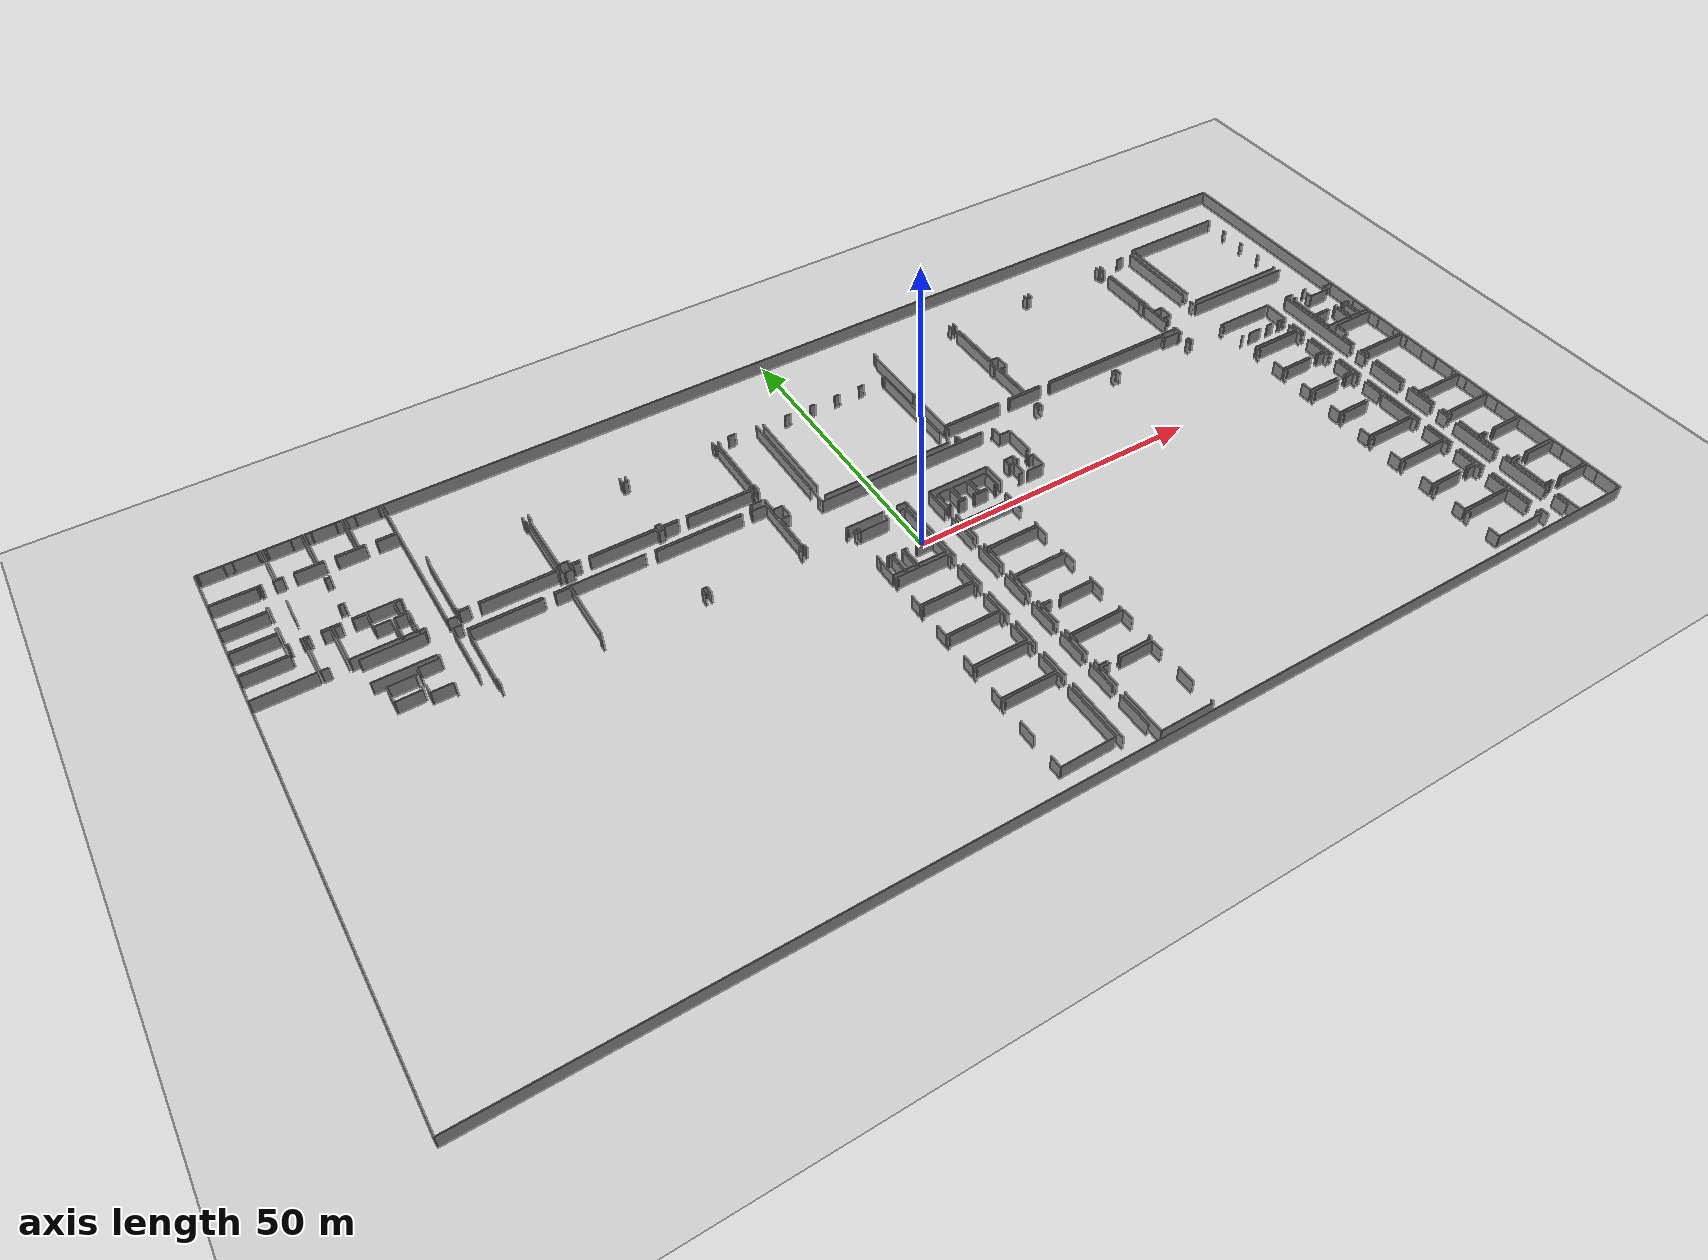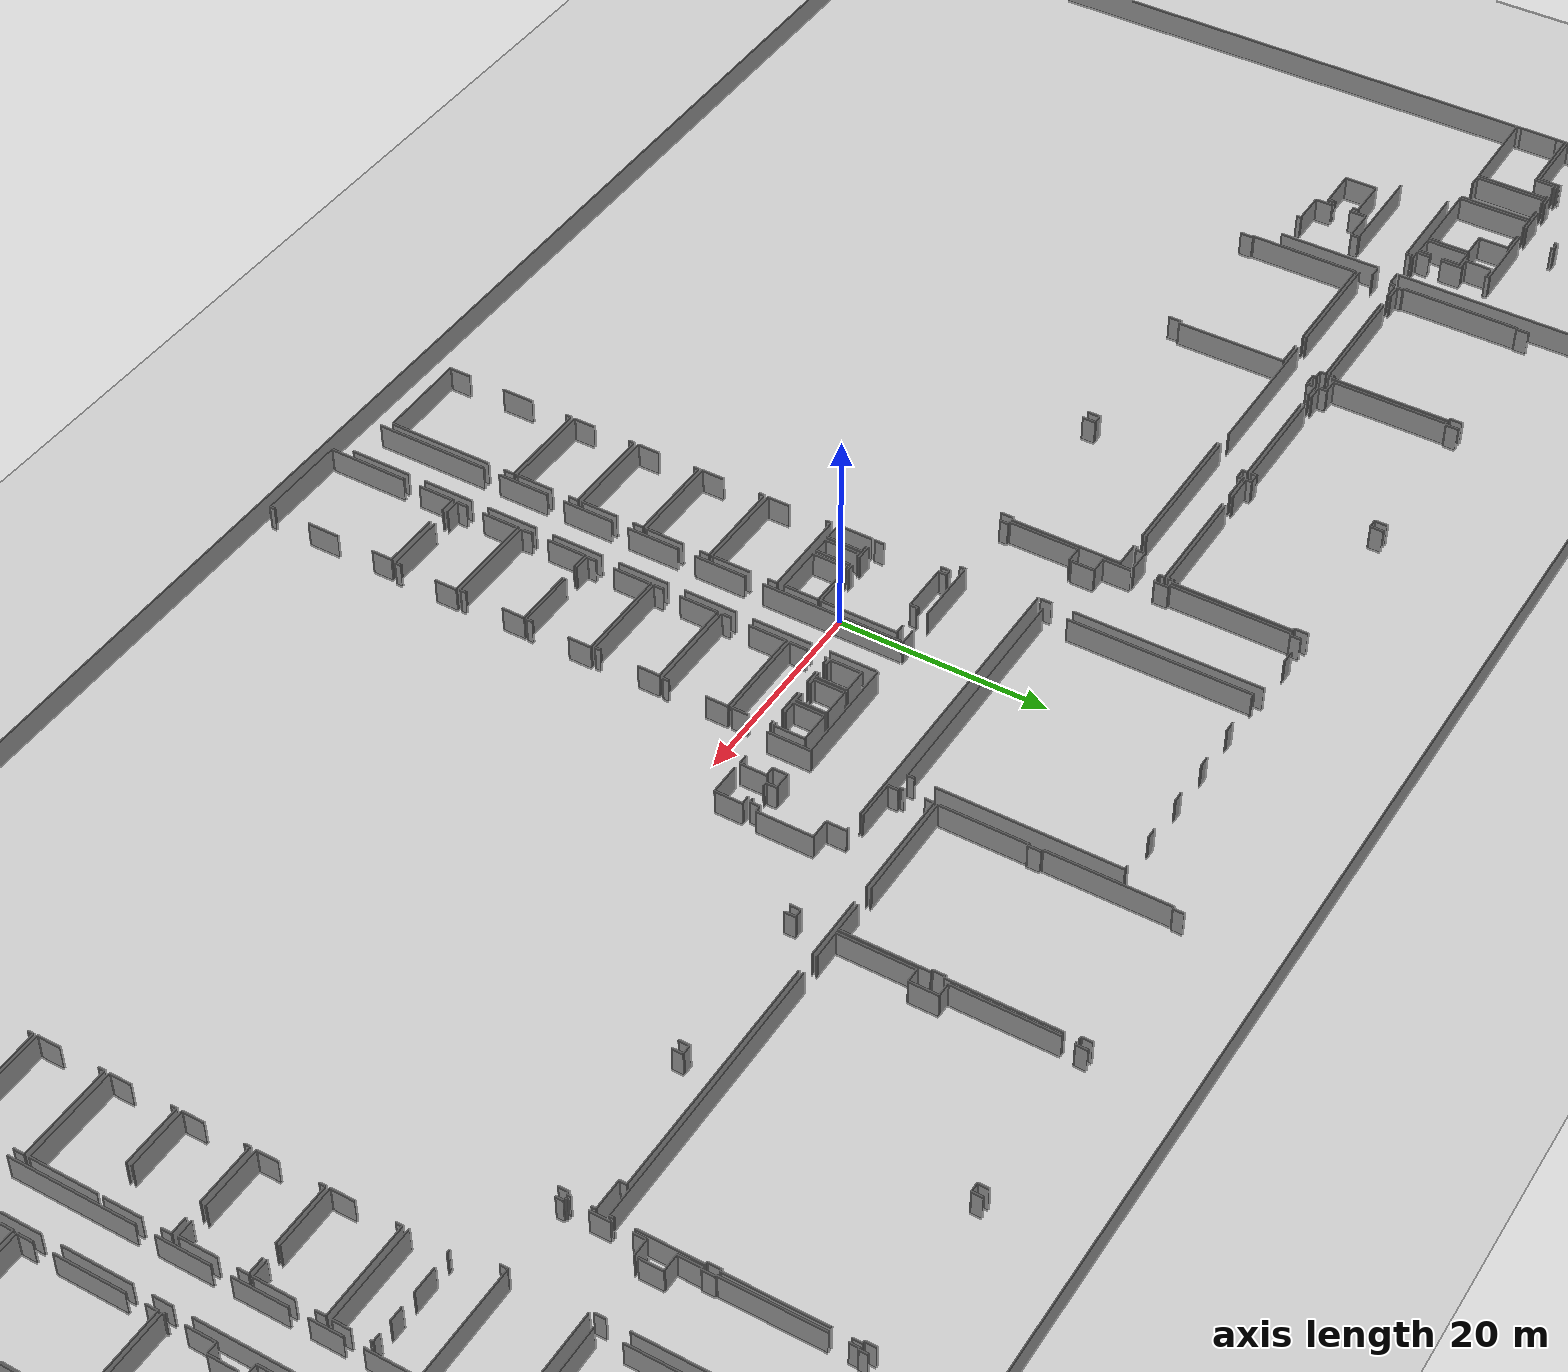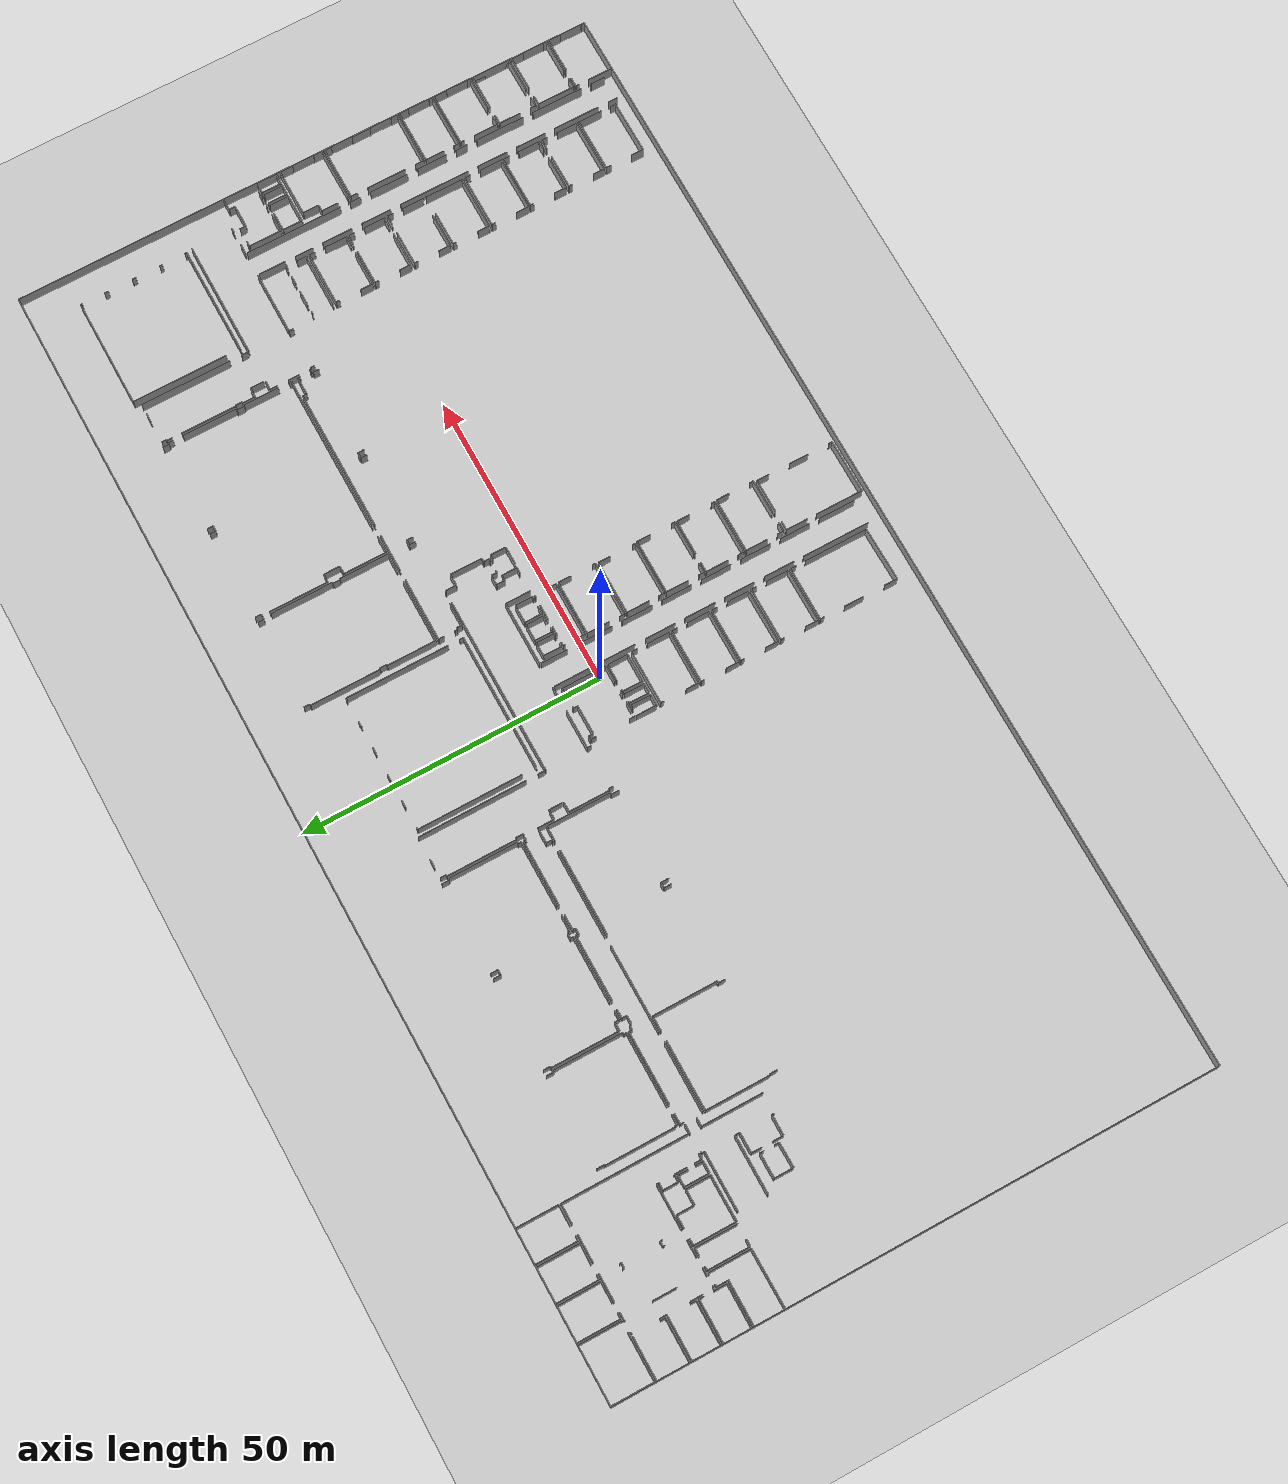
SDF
<sdf version="1.6">
  <world name="default">
    <light name="sun" type="directional">
      <cast_shadows>1</cast_shadows>
      <pose frame="">0 0 10 0 -0 0</pose>
      <diffuse>0.8 0.8 0.8 1</diffuse>
      <specular>0.1 0.1 0.1 1</specular>
      <attenuation>
        <range>1000</range>
        <constant>0.9</constant>
        <linear>0.01</linear>
        <quadratic>0.001</quadratic>
      </attenuation>
      <direction>-0.5 0.5 -1</direction>
    </light>
    <model name="ground_plane">
      <static>1</static>
      <link name="link">
        <collision name="collision">
          <geometry>
            <plane>
              <normal>0 0 1</normal>
              <size>100 100</size>
            </plane>
          </geometry>
          <surface>
            <friction>
              <ode>
                <mu>100</mu>
                <mu2>50</mu2>
              </ode>
              <torsional>
                <ode />
              </torsional>
            </friction>
            <contact>
              <ode />
            </contact>
            <bounce />
          </surface>
          <max_contacts>10</max_contacts>
        </collision>
        <visual name="visual">
          <cast_shadows>0</cast_shadows>
          <geometry>
            <plane>
              <normal>0 0 1</normal>
              <size>100 100</size>
            </plane>
          </geometry>
          <material>
            <script>
              <uri>file://media/materials/scripts/gazebo.material</uri>
              <name>Gazebo/Grey</name>
            </script>
          </material>
        </visual>
        <self_collide>0</self_collide>
        <kinematic>0</kinematic>
        <gravity>1</gravity>
      </link>
    </model>
    <gravity>0 0 -9.8</gravity>
    <magnetic_field>6e-06 2.3e-05 -4.2e-05</magnetic_field>
    <atmosphere type="adiabatic" />
    <physics default="0" name="default_physics" type="ode">
      <max_step_size>0.001</max_step_size>
      <real_time_factor>1</real_time_factor>
      <real_time_update_rate>1000</real_time_update_rate>
    </physics>
    <scene>
      <ambient>0.4 0.4 0.4 1</ambient>
      <background>0.7 0.7 0.7 1</background>
      <shadows>1</shadows>
    </scene>
    <spherical_coordinates>
      <surface_model>EARTH_WGS84</surface_model>
      <latitude_deg>0</latitude_deg>
      <longitude_deg>0</longitude_deg>
      <elevation>0</elevation>
      <heading_deg>0</heading_deg>
    </spherical_coordinates>
  <model name="0510035741_A_40_1_104">
		<static>1</static>
		<link name="Wall_0">
			<collision name="Wall_0_Collision">
				<geometry>
					<box>
						<size>7.00859151263 0.1 2.5</size>
					</box>
				</geometry>
				<pose frame="">3.50429575631 0 1.25 0 0 0</pose>
			</collision>
			<visual name="Wall_0_Visual">
				<pose frame="">3.50429575631 0 1.25 0 0 0</pose>
				<geometry>
					<box>
						<size>7.00859151263 0.1 2.5</size>
					</box>
				</geometry>
				<material>
					<script>
						<uri>file://media/materials/scripts/gazebo.material</uri>
						<name>Gazebo/Grey</name>
					</script>
					<ambient>1 1 1 1</ambient>
				</material>
			</visual>
			<pose frame="">0.0756916707412 -7.00859151263 0 0 0 1.57079632679</pose>
		</link>
		<link name="Wall_1">
			<collision name="Wall_1_Collision">
				<geometry>
					<box>
						<size>0.378966351496 0.1 2.5</size>
					</box>
				</geometry>
				<pose frame="">0.189483175748 0 1.25 0 0 0</pose>
			</collision>
			<visual name="Wall_1_Visual">
				<pose frame="">0.189483175748 0 1.25 0 0 0</pose>
				<geometry>
					<box>
						<size>0.378966351496 0.1 2.5</size>
					</box>
				</geometry>
				<material>
					<script>
						<uri>file://media/materials/scripts/gazebo.material</uri>
						<name>Gazebo/Grey</name>
					</script>
					<ambient>1 1 1 1</ambient>
				</material>
			</visual>
			<pose frame="">0.0756916707412 -0.0 0 0 0 0.0</pose>
		</link>
		<link name="Wall_2">
			<collision name="Wall_2_Collision">
				<geometry>
					<box>
						<size>1.31342828659 0.1 2.5</size>
					</box>
				</geometry>
				<pose frame="">0.656714143293 0 1.25 0 0 0</pose>
			</collision>
			<visual name="Wall_2_Visual">
				<pose frame="">0.656714143293 0 1.25 0 0 0</pose>
				<geometry>
					<box>
						<size>1.31342828659 0.1 2.5</size>
					</box>
				</geometry>
				<material>
					<script>
						<uri>file://media/materials/scripts/gazebo.material</uri>
						<name>Gazebo/Grey</name>
					</script>
					<ambient>1 1 1 1</ambient>
				</material>
			</visual>
			<pose frame="">4.1041141471 -0.0 0 0 0 0.0</pose>
		</link>
		<link name="Wall_3">
			<collision name="Wall_3_Collision">
				<geometry>
					<box>
						<size>0.530349692979 0.1 2.5</size>
					</box>
				</geometry>
				<pose frame="">0.265174846489 0 1.25 0 0 0</pose>
			</collision>
			<visual name="Wall_3_Visual">
				<pose frame="">0.265174846489 0 1.25 0 0 0</pose>
				<geometry>
					<box>
						<size>0.530349692979 0.1 2.5</size>
					</box>
				</geometry>
				<material>
					<script>
						<uri>file://media/materials/scripts/gazebo.material</uri>
						<name>Gazebo/Grey</name>
					</script>
					<ambient>1 1 1 1</ambient>
				</material>
			</visual>
			<pose frame="">9.06699855856 -0.0 0 0 0 0.0</pose>
		</link>
		<link name="Wall_4">
			<collision name="Wall_4_Collision">
				<geometry>
					<box>
						<size>7.00224154025 0.1 2.5</size>
					</box>
				</geometry>
				<pose frame="">3.50112077012 0 1.25 0 0 0</pose>
			</collision>
			<visual name="Wall_4_Visual">
				<pose frame="">3.50112077012 0 1.25 0 0 0</pose>
				<geometry>
					<box>
						<size>7.00224154025 0.1 2.5</size>
					</box>
				</geometry>
				<material>
					<script>
						<uri>file://media/materials/scripts/gazebo.material</uri>
						<name>Gazebo/Grey</name>
					</script>
					<ambient>1 1 1 1</ambient>
				</material>
			</visual>
			<pose frame="">9.59734825154 -0.0 0 0 0 -1.57079632679</pose>
		</link>
		<link name="Wall_5">
			<collision name="Wall_5_Collision">
				<geometry>
					<box>
						<size>0.214883065259 0.1 2.5</size>
					</box>
				</geometry>
				<pose frame="">0.107441532629 0 1.25 0 0 0</pose>
			</collision>
			<visual name="Wall_5_Visual">
				<pose frame="">0.107441532629 0 1.25 0 0 0</pose>
				<geometry>
					<box>
						<size>0.214883065259 0.1 2.5</size>
					</box>
				</geometry>
				<material>
					<script>
						<uri>file://media/materials/scripts/gazebo.material</uri>
						<name>Gazebo/Grey</name>
					</script>
					<ambient>1 1 1 1</ambient>
				</material>
			</visual>
			<pose frame="">9.59734825154 -7.00224154025 0 0 0 3.14159265359</pose>
		</link>
		<link name="Wall_6">
			<collision name="Wall_6_Collision">
				<geometry>
					<box>
						<size>7.69058116751 0.1 2.5</size>
					</box>
				</geometry>
				<pose frame="">3.84529058376 0 1.25 0 0 0</pose>
			</collision>
			<visual name="Wall_6_Visual">
				<pose frame="">3.84529058376 0 1.25 0 0 0</pose>
				<geometry>
					<box>
						<size>7.69058116751 0.1 2.5</size>
					</box>
				</geometry>
				<material>
					<script>
						<uri>file://media/materials/scripts/gazebo.material</uri>
						<name>Gazebo/Grey</name>
					</script>
					<ambient>1 1 1 1</ambient>
				</material>
			</visual>
			<pose frame="">7.76627021672 -7.00224154025 0 0 0 -3.14076697176</pose>
		</link>
		<link name="Wall_7">
			<collision name="Wall_7_Collision">
				<geometry>
					<box>
						<size>3.38631326954 0.1 2.5</size>
					</box>
				</geometry>
				<pose frame="">1.69315663477 0 1.25 0 0 0</pose>
			</collision>
			<visual name="Wall_7_Visual">
				<pose frame="">1.69315663477 0 1.25 0 0 0</pose>
				<geometry>
					<box>
						<size>3.38631326954 0.1 2.5</size>
					</box>
				</geometry>
				<material>
					<script>
						<uri>file://media/materials/scripts/gazebo.material</uri>
						<name>Gazebo/Grey</name>
					</script>
					<ambient>1 1 1 1</ambient>
				</material>
			</visual>
			<pose frame="">15.7619014357 -7.046437348 0 0 0 3.14159265359</pose>
		</link>
		<link name="Wall_8">
			<collision name="Wall_8_Collision">
				<geometry>
					<box>
						<size>0.958591830126 0.1 2.5</size>
					</box>
				</geometry>
				<pose frame="">0.479295915063 0 1.25 0 0 0</pose>
			</collision>
			<visual name="Wall_8_Visual">
				<pose frame="">0.479295915063 0 1.25 0 0 0</pose>
				<geometry>
					<box>
						<size>0.958591830126 0.1 2.5</size>
					</box>
				</geometry>
				<material>
					<script>
						<uri>file://media/materials/scripts/gazebo.material</uri>
						<name>Gazebo/Grey</name>
					</script>
					<ambient>1 1 1 1</ambient>
				</material>
			</visual>
			<pose frame="">10.857690769 -7.046437348 0 0 0 3.14159265359</pose>
		</link>
		<link name="Wall_9">
			<collision name="Wall_9_Collision">
				<geometry>
					<box>
						<size>7.04008737562 0.1 2.5</size>
					</box>
				</geometry>
				<pose frame="">3.52004368781 0 1.25 0 0 0</pose>
			</collision>
			<visual name="Wall_9_Visual">
				<pose frame="">3.52004368781 0 1.25 0 0 0</pose>
				<geometry>
					<box>
						<size>7.04008737562 0.1 2.5</size>
					</box>
				</geometry>
				<material>
					<script>
						<uri>file://media/materials/scripts/gazebo.material</uri>
						<name>Gazebo/Grey</name>
					</script>
					<ambient>1 1 1 1</ambient>
				</material>
			</visual>
			<pose frame="">9.89909893892 -7.046437348 0 0 0 1.57079632679</pose>
		</link>
		<link name="Wall_10">
			<collision name="Wall_10_Collision">
				<geometry>
					<box>
						<size>0.482597900699 0.1 2.5</size>
					</box>
				</geometry>
				<pose frame="">0.24129895035 0 1.25 0 0 0</pose>
			</collision>
			<visual name="Wall_10_Visual">
				<pose frame="">0.24129895035 0 1.25 0 0 0</pose>
				<geometry>
					<box>
						<size>0.482597900699 0.1 2.5</size>
					</box>
				</geometry>
				<material>
					<script>
						<uri>file://media/materials/scripts/gazebo.material</uri>
						<name>Gazebo/Grey</name>
					</script>
					<ambient>1 1 1 1</ambient>
				</material>
			</visual>
			<pose frame="">9.89909893892 -0.00634997237761 0 0 0 0.0</pose>
		</link>
		<link name="Wall_11">
			<collision name="Wall_11_Collision">
				<geometry>
					<box>
						<size>1.69010864803 0.1 2.5</size>
					</box>
				</geometry>
				<pose frame="">0.845054324014 0 1.25 0 0 0</pose>
			</collision>
			<visual name="Wall_11_Visual">
				<pose frame="">0.845054324014 0 1.25 0 0 0</pose>
				<geometry>
					<box>
						<size>1.69010864803 0.1 2.5</size>
					</box>
				</geometry>
				<material>
					<script>
						<uri>file://media/materials/scripts/gazebo.material</uri>
						<name>Gazebo/Grey</name>
					</script>
					<ambient>1 1 1 1</ambient>
				</material>
			</visual>
			<pose frame="">14.0197230142 -0.00634997237761 0 0 0 0.0</pose>
		</link>
		<link name="Wall_12">
			<collision name="Wall_12_Collision">
				<geometry>
					<box>
						<size>7.04027993177 0.1 2.5</size>
					</box>
				</geometry>
				<pose frame="">3.52013996588 0 1.25 0 0 0</pose>
			</collision>
			<visual name="Wall_12_Visual">
				<pose frame="">3.52013996588 0 1.25 0 0 0</pose>
				<geometry>
					<box>
						<size>7.04027993177 0.1 2.5</size>
					</box>
				</geometry>
				<material>
					<script>
						<uri>file://media/materials/scripts/gazebo.material</uri>
						<name>Gazebo/Grey</name>
					</script>
					<ambient>1 1 1 1</ambient>
				</material>
			</visual>
			<pose frame="">15.7098316622 -0.00634997237761 0 0 0 -1.56340027881</pose>
		</link>
		<link name="Wall_13">
			<collision name="Wall_13_Collision">
				<geometry>
					<box>
						<size>7.04008737562 0.1 2.5</size>
					</box>
				</geometry>
				<pose frame="">3.52004368781 0 1.25 0 0 0</pose>
			</collision>
			<visual name="Wall_13_Visual">
				<pose frame="">3.52004368781 0 1.25 0 0 0</pose>
				<geometry>
					<box>
						<size>7.04008737562 0.1 2.5</size>
					</box>
				</geometry>
				<material>
					<script>
						<uri>file://media/materials/scripts/gazebo.material</uri>
						<name>Gazebo/Grey</name>
					</script>
					<ambient>1 1 1 1</ambient>
				</material>
			</visual>
			<pose frame="">21.8466989669 -7.046437348 0 0 0 1.57079632679</pose>
		</link>
		<link name="Wall_14">
			<collision name="Wall_14_Collision">
				<geometry>
					<box>
						<size>1.0949892368 0.1 2.5</size>
					</box>
				</geometry>
				<pose frame="">0.547494618398 0 1.25 0 0 0</pose>
			</collision>
			<visual name="Wall_14_Visual">
				<pose frame="">0.547494618398 0 1.25 0 0 0</pose>
				<geometry>
					<box>
						<size>1.0949892368 0.1 2.5</size>
					</box>
				</geometry>
				<material>
					<script>
						<uri>file://media/materials/scripts/gazebo.material</uri>
						<name>Gazebo/Grey</name>
					</script>
					<ambient>1 1 1 1</ambient>
				</material>
			</visual>
			<pose frame="">21.8466989669 -0.00634997237761 0 0 0 3.14159265359</pose>
		</link>
		<link name="Wall_15">
			<collision name="Wall_15_Collision">
				<geometry>
					<box>
						<size>1.01218559699 0.1 2.5</size>
					</box>
				</geometry>
				<pose frame="">0.506092798496 0 1.25 0 0 0</pose>
			</collision>
			<visual name="Wall_15_Visual">
				<pose frame="">0.506092798496 0 1.25 0 0 0</pose>
				<geometry>
					<box>
						<size>1.01218559699 0.1 2.5</size>
					</box>
				</geometry>
				<material>
					<script>
						<uri>file://media/materials/scripts/gazebo.material</uri>
						<name>Gazebo/Grey</name>
					</script>
					<ambient>1 1 1 1</ambient>
				</material>
			</visual>
			<pose frame="">17.0753297223 -0.00634997237761 0 0 0 3.14159265359</pose>
		</link>
		<link name="Wall_16">
			<collision name="Wall_16_Collision">
				<geometry>
					<box>
						<size>6.97709564963 0.1 2.5</size>
					</box>
				</geometry>
				<pose frame="">3.48854782482 0 1.25 0 0 0</pose>
			</collision>
			<visual name="Wall_16_Visual">
				<pose frame="">3.48854782482 0 1.25 0 0 0</pose>
				<geometry>
					<box>
						<size>6.97709564963 0.1 2.5</size>
					</box>
				</geometry>
				<material>
					<script>
						<uri>file://media/materials/scripts/gazebo.material</uri>
						<name>Gazebo/Grey</name>
					</script>
					<ambient>1 1 1 1</ambient>
				</material>
			</visual>
			<pose frame="">16.0631441253 -0.00634997237761 0 0 0 -1.57079632679</pose>
		</link>
		<link name="Wall_17">
			<collision name="Wall_17_Collision">
				<geometry>
					<box>
						<size>0.840482343902 0.1 2.5</size>
					</box>
				</geometry>
				<pose frame="">0.420241171951 0 1.25 0 0 0</pose>
			</collision>
			<visual name="Wall_17_Visual">
				<pose frame="">0.420241171951 0 1.25 0 0 0</pose>
				<geometry>
					<box>
						<size>0.840482343902 0.1 2.5</size>
					</box>
				</geometry>
				<material>
					<script>
						<uri>file://media/materials/scripts/gazebo.material</uri>
						<name>Gazebo/Grey</name>
					</script>
					<ambient>1 1 1 1</ambient>
				</material>
			</visual>
			<pose frame="">16.0631441253 -6.98344562201 0 0 0 0.0</pose>
		</link>
		<link name="Wall_18">
			<collision name="Wall_18_Collision">
				<geometry>
					<box>
						<size>3.37775672619 0.1 2.5</size>
					</box>
				</geometry>
				<pose frame="">1.68887836309 0 1.25 0 0 0</pose>
			</collision>
			<visual name="Wall_18_Visual">
				<pose frame="">1.68887836309 0 1.25 0 0 0</pose>
				<geometry>
					<box>
						<size>3.37775672619 0.1 2.5</size>
					</box>
				</geometry>
				<material>
					<script>
						<uri>file://media/materials/scripts/gazebo.material</uri>
						<name>Gazebo/Grey</name>
					</script>
					<ambient>1 1 1 1</ambient>
				</material>
			</visual>
			<pose frame="">18.4695296575 -6.98344562201 0 0 0 -0.0186500636139</pose>
		</link>
		<link name="Wall_19">
			<collision name="Wall_19_Collision">
				<geometry>
					<box>
						<size>6.97074567726 0.1 2.5</size>
					</box>
				</geometry>
				<pose frame="">3.48537283863 0 1.25 0 0 0</pose>
			</collision>
			<visual name="Wall_19_Visual">
				<pose frame="">3.48537283863 0 1.25 0 0 0</pose>
				<geometry>
					<box>
						<size>6.97074567726 0.1 2.5</size>
					</box>
				</geometry>
				<material>
					<script>
						<uri>file://media/materials/scripts/gazebo.material</uri>
						<name>Gazebo/Grey</name>
					</script>
					<ambient>1 1 1 1</ambient>
				</material>
			</visual>
			<pose frame="">22.2142353681 -6.97455566068 0 0 0 1.57079632679</pose>
		</link>
		<link name="Wall_20">
			<collision name="Wall_20_Collision">
				<geometry>
					<box>
						<size>1.48132155625 0.1 2.5</size>
					</box>
				</geometry>
				<pose frame="">0.740660778126 0 1.25 0 0 0</pose>
			</collision>
			<visual name="Wall_20_Visual">
				<pose frame="">0.740660778126 0 1.25 0 0 0</pose>
				<geometry>
					<box>
						<size>1.48132155625 0.1 2.5</size>
					</box>
				</geometry>
				<material>
					<script>
						<uri>file://media/materials/scripts/gazebo.material</uri>
						<name>Gazebo/Grey</name>
					</script>
					<ambient>1 1 1 1</ambient>
				</material>
			</visual>
			<pose frame="">22.2142353681 -0.00380998342657 0 0 0 0.0</pose>
		</link>
		<link name="Wall_21">
			<collision name="Wall_21_Collision">
				<geometry>
					<box>
						<size>0.653539157105 0.1 2.5</size>
					</box>
				</geometry>
				<pose frame="">0.326769578552 0 1.25 0 0 0</pose>
			</collision>
			<visual name="Wall_21_Visual">
				<pose frame="">0.326769578552 0 1.25 0 0 0</pose>
				<geometry>
					<box>
						<size>0.653539157105 0.1 2.5</size>
					</box>
				</geometry>
				<material>
					<script>
						<uri>file://media/materials/scripts/gazebo.material</uri>
						<name>Gazebo/Grey</name>
					</script>
					<ambient>1 1 1 1</ambient>
				</material>
			</visual>
			<pose frame="">27.355173005 -0.00380998342657 0 0 0 0.0</pose>
		</link>
		<link name="Wall_22">
			<collision name="Wall_22_Collision">
				<geometry>
					<box>
						<size>6.97074567726 0.1 2.5</size>
					</box>
				</geometry>
				<pose frame="">3.48537283863 0 1.25 0 0 0</pose>
			</collision>
			<visual name="Wall_22_Visual">
				<pose frame="">3.48537283863 0 1.25 0 0 0</pose>
				<geometry>
					<box>
						<size>6.97074567726 0.1 2.5</size>
					</box>
				</geometry>
				<material>
					<script>
						<uri>file://media/materials/scripts/gazebo.material</uri>
						<name>Gazebo/Grey</name>
					</script>
					<ambient>1 1 1 1</ambient>
				</material>
			</visual>
			<pose frame="">28.0087121621 -0.00380998342657 0 0 0 -1.57079632679</pose>
		</link>
		<link name="Wall_23">
			<collision name="Wall_23_Collision">
				<geometry>
					<box>
						<size>3.36446936456 0.1 2.5</size>
					</box>
				</geometry>
				<pose frame="">1.68223468228 0 1.25 0 0 0</pose>
			</collision>
			<visual name="Wall_23_Visual">
				<pose frame="">1.68223468228 0 1.25 0 0 0</pose>
				<geometry>
					<box>
						<size>3.36446936456 0.1 2.5</size>
					</box>
				</geometry>
				<material>
					<script>
						<uri>file://media/materials/scripts/gazebo.material</uri>
						<name>Gazebo/Grey</name>
					</script>
					<ambient>1 1 1 1</ambient>
				</material>
			</visual>
			<pose frame="">28.0087121621 -6.97455566068 0 0 0 3.14159265359</pose>
		</link>
		<link name="Wall_24">
			<collision name="Wall_24_Collision">
				<geometry>
					<box>
						<size>0.871470209105 0.1 2.5</size>
					</box>
				</geometry>
				<pose frame="">0.435735104552 0 1.25 0 0 0</pose>
			</collision>
			<visual name="Wall_24_Visual">
				<pose frame="">0.435735104552 0 1.25 0 0 0</pose>
				<geometry>
					<box>
						<size>0.871470209105 0.1 2.5</size>
					</box>
				</geometry>
				<material>
					<script>
						<uri>file://media/materials/scripts/gazebo.material</uri>
						<name>Gazebo/Grey</name>
					</script>
					<ambient>1 1 1 1</ambient>
				</material>
			</visual>
			<pose frame="">23.0857055772 -6.97455566068 0 0 0 3.14159265359</pose>
		</link>
		<link name="Wall_25">
			<collision name="Wall_25_Collision">
				<geometry>
					<box>
						<size>6.99614556677 0.1 2.5</size>
					</box>
				</geometry>
				<pose frame="">3.49807278338 0 1.25 0 0 0</pose>
			</collision>
			<visual name="Wall_25_Visual">
				<pose frame="">3.49807278338 0 1.25 0 0 0</pose>
				<geometry>
					<box>
						<size>6.99614556677 0.1 2.5</size>
					</box>
				</geometry>
				<material>
					<script>
						<uri>file://media/materials/scripts/gazebo.material</uri>
						<name>Gazebo/Grey</name>
					</script>
					<ambient>1 1 1 1</ambient>
				</material>
			</visual>
			<pose frame="">0.0378458353706 -12.5777712867 0 0 0 0.0</pose>
		</link>
		<link name="Wall_26">
			<collision name="Wall_26_Collision">
				<geometry>
					<box>
						<size>0.808224484223 0.1 2.5</size>
					</box>
				</geometry>
				<pose frame="">0.404112242112 0 1.25 0 0 0</pose>
			</collision>
			<visual name="Wall_26_Visual">
				<pose frame="">0.404112242112 0 1.25 0 0 0</pose>
				<geometry>
					<box>
						<size>0.808224484223 0.1 2.5</size>
					</box>
				</geometry>
				<material>
					<script>
						<uri>file://media/materials/scripts/gazebo.material</uri>
						<name>Gazebo/Grey</name>
					</script>
					<ambient>1 1 1 1</ambient>
				</material>
			</visual>
			<pose frame="">7.03399140214 -12.5777712867 0 0 0 1.57079632679</pose>
		</link>
		<link name="Wall_27">
			<collision name="Wall_27_Collision">
				<geometry>
					<box>
						<size>7.00884551152 0.1 2.5</size>
					</box>
				</geometry>
				<pose frame="">3.50442275576 0 1.25 0 0 0</pose>
			</collision>
			<visual name="Wall_27_Visual">
				<pose frame="">3.50442275576 0 1.25 0 0 0</pose>
				<geometry>
					<box>
						<size>7.00884551152 0.1 2.5</size>
					</box>
				</geometry>
				<material>
					<script>
						<uri>file://media/materials/scripts/gazebo.material</uri>
						<name>Gazebo/Grey</name>
					</script>
					<ambient>1 1 1 1</ambient>
				</material>
			</visual>
			<pose frame="">7.03399140214 -7.27376635912 0 0 0 3.14159265359</pose>
		</link>
		<link name="Wall_28">
			<collision name="Wall_28_Collision">
				<geometry>
					<box>
						<size>1.55320324357 0.1 2.5</size>
					</box>
				</geometry>
				<pose frame="">0.776601621783 0 1.25 0 0 0</pose>
			</collision>
			<visual name="Wall_28_Visual">
				<pose frame="">0.776601621783 0 1.25 0 0 0</pose>
				<geometry>
					<box>
						<size>1.55320324357 0.1 2.5</size>
					</box>
				</geometry>
				<material>
					<script>
						<uri>file://media/materials/scripts/gazebo.material</uri>
						<name>Gazebo/Grey</name>
					</script>
					<ambient>1 1 1 1</ambient>
				</material>
			</visual>
			<pose frame="">0.0251458906154 -7.27376635912 0 0 0 -1.57079632679</pose>
		</link>
		<link name="Wall_29">
			<collision name="Wall_29_Collision">
				<geometry>
					<box>
						<size>0.926333970447 0.1 2.5</size>
					</box>
				</geometry>
				<pose frame="">0.463166985224 0 1.25 0 0 0</pose>
			</collision>
			<visual name="Wall_29_Visual">
				<pose frame="">0.463166985224 0 1.25 0 0 0</pose>
				<geometry>
					<box>
						<size>0.926333970447 0.1 2.5</size>
					</box>
				</geometry>
				<material>
					<script>
						<uri>file://media/materials/scripts/gazebo.material</uri>
						<name>Gazebo/Grey</name>
					</script>
					<ambient>1 1 1 1</ambient>
				</material>
			</visual>
			<pose frame="">0.0297178707272 -13.8330338263 0 0 0 1.57079632679</pose>
		</link>
		<link name="Wall_30">
			<collision name="Wall_30_Collision">
				<geometry>
					<box>
						<size>7.00046354798 0.1 2.5</size>
					</box>
				</geometry>
				<pose frame="">3.50023177399 0 1.25 0 0 0</pose>
			</collision>
			<visual name="Wall_30_Visual">
				<pose frame="">3.50023177399 0 1.25 0 0 0</pose>
				<geometry>
					<box>
						<size>7.00046354798 0.1 2.5</size>
					</box>
				</geometry>
				<material>
					<script>
						<uri>file://media/materials/scripts/gazebo.material</uri>
						<name>Gazebo/Grey</name>
					</script>
					<ambient>1 1 1 1</ambient>
				</material>
			</visual>
			<pose frame="">0.0297178707272 -12.9066998559 0 0 0 0.0</pose>
		</link>
		<link name="Wall_31">
			<collision name="Wall_31_Collision">
				<geometry>
					<box>
						<size>0.883916154965 0.1 2.5</size>
					</box>
				</geometry>
				<pose frame="">0.441958077482 0 1.25 0 0 0</pose>
			</collision>
			<visual name="Wall_31_Visual">
				<pose frame="">0.441958077482 0 1.25 0 0 0</pose>
				<geometry>
					<box>
						<size>0.883916154965 0.1 2.5</size>
					</box>
				</geometry>
				<material>
					<script>
						<uri>file://media/materials/scripts/gazebo.material</uri>
						<name>Gazebo/Grey</name>
					</script>
					<ambient>1 1 1 1</ambient>
				</material>
			</visual>
			<pose frame="">7.03018141871 -16.669185489 0 0 0 -1.57079632679</pose>
		</link>
		<link name="Wall_32">
			<collision name="Wall_32_Collision">
				<geometry>
					<box>
						<size>7.00047904908 0.1 2.5</size>
					</box>
				</geometry>
				<pose frame="">3.50023952454 0 1.25 0 0 0</pose>
			</collision>
			<visual name="Wall_32_Visual">
				<pose frame="">3.50023952454 0 1.25 0 0 0</pose>
				<geometry>
					<box>
						<size>7.00047904908 0.1 2.5</size>
					</box>
				</geometry>
				<material>
					<script>
						<uri>file://media/materials/scripts/gazebo.material</uri>
						<name>Gazebo/Grey</name>
					</script>
					<ambient>1 1 1 1</ambient>
				</material>
			</visual>
			<pose frame="">7.03018141871 -17.553101644 0 0 0 -3.13948823378</pose>
		</link>
		<link name="Wall_33">
			<collision name="Wall_33_Collision">
				<geometry>
					<box>
						<size>0.909316044475 0.1 2.5</size>
					</box>
				</geometry>
				<pose frame="">0.454658022238 0 1.25 0 0 0</pose>
			</collision>
			<visual name="Wall_33_Visual">
				<pose frame="">0.454658022238 0 1.25 0 0 0</pose>
				<geometry>
					<box>
						<size>0.909316044475 0.1 2.5</size>
					</box>
				</geometry>
				<material>
					<script>
						<uri>file://media/materials/scripts/gazebo.material</uri>
						<name>Gazebo/Grey</name>
					</script>
					<ambient>1 1 1 1</ambient>
				</material>
			</visual>
			<pose frame="">0.0 -18.8159841505 0 0 0 1.57079632679</pose>
		</link>
		<link name="Wall_34">
			<collision name="Wall_34_Collision">
				<geometry>
					<box>
						<size>7.02129145738 0.1 2.5</size>
					</box>
				</geometry>
				<pose frame="">3.51064572869 0 1.25 0 0 0</pose>
			</collision>
			<visual name="Wall_34_Visual">
				<pose frame="">3.51064572869 0 1.25 0 0 0</pose>
				<geometry>
					<box>
						<size>7.02129145738 0.1 2.5</size>
					</box>
				</geometry>
				<material>
					<script>
						<uri>file://media/materials/scripts/gazebo.material</uri>
						<name>Gazebo/Grey</name>
					</script>
					<ambient>1 1 1 1</ambient>
				</material>
			</visual>
			<pose frame="">0.0 -17.906668106 0 0 0 0.0</pose>
		</link>
		<link name="Wall_35">
			<collision name="Wall_35_Collision">
				<geometry>
					<box>
						<size>0.783078593608 0.1 2.5</size>
					</box>
				</geometry>
				<pose frame="">0.391539296804 0 1.25 0 0 0</pose>
			</collision>
			<visual name="Wall_35_Visual">
				<pose frame="">0.391539296804 0 1.25 0 0 0</pose>
				<geometry>
					<box>
						<size>0.783078593608 0.1 2.5</size>
					</box>
				</geometry>
				<material>
					<script>
						<uri>file://media/materials/scripts/gazebo.material</uri>
						<name>Gazebo/Grey</name>
					</script>
					<ambient>1 1 1 1</ambient>
				</material>
			</visual>
			<pose frame="">7.02129145738 -17.906668106 0 0 0 -1.57079632679</pose>
		</link>
		<link name="Wall_36">
			<collision name="Wall_36_Collision">
				<geometry>
					<box>
						<size>2.19277246144 0.1 2.5</size>
					</box>
				</geometry>
				<pose frame="">1.09638623072 0 1.25 0 0 0</pose>
			</collision>
			<visual name="Wall_36_Visual">
				<pose frame="">1.09638623072 0 1.25 0 0 0</pose>
				<geometry>
					<box>
						<size>2.19277246144 0.1 2.5</size>
					</box>
				</geometry>
				<material>
					<script>
						<uri>file://media/materials/scripts/gazebo.material</uri>
						<name>Gazebo/Grey</name>
					</script>
					<ambient>1 1 1 1</ambient>
				</material>
			</visual>
			<pose frame="">7.02129145738 -20.3206736051 0 0 0 -1.57079632679</pose>
		</link>
		<link name="Wall_37">
			<collision name="Wall_37_Collision">
				<geometry>
					<box>
						<size>7.02129844527 0.1 2.5</size>
					</box>
				</geometry>
				<pose frame="">3.51064922263 0 1.25 0 0 0</pose>
			</collision>
			<visual name="Wall_37_Visual">
				<pose frame="">3.51064922263 0 1.25 0 0 0</pose>
				<geometry>
					<box>
						<size>7.02129844527 0.1 2.5</size>
					</box>
				</geometry>
				<material>
					<script>
						<uri>file://media/materials/scripts/gazebo.material</uri>
						<name>Gazebo/Grey</name>
					</script>
					<ambient>1 1 1 1</ambient>
				</material>
			</visual>
			<pose frame="">7.02129145738 -22.5134460665 0 0 0 3.1401818091</pose>
		</link>
		<link name="Wall_38">
			<collision name="Wall_38_Collision">
				<geometry>
					<box>
						<size>0.480057911748 0.1 2.5</size>
					</box>
				</geometry>
				<pose frame="">0.240028955874 0 1.25 0 0 0</pose>
			</collision>
			<visual name="Wall_38_Visual">
				<pose frame="">0.240028955874 0 1.25 0 0 0</pose>
				<geometry>
					<box>
						<size>0.480057911748 0.1 2.5</size>
					</box>
				</geometry>
				<material>
					<script>
						<uri>file://media/materials/scripts/gazebo.material</uri>
						<name>Gazebo/Grey</name>
					</script>
					<ambient>1 1 1 1</ambient>
				</material>
			</visual>
			<pose frame="">0.0304798674126 -27.8690127698 0 0 0 1.57079632679</pose>
		</link>
		<link name="Wall_39">
			<collision name="Wall_39_Collision">
				<geometry>
					<box>
						<size>0.88518614944 0.1 2.5</size>
					</box>
				</geometry>
				<pose frame="">0.44259307472 0 1.25 0 0 0</pose>
			</collision>
			<visual name="Wall_39_Visual">
				<pose frame="">0.44259307472 0 1.25 0 0 0</pose>
				<geometry>
					<box>
						<size>0.88518614944 0.1 2.5</size>
					</box>
				</geometry>
				<material>
					<script>
						<uri>file://media/materials/scripts/gazebo.material</uri>
						<name>Gazebo/Grey</name>
					</script>
					<ambient>1 1 1 1</ambient>
				</material>
			</visual>
			<pose frame="">0.0304798674126 -23.7138448448 0 0 0 1.57079632679</pose>
		</link>
		<link name="Wall_40">
			<collision name="Wall_40_Collision">
				<geometry>
					<box>
						<size>7.29383227183 0.1 2.5</size>
					</box>
				</geometry>
				<pose frame="">3.64691613591 0 1.25 0 0 0</pose>
			</collision>
			<visual name="Wall_40_Visual">
				<pose frame="">3.64691613591 0 1.25 0 0 0</pose>
				<geometry>
					<box>
						<size>7.29383227183 0.1 2.5</size>
					</box>
				</geometry>
				<material>
					<script>
						<uri>file://media/materials/scripts/gazebo.material</uri>
						<name>Gazebo/Grey</name>
					</script>
					<ambient>1 1 1 1</ambient>
				</material>
			</visual>
			<pose frame="">0.0304798674126 -22.8286586953 0 0 0 0.0</pose>
		</link>
		<link name="Wall_41">
			<collision name="Wall_41_Collision">
				<geometry>
					<box>
						<size>1.94156755418 0.1 2.5</size>
					</box>
				</geometry>
				<pose frame="">0.970783777091 0 1.25 0 0 0</pose>
			</collision>
			<visual name="Wall_41_Visual">
				<pose frame="">0.970783777091 0 1.25 0 0 0</pose>
				<geometry>
					<box>
						<size>1.94156755418 0.1 2.5</size>
					</box>
				</geometry>
				<material>
					<script>
						<uri>file://media/materials/scripts/gazebo.material</uri>
						<name>Gazebo/Grey</name>
					</script>
					<ambient>1 1 1 1</ambient>
				</material>
			</visual>
			<pose frame="">7.32431213924 -22.8286586953 0 0 0 1.57079632679</pose>
		</link>
		<link name="Wall_42">
			<collision name="Wall_42_Collision">
				<geometry>
					<box>
						<size>0.416812186867 0.1 2.5</size>
					</box>
				</geometry>
				<pose frame="">0.208406093433 0 1.25 0 0 0</pose>
			</collision>
			<visual name="Wall_42_Visual">
				<pose frame="">0.208406093433 0 1.25 0 0 0</pose>
				<geometry>
					<box>
						<size>0.416812186867 0.1 2.5</size>
					</box>
				</geometry>
				<material>
					<script>
						<uri>file://media/materials/scripts/gazebo.material</uri>
						<name>Gazebo/Grey</name>
					</script>
					<ambient>1 1 1 1</ambient>
				</material>
			</visual>
			<pose frame="">7.32431213924 -20.8870911412 0 0 0 0.0</pose>
		</link>
		<link name="Wall_43">
			<collision name="Wall_43_Collision">
				<geometry>
					<box>
						<size>0.252474901734 0.1 2.5</size>
					</box>
				</geometry>
				<pose frame="">0.126237450867 0 1.25 0 0 0</pose>
			</collision>
			<visual name="Wall_43_Visual">
				<pose frame="">0.126237450867 0 1.25 0 0 0</pose>
				<geometry>
					<box>
						<size>0.252474901734 0.1 2.5</size>
					</box>
				</geometry>
				<material>
					<script>
						<uri>file://media/materials/scripts/gazebo.material</uri>
						<name>Gazebo/Grey</name>
					</script>
					<ambient>1 1 1 1</ambient>
				</material>
			</visual>
			<pose frame="">9.3448733498 -20.8870911412 0 0 0 0.0</pose>
		</link>
		<link name="Wall_44">
			<collision name="Wall_44_Collision">
				<geometry>
					<box>
						<size>6.9270578673 0.1 2.5</size>
					</box>
				</geometry>
				<pose frame="">3.46352893365 0 1.25 0 0 0</pose>
			</collision>
			<visual name="Wall_44_Visual">
				<pose frame="">3.46352893365 0 1.25 0 0 0</pose>
				<geometry>
					<box>
						<size>6.9270578673 0.1 2.5</size>
					</box>
				</geometry>
				<material>
					<script>
						<uri>file://media/materials/scripts/gazebo.material</uri>
						<name>Gazebo/Grey</name>
					</script>
					<ambient>1 1 1 1</ambient>
				</material>
			</visual>
			<pose frame="">9.59734825154 -20.8870911412 0 0 0 -1.57079632679</pose>
		</link>
		<link name="Wall_45">
			<collision name="Wall_45_Collision">
				<geometry>
					<box>
						<size>9.56702569827 0.1 2.5</size>
					</box>
				</geometry>
				<pose frame="">4.78351284914 0 1.25 0 0 0</pose>
			</collision>
			<visual name="Wall_45_Visual">
				<pose frame="">4.78351284914 0 1.25 0 0 0</pose>
				<geometry>
					<box>
						<size>9.56702569827 0.1 2.5</size>
					</box>
				</geometry>
				<material>
					<script>
						<uri>file://media/materials/scripts/gazebo.material</uri>
						<name>Gazebo/Grey</name>
					</script>
					<ambient>1 1 1 1</ambient>
				</material>
			</visual>
			<pose frame="">9.59734825154 -27.8141490085 0 0 0 -3.13585794943</pose>
		</link>
		<link name="Wall_46">
			<collision name="Wall_46_Collision">
				<geometry>
					<box>
						<size>6.94001181095 0.1 2.5</size>
					</box>
				</geometry>
				<pose frame="">3.47000590547 0 1.25 0 0 0</pose>
			</collision>
			<visual name="Wall_46_Visual">
				<pose frame="">3.47000590547 0 1.25 0 0 0</pose>
				<geometry>
					<box>
						<size>6.94001181095 0.1 2.5</size>
					</box>
				</geometry>
				<material>
					<script>
						<uri>file://media/materials/scripts/gazebo.material</uri>
						<name>Gazebo/Grey</name>
					</script>
					<ambient>1 1 1 1</ambient>
				</material>
			</visual>
			<pose frame="">9.91662486268 -27.805513046 0 0 0 1.57079632679</pose>
		</link>
		<link name="Wall_47">
			<collision name="Wall_47_Collision">
				<geometry>
					<box>
						<size>0.660905125063 0.1 2.5</size>
					</box>
				</geometry>
				<pose frame="">0.330452562531 0 1.25 0 0 0</pose>
			</collision>
			<visual name="Wall_47_Visual">
				<pose frame="">0.330452562531 0 1.25 0 0 0</pose>
				<geometry>
					<box>
						<size>0.660905125063 0.1 2.5</size>
					</box>
				</geometry>
				<material>
					<script>
						<uri>file://media/materials/scripts/gazebo.material</uri>
						<name>Gazebo/Grey</name>
					</script>
					<ambient>1 1 1 1</ambient>
				</material>
			</visual>
			<pose frame="">9.91662486268 -20.8655012351 0 0 0 0.0</pose>
		</link>
		<link name="Wall_48">
			<collision name="Wall_48_Collision">
				<geometry>
					<box>
						<size>1.33959017278 0.1 2.5</size>
					</box>
				</geometry>
				<pose frame="">0.669795086391 0 1.25 0 0 0</pose>
			</collision>
			<visual name="Wall_48_Visual">
				<pose frame="">0.669795086391 0 1.25 0 0 0</pose>
				<geometry>
					<box>
						<size>1.33959017278 0.1 2.5</size>
					</box>
				</geometry>
				<material>
					<script>
						<uri>file://media/materials/scripts/gazebo.material</uri>
						<name>Gazebo/Grey</name>
					</script>
					<ambient>1 1 1 1</ambient>
				</material>
			</visual>
			<pose frame="">12.1916929661 -20.8655012351 0 0 0 0.0</pose>
		</link>
		<link name="Wall_49">
			<collision name="Wall_49_Collision">
				<geometry>
					<box>
						<size>6.9633797093 0.1 2.5</size>
					</box>
				</geometry>
				<pose frame="">3.48168985465 0 1.25 0 0 0</pose>
			</collision>
			<visual name="Wall_49_Visual">
				<pose frame="">3.48168985465 0 1.25 0 0 0</pose>
				<geometry>
					<box>
						<size>6.9633797093 0.1 2.5</size>
					</box>
				</geometry>
				<material>
					<script>
						<uri>file://media/materials/scripts/gazebo.material</uri>
						<name>Gazebo/Grey</name>
					</script>
					<ambient>1 1 1 1</ambient>
				</material>
			</visual>
			<pose frame="">13.5312831389 -20.8655012351 0 0 0 -1.57079632679</pose>
		</link>
		<link name="Wall_50">
			<collision name="Wall_50_Collision">
				<geometry>
					<box>
						<size>1.17370753971 0.1 2.5</size>
					</box>
				</geometry>
				<pose frame="">0.586853769855 0 1.25 0 0 0</pose>
			</collision>
			<visual name="Wall_50_Visual">
				<pose frame="">0.586853769855 0 1.25 0 0 0</pose>
				<geometry>
					<box>
						<size>1.17370753971 0.1 2.5</size>
					</box>
				</geometry>
				<material>
					<script>
						<uri>file://media/materials/scripts/gazebo.material</uri>
						<name>Gazebo/Grey</name>
					</script>
					<ambient>1 1 1 1</ambient>
				</material>
			</visual>
			<pose frame="">11.0900997581 -27.8288809444 0 0 0 3.12168186523</pose>
		</link>
		<link name="Wall_51">
			<collision name="Wall_51_Collision">
				<geometry>
					<box>
						<size>7.02865742534 0.1 2.5</size>
					</box>
				</geometry>
				<pose frame="">3.51432871267 0 1.25 0 0 0</pose>
			</collision>
			<visual name="Wall_51_Visual">
				<pose frame="">3.51432871267 0 1.25 0 0 0</pose>
				<geometry>
					<box>
						<size>7.02865742534 0.1 2.5</size>
					</box>
				</geometry>
				<material>
					<script>
						<uri>file://media/materials/scripts/gazebo.material</uri>
						<name>Gazebo/Grey</name>
					</script>
					<ambient>1 1 1 1</ambient>
				</material>
			</visual>
			<pose frame="">13.8746896451 -27.8723147554 0 0 0 1.57079632679</pose>
		</link>
		<link name="Wall_52">
			<collision name="Wall_52_Collision">
				<geometry>
					<box>
						<size>1.16102894952 0.1 2.5</size>
					</box>
				</geometry>
				<pose frame="">0.580514474762 0 1.25 0 0 0</pose>
			</collision>
			<visual name="Wall_52_Visual">
				<pose frame="">0.580514474762 0 1.25 0 0 0</pose>
				<geometry>
					<box>
						<size>1.16102894952 0.1 2.5</size>
					</box>
				</geometry>
				<material>
					<script>
						<uri>file://media/materials/scripts/gazebo.material</uri>
						<name>Gazebo/Grey</name>
					</script>
					<ambient>1 1 1 1</ambient>
				</material>
			</visual>
			<pose frame="">13.8746896451 -20.8436573301 0 0 0 0.0</pose>
		</link>
		<link name="Wall_53">
			<collision name="Wall_53_Collision">
				<geometry>
					<box>
						<size>2.10819082937 0.1 2.5</size>
					</box>
				</geometry>
				<pose frame="">1.05409541468 0 1.25 0 0 0</pose>
			</collision>
			<visual name="Wall_53_Visual">
				<pose frame="">1.05409541468 0 1.25 0 0 0</pose>
				<geometry>
					<box>
						<size>2.10819082937 0.1 2.5</size>
					</box>
				</geometry>
				<material>
					<script>
						<uri>file://media/materials/scripts/gazebo.material</uri>
						<name>Gazebo/Grey</name>
					</script>
					<ambient>1 1 1 1</ambient>
				</material>
			</visual>
			<pose frame="">16.6610575244 -20.8436573301 0 0 0 0.0</pose>
		</link>
		<link name="Wall_54">
			<collision name="Wall_54_Collision">
				<geometry>
					<box>
						<size>2.92251128708 0.1 2.5</size>
					</box>
				</geometry>
				<pose frame="">1.46125564354 0 1.25 0 0 0</pose>
			</collision>
			<visual name="Wall_54_Visual">
				<pose frame="">1.46125564354 0 1.25 0 0 0</pose>
				<geometry>
					<box>
						<size>2.92251128708 0.1 2.5</size>
					</box>
				</geometry>
				<material>
					<script>
						<uri>file://media/materials/scripts/gazebo.material</uri>
						<name>Gazebo/Grey</name>
					</script>
					<ambient>1 1 1 1</ambient>
				</material>
			</visual>
			<pose frame="">18.7692483538 -20.8436573301 0 0 0 -1.57079632679</pose>
		</link>
		<link name="Wall_55">
			<collision name="Wall_55_Collision">
				<geometry>
					<box>
						<size>2.55980086487 0.1 2.5</size>
					</box>
				</geometry>
				<pose frame="">1.27990043243 0 1.25 0 0 0</pose>
			</collision>
			<visual name="Wall_55_Visual">
				<pose frame="">1.27990043243 0 1.25 0 0 0</pose>
				<geometry>
					<box>
						<size>2.55980086487 0.1 2.5</size>
					</box>
				</geometry>
				<material>
					<script>
						<uri>file://media/materials/scripts/gazebo.material</uri>
						<name>Gazebo/Grey</name>
					</script>
					<ambient>1 1 1 1</ambient>
				</material>
			</visual>
			<pose frame="">18.7692483538 -23.7661686172 0 0 0 0.0</pose>
		</link>
		<link name="Wall_56">
			<collision name="Wall_56_Collision">
				<geometry>
					<box>
						<size>4.09166820124 0.1 2.5</size>
					</box>
				</geometry>
				<pose frame="">2.04583410062 0 1.25 0 0 0</pose>
			</collision>
			<visual name="Wall_56_Visual">
				<pose frame="">2.04583410062 0 1.25 0 0 0</pose>
				<geometry>
					<box>
						<size>4.09166820124 0.1 2.5</size>
					</box>
				</geometry>
				<material>
					<script>
						<uri>file://media/materials/scripts/gazebo.material</uri>
						<name>Gazebo/Grey</name>
					</script>
					<ambient>1 1 1 1</ambient>
				</material>
			</visual>
			<pose frame="">21.3290492186 -23.7661686172 0 0 0 -1.57079632679</pose>
		</link>
		<link name="Wall_57">
			<collision name="Wall_57_Collision">
				<geometry>
					<box>
						<size>7.45437363312 0.1 2.5</size>
					</box>
				</geometry>
				<pose frame="">3.72718681656 0 1.25 0 0 0</pose>
			</collision>
			<visual name="Wall_57_Visual">
				<pose frame="">3.72718681656 0 1.25 0 0 0</pose>
				<geometry>
					<box>
						<size>7.45437363312 0.1 2.5</size>
					</box>
				</geometry>
				<material>
					<script>
						<uri>file://media/materials/scripts/gazebo.material</uri>
						<name>Gazebo/Grey</name>
					</script>
					<ambient>1 1 1 1</ambient>
				</material>
			</visual>
			<pose frame="">21.3290492186 -27.8578368184 0 0 0 -3.13965044532</pose>
		</link>
		<link name="Wall_58">
			<collision name="Wall_58_Collision">
				<geometry>
					<box>
						<size>3.9019310266 0.1 2.5</size>
					</box>
				</geometry>
				<pose frame="">1.9509655133 0 1.25 0 0 0</pose>
			</collision>
			<visual name="Wall_58_Visual">
				<pose frame="">1.9509655133 0 1.25 0 0 0</pose>
				<geometry>
					<box>
						<size>3.9019310266 0.1 2.5</size>
					</box>
				</geometry>
				<material>
					<script>
						<uri>file://media/materials/scripts/gazebo.material</uri>
						<name>Gazebo/Grey</name>
					</script>
					<ambient>1 1 1 1</ambient>
				</material>
			</visual>
			<pose frame="">9.89909893892 -15.9366526756 0 0 0 1.57079632679</pose>
		</link>
		<link name="Wall_59">
			<collision name="Wall_59_Collision">
				<geometry>
					<box>
						<size>0.264158850909 0.1 2.5</size>
					</box>
				</geometry>
				<pose frame="">0.132079425454 0 1.25 0 0 0</pose>
			</collision>
			<visual name="Wall_59_Visual">
				<pose frame="">0.132079425454 0 1.25 0 0 0</pose>
				<geometry>
					<box>
						<size>0.264158850909 0.1 2.5</size>
					</box>
				</geometry>
				<material>
					<script>
						<uri>file://media/materials/scripts/gazebo.material</uri>
						<name>Gazebo/Grey</name>
					</script>
					<ambient>1 1 1 1</ambient>
				</material>
			</visual>
			<pose frame="">15.8264171551 -10.5318101866 0 0 0 -1.57079632679</pose>
		</link>
		<link name="Wall_60">
			<collision name="Wall_60_Collision">
				<geometry>
					<box>
						<size>0.801620512951 0.1 2.5</size>
					</box>
				</geometry>
				<pose frame="">0.400810256475 0 1.25 0 0 0</pose>
			</collision>
			<visual name="Wall_60_Visual">
				<pose frame="">0.400810256475 0 1.25 0 0 0</pose>
				<geometry>
					<box>
						<size>0.801620512951 0.1 2.5</size>
					</box>
				</geometry>
				<material>
					<script>
						<uri>file://media/materials/scripts/gazebo.material</uri>
						<name>Gazebo/Grey</name>
					</script>
					<ambient>1 1 1 1</ambient>
				</material>
			</visual>
			<pose frame="">15.8264171551 -10.7959690375 0 0 0 0.0</pose>
		</link>
		<link name="Wall_61">
			<collision name="Wall_61_Collision">
				<geometry>
					<box>
						<size>0.274572805608 0.1 2.5</size>
					</box>
				</geometry>
				<pose frame="">0.137286402804 0 1.25 0 0 0</pose>
			</collision>
			<visual name="Wall_61_Visual">
				<pose frame="">0.137286402804 0 1.25 0 0 0</pose>
				<geometry>
					<box>
						<size>0.274572805608 0.1 2.5</size>
					</box>
				</geometry>
				<material>
					<script>
						<uri>file://media/materials/scripts/gazebo.material</uri>
						<name>Gazebo/Grey</name>
					</script>
					<ambient>1 1 1 1</ambient>
				</material>
			</visual>
			<pose frame="">16.628037668 -10.7959690375 0 0 0 1.57079632679</pose>
		</link>
		<link name="Wall_62">
			<collision name="Wall_62_Collision">
				<geometry>
					<box>
						<size>0.308862656447 0.1 2.5</size>
					</box>
				</geometry>
				<pose frame="">0.154431328224 0 1.25 0 0 0</pose>
			</collision>
			<visual name="Wall_62_Visual">
				<pose frame="">0.154431328224 0 1.25 0 0 0</pose>
				<geometry>
					<box>
						<size>0.308862656447 0.1 2.5</size>
					</box>
				</geometry>
				<material>
					<script>
						<uri>file://media/materials/scripts/gazebo.material</uri>
						<name>Gazebo/Grey</name>
					</script>
					<ambient>1 1 1 1</ambient>
				</material>
			</visual>
			<pose frame="">16.683917425 -17.3407585677 0 0 0 1.57079632679</pose>
		</link>
		<link name="Wall_63">
			<collision name="Wall_63_Collision">
				<geometry>
					<box>
						<size>0.849880303021 0.1 2.5</size>
					</box>
				</geometry>
				<pose frame="">0.42494015151 0 1.25 0 0 0</pose>
			</collision>
			<visual name="Wall_63_Visual">
				<pose frame="">0.42494015151 0 1.25 0 0 0</pose>
				<geometry>
					<box>
						<size>0.849880303021 0.1 2.5</size>
					</box>
				</geometry>
				<material>
					<script>
						<uri>file://media/materials/scripts/gazebo.material</uri>
						<name>Gazebo/Grey</name>
					</script>
					<ambient>1 1 1 1</ambient>
				</material>
			</visual>
			<pose frame="">16.683917425 -17.0318959113 0 0 0 3.14159265359</pose>
		</link>
		<link name="Wall_64">
			<collision name="Wall_64_Collision">
				<geometry>
					<box>
						<size>0.305560670811 0.1 2.5</size>
					</box>
				</geometry>
				<pose frame="">0.152780335406 0 1.25 0 0 0</pose>
			</collision>
			<visual name="Wall_64_Visual">
				<pose frame="">0.152780335406 0 1.25 0 0 0</pose>
				<geometry>
					<box>
						<size>0.305560670811 0.1 2.5</size>
					</box>
				</geometry>
				<material>
					<script>
						<uri>file://media/materials/scripts/gazebo.material</uri>
						<name>Gazebo/Grey</name>
					</script>
					<ambient>1 1 1 1</ambient>
				</material>
			</visual>
			<pose frame="">15.8340371219 -17.0318959113 0 0 0 -1.57079632679</pose>
		</link>
		<link name="Wall_65">
			<collision name="Wall_65_Collision">
				<geometry>
					<box>
						<size>4.09624018136 0.1 2.5</size>
					</box>
				</geometry>
				<pose frame="">2.04812009068 0 1.25 0 0 0</pose>
			</collision>
			<visual name="Wall_65_Visual">
				<pose frame="">2.04812009068 0 1.25 0 0 0</pose>
				<geometry>
					<box>
						<size>4.09624018136 0.1 2.5</size>
					</box>
				</geometry>
				<material>
					<script>
						<uri>file://media/materials/scripts/gazebo.material</uri>
						<name>Gazebo/Grey</name>
					</script>
					<ambient>1 1 1 1</ambient>
				</material>
			</visual>
			<pose frame="">21.6683917425 -27.8504708505 0 0 0 1.57079632679</pose>
		</link>
		<link name="Wall_66">
			<collision name="Wall_66_Collision">
				<geometry>
					<box>
						<size>1.90981769229 0.1 2.5</size>
					</box>
				</geometry>
				<pose frame="">0.954908846147 0 1.25 0 0 0</pose>
			</collision>
			<visual name="Wall_66_Visual">
				<pose frame="">0.954908846147 0 1.25 0 0 0</pose>
				<geometry>
					<box>
						<size>1.90981769229 0.1 2.5</size>
					</box>
				</geometry>
				<material>
					<script>
						<uri>file://media/materials/scripts/gazebo.material</uri>
						<name>Gazebo/Grey</name>
					</script>
					<ambient>1 1 1 1</ambient>
				</material>
			</visual>
			<pose frame="">21.6683917425 -23.7542306691 0 0 0 0.0</pose>
		</link>
		<link name="Wall_67">
			<collision name="Wall_67_Collision">
				<geometry>
					<box>
						<size>1.71855652428 0.1 2.5</size>
					</box>
				</geometry>
				<pose frame="">0.85927826214 0 1.25 0 0 0</pose>
			</collision>
			<visual name="Wall_67_Visual">
				<pose frame="">0.85927826214 0 1.25 0 0 0</pose>
				<geometry>
					<box>
						<size>1.71855652428 0.1 2.5</size>
					</box>
				</geometry>
				<material>
					<script>
						<uri>file://media/materials/scripts/gazebo.material</uri>
						<name>Gazebo/Grey</name>
					</script>
					<ambient>1 1 1 1</ambient>
				</material>
			</visual>
			<pose frame="">23.5782094348 -23.7542306691 0 0 0 -1.57079632679</pose>
		</link>
		<link name="Wall_68">
			<collision name="Wall_68_Collision">
				<geometry>
					<box>
						<size>1.20243076943 0.1 2.5</size>
					</box>
				</geometry>
				<pose frame="">0.601215384713 0 1.25 0 0 0</pose>
			</collision>
			<visual name="Wall_68_Visual">
				<pose frame="">0.601215384713 0 1.25 0 0 0</pose>
				<geometry>
					<box>
						<size>1.20243076943 0.1 2.5</size>
					</box>
				</geometry>
				<material>
					<script>
						<uri>file://media/materials/scripts/gazebo.material</uri>
						<name>Gazebo/Grey</name>
					</script>
					<ambient>1 1 1 1</ambient>
				</material>
			</visual>
			<pose frame="">23.5782094348 -26.6531200589 0 0 0 -1.57079632679</pose>
		</link>
		<link name="Wall_69">
			<collision name="Wall_69_Collision">
				<geometry>
					<box>
						<size>1.90982444847 0.1 2.5</size>
					</box>
				</geometry>
				<pose frame="">0.954912224235 0 1.25 0 0 0</pose>
			</collision>
			<visual name="Wall_69_Visual">
				<pose frame="">0.954912224235 0 1.25 0 0 0</pose>
				<geometry>
					<box>
						<size>1.90982444847 0.1 2.5</size>
					</box>
				</geometry>
				<material>
					<script>
						<uri>file://media/materials/scripts/gazebo.material</uri>
						<name>Gazebo/Grey</name>
					</script>
					<ambient>1 1 1 1</ambient>
				</material>
			</visual>
			<pose frame="">23.5782094348 -27.8555508284 0 0 0 3.13893273168</pose>
		</link>
		<link name="Wall_70">
			<collision name="Wall_70_Collision">
				<geometry>
					<box>
						<size>2.57808878531 0.1 2.5</size>
					</box>
				</geometry>
				<pose frame="">1.28904439266 0 1.25 0 0 0</pose>
			</collision>
			<visual name="Wall_70_Visual">
				<pose frame="">1.28904439266 0 1.25 0 0 0</pose>
				<geometry>
					<box>
						<size>2.57808878531 0.1 2.5</size>
					</box>
				</geometry>
				<material>
					<script>
						<uri>file://media/materials/scripts/gazebo.material</uri>
						<name>Gazebo/Grey</name>
					</script>
					<ambient>1 1 1 1</ambient>
				</material>
			</visual>
			<pose frame="">22.6996272566 -23.4103161651 0 0 0 1.57079632679</pose>
		</link>
		<link name="Wall_71">
			<collision name="Wall_71_Collision">
				<geometry>
					<box>
						<size>1.05993738927 0.1 2.5</size>
					</box>
				</geometry>
				<pose frame="">0.529968694636 0 1.25 0 0 0</pose>
			</collision>
			<visual name="Wall_71_Visual">
				<pose frame="">0.529968694636 0 1.25 0 0 0</pose>
				<geometry>
					<box>
						<size>1.05993738927 0.1 2.5</size>
					</box>
				</geometry>
				<material>
					<script>
						<uri>file://media/materials/scripts/gazebo.material</uri>
						<name>Gazebo/Grey</name>
					</script>
					<ambient>1 1 1 1</ambient>
				</material>
			</visual>
			<pose frame="">22.6996272566 -20.8322273798 0 0 0 0.0</pose>
		</link>
		<link name="Wall_72">
			<collision name="Wall_72_Collision">
				<geometry>
					<box>
						<size>0.133603418825 0.1 2.5</size>
					</box>
				</geometry>
				<pose frame="">0.0668017094126 0 1.25 0 0 0</pose>
			</collision>
			<visual name="Wall_72_Visual">
				<pose frame="">0.0668017094126 0 1.25 0 0 0</pose>
				<geometry>
					<box>
						<size>0.133603418825 0.1 2.5</size>
					</box>
				</geometry>
				<material>
					<script>
						<uri>file://media/materials/scripts/gazebo.material</uri>
						<name>Gazebo/Grey</name>
					</script>
					<ambient>1 1 1 1</ambient>
				</material>
			</visual>
			<pose frame="">23.7595646459 -20.8322273798 0 0 0 -1.57079632679</pose>
		</link>
		<link name="Wall_73">
			<collision name="Wall_73_Collision">
				<geometry>
					<box>
						<size>0.114553501692 0.1 2.5</size>
					</box>
				</geometry>
				<pose frame="">0.0572767508461 0 1.25 0 0 0</pose>
			</collision>
			<visual name="Wall_73_Visual">
				<pose frame="">0.0572767508461 0 1.25 0 0 0</pose>
				<geometry>
					<box>
						<size>0.114553501692 0.1 2.5</size>
					</box>
				</geometry>
				<material>
					<script>
						<uri>file://media/materials/scripts/gazebo.material</uri>
						<name>Gazebo/Grey</name>
					</script>
					<ambient>1 1 1 1</ambient>
				</material>
			</visual>
			<pose frame="">23.7595646459 -23.3244645386 0 0 0 -1.57079632679</pose>
		</link>
		<link name="Wall_74">
			<collision name="Wall_74_Collision">
				<geometry>
					<box>
						<size>1.06032592481 0.1 2.5</size>
					</box>
				</geometry>
				<pose frame="">0.530162962403 0 1.25 0 0 0</pose>
			</collision>
			<visual name="Wall_74_Visual">
				<pose frame="">0.530162962403 0 1.25 0 0 0</pose>
				<geometry>
					<box>
						<size>1.06032592481 0.1 2.5</size>
					</box>
				</geometry>
				<material>
					<script>
						<uri>file://media/materials/scripts/gazebo.material</uri>
						<name>Gazebo/Grey</name>
					</script>
					<ambient>1 1 1 1</ambient>
				</material>
			</visual>
			<pose frame="">23.7595646459 -23.4390180403 0 0 0 3.11452042916</pose>
		</link>
		<link name="Wall_75">
			<collision name="Wall_75_Collision">
				<geometry>
					<box>
						<size>2.02056121056 0.1 2.5</size>
					</box>
				</geometry>
				<pose frame="">1.01028060528 0 1.25 0 0 0</pose>
			</collision>
			<visual name="Wall_75_Visual">
				<pose frame="">1.01028060528 0 1.25 0 0 0</pose>
				<geometry>
					<box>
						<size>2.02056121056 0.1 2.5</size>
					</box>
				</geometry>
				<material>
					<script>
						<uri>file://media/materials/scripts/gazebo.material</uri>
						<name>Gazebo/Grey</name>
					</script>
					<ambient>1 1 1 1</ambient>
				</material>
			</visual>
			<pose frame="">7.30500822321 -18.6897466996 0 0 0 1.57079632679</pose>
		</link>
		<link name="Wall_76">
			<collision name="Wall_76_Collision">
				<geometry>
					<box>
						<size>1.14909100145 0.1 2.5</size>
					</box>
				</geometry>
				<pose frame="">0.574545500727 0 1.25 0 0 0</pose>
			</collision>
			<visual name="Wall_76_Visual">
				<pose frame="">0.574545500727 0 1.25 0 0 0</pose>
				<geometry>
					<box>
						<size>1.14909100145 0.1 2.5</size>
					</box>
				</geometry>
				<material>
					<script>
						<uri>file://media/materials/scripts/gazebo.material</uri>
						<name>Gazebo/Grey</name>
					</script>
					<ambient>1 1 1 1</ambient>
				</material>
			</visual>
			<pose frame="">7.30500822321 -12.9437836945 0 0 0 1.57079632679</pose>
		</link>
		<link name="Wall_77">
			<collision name="Wall_77_Collision">
				<geometry>
					<box>
						<size>0.42341615814 0.1 2.5</size>
					</box>
				</geometry>
				<pose frame="">0.21170807907 0 1.25 0 0 0</pose>
			</collision>
			<visual name="Wall_77_Visual">
				<pose frame="">0.21170807907 0 1.25 0 0 0</pose>
				<geometry>
					<box>
						<size>0.42341615814 0.1 2.5</size>
					</box>
				</geometry>
				<material>
					<script>
						<uri>file://media/materials/scripts/gazebo.material</uri>
						<name>Gazebo/Grey</name>
					</script>
					<ambient>1 1 1 1</ambient>
				</material>
			</visual>
			<pose frame="">7.30500822321 -7.29916624863 0 0 0 0.0</pose>
		</link>
		<link name="Wall_78">
			<collision name="Wall_78_Collision">
				<geometry>
					<box>
						<size>1.45769965901 0.1 2.5</size>
					</box>
				</geometry>
				<pose frame="">0.728849829503 0 1.25 0 0 0</pose>
			</collision>
			<visual name="Wall_78_Visual">
				<pose frame="">0.728849829503 0 1.25 0 0 0</pose>
				<geometry>
					<box>
						<size>1.45769965901 0.1 2.5</size>
					</box>
				</geometry>
				<material>
					<script>
						<uri>file://media/materials/scripts/gazebo.material</uri>
						<name>Gazebo/Grey</name>
					</script>
					<ambient>1 1 1 1</ambient>
				</material>
			</visual>
			<pose frame="">9.32252144703 -7.29916624863 0 0 0 0.0</pose>
		</link>
		<link name="Wall_79">
			<collision name="Wall_79_Collision">
				<geometry>
					<box>
						<size>4.57198011189 0.1 2.5</size>
					</box>
				</geometry>
				<pose frame="">2.28599005594 0 1.25 0 0 0</pose>
			</collision>
			<visual name="Wall_79_Visual">
				<pose frame="">2.28599005594 0 1.25 0 0 0</pose>
				<geometry>
					<box>
						<size>4.57198011189 0.1 2.5</size>
					</box>
				</geometry>
				<material>
					<script>
						<uri>file://media/materials/scripts/gazebo.material</uri>
						<name>Gazebo/Grey</name>
					</script>
					<ambient>1 1 1 1</ambient>
				</material>
			</visual>
			<pose frame="">12.3263123805 -7.29916624863 0 0 0 0.0</pose>
		</link>
		<link name="Wall_80">
			<collision name="Wall_80_Collision">
				<geometry>
					<box>
						<size>4.53261028315 0.1 2.5</size>
					</box>
				</geometry>
				<pose frame="">2.26630514157 0 1.25 0 0 0</pose>
			</collision>
			<visual name="Wall_80_Visual">
				<pose frame="">2.26630514157 0 1.25 0 0 0</pose>
				<geometry>
					<box>
						<size>4.53261028315 0.1 2.5</size>
					</box>
				</geometry>
				<material>
					<script>
						<uri>file://media/materials/scripts/gazebo.material</uri>
						<name>Gazebo/Grey</name>
					</script>
					<ambient>1 1 1 1</ambient>
				</material>
			</visual>
			<pose frame="">18.5452213283 -7.29916624863 0 0 0 0.0</pose>
		</link>
		<link name="Wall_81">
			<collision name="Wall_81_Collision">
				<geometry>
					<box>
						<size>3.34186346289 0.1 2.5</size>
					</box>
				</geometry>
				<pose frame="">1.67093173145 0 1.25 0 0 0</pose>
			</collision>
			<visual name="Wall_81_Visual">
				<pose frame="">1.67093173145 0 1.25 0 0 0</pose>
				<geometry>
					<box>
						<size>3.34186346289 0.1 2.5</size>
					</box>
				</geometry>
				<material>
					<script>
						<uri>file://media/materials/scripts/gazebo.material</uri>
						<name>Gazebo/Grey</name>
					</script>
					<ambient>1 1 1 1</ambient>
				</material>
			</visual>
			<pose frame="">24.6526247611 -7.29916624863 0 0 0 0.0</pose>
		</link>
		<link name="Wall_82">
			<collision name="Wall_82_Collision">
				<geometry>
					<box>
						<size>20.6275042704 0.1 2.5</size>
					</box>
				</geometry>
				<pose frame="">10.3137521352 0 1.25 0 0 0</pose>
			</collision>
			<visual name="Wall_82_Visual">
				<pose frame="">10.3137521352 0 1.25 0 0 0</pose>
				<geometry>
					<box>
						<size>20.6275042704 0.1 2.5</size>
					</box>
				</geometry>
				<material>
					<script>
						<uri>file://media/materials/scripts/gazebo.material</uri>
						<name>Gazebo/Grey</name>
					</script>
					<ambient>1 1 1 1</ambient>
				</material>
			</visual>
			<pose frame="">27.994488224 -7.29916624863 0 0 0 -1.57079632679</pose>
		</link>
		<link name="Wall_83">
			<collision name="Wall_83_Collision">
				<geometry>
					<box>
						<size>0.985515713007 0.1 2.5</size>
					</box>
				</geometry>
				<pose frame="">0.492757856503 0 1.25 0 0 0</pose>
			</collision>
			<visual name="Wall_83_Visual">
				<pose frame="">0.492757856503 0 1.25 0 0 0</pose>
				<geometry>
					<box>
						<size>0.985515713007 0.1 2.5</size>
					</box>
				</geometry>
				<material>
					<script>
						<uri>file://media/materials/scripts/gazebo.material</uri>
						<name>Gazebo/Grey</name>
					</script>
					<ambient>1 1 1 1</ambient>
				</material>
			</visual>
			<pose frame="">24.8807157689 -27.926670519 0 0 0 3.14159265359</pose>
		</link>
		<link name="Wall_84">
			<collision name="Wall_84_Collision">
				<geometry>
					<box>
						<size>1.30682431531 0.1 2.5</size>
					</box>
				</geometry>
				<pose frame="">0.653412157657 0 1.25 0 0 0</pose>
			</collision>
			<visual name="Wall_84_Visual">
				<pose frame="">0.653412157657 0 1.25 0 0 0</pose>
				<geometry>
					<box>
						<size>1.30682431531 0.1 2.5</size>
					</box>
				</geometry>
				<material>
					<script>
						<uri>file://media/materials/scripts/gazebo.material</uri>
						<name>Gazebo/Grey</name>
					</script>
					<ambient>1 1 1 1</ambient>
				</material>
			</visual>
			<pose frame="">23.8952000559 -27.926670519 0 0 0 1.57079632679</pose>
		</link>
		<link name="Wall_85">
			<collision name="Wall_85_Collision">
				<geometry>
					<box>
						<size>2.14933865038 0.1 2.5</size>
					</box>
				</geometry>
				<pose frame="">1.07466932519 0 1.25 0 0 0</pose>
			</collision>
			<visual name="Wall_85_Visual">
				<pose frame="">1.07466932519 0 1.25 0 0 0</pose>
				<geometry>
					<box>
						<size>2.14933865038 0.1 2.5</size>
					</box>
				</geometry>
				<material>
					<script>
						<uri>file://media/materials/scripts/gazebo.material</uri>
						<name>Gazebo/Grey</name>
					</script>
					<ambient>1 1 1 1</ambient>
				</material>
			</visual>
			<pose frame="">23.8952000559 -25.461611242 0 0 0 1.57079632679</pose>
		</link>
		<link name="Wall_86">
			<collision name="Wall_86_Collision">
				<geometry>
					<box>
						<size>0.406398232168 0.1 2.5</size>
					</box>
				</geometry>
				<pose frame="">0.203199116084 0 1.25 0 0 0</pose>
			</collision>
			<visual name="Wall_86_Visual">
				<pose frame="">0.203199116084 0 1.25 0 0 0</pose>
				<geometry>
					<box>
						<size>0.406398232168 0.1 2.5</size>
					</box>
				</geometry>
				<material>
					<script>
						<uri>file://media/materials/scripts/gazebo.material</uri>
						<name>Gazebo/Grey</name>
					</script>
					<ambient>1 1 1 1</ambient>
				</material>
			</visual>
			<pose frame="">23.8952000559 -20.9424629003 0 0 0 1.57079632679</pose>
		</link>
		<link name="Wall_87">
			<collision name="Wall_87_Collision">
				<geometry>
					<box>
						<size>7.27198836685 0.1 2.5</size>
					</box>
				</geometry>
				<pose frame="">3.63599418343 0 1.25 0 0 0</pose>
			</collision>
			<visual name="Wall_87_Visual">
				<pose frame="">3.63599418343 0 1.25 0 0 0</pose>
				<geometry>
					<box>
						<size>7.27198836685 0.1 2.5</size>
					</box>
				</geometry>
				<material>
					<script>
						<uri>file://media/materials/scripts/gazebo.material</uri>
						<name>Gazebo/Grey</name>
					</script>
					<ambient>1 1 1 1</ambient>
				</material>
			</visual>
			<pose frame="">23.8952000559 -20.5360646681 0 0 0 3.14159265359</pose>
		</link>
		<link name="Wall_88">
			<collision name="Wall_88_Collision">
				<geometry>
					<box>
						<size>2.84148563954 0.1 2.5</size>
					</box>
				</geometry>
				<pose frame="">1.42074281977 0 1.25 0 0 0</pose>
			</collision>
			<visual name="Wall_88_Visual">
				<pose frame="">1.42074281977 0 1.25 0 0 0</pose>
				<geometry>
					<box>
						<size>2.84148563954 0.1 2.5</size>
					</box>
				</geometry>
				<material>
					<script>
						<uri>file://media/materials/scripts/gazebo.material</uri>
						<name>Gazebo/Grey</name>
					</script>
					<ambient>1 1 1 1</ambient>
				</material>
			</visual>
			<pose frame="">15.0781364101 -20.5360646681 0 0 0 3.14159265359</pose>
		</link>
		<link name="Wall_89">
			<collision name="Wall_89_Collision">
				<geometry>
					<box>
						<size>1.28472641144 0.1 2.5</size>
					</box>
				</geometry>
				<pose frame="">0.64236320572 0 1.25 0 0 0</pose>
			</collision>
			<visual name="Wall_89_Visual">
				<pose frame="">0.64236320572 0 1.25 0 0 0</pose>
				<geometry>
					<box>
						<size>1.28472641144 0.1 2.5</size>
					</box>
				</geometry>
				<material>
					<script>
						<uri>file://media/materials/scripts/gazebo.material</uri>
						<name>Gazebo/Grey</name>
					</script>
					<ambient>1 1 1 1</ambient>
				</material>
			</visual>
			<pose frame="">10.5993738927 -20.5360646681 0 0 0 3.14159265359</pose>
		</link>
		<link name="Wall_90">
			<collision name="Wall_90_Collision">
				<geometry>
					<box>
						<size>0.415946360217 0.1 2.5</size>
					</box>
				</geometry>
				<pose frame="">0.207973180108 0 1.25 0 0 0</pose>
			</collision>
			<visual name="Wall_90_Visual">
				<pose frame="">0.207973180108 0 1.25 0 0 0</pose>
				<geometry>
					<box>
						<size>0.415946360217 0.1 2.5</size>
					</box>
				</geometry>
				<material>
					<script>
						<uri>file://media/materials/scripts/gazebo.material</uri>
						<name>Gazebo/Grey</name>
					</script>
					<ambient>1 1 1 1</ambient>
				</material>
			</visual>
			<pose frame="">7.7208044145 -20.5360646681 0 0 0 -3.1147206874</pose>
		</link>
		<link name="Wall_91">
			<collision name="Wall_91_Collision">
				<geometry>
					<box>
						<size>1.68071068891 0.1 2.5</size>
					</box>
				</geometry>
				<pose frame="">0.840355344454 0 1.25 0 0 0</pose>
			</collision>
			<visual name="Wall_91_Visual">
				<pose frame="">0.840355344454 0 1.25 0 0 0</pose>
				<geometry>
					<box>
						<size>1.68071068891 0.1 2.5</size>
					</box>
				</geometry>
				<material>
					<script>
						<uri>file://media/materials/scripts/gazebo.material</uri>
						<name>Gazebo/Grey</name>
					</script>
					<ambient>1 1 1 1</ambient>
				</material>
			</visual>
			<pose frame="">21.2767254462 -39.6624354684 0 0 0 1.57079632679</pose>
		</link>
		<link name="Wall_92">
			<collision name="Wall_92_Collision">
				<geometry>
					<box>
						<size>1.70915856516 0.1 2.5</size>
					</box>
				</geometry>
				<pose frame="">0.85457928258 0 1.25 0 0 0</pose>
			</collision>
			<visual name="Wall_92_Visual">
				<pose frame="">0.85457928258 0 1.25 0 0 0</pose>
				<geometry>
					<box>
						<size>1.70915856516 0.1 2.5</size>
					</box>
				</geometry>
				<material>
					<script>
						<uri>file://media/materials/scripts/gazebo.material</uri>
						<name>Gazebo/Grey</name>
					</script>
					<ambient>1 1 1 1</ambient>
				</material>
			</visual>
			<pose frame="">21.2767254462 -36.1196588795 0 0 0 1.57079632679</pose>
		</link>
		<link name="Wall_93">
			<collision name="Wall_93_Collision">
				<geometry>
					<box>
						<size>3.36116737892 0.1 2.5</size>
					</box>
				</geometry>
				<pose frame="">1.68058368946 0 1.25 0 0 0</pose>
			</collision>
			<visual name="Wall_93_Visual">
				<pose frame="">1.68058368946 0 1.25 0 0 0</pose>
				<geometry>
					<box>
						<size>3.36116737892 0.1 2.5</size>
					</box>
				</geometry>
				<material>
					<script>
						<uri>file://media/materials/scripts/gazebo.material</uri>
						<name>Gazebo/Grey</name>
					</script>
					<ambient>1 1 1 1</ambient>
				</material>
			</visual>
			<pose frame="">21.2767254462 -34.4105003143 0 0 0 0.0</pose>
		</link>
		<link name="Wall_94">
			<collision name="Wall_94_Collision">
				<geometry>
					<box>
						<size>0.754376718461 0.1 2.5</size>
					</box>
				</geometry>
				<pose frame="">0.377188359231 0 1.25 0 0 0</pose>
			</collision>
			<visual name="Wall_94_Visual">
				<pose frame="">0.377188359231 0 1.25 0 0 0</pose>
				<geometry>
					<box>
						<size>0.754376718461 0.1 2.5</size>
					</box>
				</geometry>
				<material>
					<script>
						<uri>file://media/materials/scripts/gazebo.material</uri>
						<name>Gazebo/Grey</name>
					</script>
					<ambient>1 1 1 1</ambient>
				</material>
			</visual>
			<pose frame="">24.6378928252 -34.4105003143 0 0 0 1.57079632679</pose>
		</link>
		<link name="Wall_95">
			<collision name="Wall_95_Collision">
				<geometry>
					<box>
						<size>0.564639543818 0.1 2.5</size>
					</box>
				</geometry>
				<pose frame="">0.282319771909 0 1.25 0 0 0</pose>
			</collision>
			<visual name="Wall_95_Visual">
				<pose frame="">0.282319771909 0 1.25 0 0 0</pose>
				<geometry>
					<box>
						<size>0.564639543818 0.1 2.5</size>
					</box>
				</geometry>
				<material>
					<script>
						<uri>file://media/materials/scripts/gazebo.material</uri>
						<name>Gazebo/Grey</name>
					</script>
					<ambient>1 1 1 1</ambient>
				</material>
			</visual>
			<pose frame="">24.6378928252 -28.6988271601 0 0 0 1.57079632679</pose>
		</link>
		<link name="Wall_96">
			<collision name="Wall_96_Collision">
				<geometry>
					<box>
						<size>0.255014890685 0.1 2.5</size>
					</box>
				</geometry>
				<pose frame="">0.127507445343 0 1.25 0 0 0</pose>
			</collision>
			<visual name="Wall_96_Visual">
				<pose frame="">0.127507445343 0 1.25 0 0 0</pose>
				<geometry>
					<box>
						<size>0.255014890685 0.1 2.5</size>
					</box>
				</geometry>
				<material>
					<script>
						<uri>file://media/materials/scripts/gazebo.material</uri>
						<name>Gazebo/Grey</name>
					</script>
					<ambient>1 1 1 1</ambient>
				</material>
			</visual>
			<pose frame="">24.6378928252 -28.1341876163 0 0 0 0.0</pose>
		</link>
		<link name="Wall_97">
			<collision name="Wall_97_Collision">
				<geometry>
					<box>
						<size>1.46963760708 0.1 2.5</size>
					</box>
				</geometry>
				<pose frame="">0.734818803538 0 1.25 0 0 0</pose>
			</collision>
			<visual name="Wall_97_Visual">
				<pose frame="">0.734818803538 0 1.25 0 0 0</pose>
				<geometry>
					<box>
						<size>1.46963760708 0.1 2.5</size>
					</box>
				</geometry>
				<material>
					<script>
						<uri>file://media/materials/scripts/gazebo.material</uri>
						<name>Gazebo/Grey</name>
					</script>
					<ambient>1 1 1 1</ambient>
				</material>
			</visual>
			<pose frame="">27.8867926925 -28.1341876163 0 0 0 0.0</pose>
		</link>
		<link name="Wall_98">
			<collision name="Wall_98_Collision">
				<geometry>
					<box>
						<size>1.36956204241 0.1 2.5</size>
					</box>
				</geometry>
				<pose frame="">0.684781021203 0 1.25 0 0 0</pose>
			</collision>
			<visual name="Wall_98_Visual">
				<pose frame="">0.684781021203 0 1.25 0 0 0</pose>
				<geometry>
					<box>
						<size>1.36956204241 0.1 2.5</size>
					</box>
				</geometry>
				<material>
					<script>
						<uri>file://media/materials/scripts/gazebo.material</uri>
						<name>Gazebo/Grey</name>
					</script>
					<ambient>1 1 1 1</ambient>
				</material>
			</visual>
			<pose frame="">29.3564302995 -30.0434973108 0 0 0 3.14159265359</pose>
		</link>
		<link name="Wall_99">
			<collision name="Wall_99_Collision">
				<geometry>
					<box>
						<size>10.0789301567 0.1 2.5</size>
					</box>
				</geometry>
				<pose frame="">5.03946507833 0 1.25 0 0 0</pose>
			</collision>
			<visual name="Wall_99_Visual">
				<pose frame="">5.03946507833 0 1.25 0 0 0</pose>
				<geometry>
					<box>
						<size>10.0789301567 0.1 2.5</size>
					</box>
				</geometry>
				<material>
					<script>
						<uri>file://media/materials/scripts/gazebo.material</uri>
						<name>Gazebo/Grey</name>
					</script>
					<ambient>1 1 1 1</ambient>
				</material>
			</visual>
			<pose frame="">27.9868682571 -30.0434973108 0 0 0 -1.57079632679</pose>
		</link>
		<link name="Wall_100">
			<collision name="Wall_100_Collision">
				<geometry>
					<box>
						<size>0.444498066433 0.1 2.5</size>
					</box>
				</geometry>
				<pose frame="">0.222249033217 0 1.25 0 0 0</pose>
			</collision>
			<visual name="Wall_100_Visual">
				<pose frame="">0.222249033217 0 1.25 0 0 0</pose>
				<geometry>
					<box>
						<size>0.444498066433 0.1 2.5</size>
					</box>
				</geometry>
				<material>
					<script>
						<uri>file://media/materials/scripts/gazebo.material</uri>
						<name>Gazebo/Grey</name>
					</script>
					<ambient>1 1 1 1</ambient>
				</material>
			</visual>
			<pose frame="">24.6376388263 -40.1224274674 0 0 0 1.57079632679</pose>
		</link>
		<link name="Wall_101">
			<collision name="Wall_101_Collision">
				<geometry>
					<box>
						<size>3.36094909363 0.1 2.5</size>
					</box>
				</geometry>
				<pose frame="">1.68047454682 0 1.25 0 0 0</pose>
			</collision>
			<visual name="Wall_101_Visual">
				<pose frame="">1.68047454682 0 1.25 0 0 0</pose>
				<geometry>
					<box>
						<size>3.36094909363 0.1 2.5</size>
					</box>
				</geometry>
				<material>
					<script>
						<uri>file://media/materials/scripts/gazebo.material</uri>
						<name>Gazebo/Grey</name>
					</script>
					<ambient>1 1 1 1</ambient>
				</material>
			</visual>
			<pose frame="">24.6376388263 -39.677929401 0 0 0 3.13698264997</pose>
		</link>
		<link name="Wall_102">
			<collision name="Wall_102_Collision">
				<geometry>
					<box>
						<size>9.51937059074 0.1 2.5</size>
					</box>
				</geometry>
				<pose frame="">4.75968529537 0 1.25 0 0 0</pose>
			</collision>
			<visual name="Wall_102_Visual">
				<pose frame="">4.75968529537 0 1.25 0 0 0</pose>
				<geometry>
					<box>
						<size>9.51937059074 0.1 2.5</size>
					</box>
				</geometry>
				<material>
					<script>
						<uri>file://media/materials/scripts/gazebo.material</uri>
						<name>Gazebo/Grey</name>
					</script>
					<ambient>1 1 1 1</ambient>
				</material>
			</visual>
			<pose frame="">14.9938087769 -28.6906991955 0 0 0 0.0</pose>
		</link>
		<link name="Wall_103">
			<collision name="Wall_103_Collision">
				<geometry>
					<box>
						<size>9.51937975362 0.1 2.5</size>
					</box>
				</geometry>
				<pose frame="">4.75968987681 0 1.25 0 0 0</pose>
			</collision>
			<visual name="Wall_103_Visual">
				<pose frame="">4.75968987681 0 1.25 0 0 0</pose>
				<geometry>
					<box>
						<size>9.51937975362 0.1 2.5</size>
					</box>
				</geometry>
				<material>
					<script>
						<uri>file://media/materials/scripts/gazebo.material</uri>
						<name>Gazebo/Grey</name>
					</script>
					<ambient>1 1 1 1</ambient>
				</material>
			</visual>
			<pose frame="">24.5131793677 -33.6307237064 0 0 0 3.14020517382</pose>
		</link>
		<link name="Wall_104">
			<collision name="Wall_104_Collision">
				<geometry>
					<box>
						<size>3.18489214572 0.1 2.5</size>
					</box>
				</geometry>
				<pose frame="">1.59244607286 0 1.25 0 0 0</pose>
			</collision>
			<visual name="Wall_104_Visual">
				<pose frame="">1.59244607286 0 1.25 0 0 0</pose>
				<geometry>
					<box>
						<size>3.18489214572 0.1 2.5</size>
					</box>
				</geometry>
				<material>
					<script>
						<uri>file://media/materials/scripts/gazebo.material</uri>
						<name>Gazebo/Grey</name>
					</script>
					<ambient>1 1 1 1</ambient>
				</material>
			</visual>
			<pose frame="">16.6084797531 -38.6771737543 0 0 0 1.57079632679</pose>
		</link>
		<link name="Wall_105">
			<collision name="Wall_105_Collision">
				<geometry>
					<box>
						<size>4.09344619351 0.1 2.5</size>
					</box>
				</geometry>
				<pose frame="">2.04672309675 0 1.25 0 0 0</pose>
			</collision>
			<visual name="Wall_105_Visual">
				<pose frame="">2.04672309675 0 1.25 0 0 0</pose>
				<geometry>
					<box>
						<size>4.09344619351 0.1 2.5</size>
					</box>
				</geometry>
				<material>
					<script>
						<uri>file://media/materials/scripts/gazebo.material</uri>
						<name>Gazebo/Grey</name>
					</script>
					<ambient>1 1 1 1</ambient>
				</material>
			</visual>
			<pose frame="">16.6084797531 -35.4922816086 0 0 0 0.0</pose>
		</link>
		<link name="Wall_106">
			<collision name="Wall_106_Collision">
				<geometry>
					<box>
						<size>0.604009372559 0.1 2.5</size>
					</box>
				</geometry>
				<pose frame="">0.30200468628 0 1.25 0 0 0</pose>
			</collision>
			<visual name="Wall_106_Visual">
				<pose frame="">0.30200468628 0 1.25 0 0 0</pose>
				<geometry>
					<box>
						<size>0.604009372559 0.1 2.5</size>
					</box>
				</geometry>
				<material>
					<script>
						<uri>file://media/materials/scripts/gazebo.material</uri>
						<name>Gazebo/Grey</name>
					</script>
					<ambient>1 1 1 1</ambient>
				</material>
			</visual>
			<pose frame="">20.7019259466 -35.4922816086 0 0 0 -1.57079632679</pose>
		</link>
		<link name="Wall_107">
			<collision name="Wall_107_Collision">
				<geometry>
					<box>
						<size>0.702814942755 0.1 2.5</size>
					</box>
				</geometry>
				<pose frame="">0.351407471378 0 1.25 0 0 0</pose>
			</collision>
			<visual name="Wall_107_Visual">
				<pose frame="">0.351407471378 0 1.25 0 0 0</pose>
				<geometry>
					<box>
						<size>0.702814942755 0.1 2.5</size>
					</box>
				</geometry>
				<material>
					<script>
						<uri>file://media/materials/scripts/gazebo.material</uri>
						<name>Gazebo/Grey</name>
					</script>
					<ambient>1 1 1 1</ambient>
				</material>
			</visual>
			<pose frame="">20.7019259466 -37.9192410513 0 0 0 -1.57079632679</pose>
		</link>
		<link name="Wall_108">
			<collision name="Wall_108_Collision">
				<geometry>
					<box>
						<size>4.09381725369 0.1 2.5</size>
					</box>
				</geometry>
				<pose frame="">2.04690862685 0 1.25 0 0 0</pose>
			</collision>
			<visual name="Wall_108_Visual">
				<pose frame="">2.04690862685 0 1.25 0 0 0</pose>
				<geometry>
					<box>
						<size>4.09381725369 0.1 2.5</size>
					</box>
				</geometry>
				<material>
					<script>
						<uri>file://media/materials/scripts/gazebo.material</uri>
						<name>Gazebo/Grey</name>
					</script>
					<ambient>1 1 1 1</ambient>
				</material>
			</visual>
			<pose frame="">20.7019259466 -38.6220559941 0 0 0 -3.12812858762</pose>
		</link>
		<link name="Wall_109">
			<collision name="Wall_109_Collision">
				<geometry>
					<box>
						<size>0.567941529454 0.1 2.5</size>
					</box>
				</geometry>
				<pose frame="">0.283970764727 0 1.25 0 0 0</pose>
			</collision>
			<visual name="Wall_109_Visual">
				<pose frame="">0.283970764727 0 1.25 0 0 0</pose>
				<geometry>
					<box>
						<size>0.567941529454 0.1 2.5</size>
					</box>
				</geometry>
				<material>
					<script>
						<uri>file://media/materials/scripts/gazebo.material</uri>
						<name>Gazebo/Grey</name>
					</script>
					<ambient>1 1 1 1</ambient>
				</material>
			</visual>
			<pose frame="">29.6889148532 -28.1062477378 0 0 0 1.57079632679</pose>
		</link>
		<link name="Wall_110">
			<collision name="Wall_110_Collision">
				<geometry>
					<box>
						<size>1.77189629225 0.1 2.5</size>
					</box>
				</geometry>
				<pose frame="">0.885948146126 0 1.25 0 0 0</pose>
			</collision>
			<visual name="Wall_110_Visual">
				<pose frame="">0.885948146126 0 1.25 0 0 0</pose>
				<geometry>
					<box>
						<size>1.77189629225 0.1 2.5</size>
					</box>
				</geometry>
				<material>
					<script>
						<uri>file://media/materials/scripts/gazebo.material</uri>
						<name>Gazebo/Grey</name>
					</script>
					<ambient>1 1 1 1</ambient>
				</material>
			</visual>
			<pose frame="">29.6889148532 -27.5383062084 0 0 0 0.0</pose>
		</link>
		<link name="Wall_111">
			<collision name="Wall_111_Collision">
				<geometry>
					<box>
						<size>12.0159257307 0.1 2.5</size>
					</box>
				</geometry>
				<pose frame="">6.00796286536 0 1.25 0 0 0</pose>
			</collision>
			<visual name="Wall_111_Visual">
				<pose frame="">6.00796286536 0 1.25 0 0 0</pose>
				<geometry>
					<box>
						<size>12.0159257307 0.1 2.5</size>
					</box>
				</geometry>
				<material>
					<script>
						<uri>file://media/materials/scripts/gazebo.material</uri>
						<name>Gazebo/Grey</name>
					</script>
					<ambient>1 1 1 1</ambient>
				</material>
			</visual>
			<pose frame="">32.888284936 -27.5383062084 0 0 0 0.0</pose>
		</link>
		<link name="Wall_112">
			<collision name="Wall_112_Collision">
				<geometry>
					<box>
						<size>0.552955594643 0.1 2.5</size>
					</box>
				</geometry>
				<pose frame="">0.276477797322 0 1.25 0 0 0</pose>
			</collision>
			<visual name="Wall_112_Visual">
				<pose frame="">0.276477797322 0 1.25 0 0 0</pose>
				<geometry>
					<box>
						<size>0.552955594643 0.1 2.5</size>
					</box>
				</geometry>
				<material>
					<script>
						<uri>file://media/materials/scripts/gazebo.material</uri>
						<name>Gazebo/Grey</name>
					</script>
					<ambient>1 1 1 1</ambient>
				</material>
			</visual>
			<pose frame="">44.9042106667 -27.5383062084 0 0 0 -1.57079632679</pose>
		</link>
		<link name="Wall_113">
			<collision name="Wall_113_Collision">
				<geometry>
					<box>
						<size>0.801620512951 0.1 2.5</size>
					</box>
				</geometry>
				<pose frame="">0.400810256475 0 1.25 0 0 0</pose>
			</collision>
			<visual name="Wall_113_Visual">
				<pose frame="">0.400810256475 0 1.25 0 0 0</pose>
				<geometry>
					<box>
						<size>0.801620512951 0.1 2.5</size>
					</box>
				</geometry>
				<material>
					<script>
						<uri>file://media/materials/scripts/gazebo.material</uri>
						<name>Gazebo/Grey</name>
					</script>
					<ambient>1 1 1 1</ambient>
				</material>
			</visual>
			<pose frame="">44.9042106667 -28.091261803 0 0 0 0.0</pose>
		</link>
		<link name="Wall_114">
			<collision name="Wall_114_Collision">
				<geometry>
					<box>
						<size>0.329436566951 0.1 2.5</size>
					</box>
				</geometry>
				<pose frame="">0.164718283475 0 1.25 0 0 0</pose>
			</collision>
			<visual name="Wall_114_Visual">
				<pose frame="">0.164718283475 0 1.25 0 0 0</pose>
				<geometry>
					<box>
						<size>0.329436566951 0.1 2.5</size>
					</box>
				</geometry>
				<material>
					<script>
						<uri>file://media/materials/scripts/gazebo.material</uri>
						<name>Gazebo/Grey</name>
					</script>
					<ambient>1 1 1 1</ambient>
				</material>
			</visual>
			<pose frame="">45.7058311796 -28.091261803 0 0 0 -1.57079632679</pose>
		</link>
		<link name="Wall_115">
			<collision name="Wall_115_Collision">
				<geometry>
					<box>
						<size>1.36168807666 0.1 2.5</size>
					</box>
				</geometry>
				<pose frame="">0.680844038328 0 1.25 0 0 0</pose>
			</collision>
			<visual name="Wall_115_Visual">
				<pose frame="">0.680844038328 0 1.25 0 0 0</pose>
				<geometry>
					<box>
						<size>1.36168807666 0.1 2.5</size>
					</box>
				</geometry>
				<material>
					<script>
						<uri>file://media/materials/scripts/gazebo.material</uri>
						<name>Gazebo/Grey</name>
					</script>
					<ambient>1 1 1 1</ambient>
				</material>
			</visual>
			<pose frame="">45.7058311796 -28.42069837 0 0 0 0.0</pose>
		</link>
		<link name="Wall_116">
			<collision name="Wall_116_Collision">
				<geometry>
					<box>
						<size>0.823718416825 0.1 2.5</size>
					</box>
				</geometry>
				<pose frame="">0.411859208412 0 1.25 0 0 0</pose>
			</collision>
			<visual name="Wall_116_Visual">
				<pose frame="">0.411859208412 0 1.25 0 0 0</pose>
				<geometry>
					<box>
						<size>0.823718416825 0.1 2.5</size>
					</box>
				</geometry>
				<material>
					<script>
						<uri>file://media/materials/scripts/gazebo.material</uri>
						<name>Gazebo/Grey</name>
					</script>
					<ambient>1 1 1 1</ambient>
				</material>
			</visual>
			<pose frame="">47.0675192563 -28.42069837 0 0 0 1.57079632679</pose>
		</link>
		<link name="Wall_117">
			<collision name="Wall_117_Collision">
				<geometry>
					<box>
						<size>1.40562988551 0.1 2.5</size>
					</box>
				</geometry>
				<pose frame="">0.702814942755 0 1.25 0 0 0</pose>
			</collision>
			<visual name="Wall_117_Visual">
				<pose frame="">0.702814942755 0 1.25 0 0 0</pose>
				<geometry>
					<box>
						<size>1.40562988551 0.1 2.5</size>
					</box>
				</geometry>
				<material>
					<script>
						<uri>file://media/materials/scripts/gazebo.material</uri>
						<name>Gazebo/Grey</name>
					</script>
					<ambient>1 1 1 1</ambient>
				</material>
			</visual>
			<pose frame="">47.0675192563 -27.5969799531 0 0 0 0.0</pose>
		</link>
		<link name="Wall_118">
			<collision name="Wall_118_Collision">
				<geometry>
					<box>
						<size>11.0123760962 0.1 2.5</size>
					</box>
				</geometry>
				<pose frame="">5.50618804808 0 1.25 0 0 0</pose>
			</collision>
			<visual name="Wall_118_Visual">
				<pose frame="">5.50618804808 0 1.25 0 0 0</pose>
				<geometry>
					<box>
						<size>11.0123760962 0.1 2.5</size>
					</box>
				</geometry>
				<material>
					<script>
						<uri>file://media/materials/scripts/gazebo.material</uri>
						<name>Gazebo/Grey</name>
					</script>
					<ambient>1 1 1 1</ambient>
				</material>
			</visual>
			<pose frame="">49.908496898 -27.5969799531 0 0 0 0.0</pose>
		</link>
		<link name="Wall_119">
			<collision name="Wall_119_Collision">
				<geometry>
					<box>
						<size>0.495551844349 0.1 2.5</size>
					</box>
				</geometry>
				<pose frame="">0.247775922175 0 1.25 0 0 0</pose>
			</collision>
			<visual name="Wall_119_Visual">
				<pose frame="">0.247775922175 0 1.25 0 0 0</pose>
				<geometry>
					<box>
						<size>0.495551844349 0.1 2.5</size>
					</box>
				</geometry>
				<material>
					<script>
						<uri>file://media/materials/scripts/gazebo.material</uri>
						<name>Gazebo/Grey</name>
					</script>
					<ambient>1 1 1 1</ambient>
				</material>
			</visual>
			<pose frame="">60.9208729942 -27.5969799531 0 0 0 -1.57079632679</pose>
		</link>
		<link name="Wall_120">
			<collision name="Wall_120_Collision">
				<geometry>
					<box>
						<size>0.94639988316 0.1 2.5</size>
					</box>
				</geometry>
				<pose frame="">0.47319994158 0 1.25 0 0 0</pose>
			</collision>
			<visual name="Wall_120_Visual">
				<pose frame="">0.47319994158 0 1.25 0 0 0</pose>
				<geometry>
					<box>
						<size>0.94639988316 0.1 2.5</size>
					</box>
				</geometry>
				<material>
					<script>
						<uri>file://media/materials/scripts/gazebo.material</uri>
						<name>Gazebo/Grey</name>
					</script>
					<ambient>1 1 1 1</ambient>
				</material>
			</visual>
			<pose frame="">60.9208729942 -28.0925317975 0 0 0 0.0</pose>
		</link>
		<link name="Wall_121">
			<collision name="Wall_121_Collision">
				<geometry>
					<box>
						<size>0.489963868657 0.1 2.5</size>
					</box>
				</geometry>
				<pose frame="">0.244981934329 0 1.25 0 0 0</pose>
			</collision>
			<visual name="Wall_121_Visual">
				<pose frame="">0.244981934329 0 1.25 0 0 0</pose>
				<geometry>
					<box>
						<size>0.489963868657 0.1 2.5</size>
					</box>
				</geometry>
				<material>
					<script>
						<uri>file://media/materials/scripts/gazebo.material</uri>
						<name>Gazebo/Grey</name>
					</script>
					<ambient>1 1 1 1</ambient>
				</material>
			</visual>
			<pose frame="">61.8672728774 -28.0925317975 0 0 0 1.57079632679</pose>
		</link>
		<link name="Wall_122">
			<collision name="Wall_122_Collision">
				<geometry>
					<box>
						<size>2.58240676653 0.1 2.5</size>
					</box>
				</geometry>
				<pose frame="">1.29120338327 0 1.25 0 0 0</pose>
			</collision>
			<visual name="Wall_122_Visual">
				<pose frame="">1.29120338327 0 1.25 0 0 0</pose>
				<geometry>
					<box>
						<size>2.58240676653 0.1 2.5</size>
					</box>
				</geometry>
				<material>
					<script>
						<uri>file://media/materials/scripts/gazebo.material</uri>
						<name>Gazebo/Grey</name>
					</script>
					<ambient>1 1 1 1</ambient>
				</material>
			</visual>
			<pose frame="">61.8672728774 -27.6025679288 0 0 0 0.0</pose>
		</link>
		<link name="Wall_123">
			<collision name="Wall_123_Collision">
				<geometry>
					<box>
						<size>11.022536052 0.1 2.5</size>
					</box>
				</geometry>
				<pose frame="">5.51126802598 0 1.25 0 0 0</pose>
			</collision>
			<visual name="Wall_123_Visual">
				<pose frame="">5.51126802598 0 1.25 0 0 0</pose>
				<geometry>
					<box>
						<size>11.022536052 0.1 2.5</size>
					</box>
				</geometry>
				<material>
					<script>
						<uri>file://media/materials/scripts/gazebo.material</uri>
						<name>Gazebo/Grey</name>
					</script>
					<ambient>1 1 1 1</ambient>
				</material>
			</visual>
			<pose frame="">65.914491272 -27.6025679288 0 0 0 0.0</pose>
		</link>
		<link name="Wall_124">
			<collision name="Wall_124_Collision">
				<geometry>
					<box>
						<size>0.47319994158 0.1 2.5</size>
					</box>
				</geometry>
				<pose frame="">0.23659997079 0 1.25 0 0 0</pose>
			</collision>
			<visual name="Wall_124_Visual">
				<pose frame="">0.23659997079 0 1.25 0 0 0</pose>
				<geometry>
					<box>
						<size>0.47319994158 0.1 2.5</size>
					</box>
				</geometry>
				<material>
					<script>
						<uri>file://media/materials/scripts/gazebo.material</uri>
						<name>Gazebo/Grey</name>
					</script>
					<ambient>1 1 1 1</ambient>
				</material>
			</visual>
			<pose frame="">76.9370273239 -27.6025679288 0 0 0 -1.57079632679</pose>
		</link>
		<link name="Wall_125">
			<collision name="Wall_125_Collision">
				<geometry>
					<box>
						<size>0.360932429944 0.1 2.5</size>
					</box>
				</geometry>
				<pose frame="">0.180466214972 0 1.25 0 0 0</pose>
			</collision>
			<visual name="Wall_125_Visual">
				<pose frame="">0.180466214972 0 1.25 0 0 0</pose>
				<geometry>
					<box>
						<size>0.360932429944 0.1 2.5</size>
					</box>
				</geometry>
				<material>
					<script>
						<uri>file://media/materials/scripts/gazebo.material</uri>
						<name>Gazebo/Grey</name>
					</script>
					<ambient>1 1 1 1</ambient>
				</material>
			</visual>
			<pose frame="">76.9370273239 -28.0757678704 0 0 0 0.0</pose>
		</link>
		<link name="Wall_126">
			<collision name="Wall_126_Collision">
				<geometry>
					<box>
						<size>2.22198233438 0.1 2.5</size>
					</box>
				</geometry>
				<pose frame="">1.11099116719 0 1.25 0 0 0</pose>
			</collision>
			<visual name="Wall_126_Visual">
				<pose frame="">1.11099116719 0 1.25 0 0 0</pose>
				<geometry>
					<box>
						<size>2.22198233438 0.1 2.5</size>
					</box>
				</geometry>
				<material>
					<script>
						<uri>file://media/materials/scripts/gazebo.material</uri>
						<name>Gazebo/Grey</name>
					</script>
					<ambient>1 1 1 1</ambient>
				</material>
			</visual>
			<pose frame="">77.2979597539 -30.3993497628 0 0 0 3.14159265359</pose>
		</link>
		<link name="Wall_127">
			<collision name="Wall_127_Collision">
				<geometry>
					<box>
						<size>0.914904020168 0.1 2.5</size>
					</box>
				</geometry>
				<pose frame="">0.457452010084 0 1.25 0 0 0</pose>
			</collision>
			<visual name="Wall_127_Visual">
				<pose frame="">0.457452010084 0 1.25 0 0 0</pose>
				<geometry>
					<box>
						<size>0.914904020168 0.1 2.5</size>
					</box>
				</geometry>
				<material>
					<script>
						<uri>file://media/materials/scripts/gazebo.material</uri>
						<name>Gazebo/Grey</name>
					</script>
					<ambient>1 1 1 1</ambient>
				</material>
			</visual>
			<pose frame="">75.0759774195 -30.3993497628 0 0 0 -1.57079632679</pose>
		</link>
		<link name="Wall_128">
			<collision name="Wall_128_Collision">
				<geometry>
					<box>
						<size>0.319530610042 0.1 2.5</size>
					</box>
				</geometry>
				<pose frame="">0.159765305021 0 1.25 0 0 0</pose>
			</collision>
			<visual name="Wall_128_Visual">
				<pose frame="">0.159765305021 0 1.25 0 0 0</pose>
				<geometry>
					<box>
						<size>0.319530610042 0.1 2.5</size>
					</box>
				</geometry>
				<material>
					<script>
						<uri>file://media/materials/scripts/gazebo.material</uri>
						<name>Gazebo/Grey</name>
					</script>
					<ambient>1 1 1 1</ambient>
				</material>
			</visual>
			<pose frame="">75.0759774195 -31.314253783 0 0 0 3.14159265359</pose>
		</link>
		<link name="Wall_129">
			<collision name="Wall_129_Collision">
				<geometry>
					<box>
						<size>14.4121513071 0.1 2.5</size>
					</box>
				</geometry>
				<pose frame="">7.20607565357 0 1.25 0 0 0</pose>
			</collision>
			<visual name="Wall_129_Visual">
				<pose frame="">7.20607565357 0 1.25 0 0 0</pose>
				<geometry>
					<box>
						<size>14.4121513071 0.1 2.5</size>
					</box>
				</geometry>
				<material>
					<script>
						<uri>file://media/materials/scripts/gazebo.material</uri>
						<name>Gazebo/Grey</name>
					</script>
					<ambient>1 1 1 1</ambient>
				</material>
			</visual>
			<pose frame="">73.1793676698 -31.314253783 0 0 0 3.14159265359</pose>
		</link>
		<link name="Wall_130">
			<collision name="Wall_130_Collision">
				<geometry>
					<box>
						<size>14.4395831878 0.1 2.5</size>
					</box>
				</geometry>
				<pose frame="">7.21979159391 0 1.25 0 0 0</pose>
			</collision>
			<visual name="Wall_130_Visual">
				<pose frame="">7.21979159391 0 1.25 0 0 0</pose>
				<geometry>
					<box>
						<size>14.4395831878 0.1 2.5</size>
					</box>
				</geometry>
				<material>
					<script>
						<uri>file://media/materials/scripts/gazebo.material</uri>
						<name>Gazebo/Grey</name>
					</script>
					<ambient>1 1 1 1</ambient>
				</material>
			</visual>
			<pose frame="">57.2066471511 -31.314253783 0 0 0 3.14159265359</pose>
		</link>
		<link name="Wall_131">
			<collision name="Wall_131_Collision">
				<geometry>
					<box>
						<size>11.4249217593 0.1 2.5</size>
					</box>
				</geometry>
				<pose frame="">5.71246087967 0 1.25 0 0 0</pose>
			</collision>
			<visual name="Wall_131_Visual">
				<pose frame="">5.71246087967 0 1.25 0 0 0</pose>
				<geometry>
					<box>
						<size>11.4249217593 0.1 2.5</size>
					</box>
				</geometry>
				<material>
					<script>
						<uri>file://media/materials/scripts/gazebo.material</uri>
						<name>Gazebo/Grey</name>
					</script>
					<ambient>1 1 1 1</ambient>
				</material>
			</visual>
			<pose frame="">41.113785155 -31.314253783 0 0 0 3.13859132868</pose>
		</link>
		<link name="Wall_132">
			<collision name="Wall_132_Collision">
				<geometry>
					<box>
						<size>1.27558245122 0.1 2.5</size>
					</box>
				</geometry>
				<pose frame="">0.637791225608 0 1.25 0 0 0</pose>
			</collision>
			<visual name="Wall_132_Visual">
				<pose frame="">0.637791225608 0 1.25 0 0 0</pose>
				<geometry>
					<box>
						<size>1.27558245122 0.1 2.5</size>
					</box>
				</geometry>
				<material>
					<script>
						<uri>file://media/materials/scripts/gazebo.material</uri>
						<name>Gazebo/Grey</name>
					</script>
					<ambient>1 1 1 1</ambient>
				</material>
			</visual>
			<pose frame="">29.8529981395 -43.5168687016 0 0 0 1.57079632679</pose>
		</link>
		<link name="Wall_133">
			<collision name="Wall_133_Collision">
				<geometry>
					<box>
						<size>0.164083286238 0.1 2.5</size>
					</box>
				</geometry>
				<pose frame="">0.0820416431188 0 1.25 0 0 0</pose>
			</collision>
			<visual name="Wall_133_Visual">
				<pose frame="">0.0820416431188 0 1.25 0 0 0</pose>
				<geometry>
					<box>
						<size>0.164083286238 0.1 2.5</size>
					</box>
				</geometry>
				<material>
					<script>
						<uri>file://media/materials/scripts/gazebo.material</uri>
						<name>Gazebo/Grey</name>
					</script>
					<ambient>1 1 1 1</ambient>
				</material>
			</visual>
			<pose frame="">29.8529981395 -42.2412862504 0 0 0 3.14159265359</pose>
		</link>
		<link name="Wall_134">
			<collision name="Wall_134_Collision">
				<geometry>
					<box>
						<size>10.5930239203 0.1 2.5</size>
					</box>
				</geometry>
				<pose frame="">5.29651196017 0 1.25 0 0 0</pose>
			</collision>
			<visual name="Wall_134_Visual">
				<pose frame="">5.29651196017 0 1.25 0 0 0</pose>
				<geometry>
					<box>
						<size>10.5930239203 0.1 2.5</size>
					</box>
				</geometry>
				<material>
					<script>
						<uri>file://media/materials/scripts/gazebo.material</uri>
						<name>Gazebo/Grey</name>
					</script>
					<ambient>1 1 1 1</ambient>
				</material>
			</visual>
			<pose frame="">29.6889148532 -42.2412862504 0 0 0 1.57079632679</pose>
		</link>
		<link name="Wall_135">
			<collision name="Wall_135_Collision">
				<geometry>
					<box>
						<size>11.4335062642 0.1 2.5</size>
					</box>
				</geometry>
				<pose frame="">5.71675313212 0 1.25 0 0 0</pose>
			</collision>
			<visual name="Wall_135_Visual">
				<pose frame="">5.71675313212 0 1.25 0 0 0</pose>
				<geometry>
					<box>
						<size>11.4335062642 0.1 2.5</size>
					</box>
				</geometry>
				<material>
					<script>
						<uri>file://media/materials/scripts/gazebo.material</uri>
						<name>Gazebo/Grey</name>
					</script>
					<ambient>1 1 1 1</ambient>
				</material>
			</visual>
			<pose frame="">29.6889148532 -31.6482623301 0 0 0 0.0</pose>
		</link>
		<link name="Wall_136">
			<collision name="Wall_136_Collision">
				<geometry>
					<box>
						<size>2.47750522285 0.1 2.5</size>
					</box>
				</geometry>
				<pose frame="">1.23875261143 0 1.25 0 0 0</pose>
			</collision>
			<visual name="Wall_136_Visual">
				<pose frame="">1.23875261143 0 1.25 0 0 0</pose>
				<geometry>
					<box>
						<size>2.47750522285 0.1 2.5</size>
					</box>
				</geometry>
				<material>
					<script>
						<uri>file://media/materials/scripts/gazebo.material</uri>
						<name>Gazebo/Grey</name>
					</script>
					<ambient>1 1 1 1</ambient>
				</material>
			</visual>
			<pose frame="">42.7447120605 -31.6482623301 0 0 0 0.0</pose>
		</link>
		<link name="Wall_137">
			<collision name="Wall_137_Collision">
				<geometry>
					<box>
						<size>10.6473796839 0.1 2.5</size>
					</box>
				</geometry>
				<pose frame="">5.32368984195 0 1.25 0 0 0</pose>
			</collision>
			<visual name="Wall_137_Visual">
				<pose frame="">5.32368984195 0 1.25 0 0 0</pose>
				<geometry>
					<box>
						<size>10.6473796839 0.1 2.5</size>
					</box>
				</geometry>
				<material>
					<script>
						<uri>file://media/materials/scripts/gazebo.material</uri>
						<name>Gazebo/Grey</name>
					</script>
					<ambient>1 1 1 1</ambient>
				</material>
			</visual>
			<pose frame="">45.2222172834 -31.6482623301 0 0 0 -1.57079632679</pose>
		</link>
		<link name="Wall_138">
			<collision name="Wall_138_Collision">
				<geometry>
					<box>
						<size>0.317752617776 0.1 2.5</size>
					</box>
				</geometry>
				<pose frame="">0.158876308888 0 1.25 0 0 0</pose>
			</collision>
			<visual name="Wall_138_Visual">
				<pose frame="">0.158876308888 0 1.25 0 0 0</pose>
				<geometry>
					<box>
						<size>0.317752617776 0.1 2.5</size>
					</box>
				</geometry>
				<material>
					<script>
						<uri>file://media/materials/scripts/gazebo.material</uri>
						<name>Gazebo/Grey</name>
					</script>
					<ambient>1 1 1 1</ambient>
				</material>
			</visual>
			<pose frame="">45.2222172834 -42.295642014 0 0 0 3.14159265359</pose>
		</link>
		<link name="Wall_139">
			<collision name="Wall_139_Collision">
				<geometry>
					<box>
						<size>1.20293876722 0.1 2.5</size>
					</box>
				</geometry>
				<pose frame="">0.601469383608 0 1.25 0 0 0</pose>
			</collision>
			<visual name="Wall_139_Visual">
				<pose frame="">0.601469383608 0 1.25 0 0 0</pose>
				<geometry>
					<box>
						<size>1.20293876722 0.1 2.5</size>
					</box>
				</geometry>
				<material>
					<script>
						<uri>file://media/materials/scripts/gazebo.material</uri>
						<name>Gazebo/Grey</name>
					</script>
					<ambient>1 1 1 1</ambient>
				</material>
			</visual>
			<pose frame="">44.9044646656 -42.295642014 0 0 0 -1.57079632679</pose>
		</link>
		<link name="Wall_140">
			<collision name="Wall_140_Collision">
				<geometry>
					<box>
						<size>14.3961493768 0.1 2.5</size>
					</box>
				</geometry>
				<pose frame="">7.19807468838 0 1.25 0 0 0</pose>
			</collision>
			<visual name="Wall_140_Visual">
				<pose frame="">7.19807468838 0 1.25 0 0 0</pose>
				<geometry>
					<box>
						<size>14.3961493768 0.1 2.5</size>
					</box>
				</geometry>
				<material>
					<script>
						<uri>file://media/materials/scripts/gazebo.material</uri>
						<name>Gazebo/Grey</name>
					</script>
					<ambient>1 1 1 1</ambient>
				</material>
			</visual>
			<pose frame="">58.7717883427 -31.6589302837 0 0 0 0.0</pose>
		</link>
		<link name="Wall_141">
			<collision name="Wall_141_Collision">
				<geometry>
					<box>
						<size>2.51306506817 0.1 2.5</size>
					</box>
				</geometry>
				<pose frame="">1.25653253408 0 1.25 0 0 0</pose>
			</collision>
			<visual name="Wall_141_Visual">
				<pose frame="">1.25653253408 0 1.25 0 0 0</pose>
				<geometry>
					<box>
						<size>2.51306506817 0.1 2.5</size>
					</box>
				</geometry>
				<material>
					<script>
						<uri>file://media/materials/scripts/gazebo.material</uri>
						<name>Gazebo/Grey</name>
					</script>
					<ambient>1 1 1 1</ambient>
				</material>
			</visual>
			<pose frame="">74.7589867984 -31.6589302837 0 0 0 0.0</pose>
		</link>
		<link name="Wall_142">
			<collision name="Wall_142_Collision">
				<geometry>
					<box>
						<size>10.6336637436 0.1 2.5</size>
					</box>
				</geometry>
				<pose frame="">5.31683187178 0 1.25 0 0 0</pose>
			</collision>
			<visual name="Wall_142_Visual">
				<pose frame="">5.31683187178 0 1.25 0 0 0</pose>
				<geometry>
					<box>
						<size>10.6336637436 0.1 2.5</size>
					</box>
				</geometry>
				<material>
					<script>
						<uri>file://media/materials/scripts/gazebo.material</uri>
						<name>Gazebo/Grey</name>
					</script>
					<ambient>1 1 1 1</ambient>
				</material>
			</visual>
			<pose frame="">77.2720518666 -31.6589302837 0 0 0 -1.57079632679</pose>
		</link>
		<link name="Wall_143">
			<collision name="Wall_143_Collision">
				<geometry>
					<box>
						<size>0.308100659762 0.1 2.5</size>
					</box>
				</geometry>
				<pose frame="">0.154050329881 0 1.25 0 0 0</pose>
			</collision>
			<visual name="Wall_143_Visual">
				<pose frame="">0.154050329881 0 1.25 0 0 0</pose>
				<geometry>
					<box>
						<size>0.308100659762 0.1 2.5</size>
					</box>
				</geometry>
				<material>
					<script>
						<uri>file://media/materials/scripts/gazebo.material</uri>
						<name>Gazebo/Grey</name>
					</script>
					<ambient>1 1 1 1</ambient>
				</material>
			</visual>
			<pose frame="">77.2720518666 -42.2925940272 0 0 0 3.14159265359</pose>
		</link>
		<link name="Wall_144">
			<collision name="Wall_144_Collision">
				<geometry>
					<box>
						<size>1.234942628 0.1 2.5</size>
					</box>
				</geometry>
				<pose frame="">0.617471314 0 1.25 0 0 0</pose>
			</collision>
			<visual name="Wall_144_Visual">
				<pose frame="">0.617471314 0 1.25 0 0 0</pose>
				<geometry>
					<box>
						<size>1.234942628 0.1 2.5</size>
					</box>
				</geometry>
				<material>
					<script>
						<uri>file://media/materials/scripts/gazebo.material</uri>
						<name>Gazebo/Grey</name>
					</script>
					<ambient>1 1 1 1</ambient>
				</material>
			</visual>
			<pose frame="">76.9639512068 -42.2925940272 0 0 0 -1.57079632679</pose>
		</link>
		<link name="Wall_145">
			<collision name="Wall_145_Collision">
				<geometry>
					<box>
						<size>1.27786844127 0.1 2.5</size>
					</box>
				</geometry>
				<pose frame="">0.638934220636 0 1.25 0 0 0</pose>
			</collision>
			<visual name="Wall_145_Visual">
				<pose frame="">0.638934220636 0 1.25 0 0 0</pose>
				<geometry>
					<box>
						<size>1.27786844127 0.1 2.5</size>
					</box>
				</geometry>
				<material>
					<script>
						<uri>file://media/materials/scripts/gazebo.material</uri>
						<name>Gazebo/Grey</name>
					</script>
					<ambient>1 1 1 1</ambient>
				</material>
			</visual>
			<pose frame="">61.8672728774 -43.5275366552 0 0 0 1.57079632679</pose>
		</link>
		<link name="Wall_146">
			<collision name="Wall_146_Collision">
				<geometry>
					<box>
						<size>0.92150799144 0.1 2.5</size>
					</box>
				</geometry>
				<pose frame="">0.46075399572 0 1.25 0 0 0</pose>
			</collision>
			<visual name="Wall_146_Visual">
				<pose frame="">0.46075399572 0 1.25 0 0 0</pose>
				<geometry>
					<box>
						<size>0.92150799144 0.1 2.5</size>
					</box>
				</geometry>
				<material>
					<script>
						<uri>file://media/materials/scripts/gazebo.material</uri>
						<name>Gazebo/Grey</name>
					</script>
					<ambient>1 1 1 1</ambient>
				</material>
			</visual>
			<pose frame="">61.8672728774 -42.2496682139 0 0 0 3.14159265359</pose>
		</link>
		<link name="Wall_147">
			<collision name="Wall_147_Collision">
				<geometry>
					<box>
						<size>1.23722861806 0.1 2.5</size>
					</box>
				</geometry>
				<pose frame="">0.618614309028 0 1.25 0 0 0</pose>
			</collision>
			<visual name="Wall_147_Visual">
				<pose frame="">0.618614309028 0 1.25 0 0 0</pose>
				<geometry>
					<box>
						<size>1.23722861806 0.1 2.5</size>
					</box>
				</geometry>
				<material>
					<script>
						<uri>file://media/materials/scripts/gazebo.material</uri>
						<name>Gazebo/Grey</name>
					</script>
					<ambient>1 1 1 1</ambient>
				</material>
			</visual>
			<pose frame="">60.9457648859 -42.2496682139 0 0 0 -1.57079632679</pose>
		</link>
		<link name="Wall_148">
			<collision name="Wall_148_Collision">
				<geometry>
					<box>
						<size>0.518411744909 0.1 2.5</size>
					</box>
				</geometry>
				<pose frame="">0.259205872454 0 1.25 0 0 0</pose>
			</collision>
			<visual name="Wall_148_Visual">
				<pose frame="">0.259205872454 0 1.25 0 0 0</pose>
				<geometry>
					<box>
						<size>0.518411744909 0.1 2.5</size>
					</box>
				</geometry>
				<material>
					<script>
						<uri>file://media/materials/scripts/gazebo.material</uri>
						<name>Gazebo/Grey</name>
					</script>
					<ambient>1 1 1 1</ambient>
				</material>
			</visual>
			<pose frame="">29.8766200367 -27.2543354436 0 0 0 1.57079632679</pose>
		</link>
		<link name="Wall_149">
			<collision name="Wall_149_Collision">
				<geometry>
					<box>
						<size>0.172719248671 0.1 2.5</size>
					</box>
				</geometry>
				<pose frame="">0.0863596243356 0 1.25 0 0 0</pose>
			</collision>
			<visual name="Wall_149_Visual">
				<pose frame="">0.0863596243356 0 1.25 0 0 0</pose>
				<geometry>
					<box>
						<size>0.172719248671 0.1 2.5</size>
					</box>
				</geometry>
				<material>
					<script>
						<uri>file://media/materials/scripts/gazebo.material</uri>
						<name>Gazebo/Grey</name>
					</script>
					<ambient>1 1 1 1</ambient>
				</material>
			</visual>
			<pose frame="">29.8766200367 -26.7359236987 0 0 0 3.14159265359</pose>
		</link>
		<link name="Wall_150">
			<collision name="Wall_150_Collision">
				<geometry>
					<box>
						<size>11.4304582775 0.1 2.5</size>
					</box>
				</geometry>
				<pose frame="">5.71522913875 0 1.25 0 0 0</pose>
			</collision>
			<visual name="Wall_150_Visual">
				<pose frame="">5.71522913875 0 1.25 0 0 0</pose>
				<geometry>
					<box>
						<size>11.4304582775 0.1 2.5</size>
					</box>
				</geometry>
				<material>
					<script>
						<uri>file://media/materials/scripts/gazebo.material</uri>
						<name>Gazebo/Grey</name>
					</script>
					<ambient>1 1 1 1</ambient>
				</material>
			</visual>
			<pose frame="">29.703900788 -26.7359236987 0 0 0 1.57079632679</pose>
		</link>
		<link name="Wall_151">
			<collision name="Wall_151_Collision">
				<geometry>
					<box>
						<size>0.123951460811 0.1 2.5</size>
					</box>
				</geometry>
				<pose frame="">0.0619757304056 0 1.25 0 0 0</pose>
			</collision>
			<visual name="Wall_151_Visual">
				<pose frame="">0.0619757304056 0 1.25 0 0 0</pose>
				<geometry>
					<box>
						<size>0.123951460811 0.1 2.5</size>
					</box>
				</geometry>
				<material>
					<script>
						<uri>file://media/materials/scripts/gazebo.material</uri>
						<name>Gazebo/Grey</name>
					</script>
					<ambient>1 1 1 1</ambient>
				</material>
			</visual>
			<pose frame="">29.703900788 -15.3054654212 0 0 0 0.0</pose>
		</link>
		<link name="Wall_152">
			<collision name="Wall_152_Collision">
				<geometry>
					<box>
						<size>1.22503667109 0.1 2.5</size>
					</box>
				</geometry>
				<pose frame="">0.612518335545 0 1.25 0 0 0</pose>
			</collision>
			<visual name="Wall_152_Visual">
				<pose frame="">0.612518335545 0 1.25 0 0 0</pose>
				<geometry>
					<box>
						<size>1.22503667109 0.1 2.5</size>
					</box>
				</geometry>
				<material>
					<script>
						<uri>file://media/materials/scripts/gazebo.material</uri>
						<name>Gazebo/Grey</name>
					</script>
					<ambient>1 1 1 1</ambient>
				</material>
			</visual>
			<pose frame="">29.8278522488 -15.3054654212 0 0 0 1.57079632679</pose>
		</link>
		<link name="Wall_153">
			<collision name="Wall_153_Collision">
				<geometry>
					<box>
						<size>1.22503667109 0.1 2.5</size>
					</box>
				</geometry>
				<pose frame="">0.612518335545 0 1.25 0 0 0</pose>
			</collision>
			<visual name="Wall_153_Visual">
				<pose frame="">0.612518335545 0 1.25 0 0 0</pose>
				<geometry>
					<box>
						<size>1.22503667109 0.1 2.5</size>
					</box>
				</geometry>
				<material>
					<script>
						<uri>file://media/materials/scripts/gazebo.material</uri>
						<name>Gazebo/Grey</name>
					</script>
					<ambient>1 1 1 1</ambient>
				</material>
			</visual>
			<pose frame="">44.9059886589 -14.0804287501 0 0 0 -1.57079632679</pose>
		</link>
		<link name="Wall_154">
			<collision name="Wall_154_Collision">
				<geometry>
					<box>
						<size>0.30302068186 0.1 2.5</size>
					</box>
				</geometry>
				<pose frame="">0.15151034093 0 1.25 0 0 0</pose>
			</collision>
			<visual name="Wall_154_Visual">
				<pose frame="">0.15151034093 0 1.25 0 0 0</pose>
				<geometry>
					<box>
						<size>0.30302068186 0.1 2.5</size>
					</box>
				</geometry>
				<material>
					<script>
						<uri>file://media/materials/scripts/gazebo.material</uri>
						<name>Gazebo/Grey</name>
					</script>
					<ambient>1 1 1 1</ambient>
				</material>
			</visual>
			<pose frame="">44.9059886589 -15.3054654212 0 0 0 0.0</pose>
		</link>
		<link name="Wall_155">
			<collision name="Wall_155_Collision">
				<geometry>
					<box>
						<size>11.434014262 0.1 2.5</size>
					</box>
				</geometry>
				<pose frame="">5.71700713102 0 1.25 0 0 0</pose>
			</collision>
			<visual name="Wall_155_Visual">
				<pose frame="">5.71700713102 0 1.25 0 0 0</pose>
				<geometry>
					<box>
						<size>11.434014262 0.1 2.5</size>
					</box>
				</geometry>
				<material>
					<script>
						<uri>file://media/materials/scripts/gazebo.material</uri>
						<name>Gazebo/Grey</name>
					</script>
					<ambient>1 1 1 1</ambient>
				</material>
			</visual>
			<pose frame="">45.2090093408 -15.3054654212 0 0 0 -1.57079632679</pose>
		</link>
		<link name="Wall_156">
			<collision name="Wall_156_Collision">
				<geometry>
					<box>
						<size>0.310640648713 0.1 2.5</size>
					</box>
				</geometry>
				<pose frame="">0.155320324357 0 1.25 0 0 0</pose>
			</collision>
			<visual name="Wall_156_Visual">
				<pose frame="">0.155320324357 0 1.25 0 0 0</pose>
				<geometry>
					<box>
						<size>0.310640648713 0.1 2.5</size>
					</box>
				</geometry>
				<material>
					<script>
						<uri>file://media/materials/scripts/gazebo.material</uri>
						<name>Gazebo/Grey</name>
					</script>
					<ambient>1 1 1 1</ambient>
				</material>
			</visual>
			<pose frame="">45.2090093408 -26.7394796833 0 0 0 3.14159265359</pose>
		</link>
		<link name="Wall_157">
			<collision name="Wall_157_Collision">
				<geometry>
					<box>
						<size>0.479295915063 0.1 2.5</size>
					</box>
				</geometry>
				<pose frame="">0.239647957531 0 1.25 0 0 0</pose>
			</collision>
			<visual name="Wall_157_Visual">
				<pose frame="">0.239647957531 0 1.25 0 0 0</pose>
				<geometry>
					<box>
						<size>0.479295915063 0.1 2.5</size>
					</box>
				</geometry>
				<material>
					<script>
						<uri>file://media/materials/scripts/gazebo.material</uri>
						<name>Gazebo/Grey</name>
					</script>
					<ambient>1 1 1 1</ambient>
				</material>
			</visual>
			<pose frame="">44.8983686921 -26.7394796833 0 0 0 -1.57079632679</pose>
		</link>
		<link name="Wall_158">
			<collision name="Wall_158_Collision">
				<geometry>
					<box>
						<size>11.9854458633 0.1 2.5</size>
					</box>
				</geometry>
				<pose frame="">5.99272293166 0 1.25 0 0 0</pose>
			</collision>
			<visual name="Wall_158_Visual">
				<pose frame="">5.99272293166 0 1.25 0 0 0</pose>
				<geometry>
					<box>
						<size>11.9854458633 0.1 2.5</size>
					</box>
				</geometry>
				<material>
					<script>
						<uri>file://media/materials/scripts/gazebo.material</uri>
						<name>Gazebo/Grey</name>
					</script>
					<ambient>1 1 1 1</ambient>
				</material>
			</visual>
			<pose frame="">44.8983686921 -27.2187755983 0 0 0 3.14159265359</pose>
		</link>
		<link name="Wall_159">
			<collision name="Wall_159_Collision">
				<geometry>
					<box>
						<size>1.63106058466 0.1 2.5</size>
					</box>
				</geometry>
				<pose frame="">0.81553029233 0 1.25 0 0 0</pose>
			</collision>
			<visual name="Wall_159_Visual">
				<pose frame="">0.81553029233 0 1.25 0 0 0</pose>
				<geometry>
					<box>
						<size>1.63106058466 0.1 2.5</size>
					</box>
				</geometry>
				<material>
					<script>
						<uri>file://media/materials/scripts/gazebo.material</uri>
						<name>Gazebo/Grey</name>
					</script>
					<ambient>1 1 1 1</ambient>
				</material>
			</visual>
			<pose frame="">31.5072929433 -27.2187755983 0 0 0 -3.11978925569</pose>
		</link>
		<link name="Wall_160">
			<collision name="Wall_160_Collision">
				<geometry>
					<box>
						<size>0.79857252621 0.1 2.5</size>
					</box>
				</geometry>
				<pose frame="">0.399286263105 0 1.25 0 0 0</pose>
			</collision>
			<visual name="Wall_160_Visual">
				<pose frame="">0.399286263105 0 1.25 0 0 0</pose>
				<geometry>
					<box>
						<size>0.79857252621 0.1 2.5</size>
					</box>
				</geometry>
				<material>
					<script>
						<uri>file://media/materials/scripts/gazebo.material</uri>
						<name>Gazebo/Grey</name>
					</script>
					<ambient>1 1 1 1</ambient>
				</material>
			</visual>
			<pose frame="">47.0477073425 -27.2332535353 0 0 0 1.57079632679</pose>
		</link>
		<link name="Wall_161">
			<collision name="Wall_161_Collision">
				<geometry>
					<box>
						<size>1.42315580927 0.1 2.5</size>
					</box>
				</geometry>
				<pose frame="">0.711577904636 0 1.25 0 0 0</pose>
			</collision>
			<visual name="Wall_161_Visual">
				<pose frame="">0.711577904636 0 1.25 0 0 0</pose>
				<geometry>
					<box>
						<size>1.42315580927 0.1 2.5</size>
					</box>
				</geometry>
				<material>
					<script>
						<uri>file://media/materials/scripts/gazebo.material</uri>
						<name>Gazebo/Grey</name>
					</script>
					<ambient>1 1 1 1</ambient>
				</material>
			</visual>
			<pose frame="">47.0477073425 -26.4346810091 0 0 0 3.14159265359</pose>
		</link>
		<link name="Wall_162">
			<collision name="Wall_162_Collision">
				<geometry>
					<box>
						<size>11.1475035084 0.1 2.5</size>
					</box>
				</geometry>
				<pose frame="">5.57375175418 0 1.25 0 0 0</pose>
			</collision>
			<visual name="Wall_162_Visual">
				<pose frame="">5.57375175418 0 1.25 0 0 0</pose>
				<geometry>
					<box>
						<size>11.1475035084 0.1 2.5</size>
					</box>
				</geometry>
				<material>
					<script>
						<uri>file://media/materials/scripts/gazebo.material</uri>
						<name>Gazebo/Grey</name>
					</script>
					<ambient>1 1 1 1</ambient>
				</material>
			</visual>
			<pose frame="">45.6245515332 -26.4346810091 0 0 0 1.57079632679</pose>
		</link>
		<link name="Wall_163">
			<collision name="Wall_163_Collision">
				<geometry>
					<box>
						<size>0.235202976867 0.1 2.5</size>
					</box>
				</geometry>
				<pose frame="">0.117601488434 0 1.25 0 0 0</pose>
			</collision>
			<visual name="Wall_163_Visual">
				<pose frame="">0.117601488434 0 1.25 0 0 0</pose>
				<geometry>
					<box>
						<size>0.235202976867 0.1 2.5</size>
					</box>
				</geometry>
				<material>
					<script>
						<uri>file://media/materials/scripts/gazebo.material</uri>
						<name>Gazebo/Grey</name>
					</script>
					<ambient>1 1 1 1</ambient>
				</material>
			</visual>
			<pose frame="">45.6245515332 -15.2871775008 0 0 0 0.0</pose>
		</link>
		<link name="Wall_164">
			<collision name="Wall_164_Collision">
				<geometry>
					<box>
						<size>1.19684279373 0.1 2.5</size>
					</box>
				</geometry>
				<pose frame="">0.598421396867 0 1.25 0 0 0</pose>
			</collision>
			<visual name="Wall_164_Visual">
				<pose frame="">0.598421396867 0 1.25 0 0 0</pose>
				<geometry>
					<box>
						<size>1.19684279373 0.1 2.5</size>
					</box>
				</geometry>
				<material>
					<script>
						<uri>file://media/materials/scripts/gazebo.material</uri>
						<name>Gazebo/Grey</name>
					</script>
					<ambient>1 1 1 1</ambient>
				</material>
			</visual>
			<pose frame="">45.8597545101 -15.2871775008 0 0 0 1.57079632679</pose>
		</link>
		<link name="Wall_165">
			<collision name="Wall_165_Collision">
				<geometry>
					<box>
						<size>1.2298626501 0.1 2.5</size>
					</box>
				</geometry>
				<pose frame="">0.614931325049 0 1.25 0 0 0</pose>
			</collision>
			<visual name="Wall_165_Visual">
				<pose frame="">0.614931325049 0 1.25 0 0 0</pose>
				<geometry>
					<box>
						<size>1.2298626501 0.1 2.5</size>
					</box>
				</geometry>
				<material>
					<script>
						<uri>file://media/materials/scripts/gazebo.material</uri>
						<name>Gazebo/Grey</name>
					</script>
					<ambient>1 1 1 1</ambient>
				</material>
			</visual>
			<pose frame="">60.9805627346 -14.090334707 0 0 0 -1.57079632679</pose>
		</link>
		<link name="Wall_166">
			<collision name="Wall_166_Collision">
				<geometry>
					<box>
						<size>0.878582178168 0.1 2.5</size>
					</box>
				</geometry>
				<pose frame="">0.439291089084 0 1.25 0 0 0</pose>
			</collision>
			<visual name="Wall_166_Visual">
				<pose frame="">0.439291089084 0 1.25 0 0 0</pose>
				<geometry>
					<box>
						<size>0.878582178168 0.1 2.5</size>
					</box>
				</geometry>
				<material>
					<script>
						<uri>file://media/materials/scripts/gazebo.material</uri>
						<name>Gazebo/Grey</name>
					</script>
					<ambient>1 1 1 1</ambient>
				</material>
			</visual>
			<pose frame="">60.9805627346 -15.3201973571 0 0 0 0.0</pose>
		</link>
		<link name="Wall_167">
			<collision name="Wall_167_Collision">
				<geometry>
					<box>
						<size>1.2298626501 0.1 2.5</size>
					</box>
				</geometry>
				<pose frame="">0.614931325049 0 1.25 0 0 0</pose>
			</collision>
			<visual name="Wall_167_Visual">
				<pose frame="">0.614931325049 0 1.25 0 0 0</pose>
				<geometry>
					<box>
						<size>1.2298626501 0.1 2.5</size>
					</box>
				</geometry>
				<material>
					<script>
						<uri>file://media/materials/scripts/gazebo.material</uri>
						<name>Gazebo/Grey</name>
					</script>
					<ambient>1 1 1 1</ambient>
				</material>
			</visual>
			<pose frame="">61.8591449127 -15.3201973571 0 0 0 1.57079632679</pose>
		</link>
		<link name="Wall_168">
			<collision name="Wall_168_Collision">
				<geometry>
					<box>
						<size>1.24154659927 0.1 2.5</size>
					</box>
				</geometry>
				<pose frame="">0.620773299636 0 1.25 0 0 0</pose>
			</collision>
			<visual name="Wall_168_Visual">
				<pose frame="">0.620773299636 0 1.25 0 0 0</pose>
				<geometry>
					<box>
						<size>1.24154659927 0.1 2.5</size>
					</box>
				</geometry>
				<material>
					<script>
						<uri>file://media/materials/scripts/gazebo.material</uri>
						<name>Gazebo/Grey</name>
					</script>
					<ambient>1 1 1 1</ambient>
				</material>
			</visual>
			<pose frame="">76.9487112731 -14.090334707 0 0 0 -1.57079632679</pose>
		</link>
		<link name="Wall_169">
			<collision name="Wall_169_Collision">
				<geometry>
					<box>
						<size>0.288796743734 0.1 2.5</size>
					</box>
				</geometry>
				<pose frame="">0.144398371867 0 1.25 0 0 0</pose>
			</collision>
			<visual name="Wall_169_Visual">
				<pose frame="">0.144398371867 0 1.25 0 0 0</pose>
				<geometry>
					<box>
						<size>0.288796743734 0.1 2.5</size>
					</box>
				</geometry>
				<material>
					<script>
						<uri>file://media/materials/scripts/gazebo.material</uri>
						<name>Gazebo/Grey</name>
					</script>
					<ambient>1 1 1 1</ambient>
				</material>
			</visual>
			<pose frame="">76.9487112731 -15.3318813063 0 0 0 0.0</pose>
		</link>
		<link name="Wall_170">
			<collision name="Wall_170_Collision">
				<geometry>
					<box>
						<size>11.4015024035 0.1 2.5</size>
					</box>
				</geometry>
				<pose frame="">5.70075120173 0 1.25 0 0 0</pose>
			</collision>
			<visual name="Wall_170_Visual">
				<pose frame="">5.70075120173 0 1.25 0 0 0</pose>
				<geometry>
					<box>
						<size>11.4015024035 0.1 2.5</size>
					</box>
				</geometry>
				<material>
					<script>
						<uri>file://media/materials/scripts/gazebo.material</uri>
						<name>Gazebo/Grey</name>
					</script>
					<ambient>1 1 1 1</ambient>
				</material>
			</visual>
			<pose frame="">77.2375080168 -15.3318813063 0 0 0 -1.57079632679</pose>
		</link>
		<link name="Wall_171">
			<collision name="Wall_171_Collision">
				<geometry>
					<box>
						<size>0.291336732685 0.1 2.5</size>
					</box>
				</geometry>
				<pose frame="">0.145668366343 0 1.25 0 0 0</pose>
			</collision>
			<visual name="Wall_171_Visual">
				<pose frame="">0.145668366343 0 1.25 0 0 0</pose>
				<geometry>
					<box>
						<size>0.291336732685 0.1 2.5</size>
					</box>
				</geometry>
				<material>
					<script>
						<uri>file://media/materials/scripts/gazebo.material</uri>
						<name>Gazebo/Grey</name>
					</script>
					<ambient>1 1 1 1</ambient>
				</material>
			</visual>
			<pose frame="">77.2375080168 -26.7333837098 0 0 0 3.14159265359</pose>
		</link>
		<link name="Wall_172">
			<collision name="Wall_172_Collision">
				<geometry>
					<box>
						<size>0.515617757063 0.1 2.5</size>
					</box>
				</geometry>
				<pose frame="">0.257808878531 0 1.25 0 0 0</pose>
			</collision>
			<visual name="Wall_172_Visual">
				<pose frame="">0.257808878531 0 1.25 0 0 0</pose>
				<geometry>
					<box>
						<size>0.515617757063 0.1 2.5</size>
					</box>
				</geometry>
				<material>
					<script>
						<uri>file://media/materials/scripts/gazebo.material</uri>
						<name>Gazebo/Grey</name>
					</script>
					<ambient>1 1 1 1</ambient>
				</material>
			</visual>
			<pose frame="">76.9461712842 -26.7333837098 0 0 0 -1.57079632679</pose>
		</link>
		<link name="Wall_173">
			<collision name="Wall_173_Collision">
				<geometry>
					<box>
						<size>11.0019621415 0.1 2.5</size>
					</box>
				</geometry>
				<pose frame="">5.50098107073 0 1.25 0 0 0</pose>
			</collision>
			<visual name="Wall_173_Visual">
				<pose frame="">5.50098107073 0 1.25 0 0 0</pose>
				<geometry>
					<box>
						<size>11.0019621415 0.1 2.5</size>
					</box>
				</geometry>
				<material>
					<script>
						<uri>file://media/materials/scripts/gazebo.material</uri>
						<name>Gazebo/Grey</name>
					</script>
					<ambient>1 1 1 1</ambient>
				</material>
			</visual>
			<pose frame="">76.9461712842 -27.2490014668 0 0 0 3.14159265359</pose>
		</link>
		<link name="Wall_174">
			<collision name="Wall_174_Collision">
				<geometry>
					<box>
						<size>2.65733644059 0.1 2.5</size>
					</box>
				</geometry>
				<pose frame="">1.32866822029 0 1.25 0 0 0</pose>
			</collision>
			<visual name="Wall_174_Visual">
				<pose frame="">1.32866822029 0 1.25 0 0 0</pose>
				<geometry>
					<box>
						<size>2.65733644059 0.1 2.5</size>
					</box>
				</geometry>
				<material>
					<script>
						<uri>file://media/materials/scripts/gazebo.material</uri>
						<name>Gazebo/Grey</name>
					</script>
					<ambient>1 1 1 1</ambient>
				</material>
			</visual>
			<pose frame="">64.5604231622 -27.2490014668 0 0 0 3.14159265359</pose>
		</link>
		<link name="Wall_175">
			<collision name="Wall_175_Collision">
				<geometry>
					<box>
						<size>0.541525644363 0.1 2.5</size>
					</box>
				</geometry>
				<pose frame="">0.270762822182 0 1.25 0 0 0</pose>
			</collision>
			<visual name="Wall_175_Visual">
				<pose frame="">0.270762822182 0 1.25 0 0 0</pose>
				<geometry>
					<box>
						<size>0.541525644363 0.1 2.5</size>
					</box>
				</geometry>
				<material>
					<script>
						<uri>file://media/materials/scripts/gazebo.material</uri>
						<name>Gazebo/Grey</name>
					</script>
					<ambient>1 1 1 1</ambient>
				</material>
			</visual>
			<pose frame="">61.9030867216 -27.2490014668 0 0 0 1.57079632679</pose>
		</link>
		<link name="Wall_176">
			<collision name="Wall_176_Collision">
				<geometry>
					<box>
						<size>0.988309700853 0.1 2.5</size>
					</box>
				</geometry>
				<pose frame="">0.494154850426 0 1.25 0 0 0</pose>
			</collision>
			<visual name="Wall_176_Visual">
				<pose frame="">0.494154850426 0 1.25 0 0 0</pose>
				<geometry>
					<box>
						<size>0.988309700853 0.1 2.5</size>
					</box>
				</geometry>
				<material>
					<script>
						<uri>file://media/materials/scripts/gazebo.material</uri>
						<name>Gazebo/Grey</name>
					</script>
					<ambient>1 1 1 1</ambient>
				</material>
			</visual>
			<pose frame="">61.9030867216 -26.7074758225 0 0 0 3.14159265359</pose>
		</link>
		<link name="Wall_177">
			<collision name="Wall_177_Collision">
				<geometry>
					<box>
						<size>0.516125754853 0.1 2.5</size>
					</box>
				</geometry>
				<pose frame="">0.258062877426 0 1.25 0 0 0</pose>
			</collision>
			<visual name="Wall_177_Visual">
				<pose frame="">0.258062877426 0 1.25 0 0 0</pose>
				<geometry>
					<box>
						<size>0.516125754853 0.1 2.5</size>
					</box>
				</geometry>
				<material>
					<script>
						<uri>file://media/materials/scripts/gazebo.material</uri>
						<name>Gazebo/Grey</name>
					</script>
					<ambient>1 1 1 1</ambient>
				</material>
			</visual>
			<pose frame="">60.9147770207 -26.7074758225 0 0 0 -1.57079632679</pose>
		</link>
		<link name="Wall_178">
			<collision name="Wall_178_Collision">
				<geometry>
					<box>
						<size>10.9625923127 0.1 2.5</size>
					</box>
				</geometry>
				<pose frame="">5.48129615636 0 1.25 0 0 0</pose>
			</collision>
			<visual name="Wall_178_Visual">
				<pose frame="">5.48129615636 0 1.25 0 0 0</pose>
				<geometry>
					<box>
						<size>10.9625923127 0.1 2.5</size>
					</box>
				</geometry>
				<material>
					<script>
						<uri>file://media/materials/scripts/gazebo.material</uri>
						<name>Gazebo/Grey</name>
					</script>
					<ambient>1 1 1 1</ambient>
				</material>
			</visual>
			<pose frame="">60.9147770207 -27.2236015773 0 0 0 3.14159265359</pose>
		</link>
		<link name="Wall_179">
			<collision name="Wall_179_Collision">
				<geometry>
					<box>
						<size>1.51005427838 0.1 2.5</size>
					</box>
				</geometry>
				<pose frame="">0.755027139192 0 1.25 0 0 0</pose>
			</collision>
			<visual name="Wall_179_Visual">
				<pose frame="">0.755027139192 0 1.25 0 0 0</pose>
				<geometry>
					<box>
						<size>1.51005427838 0.1 2.5</size>
					</box>
				</geometry>
				<material>
					<script>
						<uri>file://media/materials/scripts/gazebo.material</uri>
						<name>Gazebo/Grey</name>
					</script>
					<ambient>1 1 1 1</ambient>
				</material>
			</visual>
			<pose frame="">48.5577307739 -27.2236015773 0 0 0 -3.13520081465</pose>
		</link>
		<link name="Wall_180">
			<collision name="Wall_180_Collision">
				<geometry>
					<box>
						<size>2.22122033769 0.1 2.5</size>
					</box>
				</geometry>
				<pose frame="">1.11061016885 0 1.25 0 0 0</pose>
			</collision>
			<visual name="Wall_180_Visual">
				<pose frame="">1.11061016885 0 1.25 0 0 0</pose>
				<geometry>
					<box>
						<size>2.22122033769 0.1 2.5</size>
					</box>
				</geometry>
				<material>
					<script>
						<uri>file://media/materials/scripts/gazebo.material</uri>
						<name>Gazebo/Grey</name>
					</script>
					<ambient>1 1 1 1</ambient>
				</material>
			</visual>
			<pose frame="">79.2918510804 -35.3543602085 0 0 0 1.57079632679</pose>
		</link>
		<link name="Wall_181">
			<collision name="Wall_181_Collision">
				<geometry>
					<box>
						<size>1.63651488116 0.1 2.5</size>
					</box>
				</geometry>
				<pose frame="">0.81825744058 0 1.25 0 0 0</pose>
			</collision>
			<visual name="Wall_181_Visual">
				<pose frame="">0.81825744058 0 1.25 0 0 0</pose>
				<geometry>
					<box>
						<size>1.63651488116 0.1 2.5</size>
					</box>
				</geometry>
				<material>
					<script>
						<uri>file://media/materials/scripts/gazebo.material</uri>
						<name>Gazebo/Grey</name>
					</script>
					<ambient>1 1 1 1</ambient>
				</material>
			</visual>
			<pose frame="">79.2918510804 -33.1331398708 0 0 0 3.14159265359</pose>
		</link>
		<link name="Wall_182">
			<collision name="Wall_182_Collision">
				<geometry>
					<box>
						<size>2.73887008592 0.1 2.5</size>
					</box>
				</geometry>
				<pose frame="">1.36943504296 0 1.25 0 0 0</pose>
			</collision>
			<visual name="Wall_182_Visual">
				<pose frame="">1.36943504296 0 1.25 0 0 0</pose>
				<geometry>
					<box>
						<size>2.73887008592 0.1 2.5</size>
					</box>
				</geometry>
				<material>
					<script>
						<uri>file://media/materials/scripts/gazebo.material</uri>
						<name>Gazebo/Grey</name>
					</script>
					<ambient>1 1 1 1</ambient>
				</material>
			</visual>
			<pose frame="">77.6553361993 -33.1331398708 0 0 0 1.57079632679</pose>
		</link>
		<link name="Wall_183">
			<collision name="Wall_183_Collision">
				<geometry>
					<box>
						<size>0.236218972447 0.1 2.5</size>
					</box>
				</geometry>
				<pose frame="">0.118109486224 0 1.25 0 0 0</pose>
			</collision>
			<visual name="Wall_183_Visual">
				<pose frame="">0.118109486224 0 1.25 0 0 0</pose>
				<geometry>
					<box>
						<size>0.236218972447 0.1 2.5</size>
					</box>
				</geometry>
				<material>
					<script>
						<uri>file://media/materials/scripts/gazebo.material</uri>
						<name>Gazebo/Grey</name>
					</script>
					<ambient>1 1 1 1</ambient>
				</material>
			</visual>
			<pose frame="">77.6553361993 -28.0993897677 0 0 0 0.0</pose>
		</link>
		<link name="Wall_184">
			<collision name="Wall_184_Collision">
				<geometry>
					<box>
						<size>1.34441615179 0.1 2.5</size>
					</box>
				</geometry>
				<pose frame="">0.672208075895 0 1.25 0 0 0</pose>
			</collision>
			<visual name="Wall_184_Visual">
				<pose frame="">0.672208075895 0 1.25 0 0 0</pose>
				<geometry>
					<box>
						<size>1.34441615179 0.1 2.5</size>
					</box>
				</geometry>
				<material>
					<script>
						<uri>file://media/materials/scripts/gazebo.material</uri>
						<name>Gazebo/Grey</name>
					</script>
					<ambient>1 1 1 1</ambient>
				</material>
			</visual>
			<pose frame="">77.8915551717 -28.0993897677 0 0 0 1.57079632679</pose>
		</link>
		<link name="Wall_185">
			<collision name="Wall_185_Collision">
				<geometry>
					<box>
						<size>0.265936843175 0.1 2.5</size>
					</box>
				</geometry>
				<pose frame="">0.132968421587 0 1.25 0 0 0</pose>
			</collision>
			<visual name="Wall_185_Visual">
				<pose frame="">0.132968421587 0 1.25 0 0 0</pose>
				<geometry>
					<box>
						<size>0.265936843175 0.1 2.5</size>
					</box>
				</geometry>
				<material>
					<script>
						<uri>file://media/materials/scripts/gazebo.material</uri>
						<name>Gazebo/Grey</name>
					</script>
					<ambient>1 1 1 1</ambient>
				</material>
			</visual>
			<pose frame="">77.8915551717 -26.7549736159 0 0 0 3.14159265359</pose>
		</link>
		<link name="Wall_186">
			<collision name="Wall_186_Collision">
				<geometry>
					<box>
						<size>11.4324902687 0.1 2.5</size>
					</box>
				</geometry>
				<pose frame="">5.71624513433 0 1.25 0 0 0</pose>
			</collision>
			<visual name="Wall_186_Visual">
				<pose frame="">5.71624513433 0 1.25 0 0 0</pose>
				<geometry>
					<box>
						<size>11.4324902687 0.1 2.5</size>
					</box>
				</geometry>
				<material>
					<script>
						<uri>file://media/materials/scripts/gazebo.material</uri>
						<name>Gazebo/Grey</name>
					</script>
					<ambient>1 1 1 1</ambient>
				</material>
			</visual>
			<pose frame="">77.6256183286 -26.7549736159 0 0 0 1.57079632679</pose>
		</link>
		<link name="Wall_187">
			<collision name="Wall_187_Collision">
				<geometry>
					<box>
						<size>0.256284885161 0.1 2.5</size>
					</box>
				</geometry>
				<pose frame="">0.12814244258 0 1.25 0 0 0</pose>
			</collision>
			<visual name="Wall_187_Visual">
				<pose frame="">0.12814244258 0 1.25 0 0 0</pose>
				<geometry>
					<box>
						<size>0.256284885161 0.1 2.5</size>
					</box>
				</geometry>
				<material>
					<script>
						<uri>file://media/materials/scripts/gazebo.material</uri>
						<name>Gazebo/Grey</name>
					</script>
					<ambient>1 1 1 1</ambient>
				</material>
			</visual>
			<pose frame="">77.6256183286 -15.3224833472 0 0 0 0.0</pose>
		</link>
		<link name="Wall_188">
			<collision name="Wall_188_Collision">
				<geometry>
					<box>
						<size>0.973831763832 0.1 2.5</size>
					</box>
				</geometry>
				<pose frame="">0.486915881916 0 1.25 0 0 0</pose>
			</collision>
			<visual name="Wall_188_Visual">
				<pose frame="">0.486915881916 0 1.25 0 0 0</pose>
				<geometry>
					<box>
						<size>0.973831763832 0.1 2.5</size>
					</box>
				</geometry>
				<material>
					<script>
						<uri>file://media/materials/scripts/gazebo.material</uri>
						<name>Gazebo/Grey</name>
					</script>
					<ambient>1 1 1 1</ambient>
				</material>
			</visual>
			<pose frame="">77.8819032137 -15.3224833472 0 0 0 1.57079632679</pose>
		</link>
		<link name="Wall_189">
			<collision name="Wall_189_Collision">
				<geometry>
					<box>
						<size>1.34822613522 0.1 2.5</size>
					</box>
				</geometry>
				<pose frame="">0.674113067608 0 1.25 0 0 0</pose>
			</collision>
			<visual name="Wall_189_Visual">
				<pose frame="">0.674113067608 0 1.25 0 0 0</pose>
				<geometry>
					<box>
						<size>1.34822613522 0.1 2.5</size>
					</box>
				</geometry>
				<material>
					<script>
						<uri>file://media/materials/scripts/gazebo.material</uri>
						<name>Gazebo/Grey</name>
					</script>
					<ambient>1 1 1 1</ambient>
				</material>
			</visual>
			<pose frame="">79.7343171557 -14.3486515834 0 0 0 0.0</pose>
		</link>
		<link name="Wall_190">
			<collision name="Wall_190_Collision">
				<geometry>
					<box>
						<size>17.879998222 0.1 2.5</size>
					</box>
				</geometry>
				<pose frame="">8.939999111 0 1.25 0 0 0</pose>
			</collision>
			<visual name="Wall_190_Visual">
				<pose frame="">8.939999111 0 1.25 0 0 0</pose>
				<geometry>
					<box>
						<size>17.879998222 0.1 2.5</size>
					</box>
				</geometry>
				<material>
					<script>
						<uri>file://media/materials/scripts/gazebo.material</uri>
						<name>Gazebo/Grey</name>
					</script>
					<ambient>1 1 1 1</ambient>
				</material>
			</visual>
			<pose frame="">84.8153110534 -14.3486515834 0 0 0 -1.57079632679</pose>
		</link>
		<link name="Wall_191">
			<collision name="Wall_191_Collision">
				<geometry>
					<box>
						<size>1.07466932519 0.1 2.5</size>
					</box>
				</geometry>
				<pose frame="">0.537334662594 0 1.25 0 0 0</pose>
			</collision>
			<visual name="Wall_191_Visual">
				<pose frame="">0.537334662594 0 1.25 0 0 0</pose>
				<geometry>
					<box>
						<size>1.07466932519 0.1 2.5</size>
					</box>
				</geometry>
				<material>
					<script>
						<uri>file://media/materials/scripts/gazebo.material</uri>
						<name>Gazebo/Grey</name>
					</script>
					<ambient>1 1 1 1</ambient>
				</material>
			</visual>
			<pose frame="">84.8153110534 -34.2621649596 0 0 0 -1.57079632679</pose>
		</link>
		<link name="Wall_192">
			<collision name="Wall_192_Collision">
				<geometry>
					<box>
						<size>17.3948603324 0.1 2.5</size>
					</box>
				</geometry>
				<pose frame="">8.69743016618 0 1.25 0 0 0</pose>
			</collision>
			<visual name="Wall_192_Visual">
				<pose frame="">8.69743016618 0 1.25 0 0 0</pose>
				<geometry>
					<box>
						<size>17.3948603324 0.1 2.5</size>
					</box>
				</geometry>
				<material>
					<script>
						<uri>file://media/materials/scripts/gazebo.material</uri>
						<name>Gazebo/Grey</name>
					</script>
					<ambient>1 1 1 1</ambient>
				</material>
			</visual>
			<pose frame="">85.8887103841 -32.2238238264 0 0 0 1.57079632679</pose>
		</link>
		<link name="Wall_193">
			<collision name="Wall_193_Collision">
				<geometry>
					<box>
						<size>0.283970764727 0.1 2.5</size>
					</box>
				</geometry>
				<pose frame="">0.141985382364 0 1.25 0 0 0</pose>
			</collision>
			<visual name="Wall_193_Visual">
				<pose frame="">0.141985382364 0 1.25 0 0 0</pose>
				<geometry>
					<box>
						<size>0.283970764727 0.1 2.5</size>
					</box>
				</geometry>
				<material>
					<script>
						<uri>file://media/materials/scripts/gazebo.material</uri>
						<name>Gazebo/Grey</name>
					</script>
					<ambient>1 1 1 1</ambient>
				</material>
			</visual>
			<pose frame="">85.8887103841 -14.828963494 0 0 0 0.0</pose>
		</link>
		<link name="Wall_194">
			<collision name="Wall_194_Collision">
				<geometry>
					<box>
						<size>1.10210120586 0.1 2.5</size>
					</box>
				</geometry>
				<pose frame="">0.55105060293 0 1.25 0 0 0</pose>
			</collision>
			<visual name="Wall_194_Visual">
				<pose frame="">0.55105060293 0 1.25 0 0 0</pose>
				<geometry>
					<box>
						<size>1.10210120586 0.1 2.5</size>
					</box>
				</geometry>
				<material>
					<script>
						<uri>file://media/materials/scripts/gazebo.material</uri>
						<name>Gazebo/Grey</name>
					</script>
					<ambient>1 1 1 1</ambient>
				</material>
			</visual>
			<pose frame="">89.7466996019 -14.828963494 0 0 0 0.0</pose>
		</link>
		<link name="Wall_195">
			<collision name="Wall_195_Collision">
				<geometry>
					<box>
						<size>1.03529949645 0.1 2.5</size>
					</box>
				</geometry>
				<pose frame="">0.517649748224 0 1.25 0 0 0</pose>
			</collision>
			<visual name="Wall_195_Visual">
				<pose frame="">0.517649748224 0 1.25 0 0 0</pose>
				<geometry>
					<box>
						<size>1.03529949645 0.1 2.5</size>
					</box>
				</geometry>
				<material>
					<script>
						<uri>file://media/materials/scripts/gazebo.material</uri>
						<name>Gazebo/Grey</name>
					</script>
					<ambient>1 1 1 1</ambient>
				</material>
			</visual>
			<pose frame="">94.4563471149 -14.828963494 0 0 0 0.0</pose>
		</link>
		<link name="Wall_196">
			<collision name="Wall_196_Collision">
				<geometry>
					<box>
						<size>1.05231742242 0.1 2.5</size>
					</box>
				</geometry>
				<pose frame="">0.52615871121 0 1.25 0 0 0</pose>
			</collision>
			<visual name="Wall_196_Visual">
				<pose frame="">0.52615871121 0 1.25 0 0 0</pose>
				<geometry>
					<box>
						<size>1.05231742242 0.1 2.5</size>
					</box>
				</geometry>
				<material>
					<script>
						<uri>file://media/materials/scripts/gazebo.material</uri>
						<name>Gazebo/Grey</name>
					</script>
					<ambient>1 1 1 1</ambient>
				</material>
			</visual>
			<pose frame="">99.0656650644 -14.828963494 0 0 0 0.0</pose>
		</link>
		<link name="Wall_197">
			<collision name="Wall_197_Collision">
				<geometry>
					<box>
						<size>1.05231742242 0.1 2.5</size>
					</box>
				</geometry>
				<pose frame="">0.52615871121 0 1.25 0 0 0</pose>
			</collision>
			<visual name="Wall_197_Visual">
				<pose frame="">0.52615871121 0 1.25 0 0 0</pose>
				<geometry>
					<box>
						<size>1.05231742242 0.1 2.5</size>
					</box>
				</geometry>
				<material>
					<script>
						<uri>file://media/materials/scripts/gazebo.material</uri>
						<name>Gazebo/Grey</name>
					</script>
					<ambient>1 1 1 1</ambient>
				</material>
			</visual>
			<pose frame="">103.708510868 -14.828963494 0 0 0 0.0</pose>
		</link>
		<link name="Wall_198">
			<collision name="Wall_198_Collision">
				<geometry>
					<box>
						<size>0.400810256475 0.1 2.5</size>
					</box>
				</geometry>
				<pose frame="">0.200405128238 0 1.25 0 0 0</pose>
			</collision>
			<visual name="Wall_198_Visual">
				<pose frame="">0.200405128238 0 1.25 0 0 0</pose>
				<geometry>
					<box>
						<size>0.400810256475 0.1 2.5</size>
					</box>
				</geometry>
				<material>
					<script>
						<uri>file://media/materials/scripts/gazebo.material</uri>
						<name>Gazebo/Grey</name>
					</script>
					<ambient>1 1 1 1</ambient>
				</material>
			</visual>
			<pose frame="">108.334592745 -14.828963494 0 0 0 0.0</pose>
		</link>
		<link name="Wall_199">
			<collision name="Wall_199_Collision">
				<geometry>
					<box>
						<size>17.1329874715 0.1 2.5</size>
					</box>
				</geometry>
				<pose frame="">8.56649373575 0 1.25 0 0 0</pose>
			</collision>
			<visual name="Wall_199_Visual">
				<pose frame="">8.56649373575 0 1.25 0 0 0</pose>
				<geometry>
					<box>
						<size>17.1329874715 0.1 2.5</size>
					</box>
				</geometry>
				<material>
					<script>
						<uri>file://media/materials/scripts/gazebo.material</uri>
						<name>Gazebo/Grey</name>
					</script>
					<ambient>1 1 1 1</ambient>
				</material>
			</visual>
			<pose frame="">108.735403001 -14.828963494 0 0 0 -1.57079632679</pose>
		</link>
		<link name="Wall_200">
			<collision name="Wall_200_Collision">
				<geometry>
					<box>
						<size>0.668017094126 0.1 2.5</size>
					</box>
				</geometry>
				<pose frame="">0.334008547063 0 1.25 0 0 0</pose>
			</collision>
			<visual name="Wall_200_Visual">
				<pose frame="">0.334008547063 0 1.25 0 0 0</pose>
				<geometry>
					<box>
						<size>0.668017094126 0.1 2.5</size>
					</box>
				</geometry>
				<material>
					<script>
						<uri>file://media/materials/scripts/gazebo.material</uri>
						<name>Gazebo/Grey</name>
					</script>
					<ambient>1 1 1 1</ambient>
				</material>
			</visual>
			<pose frame="">108.735403001 -33.8679586744 0 0 0 -1.57079632679</pose>
		</link>
		<link name="Wall_201">
			<collision name="Wall_201_Collision">
				<geometry>
					<box>
						<size>22.8467474121 0.1 2.5</size>
					</box>
				</geometry>
				<pose frame="">11.423373706 0 1.25 0 0 0</pose>
			</collision>
			<visual name="Wall_201_Visual">
				<pose frame="">11.423373706 0 1.25 0 0 0</pose>
				<geometry>
					<box>
						<size>22.8467474121 0.1 2.5</size>
					</box>
				</geometry>
				<material>
					<script>
						<uri>file://media/materials/scripts/gazebo.material</uri>
						<name>Gazebo/Grey</name>
					</script>
					<ambient>1 1 1 1</ambient>
				</material>
			</visual>
			<pose frame="">108.735403001 -34.5359757685 0 0 0 -3.13940250278</pose>
		</link>
		<link name="Wall_202">
			<collision name="Wall_202_Collision">
				<geometry>
					<box>
						<size>0.81254246544 0.1 2.5</size>
					</box>
				</geometry>
				<pose frame="">0.40627123272 0 1.25 0 0 0</pose>
			</collision>
			<visual name="Wall_202_Visual">
				<pose frame="">0.40627123272 0 1.25 0 0 0</pose>
				<geometry>
					<box>
						<size>0.81254246544 0.1 2.5</size>
					</box>
				</geometry>
				<material>
					<script>
						<uri>file://media/materials/scripts/gazebo.material</uri>
						<name>Gazebo/Grey</name>
					</script>
					<ambient>1 1 1 1</ambient>
				</material>
			</visual>
			<pose frame="">77.9024771242 -43.1241864098 0 0 0 1.57079632679</pose>
		</link>
		<link name="Wall_203">
			<collision name="Wall_203_Collision">
				<geometry>
					<box>
						<size>0.285494758098 0.1 2.5</size>
					</box>
				</geometry>
				<pose frame="">0.142747379049 0 1.25 0 0 0</pose>
			</collision>
			<visual name="Wall_203_Visual">
				<pose frame="">0.142747379049 0 1.25 0 0 0</pose>
				<geometry>
					<box>
						<size>0.285494758098 0.1 2.5</size>
					</box>
				</geometry>
				<material>
					<script>
						<uri>file://media/materials/scripts/gazebo.material</uri>
						<name>Gazebo/Grey</name>
					</script>
					<ambient>1 1 1 1</ambient>
				</material>
			</visual>
			<pose frame="">77.9024771242 -42.3116439443 0 0 0 3.14159265359</pose>
		</link>
		<link name="Wall_204">
			<collision name="Wall_204_Collision">
				<geometry>
					<box>
						<size>6.73147871807 0.1 2.5</size>
					</box>
				</geometry>
				<pose frame="">3.36573935903 0 1.25 0 0 0</pose>
			</collision>
			<visual name="Wall_204_Visual">
				<pose frame="">3.36573935903 0 1.25 0 0 0</pose>
				<geometry>
					<box>
						<size>6.73147871807 0.1 2.5</size>
					</box>
				</geometry>
				<material>
					<script>
						<uri>file://media/materials/scripts/gazebo.material</uri>
						<name>Gazebo/Grey</name>
					</script>
					<ambient>1 1 1 1</ambient>
				</material>
			</visual>
			<pose frame="">77.6169823661 -42.3116439443 0 0 0 1.57079632679</pose>
		</link>
		<link name="Wall_205">
			<collision name="Wall_205_Collision">
				<geometry>
					<box>
						<size>1.63600688337 0.1 2.5</size>
					</box>
				</geometry>
				<pose frame="">0.818003441685 0 1.25 0 0 0</pose>
			</collision>
			<visual name="Wall_205_Visual">
				<pose frame="">0.818003441685 0 1.25 0 0 0</pose>
				<geometry>
					<box>
						<size>1.63600688337 0.1 2.5</size>
					</box>
				</geometry>
				<material>
					<script>
						<uri>file://media/materials/scripts/gazebo.material</uri>
						<name>Gazebo/Grey</name>
					</script>
					<ambient>1 1 1 1</ambient>
				</material>
			</visual>
			<pose frame="">77.6169823661 -35.5801652263 0 0 0 0.0</pose>
		</link>
		<link name="Wall_206">
			<collision name="Wall_206_Collision">
				<geometry>
					<box>
						<size>29.5766473416 0.1 2.5</size>
					</box>
				</geometry>
				<pose frame="">14.7883236708 0 1.25 0 0 0</pose>
			</collision>
			<visual name="Wall_206_Visual">
				<pose frame="">14.7883236708 0 1.25 0 0 0</pose>
				<geometry>
					<box>
						<size>29.5766473416 0.1 2.5</size>
					</box>
				</geometry>
				<material>
					<script>
						<uri>file://media/materials/scripts/gazebo.material</uri>
						<name>Gazebo/Grey</name>
					</script>
					<ambient>1 1 1 1</ambient>
				</material>
			</visual>
			<pose frame="">84.8699208158 -35.5801652263 0 0 0 0.0</pose>
		</link>
		<link name="Wall_207">
			<collision name="Wall_207_Collision">
				<geometry>
					<box>
						<size>0.288288745944 0.1 2.5</size>
					</box>
				</geometry>
				<pose frame="">0.144144372972 0 1.25 0 0 0</pose>
			</collision>
			<visual name="Wall_207_Visual">
				<pose frame="">0.144144372972 0 1.25 0 0 0</pose>
				<geometry>
					<box>
						<size>0.288288745944 0.1 2.5</size>
					</box>
				</geometry>
				<material>
					<script>
						<uri>file://media/materials/scripts/gazebo.material</uri>
						<name>Gazebo/Grey</name>
					</script>
					<ambient>1 1 1 1</ambient>
				</material>
			</visual>
			<pose frame="">116.226592414 -35.5801652263 0 0 0 0.0</pose>
		</link>
		<link name="Wall_208">
			<collision name="Wall_208_Collision">
				<geometry>
					<box>
						<size>1.89178377074 0.1 2.5</size>
					</box>
				</geometry>
				<pose frame="">0.94589188537 0 1.25 0 0 0</pose>
			</collision>
			<visual name="Wall_208_Visual">
				<pose frame="">0.94589188537 0 1.25 0 0 0</pose>
				<geometry>
					<box>
						<size>1.89178377074 0.1 2.5</size>
					</box>
				</geometry>
				<material>
					<script>
						<uri>file://media/materials/scripts/gazebo.material</uri>
						<name>Gazebo/Grey</name>
					</script>
					<ambient>1 1 1 1</ambient>
				</material>
			</visual>
			<pose frame="">116.51488116 -35.5801652263 0 0 0 -1.57079632679</pose>
		</link>
		<link name="Wall_209">
			<collision name="Wall_209_Collision">
				<geometry>
					<box>
						<size>1.93978956192 0.1 2.5</size>
					</box>
				</geometry>
				<pose frame="">0.969894780958 0 1.25 0 0 0</pose>
			</collision>
			<visual name="Wall_209_Visual">
				<pose frame="">0.969894780958 0 1.25 0 0 0</pose>
				<geometry>
					<box>
						<size>1.93978956192 0.1 2.5</size>
					</box>
				</geometry>
				<material>
					<script>
						<uri>file://media/materials/scripts/gazebo.material</uri>
						<name>Gazebo/Grey</name>
					</script>
					<ambient>1 1 1 1</ambient>
				</material>
			</visual>
			<pose frame="">116.51488116 -37.471948997 0 0 0 0.0</pose>
		</link>
		<link name="Wall_210">
			<collision name="Wall_210_Collision">
				<geometry>
					<box>
						<size>5.35861469003 0.1 2.5</size>
					</box>
				</geometry>
				<pose frame="">2.67930734501 0 1.25 0 0 0</pose>
			</collision>
			<visual name="Wall_210_Visual">
				<pose frame="">2.67930734501 0 1.25 0 0 0</pose>
				<geometry>
					<box>
						<size>5.35861469003 0.1 2.5</size>
					</box>
				</geometry>
				<material>
					<script>
						<uri>file://media/materials/scripts/gazebo.material</uri>
						<name>Gazebo/Grey</name>
					</script>
					<ambient>1 1 1 1</ambient>
				</material>
			</visual>
			<pose frame="">118.454670722 -37.471948997 0 0 0 -1.57079632679</pose>
		</link>
		<link name="Wall_211">
			<collision name="Wall_211_Collision">
				<geometry>
					<box>
						<size>0.614677326154 0.1 2.5</size>
					</box>
				</geometry>
				<pose frame="">0.307338663077 0 1.25 0 0 0</pose>
			</collision>
			<visual name="Wall_211_Visual">
				<pose frame="">0.307338663077 0 1.25 0 0 0</pose>
				<geometry>
					<box>
						<size>0.614677326154 0.1 2.5</size>
					</box>
				</geometry>
				<material>
					<script>
						<uri>file://media/materials/scripts/gazebo.material</uri>
						<name>Gazebo/Grey</name>
					</script>
					<ambient>1 1 1 1</ambient>
				</material>
			</visual>
			<pose frame="">118.454670722 -42.830563687 0 0 0 3.14159265359</pose>
		</link>
		<link name="Wall_212">
			<collision name="Wall_212_Collision">
				<geometry>
					<box>
						<size>0.941065906363 0.1 2.5</size>
					</box>
				</geometry>
				<pose frame="">0.470532953182 0 1.25 0 0 0</pose>
			</collision>
			<visual name="Wall_212_Visual">
				<pose frame="">0.470532953182 0 1.25 0 0 0</pose>
				<geometry>
					<box>
						<size>0.941065906363 0.1 2.5</size>
					</box>
				</geometry>
				<material>
					<script>
						<uri>file://media/materials/scripts/gazebo.material</uri>
						<name>Gazebo/Grey</name>
					</script>
					<ambient>1 1 1 1</ambient>
				</material>
			</visual>
			<pose frame="">117.839993396 -42.830563687 0 0 0 -1.57079632679</pose>
		</link>
		<link name="Wall_213">
			<collision name="Wall_213_Collision">
				<geometry>
					<box>
						<size>0.448054050965 0.1 2.5</size>
					</box>
				</geometry>
				<pose frame="">0.224027025482 0 1.25 0 0 0</pose>
			</collision>
			<visual name="Wall_213_Visual">
				<pose frame="">0.224027025482 0 1.25 0 0 0</pose>
				<geometry>
					<box>
						<size>0.448054050965 0.1 2.5</size>
					</box>
				</geometry>
				<material>
					<script>
						<uri>file://media/materials/scripts/gazebo.material</uri>
						<name>Gazebo/Grey</name>
					</script>
					<ambient>1 1 1 1</ambient>
				</material>
			</visual>
			<pose frame="">117.839993396 -43.7716295934 0 0 0 3.14159265359</pose>
		</link>
		<link name="Wall_214">
			<collision name="Wall_214_Collision">
				<geometry>
					<box>
						<size>0.440180085217 0.1 2.5</size>
					</box>
				</geometry>
				<pose frame="">0.220090042608 0 1.25 0 0 0</pose>
			</collision>
			<visual name="Wall_214_Visual">
				<pose frame="">0.220090042608 0 1.25 0 0 0</pose>
				<geometry>
					<box>
						<size>0.440180085217 0.1 2.5</size>
					</box>
				</geometry>
				<material>
					<script>
						<uri>file://media/materials/scripts/gazebo.material</uri>
						<name>Gazebo/Grey</name>
					</script>
					<ambient>1 1 1 1</ambient>
				</material>
			</visual>
			<pose frame="">115.805462246 -43.7716295934 0 0 0 3.14159265359</pose>
		</link>
		<link name="Wall_215">
			<collision name="Wall_215_Collision">
				<geometry>
					<box>
						<size>0.974085762727 0.1 2.5</size>
					</box>
				</geometry>
				<pose frame="">0.487042881363 0 1.25 0 0 0</pose>
			</collision>
			<visual name="Wall_215_Visual">
				<pose frame="">0.487042881363 0 1.25 0 0 0</pose>
				<geometry>
					<box>
						<size>0.974085762727 0.1 2.5</size>
					</box>
				</geometry>
				<material>
					<script>
						<uri>file://media/materials/scripts/gazebo.material</uri>
						<name>Gazebo/Grey</name>
					</script>
					<ambient>1 1 1 1</ambient>
				</material>
			</visual>
			<pose frame="">115.365282161 -43.7716295934 0 0 0 1.57079632679</pose>
		</link>
		<link name="Wall_216">
			<collision name="Wall_216_Collision">
				<geometry>
					<box>
						<size>1.66902673973 0.1 2.5</size>
					</box>
				</geometry>
				<pose frame="">0.834513369867 0 1.25 0 0 0</pose>
			</collision>
			<visual name="Wall_216_Visual">
				<pose frame="">0.834513369867 0 1.25 0 0 0</pose>
				<geometry>
					<box>
						<size>1.66902673973 0.1 2.5</size>
					</box>
				</geometry>
				<material>
					<script>
						<uri>file://media/materials/scripts/gazebo.material</uri>
						<name>Gazebo/Grey</name>
					</script>
					<ambient>1 1 1 1</ambient>
				</material>
			</visual>
			<pose frame="">115.365282161 -42.7975438307 0 0 0 3.14159265359</pose>
		</link>
		<link name="Wall_217">
			<collision name="Wall_217_Collision">
				<geometry>
					<box>
						<size>1.41248785568 0.1 2.5</size>
					</box>
				</geometry>
				<pose frame="">0.706243927839 0 1.25 0 0 0</pose>
			</collision>
			<visual name="Wall_217_Visual">
				<pose frame="">0.706243927839 0 1.25 0 0 0</pose>
				<geometry>
					<box>
						<size>1.41248785568 0.1 2.5</size>
					</box>
				</geometry>
				<material>
					<script>
						<uri>file://media/materials/scripts/gazebo.material</uri>
						<name>Gazebo/Grey</name>
					</script>
					<ambient>1 1 1 1</ambient>
				</material>
			</visual>
			<pose frame="">113.696255421 -42.7975438307 0 0 0 -1.57079632679</pose>
		</link>
		<link name="Wall_218">
			<collision name="Wall_218_Collision">
				<geometry>
					<box>
						<size>0.924555978181 0.1 2.5</size>
					</box>
				</geometry>
				<pose frame="">0.462277989091 0 1.25 0 0 0</pose>
			</collision>
			<visual name="Wall_218_Visual">
				<pose frame="">0.462277989091 0 1.25 0 0 0</pose>
				<geometry>
					<box>
						<size>0.924555978181 0.1 2.5</size>
					</box>
				</geometry>
				<material>
					<script>
						<uri>file://media/materials/scripts/gazebo.material</uri>
						<name>Gazebo/Grey</name>
					</script>
					<ambient>1 1 1 1</ambient>
				</material>
			</visual>
			<pose frame="">113.696255421 -44.2100316864 0 0 0 0.0</pose>
		</link>
		<link name="Wall_219">
			<collision name="Wall_219_Collision">
				<geometry>
					<box>
						<size>2.55599088144 0.1 2.5</size>
					</box>
				</geometry>
				<pose frame="">1.27799544072 0 1.25 0 0 0</pose>
			</collision>
			<visual name="Wall_219_Visual">
				<pose frame="">1.27799544072 0 1.25 0 0 0</pose>
				<geometry>
					<box>
						<size>2.55599088144 0.1 2.5</size>
					</box>
				</geometry>
				<material>
					<script>
						<uri>file://media/materials/scripts/gazebo.material</uri>
						<name>Gazebo/Grey</name>
					</script>
					<ambient>1 1 1 1</ambient>
				</material>
			</visual>
			<pose frame="">114.620811399 -44.2100316864 0 0 0 -1.57079632679</pose>
		</link>
		<link name="Wall_220">
			<collision name="Wall_220_Collision">
				<geometry>
					<box>
						<size>0.914904020167 0.1 2.5</size>
					</box>
				</geometry>
				<pose frame="">0.457452010084 0 1.25 0 0 0</pose>
			</collision>
			<visual name="Wall_220_Visual">
				<pose frame="">0.457452010084 0 1.25 0 0 0</pose>
				<geometry>
					<box>
						<size>0.914904020167 0.1 2.5</size>
					</box>
				</geometry>
				<material>
					<script>
						<uri>file://media/materials/scripts/gazebo.material</uri>
						<name>Gazebo/Grey</name>
					</script>
					<ambient>1 1 1 1</ambient>
				</material>
			</visual>
			<pose frame="">114.620811399 -46.7660225678 0 0 0 3.14159265359</pose>
		</link>
		<link name="Wall_221">
			<collision name="Wall_221_Collision">
				<geometry>
					<box>
						<size>4.16608987751 0.1 2.5</size>
					</box>
				</geometry>
				<pose frame="">2.08304493875 0 1.25 0 0 0</pose>
			</collision>
			<visual name="Wall_221_Visual">
				<pose frame="">2.08304493875 0 1.25 0 0 0</pose>
				<geometry>
					<box>
						<size>4.16608987751 0.1 2.5</size>
					</box>
				</geometry>
				<material>
					<script>
						<uri>file://media/materials/scripts/gazebo.material</uri>
						<name>Gazebo/Grey</name>
					</script>
					<ambient>1 1 1 1</ambient>
				</material>
			</visual>
			<pose frame="">110.407223729 -46.7660225678 0 0 0 1.57079632679</pose>
		</link>
		<link name="Wall_222">
			<collision name="Wall_222_Collision">
				<geometry>
					<box>
						<size>10.6783675491 0.1 2.5</size>
					</box>
				</geometry>
				<pose frame="">5.33918377455 0 1.25 0 0 0</pose>
			</collision>
			<visual name="Wall_222_Visual">
				<pose frame="">5.33918377455 0 1.25 0 0 0</pose>
				<geometry>
					<box>
						<size>10.6783675491 0.1 2.5</size>
					</box>
				</geometry>
				<material>
					<script>
						<uri>file://media/materials/scripts/gazebo.material</uri>
						<name>Gazebo/Grey</name>
					</script>
					<ambient>1 1 1 1</ambient>
				</material>
			</visual>
			<pose frame="">110.407223729 -42.5999326903 0 0 0 3.14159265359</pose>
		</link>
		<link name="Wall_223">
			<collision name="Wall_223_Collision">
				<geometry>
					<box>
						<size>1.72846248119 0.1 2.5</size>
					</box>
				</geometry>
				<pose frame="">0.864231240594 0 1.25 0 0 0</pose>
			</collision>
			<visual name="Wall_223_Visual">
				<pose frame="">0.864231240594 0 1.25 0 0 0</pose>
				<geometry>
					<box>
						<size>1.72846248119 0.1 2.5</size>
					</box>
				</geometry>
				<material>
					<script>
						<uri>file://media/materials/scripts/gazebo.material</uri>
						<name>Gazebo/Grey</name>
					</script>
					<ambient>1 1 1 1</ambient>
				</material>
			</visual>
			<pose frame="">95.5609883097 -42.5999326903 0 0 0 3.14159265359</pose>
		</link>
		<link name="Wall_224">
			<collision name="Wall_224_Collision">
				<geometry>
					<box>
						<size>6.56841142741 0.1 2.5</size>
					</box>
				</geometry>
				<pose frame="">3.28420571371 0 1.25 0 0 0</pose>
			</collision>
			<visual name="Wall_224_Visual">
				<pose frame="">3.28420571371 0 1.25 0 0 0</pose>
				<geometry>
					<box>
						<size>6.56841142741 0.1 2.5</size>
					</box>
				</geometry>
				<material>
					<script>
						<uri>file://media/materials/scripts/gazebo.material</uri>
						<name>Gazebo/Grey</name>
					</script>
					<ambient>1 1 1 1</ambient>
				</material>
			</visual>
			<pose frame="">91.451032188 -42.5999326903 0 0 0 3.14159265359</pose>
		</link>
		<link name="Wall_225">
			<collision name="Wall_225_Collision">
				<geometry>
					<box>
						<size>0.595373410126 0.1 2.5</size>
					</box>
				</geometry>
				<pose frame="">0.297686705063 0 1.25 0 0 0</pose>
			</collision>
			<visual name="Wall_225_Visual">
				<pose frame="">0.297686705063 0 1.25 0 0 0</pose>
				<geometry>
					<box>
						<size>0.595373410126 0.1 2.5</size>
					</box>
				</geometry>
				<material>
					<script>
						<uri>file://media/materials/scripts/gazebo.material</uri>
						<name>Gazebo/Grey</name>
					</script>
					<ambient>1 1 1 1</ambient>
				</material>
			</visual>
			<pose frame="">84.8826207606 -42.5999326903 0 0 0 -1.57079632679</pose>
		</link>
		<link name="Wall_226">
			<collision name="Wall_226_Collision">
				<geometry>
					<box>
						<size>0.998723655552 0.1 2.5</size>
					</box>
				</geometry>
				<pose frame="">0.499361827776 0 1.25 0 0 0</pose>
			</collision>
			<visual name="Wall_226_Visual">
				<pose frame="">0.499361827776 0 1.25 0 0 0</pose>
				<geometry>
					<box>
						<size>0.998723655552 0.1 2.5</size>
					</box>
				</geometry>
				<material>
					<script>
						<uri>file://media/materials/scripts/gazebo.material</uri>
						<name>Gazebo/Grey</name>
					</script>
					<ambient>1 1 1 1</ambient>
				</material>
			</visual>
			<pose frame="">110.56089306 -35.3017824372 0 0 0 1.57079632679</pose>
		</link>
		<link name="Wall_227">
			<collision name="Wall_227_Collision">
				<geometry>
					<box>
						<size>0.288034747049 0.1 2.5</size>
					</box>
				</geometry>
				<pose frame="">0.144017373524 0 1.25 0 0 0</pose>
			</collision>
			<visual name="Wall_227_Visual">
				<pose frame="">0.144017373524 0 1.25 0 0 0</pose>
				<geometry>
					<box>
						<size>0.288034747049 0.1 2.5</size>
					</box>
				</geometry>
				<material>
					<script>
						<uri>file://media/materials/scripts/gazebo.material</uri>
						<name>Gazebo/Grey</name>
					</script>
					<ambient>1 1 1 1</ambient>
				</material>
			</visual>
			<pose frame="">110.56089306 -34.3030587817 0 0 0 3.14159265359</pose>
		</link>
		<link name="Wall_228">
			<collision name="Wall_228_Collision">
				<geometry>
					<box>
						<size>0.422654161454 0.1 2.5</size>
					</box>
				</geometry>
				<pose frame="">0.211327080727 0 1.25 0 0 0</pose>
			</collision>
			<visual name="Wall_228_Visual">
				<pose frame="">0.211327080727 0 1.25 0 0 0</pose>
				<geometry>
					<box>
						<size>0.422654161454 0.1 2.5</size>
					</box>
				</geometry>
				<material>
					<script>
						<uri>file://media/materials/scripts/gazebo.material</uri>
						<name>Gazebo/Grey</name>
					</script>
					<ambient>1 1 1 1</ambient>
				</material>
			</visual>
			<pose frame="">110.272858313 -34.3030587817 0 0 0 1.57079632679</pose>
		</link>
		<link name="Wall_229">
			<collision name="Wall_229_Collision">
				<geometry>
					<box>
						<size>0.864104241147 0.1 2.5</size>
					</box>
				</geometry>
				<pose frame="">0.432052120573 0 1.25 0 0 0</pose>
			</collision>
			<visual name="Wall_229_Visual">
				<pose frame="">0.432052120573 0 1.25 0 0 0</pose>
				<geometry>
					<box>
						<size>0.864104241147 0.1 2.5</size>
					</box>
				</geometry>
				<material>
					<script>
						<uri>file://media/materials/scripts/gazebo.material</uri>
						<name>Gazebo/Grey</name>
					</script>
					<ambient>1 1 1 1</ambient>
				</material>
			</visual>
			<pose frame="">110.272858313 -32.0366266407 0 0 0 1.57079632679</pose>
		</link>
		<link name="Wall_230">
			<collision name="Wall_230_Collision">
				<geometry>
					<box>
						<size>10.6209637988 0.1 2.5</size>
					</box>
				</geometry>
				<pose frame="">5.3104818994 0 1.25 0 0 0</pose>
			</collision>
			<visual name="Wall_230_Visual">
				<pose frame="">5.3104818994 0 1.25 0 0 0</pose>
				<geometry>
					<box>
						<size>10.6209637988 0.1 2.5</size>
					</box>
				</geometry>
				<material>
					<script>
						<uri>file://media/materials/scripts/gazebo.material</uri>
						<name>Gazebo/Grey</name>
					</script>
					<ambient>1 1 1 1</ambient>
				</material>
			</visual>
			<pose frame="">110.272858313 -31.1725223995 0 0 0 0.0</pose>
		</link>
		<link name="Wall_231">
			<collision name="Wall_231_Collision">
				<geometry>
					<box>
						<size>6.29612461186 0.1 2.5</size>
					</box>
				</geometry>
				<pose frame="">3.14806230593 0 1.25 0 0 0</pose>
			</collision>
			<visual name="Wall_231_Visual">
				<pose frame="">3.14806230593 0 1.25 0 0 0</pose>
				<geometry>
					<box>
						<size>6.29612461186 0.1 2.5</size>
					</box>
				</geometry>
				<material>
					<script>
						<uri>file://media/materials/scripts/gazebo.material</uri>
						<name>Gazebo/Grey</name>
					</script>
					<ambient>1 1 1 1</ambient>
				</material>
			</visual>
			<pose frame="">122.764269975 -31.1725223995 0 0 0 0.0</pose>
		</link>
		<link name="Wall_232">
			<collision name="Wall_232_Collision">
				<geometry>
					<box>
						<size>23.7885205199 0.1 2.5</size>
					</box>
				</geometry>
				<pose frame="">11.89426026 0 1.25 0 0 0</pose>
			</collision>
			<visual name="Wall_232_Visual">
				<pose frame="">11.89426026 0 1.25 0 0 0</pose>
				<geometry>
					<box>
						<size>23.7885205199 0.1 2.5</size>
					</box>
				</geometry>
				<material>
					<script>
						<uri>file://media/materials/scripts/gazebo.material</uri>
						<name>Gazebo/Grey</name>
					</script>
					<ambient>1 1 1 1</ambient>
				</material>
			</visual>
			<pose frame="">130.957766334 -31.1725223995 0 0 0 0.0</pose>
		</link>
		<link name="Wall_233">
			<collision name="Wall_233_Collision">
				<geometry>
					<box>
						<size>0.688337005734 0.1 2.5</size>
					</box>
				</geometry>
				<pose frame="">0.344168502867 0 1.25 0 0 0</pose>
			</collision>
			<visual name="Wall_233_Visual">
				<pose frame="">0.344168502867 0 1.25 0 0 0</pose>
				<geometry>
					<box>
						<size>0.688337005734 0.1 2.5</size>
					</box>
				</geometry>
				<material>
					<script>
						<uri>file://media/materials/scripts/gazebo.material</uri>
						<name>Gazebo/Grey</name>
					</script>
					<ambient>1 1 1 1</ambient>
				</material>
			</visual>
			<pose frame="">154.746286854 -31.1725223995 0 0 0 -1.57079632679</pose>
		</link>
		<link name="Wall_234">
			<collision name="Wall_234_Collision">
				<geometry>
					<box>
						<size>2.99286898102 0.1 2.5</size>
					</box>
				</geometry>
				<pose frame="">1.49643449051 0 1.25 0 0 0</pose>
			</collision>
			<visual name="Wall_234_Visual">
				<pose frame="">1.49643449051 0 1.25 0 0 0</pose>
				<geometry>
					<box>
						<size>2.99286898102 0.1 2.5</size>
					</box>
				</geometry>
				<material>
					<script>
						<uri>file://media/materials/scripts/gazebo.material</uri>
						<name>Gazebo/Grey</name>
					</script>
					<ambient>1 1 1 1</ambient>
				</material>
			</visual>
			<pose frame="">154.746286854 -31.8608594053 0 0 0 0.0</pose>
		</link>
		<link name="Wall_235">
			<collision name="Wall_235_Collision">
				<geometry>
					<box>
						<size>0.404112242112 0.1 2.5</size>
					</box>
				</geometry>
				<pose frame="">0.202056121056 0 1.25 0 0 0</pose>
			</collision>
			<visual name="Wall_235_Visual">
				<pose frame="">0.202056121056 0 1.25 0 0 0</pose>
				<geometry>
					<box>
						<size>0.404112242112 0.1 2.5</size>
					</box>
				</geometry>
				<material>
					<script>
						<uri>file://media/materials/scripts/gazebo.material</uri>
						<name>Gazebo/Grey</name>
					</script>
					<ambient>1 1 1 1</ambient>
				</material>
			</visual>
			<pose frame="">157.739155835 -31.8608594053 0 0 0 -1.57079632679</pose>
		</link>
		<link name="Wall_236">
			<collision name="Wall_236_Collision">
				<geometry>
					<box>
						<size>0.32638858021 0.1 2.5</size>
					</box>
				</geometry>
				<pose frame="">0.163194290105 0 1.25 0 0 0</pose>
			</collision>
			<visual name="Wall_236_Visual">
				<pose frame="">0.163194290105 0 1.25 0 0 0</pose>
				<geometry>
					<box>
						<size>0.32638858021 0.1 2.5</size>
					</box>
				</geometry>
				<material>
					<script>
						<uri>file://media/materials/scripts/gazebo.material</uri>
						<name>Gazebo/Grey</name>
					</script>
					<ambient>1 1 1 1</ambient>
				</material>
			</visual>
			<pose frame="">157.739155835 -34.0533778678 0 0 0 -1.57079632679</pose>
		</link>
		<link name="Wall_237">
			<collision name="Wall_237_Collision">
				<geometry>
					<box>
						<size>0.258062877426 0.1 2.5</size>
					</box>
				</geometry>
				<pose frame="">0.129031438713 0 1.25 0 0 0</pose>
			</collision>
			<visual name="Wall_237_Visual">
				<pose frame="">0.129031438713 0 1.25 0 0 0</pose>
				<geometry>
					<box>
						<size>0.258062877426 0.1 2.5</size>
					</box>
				</geometry>
				<material>
					<script>
						<uri>file://media/materials/scripts/gazebo.material</uri>
						<name>Gazebo/Grey</name>
					</script>
					<ambient>1 1 1 1</ambient>
				</material>
			</visual>
			<pose frame="">157.739155835 -34.379766448 0 0 0 3.14159265359</pose>
		</link>
		<link name="Wall_238">
			<collision name="Wall_238_Collision">
				<geometry>
					<box>
						<size>0.941065906363 0.1 2.5</size>
					</box>
				</geometry>
				<pose frame="">0.470532953182 0 1.25 0 0 0</pose>
			</collision>
			<visual name="Wall_238_Visual">
				<pose frame="">0.470532953182 0 1.25 0 0 0</pose>
				<geometry>
					<box>
						<size>0.941065906363 0.1 2.5</size>
					</box>
				</geometry>
				<material>
					<script>
						<uri>file://media/materials/scripts/gazebo.material</uri>
						<name>Gazebo/Grey</name>
					</script>
					<ambient>1 1 1 1</ambient>
				</material>
			</visual>
			<pose frame="">157.481092957 -34.379766448 0 0 0 -1.57079632679</pose>
		</link>
		<link name="Wall_239">
			<collision name="Wall_239_Collision">
				<geometry>
					<box>
						<size>1.04393545888 0.1 2.5</size>
					</box>
				</geometry>
				<pose frame="">0.52196772944 0 1.25 0 0 0</pose>
			</collision>
			<visual name="Wall_239_Visual">
				<pose frame="">0.52196772944 0 1.25 0 0 0</pose>
				<geometry>
					<box>
						<size>1.04393545888 0.1 2.5</size>
					</box>
				</geometry>
				<material>
					<script>
						<uri>file://media/materials/scripts/gazebo.material</uri>
						<name>Gazebo/Grey</name>
					</script>
					<ambient>1 1 1 1</ambient>
				</material>
			</visual>
			<pose frame="">142.450708339 -35.3208323544 0 0 0 1.57079632679</pose>
		</link>
		<link name="Wall_240">
			<collision name="Wall_240_Collision">
				<geometry>
					<box>
						<size>0.926333970447 0.1 2.5</size>
					</box>
				</geometry>
				<pose frame="">0.463166985224 0 1.25 0 0 0</pose>
			</collision>
			<visual name="Wall_240_Visual">
				<pose frame="">0.463166985224 0 1.25 0 0 0</pose>
				<geometry>
					<box>
						<size>0.926333970447 0.1 2.5</size>
					</box>
				</geometry>
				<material>
					<script>
						<uri>file://media/materials/scripts/gazebo.material</uri>
						<name>Gazebo/Grey</name>
					</script>
					<ambient>1 1 1 1</ambient>
				</material>
			</visual>
			<pose frame="">142.450708339 -34.2768968955 0 0 0 3.14159265359</pose>
		</link>
		<link name="Wall_241">
			<collision name="Wall_241_Collision">
				<geometry>
					<box>
						<size>1.03123551413 0.1 2.5</size>
					</box>
				</geometry>
				<pose frame="">0.515617757063 0 1.25 0 0 0</pose>
			</collision>
			<visual name="Wall_241_Visual">
				<pose frame="">0.515617757063 0 1.25 0 0 0</pose>
				<geometry>
					<box>
						<size>1.03123551413 0.1 2.5</size>
					</box>
				</geometry>
				<material>
					<script>
						<uri>file://media/materials/scripts/gazebo.material</uri>
						<name>Gazebo/Grey</name>
					</script>
					<ambient>1 1 1 1</ambient>
				</material>
			</visual>
			<pose frame="">141.524374369 -34.2768968955 0 0 0 -1.57079632679</pose>
		</link>
		<link name="Wall_242">
			<collision name="Wall_242_Collision">
				<geometry>
					<box>
						<size>1.04596745004 0.1 2.5</size>
					</box>
				</geometry>
				<pose frame="">0.522983725021 0 1.25 0 0 0</pose>
			</collision>
			<visual name="Wall_242_Visual">
				<pose frame="">0.522983725021 0 1.25 0 0 0</pose>
				<geometry>
					<box>
						<size>1.04596745004 0.1 2.5</size>
					</box>
				</geometry>
				<material>
					<script>
						<uri>file://media/materials/scripts/gazebo.material</uri>
						<name>Gazebo/Grey</name>
					</script>
					<ambient>1 1 1 1</ambient>
				</material>
			</visual>
			<pose frame="">126.427442041 -35.3081324096 0 0 0 1.57079632679</pose>
		</link>
		<link name="Wall_243">
			<collision name="Wall_243_Collision">
				<geometry>
					<box>
						<size>0.827782399147 0.1 2.5</size>
					</box>
				</geometry>
				<pose frame="">0.413891199573 0 1.25 0 0 0</pose>
			</collision>
			<visual name="Wall_243_Visual">
				<pose frame="">0.413891199573 0 1.25 0 0 0</pose>
				<geometry>
					<box>
						<size>0.827782399147 0.1 2.5</size>
					</box>
				</geometry>
				<material>
					<script>
						<uri>file://media/materials/scripts/gazebo.material</uri>
						<name>Gazebo/Grey</name>
					</script>
					<ambient>1 1 1 1</ambient>
				</material>
			</visual>
			<pose frame="">126.427442041 -34.2621649596 0 0 0 3.14159265359</pose>
		</link>
		<link name="Wall_244">
			<collision name="Wall_244_Collision">
				<geometry>
					<box>
						<size>1.04571345115 0.1 2.5</size>
					</box>
				</geometry>
				<pose frame="">0.522856725573 0 1.25 0 0 0</pose>
			</collision>
			<visual name="Wall_244_Visual">
				<pose frame="">0.522856725573 0 1.25 0 0 0</pose>
				<geometry>
					<box>
						<size>1.04571345115 0.1 2.5</size>
					</box>
				</geometry>
				<material>
					<script>
						<uri>file://media/materials/scripts/gazebo.material</uri>
						<name>Gazebo/Grey</name>
					</script>
					<ambient>1 1 1 1</ambient>
				</material>
			</visual>
			<pose frame="">125.599659641 -34.2621649596 0 0 0 -1.57079632679</pose>
		</link>
		<link name="Wall_245">
			<collision name="Wall_245_Collision">
				<geometry>
					<box>
						<size>3.91971568951 0.1 2.5</size>
					</box>
				</geometry>
				<pose frame="">1.95985784476 0 1.25 0 0 0</pose>
			</collision>
			<visual name="Wall_245_Visual">
				<pose frame="">1.95985784476 0 1.25 0 0 0</pose>
				<geometry>
					<box>
						<size>3.91971568951 0.1 2.5</size>
					</box>
				</geometry>
				<material>
					<script>
						<uri>file://media/materials/scripts/gazebo.material</uri>
						<name>Gazebo/Grey</name>
					</script>
					<ambient>1 1 1 1</ambient>
				</material>
			</visual>
			<pose frame="">114.480604009 -35.3078784107 0 0 0 3.14003744489</pose>
		</link>
		<link name="Wall_246">
			<collision name="Wall_246_Collision">
				<geometry>
					<box>
						<size>7.21941059556 0.1 2.5</size>
					</box>
				</geometry>
				<pose frame="">3.60970529778 0 1.25 0 0 0</pose>
			</collision>
			<visual name="Wall_246_Visual">
				<pose frame="">3.60970529778 0 1.25 0 0 0</pose>
				<geometry>
					<box>
						<size>7.21941059556 0.1 2.5</size>
					</box>
				</geometry>
				<material>
					<script>
						<uri>file://media/materials/scripts/gazebo.material</uri>
						<name>Gazebo/Grey</name>
					</script>
					<ambient>1 1 1 1</ambient>
				</material>
			</visual>
			<pose frame="">126.206209003 -30.7661241674 0 0 0 1.57079632679</pose>
		</link>
		<link name="Wall_247">
			<collision name="Wall_247_Collision">
				<geometry>
					<box>
						<size>1.36778405014 0.1 2.5</size>
					</box>
				</geometry>
				<pose frame="">0.68389202507 0 1.25 0 0 0</pose>
			</collision>
			<visual name="Wall_247_Visual">
				<pose frame="">0.68389202507 0 1.25 0 0 0</pose>
				<geometry>
					<box>
						<size>1.36778405014 0.1 2.5</size>
					</box>
				</geometry>
				<material>
					<script>
						<uri>file://media/materials/scripts/gazebo.material</uri>
						<name>Gazebo/Grey</name>
					</script>
					<ambient>1 1 1 1</ambient>
				</material>
			</visual>
			<pose frame="">126.206209003 -23.5467135718 0 0 0 0.0</pose>
		</link>
		<link name="Wall_248">
			<collision name="Wall_248_Collision">
				<geometry>
					<box>
						<size>2.72210615884 0.1 2.5</size>
					</box>
				</geometry>
				<pose frame="">1.36105307942 0 1.25 0 0 0</pose>
			</collision>
			<visual name="Wall_248_Visual">
				<pose frame="">1.36105307942 0 1.25 0 0 0</pose>
				<geometry>
					<box>
						<size>2.72210615884 0.1 2.5</size>
					</box>
				</geometry>
				<material>
					<script>
						<uri>file://media/materials/scripts/gazebo.material</uri>
						<name>Gazebo/Grey</name>
					</script>
					<ambient>1 1 1 1</ambient>
				</material>
			</visual>
			<pose frame="">127.573993053 -23.5467135718 0 0 0 1.57079632679</pose>
		</link>
		<link name="Wall_249">
			<collision name="Wall_249_Collision">
				<geometry>
					<box>
						<size>1.35279811533 0.1 2.5</size>
					</box>
				</geometry>
				<pose frame="">0.676399057664 0 1.25 0 0 0</pose>
			</collision>
			<visual name="Wall_249_Visual">
				<pose frame="">0.676399057664 0 1.25 0 0 0</pose>
				<geometry>
					<box>
						<size>1.35279811533 0.1 2.5</size>
					</box>
				</geometry>
				<material>
					<script>
						<uri>file://media/materials/scripts/gazebo.material</uri>
						<name>Gazebo/Grey</name>
					</script>
					<ambient>1 1 1 1</ambient>
				</material>
			</visual>
			<pose frame="">127.573993053 -20.824607413 0 0 0 3.14159265359</pose>
		</link>
		<link name="Wall_250">
			<collision name="Wall_250_Collision">
				<geometry>
					<box>
						<size>9.83686920962 0.1 2.5</size>
					</box>
				</geometry>
				<pose frame="">4.91843460481 0 1.25 0 0 0</pose>
			</collision>
			<visual name="Wall_250_Visual">
				<pose frame="">4.91843460481 0 1.25 0 0 0</pose>
				<geometry>
					<box>
						<size>9.83686920962 0.1 2.5</size>
					</box>
				</geometry>
				<material>
					<script>
						<uri>file://media/materials/scripts/gazebo.material</uri>
						<name>Gazebo/Grey</name>
					</script>
					<ambient>1 1 1 1</ambient>
				</material>
			</visual>
			<pose frame="">126.221194938 -20.824607413 0 0 0 1.57079632679</pose>
		</link>
		<link name="Wall_251">
			<collision name="Wall_251_Collision">
				<geometry>
					<box>
						<size>0.223011029902 0.1 2.5</size>
					</box>
				</geometry>
				<pose frame="">0.111505514951 0 1.25 0 0 0</pose>
			</collision>
			<visual name="Wall_251_Visual">
				<pose frame="">0.111505514951 0 1.25 0 0 0</pose>
				<geometry>
					<box>
						<size>0.223011029902 0.1 2.5</size>
					</box>
				</geometry>
				<material>
					<script>
						<uri>file://media/materials/scripts/gazebo.material</uri>
						<name>Gazebo/Grey</name>
					</script>
					<ambient>1 1 1 1</ambient>
				</material>
			</visual>
			<pose frame="">126.221194938 -9.77692547037 0 0 0 0.0</pose>
		</link>
		<link name="Wall_252">
			<collision name="Wall_252_Collision">
				<geometry>
					<box>
						<size>1.0947352379 0.1 2.5</size>
					</box>
				</geometry>
				<pose frame="">0.547367618951 0 1.25 0 0 0</pose>
			</collision>
			<visual name="Wall_252_Visual">
				<pose frame="">0.547367618951 0 1.25 0 0 0</pose>
				<geometry>
					<box>
						<size>1.0947352379 0.1 2.5</size>
					</box>
				</geometry>
				<material>
					<script>
						<uri>file://media/materials/scripts/gazebo.material</uri>
						<name>Gazebo/Grey</name>
					</script>
					<ambient>1 1 1 1</ambient>
				</material>
			</visual>
			<pose frame="">126.444205968 -9.77692547037 0 0 0 1.57079632679</pose>
		</link>
		<link name="Wall_253">
			<collision name="Wall_253_Collision">
				<geometry>
					<box>
						<size>1.01574158152 0.1 2.5</size>
					</box>
				</geometry>
				<pose frame="">0.507870790762 0 1.25 0 0 0</pose>
			</collision>
			<visual name="Wall_253_Visual">
				<pose frame="">0.507870790762 0 1.25 0 0 0</pose>
				<geometry>
					<box>
						<size>1.01574158152 0.1 2.5</size>
					</box>
				</geometry>
				<material>
					<script>
						<uri>file://media/materials/scripts/gazebo.material</uri>
						<name>Gazebo/Grey</name>
					</script>
					<ambient>1 1 1 1</ambient>
				</material>
			</visual>
			<pose frame="">141.526660359 -8.68219023247 0 0 0 -1.57079632679</pose>
		</link>
		<link name="Wall_254">
			<collision name="Wall_254_Collision">
				<geometry>
					<box>
						<size>0.889504130657 0.1 2.5</size>
					</box>
				</geometry>
				<pose frame="">0.444752065329 0 1.25 0 0 0</pose>
			</collision>
			<visual name="Wall_254_Visual">
				<pose frame="">0.444752065329 0 1.25 0 0 0</pose>
				<geometry>
					<box>
						<size>0.889504130657 0.1 2.5</size>
					</box>
				</geometry>
				<material>
					<script>
						<uri>file://media/materials/scripts/gazebo.material</uri>
						<name>Gazebo/Grey</name>
					</script>
					<ambient>1 1 1 1</ambient>
				</material>
			</visual>
			<pose frame="">141.526660359 -9.697931814 0 0 0 0.0</pose>
		</link>
		<link name="Wall_255">
			<collision name="Wall_255_Collision">
				<geometry>
					<box>
						<size>1.01040760473 0.1 2.5</size>
					</box>
				</geometry>
				<pose frame="">0.505203802363 0 1.25 0 0 0</pose>
			</collision>
			<visual name="Wall_255_Visual">
				<pose frame="">0.505203802363 0 1.25 0 0 0</pose>
				<geometry>
					<box>
						<size>1.01040760473 0.1 2.5</size>
					</box>
				</geometry>
				<material>
					<script>
						<uri>file://media/materials/scripts/gazebo.material</uri>
						<name>Gazebo/Grey</name>
					</script>
					<ambient>1 1 1 1</ambient>
				</material>
			</visual>
			<pose frame="">142.41616449 -9.697931814 0 0 0 1.57079632679</pose>
		</link>
		<link name="Wall_256">
			<collision name="Wall_256_Collision">
				<geometry>
					<box>
						<size>1.02996551965 0.1 2.5</size>
					</box>
				</geometry>
				<pose frame="">0.514982759825 0 1.25 0 0 0</pose>
			</collision>
			<visual name="Wall_256_Visual">
				<pose frame="">0.514982759825 0 1.25 0 0 0</pose>
				<geometry>
					<box>
						<size>1.02996551965 0.1 2.5</size>
					</box>
				</geometry>
				<material>
					<script>
						<uri>file://media/materials/scripts/gazebo.material</uri>
						<name>Gazebo/Grey</name>
					</script>
					<ambient>1 1 1 1</ambient>
				</material>
			</visual>
			<pose frame="">157.470679003 -8.68752420927 0 0 0 -1.57079632679</pose>
		</link>
		<link name="Wall_257">
			<collision name="Wall_257_Collision">
				<geometry>
					<box>
						<size>0.248410919413 0.1 2.5</size>
					</box>
				</geometry>
				<pose frame="">0.124205459706 0 1.25 0 0 0</pose>
			</collision>
			<visual name="Wall_257_Visual">
				<pose frame="">0.124205459706 0 1.25 0 0 0</pose>
				<geometry>
					<box>
						<size>0.248410919413 0.1 2.5</size>
					</box>
				</geometry>
				<material>
					<script>
						<uri>file://media/materials/scripts/gazebo.material</uri>
						<name>Gazebo/Grey</name>
					</script>
					<ambient>1 1 1 1</ambient>
				</material>
			</visual>
			<pose frame="">157.470679003 -9.71748972892 0 0 0 0.0</pose>
		</link>
		<link name="Wall_258">
			<collision name="Wall_258_Collision">
				<geometry>
					<box>
						<size>0.840228345007 0.1 2.5</size>
					</box>
				</geometry>
				<pose frame="">0.420114172503 0 1.25 0 0 0</pose>
			</collision>
			<visual name="Wall_258_Visual">
				<pose frame="">0.420114172503 0 1.25 0 0 0</pose>
				<geometry>
					<box>
						<size>0.840228345007 0.1 2.5</size>
					</box>
				</geometry>
				<material>
					<script>
						<uri>file://media/materials/scripts/gazebo.material</uri>
						<name>Gazebo/Grey</name>
					</script>
					<ambient>1 1 1 1</ambient>
				</material>
			</visual>
			<pose frame="">157.719089922 -9.71748972892 0 0 0 -1.57079632679</pose>
		</link>
		<link name="Wall_259">
			<collision name="Wall_259_Collision">
				<geometry>
					<box>
						<size>9.13354626907 0.1 2.5</size>
					</box>
				</geometry>
				<pose frame="">4.56677313454 0 1.25 0 0 0</pose>
			</collision>
			<visual name="Wall_259_Visual">
				<pose frame="">4.56677313454 0 1.25 0 0 0</pose>
				<geometry>
					<box>
						<size>9.13354626907 0.1 2.5</size>
					</box>
				</geometry>
				<material>
					<script>
						<uri>file://media/materials/scripts/gazebo.material</uri>
						<name>Gazebo/Grey</name>
					</script>
					<ambient>1 1 1 1</ambient>
				</material>
			</visual>
			<pose frame="">157.719089922 -12.2054089065 0 0 0 -1.57079632679</pose>
		</link>
		<link name="Wall_260">
			<collision name="Wall_260_Collision">
				<geometry>
					<box>
						<size>0.199643131552 0.1 2.5</size>
					</box>
				</geometry>
				<pose frame="">0.0998215657762 0 1.25 0 0 0</pose>
			</collision>
			<visual name="Wall_260_Visual">
				<pose frame="">0.0998215657762 0 1.25 0 0 0</pose>
				<geometry>
					<box>
						<size>0.199643131552 0.1 2.5</size>
					</box>
				</geometry>
				<material>
					<script>
						<uri>file://media/materials/scripts/gazebo.material</uri>
						<name>Gazebo/Grey</name>
					</script>
					<ambient>1 1 1 1</ambient>
				</material>
			</visual>
			<pose frame="">157.719089922 -21.3389551755 0 0 0 3.14159265359</pose>
		</link>
		<link name="Wall_261">
			<collision name="Wall_261_Collision">
				<geometry>
					<box>
						<size>1.22910065341 0.1 2.5</size>
					</box>
				</geometry>
				<pose frame="">0.614550326706 0 1.25 0 0 0</pose>
			</collision>
			<visual name="Wall_261_Visual">
				<pose frame="">0.614550326706 0 1.25 0 0 0</pose>
				<geometry>
					<box>
						<size>1.22910065341 0.1 2.5</size>
					</box>
				</geometry>
				<material>
					<script>
						<uri>file://media/materials/scripts/gazebo.material</uri>
						<name>Gazebo/Grey</name>
					</script>
					<ambient>1 1 1 1</ambient>
				</material>
			</visual>
			<pose frame="">157.51944679 -21.3389551755 0 0 0 -1.57079632679</pose>
		</link>
		<link name="Wall_262">
			<collision name="Wall_262_Collision">
				<geometry>
					<box>
						<size>0.230630996755 0.1 2.5</size>
					</box>
				</geometry>
				<pose frame="">0.115315498378 0 1.25 0 0 0</pose>
			</collision>
			<visual name="Wall_262_Visual">
				<pose frame="">0.115315498378 0 1.25 0 0 0</pose>
				<geometry>
					<box>
						<size>0.230630996755 0.1 2.5</size>
					</box>
				</geometry>
				<material>
					<script>
						<uri>file://media/materials/scripts/gazebo.material</uri>
						<name>Gazebo/Grey</name>
					</script>
					<ambient>1 1 1 1</ambient>
				</material>
			</visual>
			<pose frame="">157.51944679 -22.568055829 0 0 0 0.0</pose>
		</link>
		<link name="Wall_263">
			<collision name="Wall_263_Collision">
				<geometry>
					<box>
						<size>5.93468418412 0.1 2.5</size>
					</box>
				</geometry>
				<pose frame="">2.96734209206 0 1.25 0 0 0</pose>
			</collision>
			<visual name="Wall_263_Visual">
				<pose frame="">2.96734209206 0 1.25 0 0 0</pose>
				<geometry>
					<box>
						<size>5.93468418412 0.1 2.5</size>
					</box>
				</geometry>
				<material>
					<script>
						<uri>file://media/materials/scripts/gazebo.material</uri>
						<name>Gazebo/Grey</name>
					</script>
					<ambient>1 1 1 1</ambient>
				</material>
			</visual>
			<pose frame="">157.750077787 -22.568055829 0 0 0 -1.57079632679</pose>
		</link>
		<link name="Wall_264">
			<collision name="Wall_264_Collision">
				<geometry>
					<box>
						<size>0.421130168084 0.1 2.5</size>
					</box>
				</geometry>
				<pose frame="">0.210565084042 0 1.25 0 0 0</pose>
			</collision>
			<visual name="Wall_264_Visual">
				<pose frame="">0.210565084042 0 1.25 0 0 0</pose>
				<geometry>
					<box>
						<size>0.421130168084 0.1 2.5</size>
					</box>
				</geometry>
				<material>
					<script>
						<uri>file://media/materials/scripts/gazebo.material</uri>
						<name>Gazebo/Grey</name>
					</script>
					<ambient>1 1 1 1</ambient>
				</material>
			</visual>
			<pose frame="">157.750077787 -30.3267060788 0 0 0 -1.57079632679</pose>
		</link>
		<link name="Wall_265">
			<collision name="Wall_265_Collision">
				<geometry>
					<box>
						<size>26.7689435551 0.1 2.5</size>
					</box>
				</geometry>
				<pose frame="">13.3844717775 0 1.25 0 0 0</pose>
			</collision>
			<visual name="Wall_265_Visual">
				<pose frame="">13.3844717775 0 1.25 0 0 0</pose>
				<geometry>
					<box>
						<size>26.7689435551 0.1 2.5</size>
					</box>
				</geometry>
				<material>
					<script>
						<uri>file://media/materials/scripts/gazebo.material</uri>
						<name>Gazebo/Grey</name>
					</script>
					<ambient>1 1 1 1</ambient>
				</material>
			</visual>
			<pose frame="">157.750077787 -30.7478362469 0 0 0 3.14159265359</pose>
		</link>
		<link name="Wall_266">
			<collision name="Wall_266_Collision">
				<geometry>
					<box>
						<size>2.88853332807 0.1 2.5</size>
					</box>
				</geometry>
				<pose frame="">1.44426666404 0 1.25 0 0 0</pose>
			</collision>
			<visual name="Wall_266_Visual">
				<pose frame="">1.44426666404 0 1.25 0 0 0</pose>
				<geometry>
					<box>
						<size>2.88853332807 0.1 2.5</size>
					</box>
				</geometry>
				<material>
					<script>
						<uri>file://media/materials/scripts/gazebo.material</uri>
						<name>Gazebo/Grey</name>
					</script>
					<ambient>1 1 1 1</ambient>
				</material>
			</visual>
			<pose frame="">129.094684438 -30.7478362469 0 0 0 -3.13526139805</pose>
		</link>
		<link name="Wall_267">
			<collision name="Wall_267_Collision">
				<geometry>
					<box>
						<size>8.26207605997 0.1 2.5</size>
					</box>
				</geometry>
				<pose frame="">4.13103802998 0 1.25 0 0 0</pose>
			</collision>
			<visual name="Wall_267_Visual">
				<pose frame="">4.13103802998 0 1.25 0 0 0</pose>
				<geometry>
					<box>
						<size>8.26207605997 0.1 2.5</size>
					</box>
				</geometry>
				<material>
					<script>
						<uri>file://media/materials/scripts/gazebo.material</uri>
						<name>Gazebo/Grey</name>
					</script>
					<ambient>1 1 1 1</ambient>
				</material>
			</visual>
			<pose frame="">110.29648021 -30.8120979674 0 0 0 1.57079632679</pose>
		</link>
		<link name="Wall_268">
			<collision name="Wall_268_Collision">
				<geometry>
					<box>
						<size>0.183641201161 0.1 2.5</size>
					</box>
				</geometry>
				<pose frame="">0.0918206005804 0 1.25 0 0 0</pose>
			</collision>
			<visual name="Wall_268_Visual">
				<pose frame="">0.0918206005804 0 1.25 0 0 0</pose>
				<geometry>
					<box>
						<size>0.183641201161 0.1 2.5</size>
					</box>
				</geometry>
				<material>
					<script>
						<uri>file://media/materials/scripts/gazebo.material</uri>
						<name>Gazebo/Grey</name>
					</script>
					<ambient>1 1 1 1</ambient>
				</material>
			</visual>
			<pose frame="">110.29648021 -22.5500219074 0 0 0 0.0</pose>
		</link>
		<link name="Wall_269">
			<collision name="Wall_269_Collision">
				<geometry>
					<box>
						<size>1.21487671529 0.1 2.5</size>
					</box>
				</geometry>
				<pose frame="">0.607438357643 0 1.25 0 0 0</pose>
			</collision>
			<visual name="Wall_269_Visual">
				<pose frame="">0.607438357643 0 1.25 0 0 0</pose>
				<geometry>
					<box>
						<size>1.21487671529 0.1 2.5</size>
					</box>
				</geometry>
				<material>
					<script>
						<uri>file://media/materials/scripts/gazebo.material</uri>
						<name>Gazebo/Grey</name>
					</script>
					<ambient>1 1 1 1</ambient>
				</material>
			</visual>
			<pose frame="">110.480121411 -22.5500219074 0 0 0 1.57079632679</pose>
		</link>
		<link name="Wall_270">
			<collision name="Wall_270_Collision">
				<geometry>
					<box>
						<size>0.201675122713 0.1 2.5</size>
					</box>
				</geometry>
				<pose frame="">0.100837561357 0 1.25 0 0 0</pose>
			</collision>
			<visual name="Wall_270_Visual">
				<pose frame="">0.100837561357 0 1.25 0 0 0</pose>
				<geometry>
					<box>
						<size>0.201675122713 0.1 2.5</size>
					</box>
				</geometry>
				<material>
					<script>
						<uri>file://media/materials/scripts/gazebo.material</uri>
						<name>Gazebo/Grey</name>
					</script>
					<ambient>1 1 1 1</ambient>
				</material>
			</visual>
			<pose frame="">110.480121411 -21.3351451921 0 0 0 3.14159265359</pose>
		</link>
		<link name="Wall_271">
			<collision name="Wall_271_Collision">
				<geometry>
					<box>
						<size>11.6013995339 0.1 2.5</size>
					</box>
				</geometry>
				<pose frame="">5.80069976696 0 1.25 0 0 0</pose>
			</collision>
			<visual name="Wall_271_Visual">
				<pose frame="">5.80069976696 0 1.25 0 0 0</pose>
				<geometry>
					<box>
						<size>11.6013995339 0.1 2.5</size>
					</box>
				</geometry>
				<material>
					<script>
						<uri>file://media/materials/scripts/gazebo.material</uri>
						<name>Gazebo/Grey</name>
					</script>
					<ambient>1 1 1 1</ambient>
				</material>
			</visual>
			<pose frame="">110.278446289 -21.3351451921 0 0 0 1.57079632679</pose>
		</link>
		<link name="Wall_272">
			<collision name="Wall_272_Collision">
				<geometry>
					<box>
						<size>0.217931052 0.1 2.5</size>
					</box>
				</geometry>
				<pose frame="">0.108965526 0 1.25 0 0 0</pose>
			</collision>
			<visual name="Wall_272_Visual">
				<pose frame="">0.108965526 0 1.25 0 0 0</pose>
				<geometry>
					<box>
						<size>0.217931052 0.1 2.5</size>
					</box>
				</geometry>
				<material>
					<script>
						<uri>file://media/materials/scripts/gazebo.material</uri>
						<name>Gazebo/Grey</name>
					</script>
					<ambient>1 1 1 1</ambient>
				</material>
			</visual>
			<pose frame="">110.278446289 -9.73374565821 0 0 0 0.0</pose>
		</link>
		<link name="Wall_273">
			<collision name="Wall_273_Collision">
				<geometry>
					<box>
						<size>1.01650357821 0.1 2.5</size>
					</box>
				</geometry>
				<pose frame="">0.508251789105 0 1.25 0 0 0</pose>
			</collision>
			<visual name="Wall_273_Visual">
				<pose frame="">0.508251789105 0 1.25 0 0 0</pose>
				<geometry>
					<box>
						<size>1.01650357821 0.1 2.5</size>
					</box>
				</geometry>
				<material>
					<script>
						<uri>file://media/materials/scripts/gazebo.material</uri>
						<name>Gazebo/Grey</name>
					</script>
					<ambient>1 1 1 1</ambient>
				</material>
			</visual>
			<pose frame="">110.496377341 -9.73374565821 0 0 0 1.57079632679</pose>
		</link>
		<link name="Wall_274">
			<collision name="Wall_274_Collision">
				<geometry>
					<box>
						<size>1.00634362241 0.1 2.5</size>
					</box>
				</geometry>
				<pose frame="">0.503171811203 0 1.25 0 0 0</pose>
			</collision>
			<visual name="Wall_274_Visual">
				<pose frame="">0.503171811203 0 1.25 0 0 0</pose>
				<geometry>
					<box>
						<size>1.00634362241 0.1 2.5</size>
					</box>
				</geometry>
				<material>
					<script>
						<uri>file://media/materials/scripts/gazebo.material</uri>
						<name>Gazebo/Grey</name>
					</script>
					<ambient>1 1 1 1</ambient>
				</material>
			</visual>
			<pose frame="">125.575021749 -8.71724208 0 0 0 -1.57079632679</pose>
		</link>
		<link name="Wall_275">
			<collision name="Wall_275_Collision">
				<geometry>
					<box>
						<size>0.277874791245 0.1 2.5</size>
					</box>
				</geometry>
				<pose frame="">0.138937395622 0 1.25 0 0 0</pose>
			</collision>
			<visual name="Wall_275_Visual">
				<pose frame="">0.138937395622 0 1.25 0 0 0</pose>
				<geometry>
					<box>
						<size>0.277874791245 0.1 2.5</size>
					</box>
				</geometry>
				<material>
					<script>
						<uri>file://media/materials/scripts/gazebo.material</uri>
						<name>Gazebo/Grey</name>
					</script>
					<ambient>1 1 1 1</ambient>
				</material>
			</visual>
			<pose frame="">125.575021749 -9.7235857024 0 0 0 0.0</pose>
		</link>
		<link name="Wall_276">
			<collision name="Wall_276_Collision">
				<geometry>
					<box>
						<size>10.3695048927 0.1 2.5</size>
					</box>
				</geometry>
				<pose frame="">5.18475244633 0 1.25 0 0 0</pose>
			</collision>
			<visual name="Wall_276_Visual">
				<pose frame="">5.18475244633 0 1.25 0 0 0</pose>
				<geometry>
					<box>
						<size>10.3695048927 0.1 2.5</size>
					</box>
				</geometry>
				<material>
					<script>
						<uri>file://media/materials/scripts/gazebo.material</uri>
						<name>Gazebo/Grey</name>
					</script>
					<ambient>1 1 1 1</ambient>
				</material>
			</visual>
			<pose frame="">125.85289654 -11.0062801227 0 0 0 -1.57079632679</pose>
		</link>
		<link name="Wall_277">
			<collision name="Wall_277_Collision">
				<geometry>
					<box>
						<size>0.216153059734 0.1 2.5</size>
					</box>
				</geometry>
				<pose frame="">0.108076529867 0 1.25 0 0 0</pose>
			</collision>
			<visual name="Wall_277_Visual">
				<pose frame="">0.108076529867 0 1.25 0 0 0</pose>
				<geometry>
					<box>
						<size>0.216153059734 0.1 2.5</size>
					</box>
				</geometry>
				<material>
					<script>
						<uri>file://media/materials/scripts/gazebo.material</uri>
						<name>Gazebo/Grey</name>
					</script>
					<ambient>1 1 1 1</ambient>
				</material>
			</visual>
			<pose frame="">125.85289654 -21.3757850153 0 0 0 3.14159265359</pose>
		</link>
		<link name="Wall_278">
			<collision name="Wall_278_Collision">
				<geometry>
					<box>
						<size>1.16890291527 0.1 2.5</size>
					</box>
				</geometry>
				<pose frame="">0.584451457636 0 1.25 0 0 0</pose>
			</collision>
			<visual name="Wall_278_Visual">
				<pose frame="">0.584451457636 0 1.25 0 0 0</pose>
				<geometry>
					<box>
						<size>1.16890291527 0.1 2.5</size>
					</box>
				</geometry>
				<material>
					<script>
						<uri>file://media/materials/scripts/gazebo.material</uri>
						<name>Gazebo/Grey</name>
					</script>
					<ambient>1 1 1 1</ambient>
				</material>
			</visual>
			<pose frame="">125.63674348 -21.3757850153 0 0 0 -1.57079632679</pose>
		</link>
		<link name="Wall_279">
			<collision name="Wall_279_Collision">
				<geometry>
					<box>
						<size>0.217169055315 0.1 2.5</size>
					</box>
				</geometry>
				<pose frame="">0.108584527657 0 1.25 0 0 0</pose>
			</collision>
			<visual name="Wall_279_Visual">
				<pose frame="">0.108584527657 0 1.25 0 0 0</pose>
				<geometry>
					<box>
						<size>0.217169055315 0.1 2.5</size>
					</box>
				</geometry>
				<material>
					<script>
						<uri>file://media/materials/scripts/gazebo.material</uri>
						<name>Gazebo/Grey</name>
					</script>
					<ambient>1 1 1 1</ambient>
				</material>
			</visual>
			<pose frame="">125.63674348 -22.5446879306 0 0 0 0.0</pose>
		</link>
		<link name="Wall_280">
			<collision name="Wall_280_Collision">
				<geometry>
					<box>
						<size>8.23210419035 0.1 2.5</size>
					</box>
				</geometry>
				<pose frame="">4.11605209517 0 1.25 0 0 0</pose>
			</collision>
			<visual name="Wall_280_Visual">
				<pose frame="">4.11605209517 0 1.25 0 0 0</pose>
				<geometry>
					<box>
						<size>8.23210419035 0.1 2.5</size>
					</box>
				</geometry>
				<material>
					<script>
						<uri>file://media/materials/scripts/gazebo.material</uri>
						<name>Gazebo/Grey</name>
					</script>
					<ambient>1 1 1 1</ambient>
				</material>
			</visual>
			<pose frame="">125.853912535 -22.5446879306 0 0 0 -1.57079632679</pose>
		</link>
		<link name="Wall_281">
			<collision name="Wall_281_Collision">
				<geometry>
					<box>
						<size>3.04239876557 0.1 2.5</size>
					</box>
				</geometry>
				<pose frame="">1.52119938278 0 1.25 0 0 0</pose>
			</collision>
			<visual name="Wall_281_Visual">
				<pose frame="">1.52119938278 0 1.25 0 0 0</pose>
				<geometry>
					<box>
						<size>3.04239876557 0.1 2.5</size>
					</box>
				</geometry>
				<material>
					<script>
						<uri>file://media/materials/scripts/gazebo.material</uri>
						<name>Gazebo/Grey</name>
					</script>
					<ambient>1 1 1 1</ambient>
				</material>
			</visual>
			<pose frame="">125.853912535 -30.776792121 0 0 0 3.14159265359</pose>
		</link>
		<link name="Wall_282">
			<collision name="Wall_282_Collision">
				<geometry>
					<box>
						<size>10.5867328191 0.1 2.5</size>
					</box>
				</geometry>
				<pose frame="">5.29336640956 0 1.25 0 0 0</pose>
			</collision>
			<visual name="Wall_282_Visual">
				<pose frame="">5.29336640956 0 1.25 0 0 0</pose>
				<geometry>
					<box>
						<size>10.5867328191 0.1 2.5</size>
					</box>
				</geometry>
				<material>
					<script>
						<uri>file://media/materials/scripts/gazebo.material</uri>
						<name>Gazebo/Grey</name>
					</script>
					<ambient>1 1 1 1</ambient>
				</material>
			</visual>
			<pose frame="">120.883154158 -30.776792121 0 0 0 -3.13825773313</pose>
		</link>
		<link name="Wall_283">
			<collision name="Wall_283_Collision">
				<geometry>
					<box>
						<size>0.710688908503 0.1 2.5</size>
					</box>
				</geometry>
				<pose frame="">0.355344454252 0 1.25 0 0 0</pose>
			</collision>
			<visual name="Wall_283_Visual">
				<pose frame="">0.355344454252 0 1.25 0 0 0</pose>
				<geometry>
					<box>
						<size>0.710688908503 0.1 2.5</size>
					</box>
				</geometry>
				<material>
					<script>
						<uri>file://media/materials/scripts/gazebo.material</uri>
						<name>Gazebo/Grey</name>
					</script>
					<ambient>1 1 1 1</ambient>
				</material>
			</visual>
			<pose frame="">158.326147281 -34.9944437742 0 0 0 1.57079632679</pose>
		</link>
		<link name="Wall_284">
			<collision name="Wall_284_Collision">
				<geometry>
					<box>
						<size>0.204469110559 0.1 2.5</size>
					</box>
				</geometry>
				<pose frame="">0.10223455528 0 1.25 0 0 0</pose>
			</collision>
			<visual name="Wall_284_Visual">
				<pose frame="">0.10223455528 0 1.25 0 0 0</pose>
				<geometry>
					<box>
						<size>0.204469110559 0.1 2.5</size>
					</box>
				</geometry>
				<material>
					<script>
						<uri>file://media/materials/scripts/gazebo.material</uri>
						<name>Gazebo/Grey</name>
					</script>
					<ambient>1 1 1 1</ambient>
				</material>
			</visual>
			<pose frame="">158.326147281 -34.2837548657 0 0 0 3.14159265359</pose>
		</link>
		<link name="Wall_285">
			<collision name="Wall_285_Collision">
				<geometry>
					<box>
						<size>0.226567014433 0.1 2.5</size>
					</box>
				</geometry>
				<pose frame="">0.113283507217 0 1.25 0 0 0</pose>
			</collision>
			<visual name="Wall_285_Visual">
				<pose frame="">0.113283507217 0 1.25 0 0 0</pose>
				<geometry>
					<box>
						<size>0.226567014433 0.1 2.5</size>
					</box>
				</geometry>
				<material>
					<script>
						<uri>file://media/materials/scripts/gazebo.material</uri>
						<name>Gazebo/Grey</name>
					</script>
					<ambient>1 1 1 1</ambient>
				</material>
			</visual>
			<pose frame="">158.121678171 -34.2837548657 0 0 0 1.57079632679</pose>
		</link>
		<link name="Wall_286">
			<collision name="Wall_286_Collision">
				<geometry>
					<box>
						<size>1.87349585029 0.1 2.5</size>
					</box>
				</geometry>
				<pose frame="">0.936747925147 0 1.25 0 0 0</pose>
			</collision>
			<visual name="Wall_286_Visual">
				<pose frame="">0.936747925147 0 1.25 0 0 0</pose>
				<geometry>
					<box>
						<size>1.87349585029 0.1 2.5</size>
					</box>
				</geometry>
				<material>
					<script>
						<uri>file://media/materials/scripts/gazebo.material</uri>
						<name>Gazebo/Grey</name>
					</script>
					<ambient>1 1 1 1</ambient>
				</material>
			</visual>
			<pose frame="">158.121678171 -32.2291578032 0 0 0 1.57079632679</pose>
		</link>
		<link name="Wall_287">
			<collision name="Wall_287_Collision">
				<geometry>
					<box>
						<size>1.18769883351 0.1 2.5</size>
					</box>
				</geometry>
				<pose frame="">0.593849416755 0 1.25 0 0 0</pose>
			</collision>
			<visual name="Wall_287_Visual">
				<pose frame="">0.593849416755 0 1.25 0 0 0</pose>
				<geometry>
					<box>
						<size>1.18769883351 0.1 2.5</size>
					</box>
				</geometry>
				<material>
					<script>
						<uri>file://media/materials/scripts/gazebo.material</uri>
						<name>Gazebo/Grey</name>
					</script>
					<ambient>1 1 1 1</ambient>
				</material>
			</visual>
			<pose frame="">158.121678171 -28.4791181158 0 0 0 1.57079632679</pose>
		</link>
		<link name="Wall_288">
			<collision name="Wall_288_Collision">
				<geometry>
					<box>
						<size>1.60578101485 0.1 2.5</size>
					</box>
				</geometry>
				<pose frame="">0.802890507426 0 1.25 0 0 0</pose>
			</collision>
			<visual name="Wall_288_Visual">
				<pose frame="">0.802890507426 0 1.25 0 0 0</pose>
				<geometry>
					<box>
						<size>1.60578101485 0.1 2.5</size>
					</box>
				</geometry>
				<material>
					<script>
						<uri>file://media/materials/scripts/gazebo.material</uri>
						<name>Gazebo/Grey</name>
					</script>
					<ambient>1 1 1 1</ambient>
				</material>
			</visual>
			<pose frame="">158.121678171 -27.2914192823 0 0 0 0.0</pose>
		</link>
		<link name="Wall_289">
			<collision name="Wall_289_Collision">
				<geometry>
					<box>
						<size>0.768092658797 0.1 2.5</size>
					</box>
				</geometry>
				<pose frame="">0.384046329398 0 1.25 0 0 0</pose>
			</collision>
			<visual name="Wall_289_Visual">
				<pose frame="">0.384046329398 0 1.25 0 0 0</pose>
				<geometry>
					<box>
						<size>0.768092658797 0.1 2.5</size>
					</box>
				</geometry>
				<material>
					<script>
						<uri>file://media/materials/scripts/gazebo.material</uri>
						<name>Gazebo/Grey</name>
					</script>
					<ambient>1 1 1 1</ambient>
				</material>
			</visual>
			<pose frame="">165.299940945 -34.2070471993 0 0 0 -1.57079632679</pose>
		</link>
		<link name="Wall_290">
			<collision name="Wall_290_Collision">
				<geometry>
					<box>
						<size>2.22477632222 0.1 2.5</size>
					</box>
				</geometry>
				<pose frame="">1.11238816111 0 1.25 0 0 0</pose>
			</collision>
			<visual name="Wall_290_Visual">
				<pose frame="">1.11238816111 0 1.25 0 0 0</pose>
				<geometry>
					<box>
						<size>2.22477632222 0.1 2.5</size>
					</box>
				</geometry>
				<material>
					<script>
						<uri>file://media/materials/scripts/gazebo.material</uri>
						<name>Gazebo/Grey</name>
					</script>
					<ambient>1 1 1 1</ambient>
				</material>
			</visual>
			<pose frame="">159.734063157 -26.989414596 0 0 0 1.57079632679</pose>
		</link>
		<link name="Wall_291">
			<collision name="Wall_291_Collision">
				<geometry>
					<box>
						<size>1.64769083254 0.1 2.5</size>
					</box>
				</geometry>
				<pose frame="">0.823845416272 0 1.25 0 0 0</pose>
			</collision>
			<visual name="Wall_291_Visual">
				<pose frame="">0.823845416272 0 1.25 0 0 0</pose>
				<geometry>
					<box>
						<size>1.64769083254 0.1 2.5</size>
					</box>
				</geometry>
				<material>
					<script>
						<uri>file://media/materials/scripts/gazebo.material</uri>
						<name>Gazebo/Grey</name>
					</script>
					<ambient>1 1 1 1</ambient>
				</material>
			</visual>
			<pose frame="">159.734063157 -24.7646382738 0 0 0 3.14159265359</pose>
		</link>
		<link name="Wall_292">
			<collision name="Wall_292_Collision">
				<geometry>
					<box>
						<size>2.19302646033 0.1 2.5</size>
					</box>
				</geometry>
				<pose frame="">1.09651323017 0 1.25 0 0 0</pose>
			</collision>
			<visual name="Wall_292_Visual">
				<pose frame="">1.09651323017 0 1.25 0 0 0</pose>
				<geometry>
					<box>
						<size>2.19302646033 0.1 2.5</size>
					</box>
				</geometry>
				<material>
					<script>
						<uri>file://media/materials/scripts/gazebo.material</uri>
						<name>Gazebo/Grey</name>
					</script>
					<ambient>1 1 1 1</ambient>
				</material>
			</visual>
			<pose frame="">158.086372324 -24.7646382738 0 0 0 1.57079632679</pose>
		</link>
		<link name="Wall_293">
			<collision name="Wall_293_Collision">
				<geometry>
					<box>
						<size>0.188975177958 0.1 2.5</size>
					</box>
				</geometry>
				<pose frame="">0.094487588979 0 1.25 0 0 0</pose>
			</collision>
			<visual name="Wall_293_Visual">
				<pose frame="">0.094487588979 0 1.25 0 0 0</pose>
				<geometry>
					<box>
						<size>0.188975177958 0.1 2.5</size>
					</box>
				</geometry>
				<material>
					<script>
						<uri>file://media/materials/scripts/gazebo.material</uri>
						<name>Gazebo/Grey</name>
					</script>
					<ambient>1 1 1 1</ambient>
				</material>
			</visual>
			<pose frame="">158.086372324 -22.5716118135 0 0 0 0.0</pose>
		</link>
		<link name="Wall_294">
			<collision name="Wall_294_Collision">
				<geometry>
					<box>
						<size>1.16179094621 0.1 2.5</size>
					</box>
				</geometry>
				<pose frame="">0.580895473105 0 1.25 0 0 0</pose>
			</collision>
			<visual name="Wall_294_Visual">
				<pose frame="">0.580895473105 0 1.25 0 0 0</pose>
				<geometry>
					<box>
						<size>1.16179094621 0.1 2.5</size>
					</box>
				</geometry>
				<material>
					<script>
						<uri>file://media/materials/scripts/gazebo.material</uri>
						<name>Gazebo/Grey</name>
					</script>
					<ambient>1 1 1 1</ambient>
				</material>
			</visual>
			<pose frame="">158.275347502 -22.5716118135 0 0 0 1.57079632679</pose>
		</link>
		<link name="Wall_295">
			<collision name="Wall_295_Collision">
				<geometry>
					<box>
						<size>0.130809430979 0.1 2.5</size>
					</box>
				</geometry>
				<pose frame="">0.0654047154895 0 1.25 0 0 0</pose>
			</collision>
			<visual name="Wall_295_Visual">
				<pose frame="">0.0654047154895 0 1.25 0 0 0</pose>
				<geometry>
					<box>
						<size>0.130809430979 0.1 2.5</size>
					</box>
				</geometry>
				<material>
					<script>
						<uri>file://media/materials/scripts/gazebo.material</uri>
						<name>Gazebo/Grey</name>
					</script>
					<ambient>1 1 1 1</ambient>
				</material>
			</visual>
			<pose frame="">158.275347502 -21.4098208673 0 0 0 3.14159265359</pose>
		</link>
		<link name="Wall_296">
			<collision name="Wall_296_Collision">
				<geometry>
					<box>
						<size>9.20720594865 0.1 2.5</size>
					</box>
				</geometry>
				<pose frame="">4.60360297433 0 1.25 0 0 0</pose>
			</collision>
			<visual name="Wall_296_Visual">
				<pose frame="">4.60360297433 0 1.25 0 0 0</pose>
				<geometry>
					<box>
						<size>9.20720594865 0.1 2.5</size>
					</box>
				</geometry>
				<material>
					<script>
						<uri>file://media/materials/scripts/gazebo.material</uri>
						<name>Gazebo/Grey</name>
					</script>
					<ambient>1 1 1 1</ambient>
				</material>
			</visual>
			<pose frame="">158.144538071 -21.4098208673 0 0 0 1.57079632679</pose>
		</link>
		<link name="Wall_297">
			<collision name="Wall_297_Collision">
				<geometry>
					<box>
						<size>0.883408157175 0.1 2.5</size>
					</box>
				</geometry>
				<pose frame="">0.441704078587 0 1.25 0 0 0</pose>
			</collision>
			<visual name="Wall_297_Visual">
				<pose frame="">0.441704078587 0 1.25 0 0 0</pose>
				<geometry>
					<box>
						<size>0.883408157175 0.1 2.5</size>
					</box>
				</geometry>
				<material>
					<script>
						<uri>file://media/materials/scripts/gazebo.material</uri>
						<name>Gazebo/Grey</name>
					</script>
					<ambient>1 1 1 1</ambient>
				</material>
			</visual>
			<pose frame="">158.144538071 -10.5787999822 0 0 0 1.57079632679</pose>
		</link>
		<link name="Wall_298">
			<collision name="Wall_298_Collision">
				<geometry>
					<box>
						<size>0.150367345902 0.1 2.5</size>
					</box>
				</geometry>
				<pose frame="">0.075183672951 0 1.25 0 0 0</pose>
			</collision>
			<visual name="Wall_298_Visual">
				<pose frame="">0.075183672951 0 1.25 0 0 0</pose>
				<geometry>
					<box>
						<size>0.150367345902 0.1 2.5</size>
					</box>
				</geometry>
				<material>
					<script>
						<uri>file://media/materials/scripts/gazebo.material</uri>
						<name>Gazebo/Grey</name>
					</script>
					<ambient>1 1 1 1</ambient>
				</material>
			</visual>
			<pose frame="">158.144538071 -9.69539182505 0 0 0 0.0</pose>
		</link>
		<link name="Wall_299">
			<collision name="Wall_299_Collision">
				<geometry>
					<box>
						<size>0.766314666531 0.1 2.5</size>
					</box>
				</geometry>
				<pose frame="">0.383157333266 0 1.25 0 0 0</pose>
			</collision>
			<visual name="Wall_299_Visual">
				<pose frame="">0.383157333266 0 1.25 0 0 0</pose>
				<geometry>
					<box>
						<size>0.766314666531 0.1 2.5</size>
					</box>
				</geometry>
				<material>
					<script>
						<uri>file://media/materials/scripts/gazebo.material</uri>
						<name>Gazebo/Grey</name>
					</script>
					<ambient>1 1 1 1</ambient>
				</material>
			</visual>
			<pose frame="">158.294905417 -9.69539182505 0 0 0 1.57079632679</pose>
		</link>
		<link name="Wall_300">
			<collision name="Wall_300_Collision">
				<geometry>
					<box>
						<size>1.36168807666 0.1 2.5</size>
					</box>
				</geometry>
				<pose frame="">0.680844038328 0 1.25 0 0 0</pose>
			</collision>
			<visual name="Wall_300_Visual">
				<pose frame="">0.680844038328 0 1.25 0 0 0</pose>
				<geometry>
					<box>
						<size>1.36168807666 0.1 2.5</size>
					</box>
				</geometry>
				<material>
					<script>
						<uri>file://media/materials/scripts/gazebo.material</uri>
						<name>Gazebo/Grey</name>
					</script>
					<ambient>1 1 1 1</ambient>
				</material>
			</visual>
			<pose frame="">162.171182555 -8.92907715851 0 0 0 0.0</pose>
		</link>
		<link name="Wall_301">
			<collision name="Wall_301_Collision">
				<geometry>
					<box>
						<size>15.0352105968 0.1 2.5</size>
					</box>
				</geometry>
				<pose frame="">7.51760529842 0 1.25 0 0 0</pose>
			</collision>
			<visual name="Wall_301_Visual">
				<pose frame="">7.51760529842 0 1.25 0 0 0</pose>
				<geometry>
					<box>
						<size>15.0352105968 0.1 2.5</size>
					</box>
				</geometry>
				<material>
					<script>
						<uri>file://media/materials/scripts/gazebo.material</uri>
						<name>Gazebo/Grey</name>
					</script>
					<ambient>1 1 1 1</ambient>
				</material>
			</visual>
			<pose frame="">165.267937084 -8.92907715851 0 0 0 -1.57079632679</pose>
		</link>
		<link name="Wall_302">
			<collision name="Wall_302_Collision">
				<geometry>
					<box>
						<size>1.03809348429 0.1 2.5</size>
					</box>
				</geometry>
				<pose frame="">0.519046742147 0 1.25 0 0 0</pose>
			</collision>
			<visual name="Wall_302_Visual">
				<pose frame="">0.519046742147 0 1.25 0 0 0</pose>
				<geometry>
					<box>
						<size>1.03809348429 0.1 2.5</size>
					</box>
				</geometry>
				<material>
					<script>
						<uri>file://media/materials/scripts/gazebo.material</uri>
						<name>Gazebo/Grey</name>
					</script>
					<ambient>1 1 1 1</ambient>
				</material>
			</visual>
			<pose frame="">165.267937084 -25.9734190156 0 0 0 -1.57079632679</pose>
		</link>
		<link name="Wall_303">
			<collision name="Wall_303_Collision">
				<geometry>
					<box>
						<size>15.8609610048 0.1 2.5</size>
					</box>
				</geometry>
				<pose frame="">7.93048050241 0 1.25 0 0 0</pose>
			</collision>
			<visual name="Wall_303_Visual">
				<pose frame="">7.93048050241 0 1.25 0 0 0</pose>
				<geometry>
					<box>
						<size>15.8609610048 0.1 2.5</size>
					</box>
				</geometry>
				<material>
					<script>
						<uri>file://media/materials/scripts/gazebo.material</uri>
						<name>Gazebo/Grey</name>
					</script>
					<ambient>1 1 1 1</ambient>
				</material>
			</visual>
			<pose frame="">166.29663261 -23.8893580813 0 0 0 1.57079632679</pose>
		</link>
		<link name="Wall_304">
			<collision name="Wall_304_Collision">
				<geometry>
					<box>
						<size>18.3389742255 0.1 2.5</size>
					</box>
				</geometry>
				<pose frame="">9.16948711273 0 1.25 0 0 0</pose>
			</collision>
			<visual name="Wall_304_Visual">
				<pose frame="">9.16948711273 0 1.25 0 0 0</pose>
				<geometry>
					<box>
						<size>18.3389742255 0.1 2.5</size>
					</box>
				</geometry>
				<material>
					<script>
						<uri>file://media/materials/scripts/gazebo.material</uri>
						<name>Gazebo/Grey</name>
					</script>
					<ambient>1 1 1 1</ambient>
				</material>
			</visual>
			<pose frame="">166.29663261 -8.02839707647 0 0 0 0.0</pose>
		</link>
		<link name="Wall_305">
			<collision name="Wall_305_Collision">
				<geometry>
					<box>
						<size>0.253490897315 0.1 2.5</size>
					</box>
				</geometry>
				<pose frame="">0.126745448657 0 1.25 0 0 0</pose>
			</collision>
			<visual name="Wall_305_Visual">
				<pose frame="">0.126745448657 0 1.25 0 0 0</pose>
				<geometry>
					<box>
						<size>0.253490897315 0.1 2.5</size>
					</box>
				</geometry>
				<material>
					<script>
						<uri>file://media/materials/scripts/gazebo.material</uri>
						<name>Gazebo/Grey</name>
					</script>
					<ambient>1 1 1 1</ambient>
				</material>
			</visual>
			<pose frame="">184.635606835 -8.02839707647 0 0 0 -1.57079632679</pose>
		</link>
		<link name="Wall_306">
			<collision name="Wall_306_Collision">
				<geometry>
					<box>
						<size>0.684781021203 0.1 2.5</size>
					</box>
				</geometry>
				<pose frame="">0.342390510601 0 1.25 0 0 0</pose>
			</collision>
			<visual name="Wall_306_Visual">
				<pose frame="">0.342390510601 0 1.25 0 0 0</pose>
				<geometry>
					<box>
						<size>0.684781021203 0.1 2.5</size>
					</box>
				</geometry>
				<material>
					<script>
						<uri>file://media/materials/scripts/gazebo.material</uri>
						<name>Gazebo/Grey</name>
					</script>
					<ambient>1 1 1 1</ambient>
				</material>
			</visual>
			<pose frame="">184.635606835 -12.080695449 0 0 0 -1.57079632679</pose>
		</link>
		<link name="Wall_307">
			<collision name="Wall_307_Collision">
				<geometry>
					<box>
						<size>0.662429118433 0.1 2.5</size>
					</box>
				</geometry>
				<pose frame="">0.331214559217 0 1.25 0 0 0</pose>
			</collision>
			<visual name="Wall_307_Visual">
				<pose frame="">0.331214559217 0 1.25 0 0 0</pose>
				<geometry>
					<box>
						<size>0.662429118433 0.1 2.5</size>
					</box>
				</geometry>
				<material>
					<script>
						<uri>file://media/materials/scripts/gazebo.material</uri>
						<name>Gazebo/Grey</name>
					</script>
					<ambient>1 1 1 1</ambient>
				</material>
			</visual>
			<pose frame="">184.635606835 -16.8294587919 0 0 0 -1.57079632679</pose>
		</link>
		<link name="Wall_308">
			<collision name="Wall_308_Collision">
				<geometry>
					<box>
						<size>0.50799779021 0.1 2.5</size>
					</box>
				</geometry>
				<pose frame="">0.253998895105 0 1.25 0 0 0</pose>
			</collision>
			<visual name="Wall_308_Visual">
				<pose frame="">0.253998895105 0 1.25 0 0 0</pose>
				<geometry>
					<box>
						<size>0.50799779021 0.1 2.5</size>
					</box>
				</geometry>
				<material>
					<script>
						<uri>file://media/materials/scripts/gazebo.material</uri>
						<name>Gazebo/Grey</name>
					</script>
					<ambient>1 1 1 1</ambient>
				</material>
			</visual>
			<pose frame="">184.635606835 -21.555870232 0 0 0 -1.57079632679</pose>
		</link>
		<link name="Wall_309">
			<collision name="Wall_309_Collision">
				<geometry>
					<box>
						<size>0.353312463091 0.1 2.5</size>
					</box>
				</geometry>
				<pose frame="">0.176656231545 0 1.25 0 0 0</pose>
			</collision>
			<visual name="Wall_309_Visual">
				<pose frame="">0.176656231545 0 1.25 0 0 0</pose>
				<geometry>
					<box>
						<size>0.353312463091 0.1 2.5</size>
					</box>
				</geometry>
				<material>
					<script>
						<uri>file://media/materials/scripts/gazebo.material</uri>
						<name>Gazebo/Grey</name>
					</script>
					<ambient>1 1 1 1</ambient>
				</material>
			</visual>
			<pose frame="">184.635606835 -25.9292232079 0 0 0 -1.57079632679</pose>
		</link>
		<link name="Wall_310">
			<collision name="Wall_310_Collision">
				<geometry>
					<box>
						<size>18.3390424892 0.1 2.5</size>
					</box>
				</geometry>
				<pose frame="">9.16952124462 0 1.25 0 0 0</pose>
			</collision>
			<visual name="Wall_310_Visual">
				<pose frame="">9.16952124462 0 1.25 0 0 0</pose>
				<geometry>
					<box>
						<size>18.3390424892 0.1 2.5</size>
					</box>
				</geometry>
				<material>
					<script>
						<uri>file://media/materials/scripts/gazebo.material</uri>
						<name>Gazebo/Grey</name>
					</script>
					<ambient>1 1 1 1</ambient>
				</material>
			</visual>
			<pose frame="">184.635606835 -26.282535671 0 0 0 -3.1388641663</pose>
		</link>
		<link name="Wall_311">
			<collision name="Wall_311_Collision">
				<geometry>
					<box>
						<size>19.5038131584 0.1 2.5</size>
					</box>
				</geometry>
				<pose frame="">9.75190657921 0 1.25 0 0 0</pose>
			</collision>
			<visual name="Wall_311_Visual">
				<pose frame="">9.75190657921 0 1.25 0 0 0</pose>
				<geometry>
					<box>
						<size>19.5038131584 0.1 2.5</size>
					</box>
				</geometry>
				<material>
					<script>
						<uri>file://media/materials/scripts/gazebo.material</uri>
						<name>Gazebo/Grey</name>
					</script>
					<ambient>1 1 1 1</ambient>
				</material>
			</visual>
			<pose frame="">165.449292296 -27.2914192823 0 0 0 0.0</pose>
		</link>
		<link name="Wall_312">
			<collision name="Wall_312_Collision">
				<geometry>
					<box>
						<size>0.729738825636 0.1 2.5</size>
					</box>
				</geometry>
				<pose frame="">0.364869412818 0 1.25 0 0 0</pose>
			</collision>
			<visual name="Wall_312_Visual">
				<pose frame="">0.364869412818 0 1.25 0 0 0</pose>
				<geometry>
					<box>
						<size>0.729738825636 0.1 2.5</size>
					</box>
				</geometry>
				<material>
					<script>
						<uri>file://media/materials/scripts/gazebo.material</uri>
						<name>Gazebo/Grey</name>
					</script>
					<ambient>1 1 1 1</ambient>
				</material>
			</visual>
			<pose frame="">184.953105454 -34.2352410767 0 0 0 3.14159265359</pose>
		</link>
		<link name="Wall_313">
			<collision name="Wall_313_Collision">
				<geometry>
					<box>
						<size>1.70484058394 0.1 2.5</size>
					</box>
				</geometry>
				<pose frame="">0.852420291972 0 1.25 0 0 0</pose>
			</collision>
			<visual name="Wall_313_Visual">
				<pose frame="">0.852420291972 0 1.25 0 0 0</pose>
				<geometry>
					<box>
						<size>1.70484058394 0.1 2.5</size>
					</box>
				</geometry>
				<material>
					<script>
						<uri>file://media/materials/scripts/gazebo.material</uri>
						<name>Gazebo/Grey</name>
					</script>
					<ambient>1 1 1 1</ambient>
				</material>
			</visual>
			<pose frame="">181.833999022 -34.2352410767 0 0 0 3.14159265359</pose>
		</link>
		<link name="Wall_314">
			<collision name="Wall_314_Collision">
				<geometry>
					<box>
						<size>10.4744066334 0.1 2.5</size>
					</box>
				</geometry>
				<pose frame="">5.23720331672 0 1.25 0 0 0</pose>
			</collision>
			<visual name="Wall_314_Visual">
				<pose frame="">5.23720331672 0 1.25 0 0 0</pose>
				<geometry>
					<box>
						<size>10.4744066334 0.1 2.5</size>
					</box>
				</geometry>
				<material>
					<script>
						<uri>file://media/materials/scripts/gazebo.material</uri>
						<name>Gazebo/Grey</name>
					</script>
					<ambient>1 1 1 1</ambient>
				</material>
			</visual>
			<pose frame="">175.923698732 -34.2352410767 0 0 0 3.14139865776</pose>
		</link>
		<link name="Wall_315">
			<collision name="Wall_315_Collision">
				<geometry>
					<box>
						<size>0.839212349426 0.1 2.5</size>
					</box>
				</geometry>
				<pose frame="">0.419606174713 0 1.25 0 0 0</pose>
			</collision>
			<visual name="Wall_315_Visual">
				<pose frame="">0.419606174713 0 1.25 0 0 0</pose>
				<geometry>
					<box>
						<size>0.839212349426 0.1 2.5</size>
					</box>
				</geometry>
				<material>
					<script>
						<uri>file://media/materials/scripts/gazebo.material</uri>
						<name>Gazebo/Grey</name>
					</script>
					<ambient>1 1 1 1</ambient>
				</material>
			</visual>
			<pose frame="">117.45975705 -44.198855735 0 0 0 0.0</pose>
		</link>
		<link name="Wall_316">
			<collision name="Wall_316_Collision">
				<geometry>
					<box>
						<size>2.63981051682 0.1 2.5</size>
					</box>
				</geometry>
				<pose frame="">1.31990525841 0 1.25 0 0 0</pose>
			</collision>
			<visual name="Wall_316_Visual">
				<pose frame="">1.31990525841 0 1.25 0 0 0</pose>
				<geometry>
					<box>
						<size>2.63981051682 0.1 2.5</size>
					</box>
				</geometry>
				<material>
					<script>
						<uri>file://media/materials/scripts/gazebo.material</uri>
						<name>Gazebo/Grey</name>
					</script>
					<ambient>1 1 1 1</ambient>
				</material>
			</visual>
			<pose frame="">118.298969399 -44.198855735 0 0 0 -1.57079632679</pose>
		</link>
		<link name="Wall_317">
			<collision name="Wall_317_Collision">
				<geometry>
					<box>
						<size>3.02842886894 0.1 2.5</size>
					</box>
				</geometry>
				<pose frame="">1.51421443447 0 1.25 0 0 0</pose>
			</collision>
			<visual name="Wall_317_Visual">
				<pose frame="">1.51421443447 0 1.25 0 0 0</pose>
				<geometry>
					<box>
						<size>3.02842886894 0.1 2.5</size>
					</box>
				</geometry>
				<material>
					<script>
						<uri>file://media/materials/scripts/gazebo.material</uri>
						<name>Gazebo/Grey</name>
					</script>
					<ambient>1 1 1 1</ambient>
				</material>
			</visual>
			<pose frame="">118.298969399 -46.8386662518 0 0 0 3.14142491057</pose>
		</link>
		<link name="Wall_318">
			<collision name="Wall_318_Collision">
				<geometry>
					<box>
						<size>0.929381957188 0.1 2.5</size>
					</box>
				</geometry>
				<pose frame="">0.464690978594 0 1.25 0 0 0</pose>
			</collision>
			<visual name="Wall_318_Visual">
				<pose frame="">0.464690978594 0 1.25 0 0 0</pose>
				<geometry>
					<box>
						<size>0.929381957188 0.1 2.5</size>
					</box>
				</geometry>
				<material>
					<script>
						<uri>file://media/materials/scripts/gazebo.material</uri>
						<name>Gazebo/Grey</name>
					</script>
					<ambient>1 1 1 1</ambient>
				</material>
			</visual>
			<pose frame="">85.7660289178 -51.1081336796 0 0 0 1.57079632679</pose>
		</link>
		<link name="Wall_319">
			<collision name="Wall_319_Collision">
				<geometry>
					<box>
						<size>0.915158019063 0.1 2.5</size>
					</box>
				</geometry>
				<pose frame="">0.457579009531 0 1.25 0 0 0</pose>
			</collision>
			<visual name="Wall_319_Visual">
				<pose frame="">0.457579009531 0 1.25 0 0 0</pose>
				<geometry>
					<box>
						<size>0.915158019063 0.1 2.5</size>
					</box>
				</geometry>
				<material>
					<script>
						<uri>file://media/materials/scripts/gazebo.material</uri>
						<name>Gazebo/Grey</name>
					</script>
					<ambient>1 1 1 1</ambient>
				</material>
			</visual>
			<pose frame="">85.7660289178 -44.5587721693 0 0 0 1.57079632679</pose>
		</link>
		<link name="Wall_320">
			<collision name="Wall_320_Collision">
				<geometry>
					<box>
						<size>0.59410341565 0.1 2.5</size>
					</box>
				</geometry>
				<pose frame="">0.297051707825 0 1.25 0 0 0</pose>
			</collision>
			<visual name="Wall_320_Visual">
				<pose frame="">0.297051707825 0 1.25 0 0 0</pose>
				<geometry>
					<box>
						<size>0.59410341565 0.1 2.5</size>
					</box>
				</geometry>
				<material>
					<script>
						<uri>file://media/materials/scripts/gazebo.material</uri>
						<name>Gazebo/Grey</name>
					</script>
					<ambient>1 1 1 1</ambient>
				</material>
			</visual>
			<pose frame="">85.7660289178 -43.6436141503 0 0 0 0.0</pose>
		</link>
		<link name="Wall_321">
			<collision name="Wall_321_Collision">
				<geometry>
					<box>
						<size>0.769870651063 0.1 2.5</size>
					</box>
				</geometry>
				<pose frame="">0.384935325531 0 1.25 0 0 0</pose>
			</collision>
			<visual name="Wall_321_Visual">
				<pose frame="">0.384935325531 0 1.25 0 0 0</pose>
				<geometry>
					<box>
						<size>0.769870651063 0.1 2.5</size>
					</box>
				</geometry>
				<material>
					<script>
						<uri>file://media/materials/scripts/gazebo.material</uri>
						<name>Gazebo/Grey</name>
					</script>
					<ambient>1 1 1 1</ambient>
				</material>
			</visual>
			<pose frame="">86.3601323334 -43.6436141503 0 0 0 -1.57079632679</pose>
		</link>
		<link name="Wall_322">
			<collision name="Wall_322_Collision">
				<geometry>
					<box>
						<size>4.86484083794 0.1 2.5</size>
					</box>
				</geometry>
				<pose frame="">2.43242041897 0 1.25 0 0 0</pose>
			</collision>
			<visual name="Wall_322_Visual">
				<pose frame="">2.43242041897 0 1.25 0 0 0</pose>
				<geometry>
					<box>
						<size>4.86484083794 0.1 2.5</size>
					</box>
				</geometry>
				<material>
					<script>
						<uri>file://media/materials/scripts/gazebo.material</uri>
						<name>Gazebo/Grey</name>
					</script>
					<ambient>1 1 1 1</ambient>
				</material>
			</visual>
			<pose frame="">86.3601323334 -44.4134848013 0 0 0 0.0</pose>
		</link>
		<link name="Wall_323">
			<collision name="Wall_323_Collision">
				<geometry>
					<box>
						<size>0.755138715147 0.1 2.5</size>
					</box>
				</geometry>
				<pose frame="">0.377569357573 0 1.25 0 0 0</pose>
			</collision>
			<visual name="Wall_323_Visual">
				<pose frame="">0.377569357573 0 1.25 0 0 0</pose>
				<geometry>
					<box>
						<size>0.755138715147 0.1 2.5</size>
					</box>
				</geometry>
				<material>
					<script>
						<uri>file://media/materials/scripts/gazebo.material</uri>
						<name>Gazebo/Grey</name>
					</script>
					<ambient>1 1 1 1</ambient>
				</material>
			</visual>
			<pose frame="">91.2249731714 -44.4134848013 0 0 0 1.57079632679</pose>
		</link>
		<link name="Wall_324">
			<collision name="Wall_324_Collision">
				<geometry>
					<box>
						<size>0.217931052 0.1 2.5</size>
					</box>
				</geometry>
				<pose frame="">0.108965526 0 1.25 0 0 0</pose>
			</collision>
			<visual name="Wall_324_Visual">
				<pose frame="">0.108965526 0 1.25 0 0 0</pose>
				<geometry>
					<box>
						<size>0.217931052 0.1 2.5</size>
					</box>
				</geometry>
				<material>
					<script>
						<uri>file://media/materials/scripts/gazebo.material</uri>
						<name>Gazebo/Grey</name>
					</script>
					<ambient>1 1 1 1</ambient>
				</material>
			</visual>
			<pose frame="">91.2249731714 -43.6583460862 0 0 0 0.0</pose>
		</link>
		<link name="Wall_325">
			<collision name="Wall_325_Collision">
				<geometry>
					<box>
						<size>0.958845829021 0.1 2.5</size>
					</box>
				</geometry>
				<pose frame="">0.47942291451 0 1.25 0 0 0</pose>
			</collision>
			<visual name="Wall_325_Visual">
				<pose frame="">0.47942291451 0 1.25 0 0 0</pose>
				<geometry>
					<box>
						<size>0.958845829021 0.1 2.5</size>
					</box>
				</geometry>
				<material>
					<script>
						<uri>file://media/materials/scripts/gazebo.material</uri>
						<name>Gazebo/Grey</name>
					</script>
					<ambient>1 1 1 1</ambient>
				</material>
			</visual>
			<pose frame="">93.7814720506 -43.6583460862 0 0 0 0.0</pose>
		</link>
		<link name="Wall_326">
			<collision name="Wall_326_Collision">
				<geometry>
					<box>
						<size>7.4353096564 0.1 2.5</size>
					</box>
				</geometry>
				<pose frame="">3.7176548282 0 1.25 0 0 0</pose>
			</collision>
			<visual name="Wall_326_Visual">
				<pose frame="">3.7176548282 0 1.25 0 0 0</pose>
				<geometry>
					<box>
						<size>7.4353096564 0.1 2.5</size>
					</box>
				</geometry>
				<material>
					<script>
						<uri>file://media/materials/scripts/gazebo.material</uri>
						<name>Gazebo/Grey</name>
					</script>
					<ambient>1 1 1 1</ambient>
				</material>
			</visual>
			<pose frame="">94.7403178796 -43.6583460862 0 0 0 -1.57079632679</pose>
		</link>
		<link name="Wall_327">
			<collision name="Wall_327_Collision">
				<geometry>
					<box>
						<size>2.85723357103 0.1 2.5</size>
					</box>
				</geometry>
				<pose frame="">1.42861678552 0 1.25 0 0 0</pose>
			</collision>
			<visual name="Wall_327_Visual">
				<pose frame="">1.42861678552 0 1.25 0 0 0</pose>
				<geometry>
					<box>
						<size>2.85723357103 0.1 2.5</size>
					</box>
				</geometry>
				<material>
					<script>
						<uri>file://media/materials/scripts/gazebo.material</uri>
						<name>Gazebo/Grey</name>
					</script>
					<ambient>1 1 1 1</ambient>
				</material>
			</visual>
			<pose frame="">94.7403178796 -51.0936557426 0 0 0 3.14159265359</pose>
		</link>
		<link name="Wall_328">
			<collision name="Wall_328_Collision">
				<geometry>
					<box>
						<size>0.749042741664 0.1 2.5</size>
					</box>
				</geometry>
				<pose frame="">0.374521370832 0 1.25 0 0 0</pose>
			</collision>
			<visual name="Wall_328_Visual">
				<pose frame="">0.374521370832 0 1.25 0 0 0</pose>
				<geometry>
					<box>
						<size>0.749042741664 0.1 2.5</size>
					</box>
				</geometry>
				<material>
					<script>
						<uri>file://media/materials/scripts/gazebo.material</uri>
						<name>Gazebo/Grey</name>
					</script>
					<ambient>1 1 1 1</ambient>
				</material>
			</visual>
			<pose frame="">90.2986392009 -51.0936557426 0 0 0 3.14159265359</pose>
		</link>
		<link name="Wall_329">
			<collision name="Wall_329_Collision">
				<geometry>
					<box>
						<size>1.43839574298 0.1 2.5</size>
					</box>
				</geometry>
				<pose frame="">0.719197871489 0 1.25 0 0 0</pose>
			</collision>
			<visual name="Wall_329_Visual">
				<pose frame="">0.719197871489 0 1.25 0 0 0</pose>
				<geometry>
					<box>
						<size>1.43839574298 0.1 2.5</size>
					</box>
				</geometry>
				<material>
					<script>
						<uri>file://media/materials/scripts/gazebo.material</uri>
						<name>Gazebo/Grey</name>
					</script>
					<ambient>1 1 1 1</ambient>
				</material>
			</visual>
			<pose frame="">88.3563096501 -51.0936557426 0 0 0 3.14159265359</pose>
		</link>
		<link name="Wall_330">
			<collision name="Wall_330_Collision">
				<geometry>
					<box>
						<size>11.21379722 0.1 2.5</size>
					</box>
				</geometry>
				<pose frame="">5.60689860999 0 1.25 0 0 0</pose>
			</collision>
			<visual name="Wall_330_Visual">
				<pose frame="">5.60689860999 0 1.25 0 0 0</pose>
				<geometry>
					<box>
						<size>11.21379722 0.1 2.5</size>
					</box>
				</geometry>
				<material>
					<script>
						<uri>file://media/materials/scripts/gazebo.material</uri>
						<name>Gazebo/Grey</name>
					</script>
					<ambient>1 1 1 1</ambient>
				</material>
			</visual>
			<pose frame="">95.5269524578 -96.6239736857 0 0 0 1.57079632679</pose>
		</link>
		<link name="Wall_331">
			<collision name="Wall_331_Collision">
				<geometry>
					<box>
						<size>5.1264596999 0.1 2.5</size>
					</box>
				</geometry>
				<pose frame="">2.56322984995 0 1.25 0 0 0</pose>
			</collision>
			<visual name="Wall_331_Visual">
				<pose frame="">2.56322984995 0 1.25 0 0 0</pose>
				<geometry>
					<box>
						<size>5.1264596999 0.1 2.5</size>
					</box>
				</geometry>
				<material>
					<script>
						<uri>file://media/materials/scripts/gazebo.material</uri>
						<name>Gazebo/Grey</name>
					</script>
					<ambient>1 1 1 1</ambient>
				</material>
			</visual>
			<pose frame="">95.5269524578 -83.7548656663 0 0 0 1.57079632679</pose>
		</link>
		<link name="Wall_332">
			<collision name="Wall_332_Collision">
				<geometry>
					<box>
						<size>5.02689213302 0.1 2.5</size>
					</box>
				</geometry>
				<pose frame="">2.51344606651 0 1.25 0 0 0</pose>
			</collision>
			<visual name="Wall_332_Visual">
				<pose frame="">2.51344606651 0 1.25 0 0 0</pose>
				<geometry>
					<box>
						<size>5.02689213302 0.1 2.5</size>
					</box>
				</geometry>
				<material>
					<script>
						<uri>file://media/materials/scripts/gazebo.material</uri>
						<name>Gazebo/Grey</name>
					</script>
					<ambient>1 1 1 1</ambient>
				</material>
			</visual>
			<pose frame="">95.5269524578 -76.8725116046 0 0 0 1.57079632679</pose>
		</link>
		<link name="Wall_333">
			<collision name="Wall_333_Collision">
				<geometry>
					<box>
						<size>5.14373162477 0.1 2.5</size>
					</box>
				</geometry>
				<pose frame="">2.57186581238 0 1.25 0 0 0</pose>
			</collision>
			<visual name="Wall_333_Visual">
				<pose frame="">2.57186581238 0 1.25 0 0 0</pose>
				<geometry>
					<box>
						<size>5.14373162477 0.1 2.5</size>
					</box>
				</geometry>
				<material>
					<script>
						<uri>file://media/materials/scripts/gazebo.material</uri>
						<name>Gazebo/Grey</name>
					</script>
					<ambient>1 1 1 1</ambient>
				</material>
			</visual>
			<pose frame="">95.5269524578 -70.1420488821 0 0 0 1.57079632679</pose>
		</link>
		<link name="Wall_334">
			<collision name="Wall_334_Collision">
				<geometry>
					<box>
						<size>5.05787999822 0.1 2.5</size>
					</box>
				</geometry>
				<pose frame="">2.52893999911 0 1.25 0 0 0</pose>
			</collision>
			<visual name="Wall_334_Visual">
				<pose frame="">2.52893999911 0 1.25 0 0 0</pose>
				<geometry>
					<box>
						<size>5.05787999822 0.1 2.5</size>
					</box>
				</geometry>
				<material>
					<script>
						<uri>file://media/materials/scripts/gazebo.material</uri>
						<name>Gazebo/Grey</name>
					</script>
					<ambient>1 1 1 1</ambient>
				</material>
			</visual>
			<pose frame="">95.5269524578 -63.2779827408 0 0 0 1.57079632679</pose>
		</link>
		<link name="Wall_335">
			<collision name="Wall_335_Collision">
				<geometry>
					<box>
						<size>13.6443126472 0.1 2.5</size>
					</box>
				</geometry>
				<pose frame="">6.82215632362 0 1.25 0 0 0</pose>
			</collision>
			<visual name="Wall_335_Visual">
				<pose frame="">6.82215632362 0 1.25 0 0 0</pose>
				<geometry>
					<box>
						<size>13.6443126472 0.1 2.5</size>
					</box>
				</geometry>
				<material>
					<script>
						<uri>file://media/materials/scripts/gazebo.material</uri>
						<name>Gazebo/Grey</name>
					</script>
					<ambient>1 1 1 1</ambient>
				</material>
			</visual>
			<pose frame="">95.5269524578 -56.4311885243 0 0 0 1.57079632679</pose>
		</link>
		<link name="Wall_336">
			<collision name="Wall_336_Collision">
				<geometry>
					<box>
						<size>4.49933642789 0.1 2.5</size>
					</box>
				</geometry>
				<pose frame="">2.24966821394 0 1.25 0 0 0</pose>
			</collision>
			<visual name="Wall_336_Visual">
				<pose frame="">2.24966821394 0 1.25 0 0 0</pose>
				<geometry>
					<box>
						<size>4.49933642789 0.1 2.5</size>
					</box>
				</geometry>
				<material>
					<script>
						<uri>file://media/materials/scripts/gazebo.material</uri>
						<name>Gazebo/Grey</name>
					</script>
					<ambient>1 1 1 1</ambient>
				</material>
			</visual>
			<pose frame="">99.6620544701 -42.7868758771 0 0 0 -1.57079632679</pose>
		</link>
		<link name="Wall_337">
			<collision name="Wall_337_Collision">
				<geometry>
					<box>
						<size>5.78660282828 0.1 2.5</size>
					</box>
				</geometry>
				<pose frame="">2.89330141414 0 1.25 0 0 0</pose>
			</collision>
			<visual name="Wall_337_Visual">
				<pose frame="">2.89330141414 0 1.25 0 0 0</pose>
				<geometry>
					<box>
						<size>5.78660282828 0.1 2.5</size>
					</box>
				</geometry>
				<material>
					<script>
						<uri>file://media/materials/scripts/gazebo.material</uri>
						<name>Gazebo/Grey</name>
					</script>
					<ambient>1 1 1 1</ambient>
				</material>
			</visual>
			<pose frame="">99.6620544701 -49.0322007099 0 0 0 -1.57079632679</pose>
		</link>
		<link name="Wall_338">
			<collision name="Wall_338_Collision">
				<geometry>
					<box>
						<size>5.13077768112 0.1 2.5</size>
					</box>
				</geometry>
				<pose frame="">2.56538884056 0 1.25 0 0 0</pose>
			</collision>
			<visual name="Wall_338_Visual">
				<pose frame="">2.56538884056 0 1.25 0 0 0</pose>
				<geometry>
					<box>
						<size>5.13077768112 0.1 2.5</size>
					</box>
				</geometry>
				<material>
					<script>
						<uri>file://media/materials/scripts/gazebo.material</uri>
						<name>Gazebo/Grey</name>
					</script>
					<ambient>1 1 1 1</ambient>
				</material>
			</visual>
			<pose frame="">99.6620544701 -56.5205961354 0 0 0 -1.57079632679</pose>
		</link>
		<link name="Wall_339">
			<collision name="Wall_339_Collision">
				<geometry>
					<box>
						<size>5.02917812308 0.1 2.5</size>
					</box>
				</geometry>
				<pose frame="">2.51458906154 0 1.25 0 0 0</pose>
			</collision>
			<visual name="Wall_339_Visual">
				<pose frame="">2.51458906154 0 1.25 0 0 0</pose>
				<geometry>
					<box>
						<size>5.02917812308 0.1 2.5</size>
					</box>
				</geometry>
				<material>
					<script>
						<uri>file://media/materials/scripts/gazebo.material</uri>
						<name>Gazebo/Grey</name>
					</script>
					<ambient>1 1 1 1</ambient>
				</material>
			</visual>
			<pose frame="">99.6620544701 -63.3531664137 0 0 0 -1.57079632679</pose>
		</link>
		<link name="Wall_340">
			<collision name="Wall_340_Collision">
				<geometry>
					<box>
						<size>5.0799779021 0.1 2.5</size>
					</box>
				</geometry>
				<pose frame="">2.53998895105 0 1.25 0 0 0</pose>
			</collision>
			<visual name="Wall_340_Visual">
				<pose frame="">2.53998895105 0 1.25 0 0 0</pose>
				<geometry>
					<box>
						<size>5.0799779021 0.1 2.5</size>
					</box>
				</geometry>
				<material>
					<script>
						<uri>file://media/materials/scripts/gazebo.material</uri>
						<name>Gazebo/Grey</name>
					</script>
					<ambient>1 1 1 1</ambient>
				</material>
			</visual>
			<pose frame="">99.6620544701 -70.1095370235 0 0 0 -1.57079632679</pose>
		</link>
		<link name="Wall_341">
			<collision name="Wall_341_Collision">
				<geometry>
					<box>
						<size>5.05787999822 0.1 2.5</size>
					</box>
				</geometry>
				<pose frame="">2.52893999911 0 1.25 0 0 0</pose>
			</collision>
			<visual name="Wall_341_Visual">
				<pose frame="">2.52893999911 0 1.25 0 0 0</pose>
				<geometry>
					<box>
						<size>5.05787999822 0.1 2.5</size>
					</box>
				</geometry>
				<material>
					<script>
						<uri>file://media/materials/scripts/gazebo.material</uri>
						<name>Gazebo/Grey</name>
					</script>
					<ambient>1 1 1 1</ambient>
				</material>
			</visual>
			<pose frame="">99.6620544701 -76.9718251726 0 0 0 -1.57079632679</pose>
		</link>
		<link name="Wall_342">
			<collision name="Wall_342_Collision">
				<geometry>
					<box>
						<size>5.07337393082 0.1 2.5</size>
					</box>
				</geometry>
				<pose frame="">2.53668696541 0 1.25 0 0 0</pose>
			</collision>
			<visual name="Wall_342_Visual">
				<pose frame="">2.53668696541 0 1.25 0 0 0</pose>
				<geometry>
					<box>
						<size>5.07337393082 0.1 2.5</size>
					</box>
				</geometry>
				<material>
					<script>
						<uri>file://media/materials/scripts/gazebo.material</uri>
						<name>Gazebo/Grey</name>
					</script>
					<ambient>1 1 1 1</ambient>
				</material>
			</visual>
			<pose frame="">99.6620544701 -83.7746775802 0 0 0 -1.57079632679</pose>
		</link>
		<link name="Wall_343">
			<collision name="Wall_343_Collision">
				<geometry>
					<box>
						<size>6.04949168471 0.1 2.5</size>
					</box>
				</geometry>
				<pose frame="">3.02474584236 0 1.25 0 0 0</pose>
			</collision>
			<visual name="Wall_343_Visual">
				<pose frame="">3.02474584236 0 1.25 0 0 0</pose>
				<geometry>
					<box>
						<size>6.04949168471 0.1 2.5</size>
					</box>
				</geometry>
				<material>
					<script>
						<uri>file://media/materials/scripts/gazebo.material</uri>
						<name>Gazebo/Grey</name>
					</script>
					<ambient>1 1 1 1</ambient>
				</material>
			</visual>
			<pose frame="">99.6620544701 -90.5564480795 0 0 0 -1.57079632679</pose>
		</link>
		<link name="Wall_344">
			<collision name="Wall_344_Collision">
				<geometry>
					<box>
						<size>3.38377328059 0.1 2.5</size>
					</box>
				</geometry>
				<pose frame="">1.69188664029 0 1.25 0 0 0</pose>
			</collision>
			<visual name="Wall_344_Visual">
				<pose frame="">1.69188664029 0 1.25 0 0 0</pose>
				<geometry>
					<box>
						<size>3.38377328059 0.1 2.5</size>
					</box>
				</geometry>
				<material>
					<script>
						<uri>file://media/materials/scripts/gazebo.material</uri>
						<name>Gazebo/Grey</name>
					</script>
					<ambient>1 1 1 1</ambient>
				</material>
			</visual>
			<pose frame="">90.0052704771 -54.7680037592 0 0 0 1.57079632679</pose>
		</link>
		<link name="Wall_345">
			<collision name="Wall_345_Collision">
				<geometry>
					<box>
						<size>0.290320737105 0.1 2.5</size>
					</box>
				</geometry>
				<pose frame="">0.145160368552 0 1.25 0 0 0</pose>
			</collision>
			<visual name="Wall_345_Visual">
				<pose frame="">0.145160368552 0 1.25 0 0 0</pose>
				<geometry>
					<box>
						<size>0.290320737105 0.1 2.5</size>
					</box>
				</geometry>
				<material>
					<script>
						<uri>file://media/materials/scripts/gazebo.material</uri>
						<name>Gazebo/Grey</name>
					</script>
					<ambient>1 1 1 1</ambient>
				</material>
			</visual>
			<pose frame="">90.0052704771 -51.3842304786 0 0 0 0.0</pose>
		</link>
		<link name="Wall_346">
			<collision name="Wall_346_Collision">
				<geometry>
					<box>
						<size>2.84656561744 0.1 2.5</size>
					</box>
				</geometry>
				<pose frame="">1.42328280872 0 1.25 0 0 0</pose>
			</collision>
			<visual name="Wall_346_Visual">
				<pose frame="">1.42328280872 0 1.25 0 0 0</pose>
				<geometry>
					<box>
						<size>2.84656561744 0.1 2.5</size>
					</box>
				</geometry>
				<material>
					<script>
						<uri>file://media/materials/scripts/gazebo.material</uri>
						<name>Gazebo/Grey</name>
					</script>
					<ambient>1 1 1 1</ambient>
				</material>
			</visual>
			<pose frame="">91.8785123285 -51.3842304786 0 0 0 0.0</pose>
		</link>
		<link name="Wall_347">
			<collision name="Wall_347_Collision">
				<geometry>
					<box>
						<size>3.39825121761 0.1 2.5</size>
					</box>
				</geometry>
				<pose frame="">1.6991256088 0 1.25 0 0 0</pose>
			</collision>
			<visual name="Wall_347_Visual">
				<pose frame="">1.6991256088 0 1.25 0 0 0</pose>
				<geometry>
					<box>
						<size>3.39825121761 0.1 2.5</size>
					</box>
				</geometry>
				<material>
					<script>
						<uri>file://media/materials/scripts/gazebo.material</uri>
						<name>Gazebo/Grey</name>
					</script>
					<ambient>1 1 1 1</ambient>
				</material>
			</visual>
			<pose frame="">94.7250779459 -51.3842304786 0 0 0 -1.57079632679</pose>
		</link>
		<link name="Wall_348">
			<collision name="Wall_348_Collision">
				<geometry>
					<box>
						<size>4.71982967421 0.1 2.5</size>
					</box>
				</geometry>
				<pose frame="">2.35991483711 0 1.25 0 0 0</pose>
			</collision>
			<visual name="Wall_348_Visual">
				<pose frame="">2.35991483711 0 1.25 0 0 0</pose>
				<geometry>
					<box>
						<size>4.71982967421 0.1 2.5</size>
					</box>
				</geometry>
				<material>
					<script>
						<uri>file://media/materials/scripts/gazebo.material</uri>
						<name>Gazebo/Grey</name>
					</script>
					<ambient>1 1 1 1</ambient>
				</material>
			</visual>
			<pose frame="">94.7250779459 -54.7824816962 0 0 0 3.13852517855</pose>
		</link>
		<link name="Wall_349">
			<collision name="Wall_349_Collision">
				<geometry>
					<box>
						<size>3.38275728501 0.1 2.5</size>
					</box>
				</geometry>
				<pose frame="">1.6913786425 0 1.25 0 0 0</pose>
			</collision>
			<visual name="Wall_349_Visual">
				<pose frame="">1.6913786425 0 1.25 0 0 0</pose>
				<geometry>
					<box>
						<size>3.38275728501 0.1 2.5</size>
					</box>
				</geometry>
				<material>
					<script>
						<uri>file://media/materials/scripts/gazebo.material</uri>
						<name>Gazebo/Grey</name>
					</script>
					<ambient>1 1 1 1</ambient>
				</material>
			</visual>
			<pose frame="">87.9377194709 -54.7542878188 0 0 0 1.57079632679</pose>
		</link>
		<link name="Wall_350">
			<collision name="Wall_350_Collision">
				<geometry>
					<box>
						<size>0.371346384643 0.1 2.5</size>
					</box>
				</geometry>
				<pose frame="">0.185673192322 0 1.25 0 0 0</pose>
			</collision>
			<visual name="Wall_350_Visual">
				<pose frame="">0.185673192322 0 1.25 0 0 0</pose>
				<geometry>
					<box>
						<size>0.371346384643 0.1 2.5</size>
					</box>
				</geometry>
				<material>
					<script>
						<uri>file://media/materials/scripts/gazebo.material</uri>
						<name>Gazebo/Grey</name>
					</script>
					<ambient>1 1 1 1</ambient>
				</material>
			</visual>
			<pose frame="">87.9377194709 -51.3715305338 0 0 0 0.0</pose>
		</link>
		<link name="Wall_351">
			<collision name="Wall_351_Collision">
				<geometry>
					<box>
						<size>3.38199528832 0.1 2.5</size>
					</box>
				</geometry>
				<pose frame="">1.69099764416 0 1.25 0 0 0</pose>
			</collision>
			<visual name="Wall_351_Visual">
				<pose frame="">1.69099764416 0 1.25 0 0 0</pose>
				<geometry>
					<box>
						<size>3.38199528832 0.1 2.5</size>
					</box>
				</geometry>
				<material>
					<script>
						<uri>file://media/materials/scripts/gazebo.material</uri>
						<name>Gazebo/Grey</name>
					</script>
					<ambient>1 1 1 1</ambient>
				</material>
			</visual>
			<pose frame="">89.5549304361 -51.3715305338 0 0 0 -1.57079632679</pose>
		</link>
		<link name="Wall_352">
			<collision name="Wall_352_Collision">
				<geometry>
					<box>
						<size>1.61721114465 0.1 2.5</size>
					</box>
				</geometry>
				<pose frame="">0.808605572325 0 1.25 0 0 0</pose>
			</collision>
			<visual name="Wall_352_Visual">
				<pose frame="">0.808605572325 0 1.25 0 0 0</pose>
				<geometry>
					<box>
						<size>1.61721114465 0.1 2.5</size>
					</box>
				</geometry>
				<material>
					<script>
						<uri>file://media/materials/scripts/gazebo.material</uri>
						<name>Gazebo/Grey</name>
					</script>
					<ambient>1 1 1 1</ambient>
				</material>
			</visual>
			<pose frame="">89.5549304361 -54.7535258222 0 0 0 -3.14112147411</pose>
		</link>
		<link name="Wall_353">
			<collision name="Wall_353_Collision">
				<geometry>
					<box>
						<size>3.38783726291 0.1 2.5</size>
					</box>
				</geometry>
				<pose frame="">1.69391863145 0 1.25 0 0 0</pose>
			</collision>
			<visual name="Wall_353_Visual">
				<pose frame="">1.69391863145 0 1.25 0 0 0</pose>
				<geometry>
					<box>
						<size>3.38783726291 0.1 2.5</size>
					</box>
				</geometry>
				<material>
					<script>
						<uri>file://media/materials/scripts/gazebo.material</uri>
						<name>Gazebo/Grey</name>
					</script>
					<ambient>1 1 1 1</ambient>
				</material>
			</visual>
			<pose frame="">85.7309770702 -54.7461598542 0 0 0 1.57079632679</pose>
		</link>
		<link name="Wall_354">
			<collision name="Wall_354_Collision">
				<geometry>
					<box>
						<size>0.639823216769 0.1 2.5</size>
					</box>
				</geometry>
				<pose frame="">0.319911608385 0 1.25 0 0 0</pose>
			</collision>
			<visual name="Wall_354_Visual">
				<pose frame="">0.319911608385 0 1.25 0 0 0</pose>
				<geometry>
					<box>
						<size>0.639823216769 0.1 2.5</size>
					</box>
				</geometry>
				<material>
					<script>
						<uri>file://media/materials/scripts/gazebo.material</uri>
						<name>Gazebo/Grey</name>
					</script>
					<ambient>1 1 1 1</ambient>
				</material>
			</visual>
			<pose frame="">86.9245178783 -51.3583225913 0 0 0 0.0</pose>
		</link>
		<link name="Wall_355">
			<collision name="Wall_355_Collision">
				<geometry>
					<box>
						<size>3.4195871248 0.1 2.5</size>
					</box>
				</geometry>
				<pose frame="">1.7097935624 0 1.25 0 0 0</pose>
			</collision>
			<visual name="Wall_355_Visual">
				<pose frame="">1.7097935624 0 1.25 0 0 0</pose>
				<geometry>
					<box>
						<size>3.4195871248 0.1 2.5</size>
					</box>
				</geometry>
				<material>
					<script>
						<uri>file://media/materials/scripts/gazebo.material</uri>
						<name>Gazebo/Grey</name>
					</script>
					<ambient>1 1 1 1</ambient>
				</material>
			</visual>
			<pose frame="">87.5643410951 -51.3583225913 0 0 0 -1.57079632679</pose>
		</link>
		<link name="Wall_356">
			<collision name="Wall_356_Collision">
				<geometry>
					<box>
						<size>1.8336389234 0.1 2.5</size>
					</box>
				</geometry>
				<pose frame="">0.9168194617 0 1.25 0 0 0</pose>
			</collision>
			<visual name="Wall_356_Visual">
				<pose frame="">0.9168194617 0 1.25 0 0 0</pose>
				<geometry>
					<box>
						<size>1.8336389234 0.1 2.5</size>
					</box>
				</geometry>
				<material>
					<script>
						<uri>file://media/materials/scripts/gazebo.material</uri>
						<name>Gazebo/Grey</name>
					</script>
					<ambient>1 1 1 1</ambient>
				</material>
			</visual>
			<pose frame="">87.5643410951 -54.7779097161 0 0 0 3.12427656795</pose>
		</link>
		<link name="Wall_357">
			<collision name="Wall_357_Collision">
				<geometry>
					<box>
						<size>1.69010864803 0.1 2.5</size>
					</box>
				</geometry>
				<pose frame="">0.845054324014 0 1.25 0 0 0</pose>
			</collision>
			<visual name="Wall_357_Visual">
				<pose frame="">0.845054324014 0 1.25 0 0 0</pose>
				<geometry>
					<box>
						<size>1.69010864803 0.1 2.5</size>
					</box>
				</geometry>
				<material>
					<script>
						<uri>file://media/materials/scripts/gazebo.material</uri>
						<name>Gazebo/Grey</name>
					</script>
					<ambient>1 1 1 1</ambient>
				</material>
			</visual>
			<pose frame="">100.477898921 -50.7240873502 0 0 0 1.57079632679</pose>
		</link>
		<link name="Wall_358">
			<collision name="Wall_358_Collision">
				<geometry>
					<box>
						<size>0.263650853119 0.1 2.5</size>
					</box>
				</geometry>
				<pose frame="">0.131825426559 0 1.25 0 0 0</pose>
			</collision>
			<visual name="Wall_358_Visual">
				<pose frame="">0.131825426559 0 1.25 0 0 0</pose>
				<geometry>
					<box>
						<size>0.263650853119 0.1 2.5</size>
					</box>
				</geometry>
				<material>
					<script>
						<uri>file://media/materials/scripts/gazebo.material</uri>
						<name>Gazebo/Grey</name>
					</script>
					<ambient>1 1 1 1</ambient>
				</material>
			</visual>
			<pose frame="">100.477898921 -47.2641144011 0 0 0 1.57079632679</pose>
		</link>
		<link name="Wall_359">
			<collision name="Wall_359_Collision">
				<geometry>
					<box>
						<size>0.682495031147 0.1 2.5</size>
					</box>
				</geometry>
				<pose frame="">0.341247515573 0 1.25 0 0 0</pose>
			</collision>
			<visual name="Wall_359_Visual">
				<pose frame="">0.341247515573 0 1.25 0 0 0</pose>
				<geometry>
					<box>
						<size>0.682495031147 0.1 2.5</size>
					</box>
				</geometry>
				<material>
					<script>
						<uri>file://media/materials/scripts/gazebo.material</uri>
						<name>Gazebo/Grey</name>
					</script>
					<ambient>1 1 1 1</ambient>
				</material>
			</visual>
			<pose frame="">100.477898921 -47.000463548 0 0 0 0.0</pose>
		</link>
		<link name="Wall_360">
			<collision name="Wall_360_Collision">
				<geometry>
					<box>
						<size>1.46481162807 0.1 2.5</size>
					</box>
				</geometry>
				<pose frame="">0.732405814035 0 1.25 0 0 0</pose>
			</collision>
			<visual name="Wall_360_Visual">
				<pose frame="">0.732405814035 0 1.25 0 0 0</pose>
				<geometry>
					<box>
						<size>1.46481162807 0.1 2.5</size>
					</box>
				</geometry>
				<material>
					<script>
						<uri>file://media/materials/scripts/gazebo.material</uri>
						<name>Gazebo/Grey</name>
					</script>
					<ambient>1 1 1 1</ambient>
				</material>
			</visual>
			<pose frame="">102.339202824 -47.000463548 0 0 0 0.0</pose>
		</link>
		<link name="Wall_361">
			<collision name="Wall_361_Collision">
				<geometry>
					<box>
						<size>2.53821095878 0.1 2.5</size>
					</box>
				</geometry>
				<pose frame="">1.26910547939 0 1.25 0 0 0</pose>
			</collision>
			<visual name="Wall_361_Visual">
				<pose frame="">1.26910547939 0 1.25 0 0 0</pose>
				<geometry>
					<box>
						<size>2.53821095878 0.1 2.5</size>
					</box>
				</geometry>
				<material>
					<script>
						<uri>file://media/materials/scripts/gazebo.material</uri>
						<name>Gazebo/Grey</name>
					</script>
					<ambient>1 1 1 1</ambient>
				</material>
			</visual>
			<pose frame="">105.205834355 -47.000463548 0 0 0 0.0</pose>
		</link>
		<link name="Wall_362">
			<collision name="Wall_362_Collision">
				<geometry>
					<box>
						<size>0.404112242112 0.1 2.5</size>
					</box>
				</geometry>
				<pose frame="">0.202056121056 0 1.25 0 0 0</pose>
			</collision>
			<visual name="Wall_362_Visual">
				<pose frame="">0.202056121056 0 1.25 0 0 0</pose>
				<geometry>
					<box>
						<size>0.404112242112 0.1 2.5</size>
					</box>
				</geometry>
				<material>
					<script>
						<uri>file://media/materials/scripts/gazebo.material</uri>
						<name>Gazebo/Grey</name>
					</script>
					<ambient>1 1 1 1</ambient>
				</material>
			</visual>
			<pose frame="">109.145865215 -47.000463548 0 0 0 0.0</pose>
		</link>
		<link name="Wall_363">
			<collision name="Wall_363_Collision">
				<geometry>
					<box>
						<size>1.64108686127 0.1 2.5</size>
					</box>
				</geometry>
				<pose frame="">0.820543430636 0 1.25 0 0 0</pose>
			</collision>
			<visual name="Wall_363_Visual">
				<pose frame="">0.820543430636 0 1.25 0 0 0</pose>
				<geometry>
					<box>
						<size>1.64108686127 0.1 2.5</size>
					</box>
				</geometry>
				<material>
					<script>
						<uri>file://media/materials/scripts/gazebo.material</uri>
						<name>Gazebo/Grey</name>
					</script>
					<ambient>1 1 1 1</ambient>
				</material>
			</visual>
			<pose frame="">109.549977458 -49.0896044602 0 0 0 -1.57079632679</pose>
		</link>
		<link name="Wall_364">
			<collision name="Wall_364_Collision">
				<geometry>
					<box>
						<size>9.07208094012 0.1 2.5</size>
					</box>
				</geometry>
				<pose frame="">4.53604047006 0 1.25 0 0 0</pose>
			</collision>
			<visual name="Wall_364_Visual">
				<pose frame="">4.53604047006 0 1.25 0 0 0</pose>
				<geometry>
					<box>
						<size>9.07208094012 0.1 2.5</size>
					</box>
				</geometry>
				<material>
					<script>
						<uri>file://media/materials/scripts/gazebo.material</uri>
						<name>Gazebo/Grey</name>
					</script>
					<ambient>1 1 1 1</ambient>
				</material>
			</visual>
			<pose frame="">109.549977458 -50.7306913215 0 0 0 3.14086470904</pose>
		</link>
		<link name="Wall_365">
			<collision name="Wall_365_Collision">
				<geometry>
					<box>
						<size>2.99464697329 0.1 2.5</size>
					</box>
				</geometry>
				<pose frame="">1.49732348664 0 1.25 0 0 0</pose>
			</collision>
			<visual name="Wall_365_Visual">
				<pose frame="">1.49732348664 0 1.25 0 0 0</pose>
				<geometry>
					<box>
						<size>2.99464697329 0.1 2.5</size>
					</box>
				</geometry>
				<material>
					<script>
						<uri>file://media/materials/scripts/gazebo.material</uri>
						<name>Gazebo/Grey</name>
					</script>
					<ambient>1 1 1 1</ambient>
				</material>
			</visual>
			<pose frame="">100.498726831 -46.6669629987 0 0 0 1.57079632679</pose>
		</link>
		<link name="Wall_366">
			<collision name="Wall_366_Collision">
				<geometry>
					<box>
						<size>2.32307389463 0.1 2.5</size>
					</box>
				</geometry>
				<pose frame="">1.16153694731 0 1.25 0 0 0</pose>
			</collision>
			<visual name="Wall_366_Visual">
				<pose frame="">1.16153694731 0 1.25 0 0 0</pose>
				<geometry>
					<box>
						<size>2.32307389463 0.1 2.5</size>
					</box>
				</geometry>
				<material>
					<script>
						<uri>file://media/materials/scripts/gazebo.material</uri>
						<name>Gazebo/Grey</name>
					</script>
					<ambient>1 1 1 1</ambient>
				</material>
			</visual>
			<pose frame="">100.498726831 -43.6723160254 0 0 0 0.0</pose>
		</link>
		<link name="Wall_367">
			<collision name="Wall_367_Collision">
				<geometry>
					<box>
						<size>3.0197928639 0.1 2.5</size>
					</box>
				</geometry>
				<pose frame="">1.50989643195 0 1.25 0 0 0</pose>
			</collision>
			<visual name="Wall_367_Visual">
				<pose frame="">1.50989643195 0 1.25 0 0 0</pose>
				<geometry>
					<box>
						<size>3.0197928639 0.1 2.5</size>
					</box>
				</geometry>
				<material>
					<script>
						<uri>file://media/materials/scripts/gazebo.material</uri>
						<name>Gazebo/Grey</name>
					</script>
					<ambient>1 1 1 1</ambient>
				</material>
			</visual>
			<pose frame="">102.821800725 -43.6723160254 0 0 0 -1.57079632679</pose>
		</link>
		<link name="Wall_368">
			<collision name="Wall_368_Collision">
				<geometry>
					<box>
						<size>0.477009925007 0.1 2.5</size>
					</box>
				</geometry>
				<pose frame="">0.238504962503 0 1.25 0 0 0</pose>
			</collision>
			<visual name="Wall_368_Visual">
				<pose frame="">0.238504962503 0 1.25 0 0 0</pose>
				<geometry>
					<box>
						<size>0.477009925007 0.1 2.5</size>
					</box>
				</geometry>
				<material>
					<script>
						<uri>file://media/materials/scripts/gazebo.material</uri>
						<name>Gazebo/Grey</name>
					</script>
					<ambient>1 1 1 1</ambient>
				</material>
			</visual>
			<pose frame="">102.821800725 -46.6921088893 0 0 0 3.14159265359</pose>
		</link>
		<link name="Wall_369">
			<collision name="Wall_369_Collision">
				<geometry>
					<box>
						<size>0.673058971115 0.1 2.5</size>
					</box>
				</geometry>
				<pose frame="">0.336529485558 0 1.25 0 0 0</pose>
			</collision>
			<visual name="Wall_369_Visual">
				<pose frame="">0.336529485558 0 1.25 0 0 0</pose>
				<geometry>
					<box>
						<size>0.673058971115 0.1 2.5</size>
					</box>
				</geometry>
				<material>
					<script>
						<uri>file://media/materials/scripts/gazebo.material</uri>
						<name>Gazebo/Grey</name>
					</script>
					<ambient>1 1 1 1</ambient>
				</material>
			</visual>
			<pose frame="">101.171315905 -46.6921088893 0 0 0 3.10422335133</pose>
		</link>
		<link name="Wall_370">
			<collision name="Wall_370_Collision">
				<geometry>
					<box>
						<size>2.96340510919 0.1 2.5</size>
					</box>
				</geometry>
				<pose frame="">1.48170255459 0 1.25 0 0 0</pose>
			</collision>
			<visual name="Wall_370_Visual">
				<pose frame="">1.48170255459 0 1.25 0 0 0</pose>
				<geometry>
					<box>
						<size>2.96340510919 0.1 2.5</size>
					</box>
				</geometry>
				<material>
					<script>
						<uri>file://media/materials/scripts/gazebo.material</uri>
						<name>Gazebo/Grey</name>
					</script>
					<ambient>1 1 1 1</ambient>
				</material>
			</visual>
			<pose frame="">103.204831059 -46.6669629987 0 0 0 1.57079632679</pose>
		</link>
		<link name="Wall_371">
			<collision name="Wall_371_Collision">
				<geometry>
					<box>
						<size>2.82522971025 0.1 2.5</size>
					</box>
				</geometry>
				<pose frame="">1.41261485513 0 1.25 0 0 0</pose>
			</collision>
			<visual name="Wall_371_Visual">
				<pose frame="">1.41261485513 0 1.25 0 0 0</pose>
				<geometry>
					<box>
						<size>2.82522971025 0.1 2.5</size>
					</box>
				</geometry>
				<material>
					<script>
						<uri>file://media/materials/scripts/gazebo.material</uri>
						<name>Gazebo/Grey</name>
					</script>
					<ambient>1 1 1 1</ambient>
				</material>
			</visual>
			<pose frame="">103.204831059 -43.7035578895 0 0 0 0.0</pose>
		</link>
		<link name="Wall_372">
			<collision name="Wall_372_Collision">
				<geometry>
					<box>
						<size>2.94460919095 0.1 2.5</size>
					</box>
				</geometry>
				<pose frame="">1.47230459548 0 1.25 0 0 0</pose>
			</collision>
			<visual name="Wall_372_Visual">
				<pose frame="">1.47230459548 0 1.25 0 0 0</pose>
				<geometry>
					<box>
						<size>2.94460919095 0.1 2.5</size>
					</box>
				</geometry>
				<material>
					<script>
						<uri>file://media/materials/scripts/gazebo.material</uri>
						<name>Gazebo/Grey</name>
					</script>
					<ambient>1 1 1 1</ambient>
				</material>
			</visual>
			<pose frame="">106.030060769 -43.7035578895 0 0 0 -1.57079632679</pose>
		</link>
		<link name="Wall_373">
			<collision name="Wall_373_Collision">
				<geometry>
					<box>
						<size>0.828544395832 0.1 2.5</size>
					</box>
				</geometry>
				<pose frame="">0.414272197916 0 1.25 0 0 0</pose>
			</collision>
			<visual name="Wall_373_Visual">
				<pose frame="">0.414272197916 0 1.25 0 0 0</pose>
				<geometry>
					<box>
						<size>0.828544395832 0.1 2.5</size>
					</box>
				</geometry>
				<material>
					<script>
						<uri>file://media/materials/scripts/gazebo.material</uri>
						<name>Gazebo/Grey</name>
					</script>
					<ambient>1 1 1 1</ambient>
				</material>
			</visual>
			<pose frame="">106.030060769 -46.6481670805 0 0 0 3.14159265359</pose>
		</link>
		<link name="Wall_374">
			<collision name="Wall_374_Collision">
				<geometry>
					<box>
						<size>0.640353128012 0.1 2.5</size>
					</box>
				</geometry>
				<pose frame="">0.320176564006 0 1.25 0 0 0</pose>
			</collision>
			<visual name="Wall_374_Visual">
				<pose frame="">0.320176564006 0 1.25 0 0 0</pose>
				<geometry>
					<box>
						<size>0.640353128012 0.1 2.5</size>
					</box>
				</geometry>
				<material>
					<script>
						<uri>file://media/materials/scripts/gazebo.material</uri>
						<name>Gazebo/Grey</name>
					</script>
					<ambient>1 1 1 1</ambient>
				</material>
			</visual>
			<pose frame="">103.844908275 -46.6481670805 0 0 0 -3.11223601044</pose>
		</link>
		<link name="Wall_375">
			<collision name="Wall_375_Collision">
				<geometry>
					<box>
						<size>2.97940703958 0.1 2.5</size>
					</box>
				</geometry>
				<pose frame="">1.48970351979 0 1.25 0 0 0</pose>
			</collision>
			<visual name="Wall_375_Visual">
				<pose frame="">1.48970351979 0 1.25 0 0 0</pose>
				<geometry>
					<box>
						<size>2.97940703958 0.1 2.5</size>
					</box>
				</geometry>
				<material>
					<script>
						<uri>file://media/materials/scripts/gazebo.material</uri>
						<name>Gazebo/Grey</name>
					</script>
					<ambient>1 1 1 1</ambient>
				</material>
			</visual>
			<pose frame="">106.423251059 -46.6903308971 0 0 0 1.57079632679</pose>
		</link>
		<link name="Wall_376">
			<collision name="Wall_376_Collision">
				<geometry>
					<box>
						<size>3.05560670811 0.1 2.5</size>
					</box>
				</geometry>
				<pose frame="">1.52780335406 0 1.25 0 0 0</pose>
			</collision>
			<visual name="Wall_376_Visual">
				<pose frame="">1.52780335406 0 1.25 0 0 0</pose>
				<geometry>
					<box>
						<size>3.05560670811 0.1 2.5</size>
					</box>
				</geometry>
				<material>
					<script>
						<uri>file://media/materials/scripts/gazebo.material</uri>
						<name>Gazebo/Grey</name>
					</script>
					<ambient>1 1 1 1</ambient>
				</material>
			</visual>
			<pose frame="">106.423251059 -43.7109238575 0 0 0 0.0</pose>
		</link>
		<link name="Wall_377">
			<collision name="Wall_377_Collision">
				<geometry>
					<box>
						<size>2.94105320642 0.1 2.5</size>
					</box>
				</geometry>
				<pose frame="">1.47052660321 0 1.25 0 0 0</pose>
			</collision>
			<visual name="Wall_377_Visual">
				<pose frame="">1.47052660321 0 1.25 0 0 0</pose>
				<geometry>
					<box>
						<size>2.94105320642 0.1 2.5</size>
					</box>
				</geometry>
				<material>
					<script>
						<uri>file://media/materials/scripts/gazebo.material</uri>
						<name>Gazebo/Grey</name>
					</script>
					<ambient>1 1 1 1</ambient>
				</material>
			</visual>
			<pose frame="">109.478857767 -43.7109238575 0 0 0 -1.57079632679</pose>
		</link>
		<link name="Wall_378">
			<collision name="Wall_378_Collision">
				<geometry>
					<box>
						<size>0.334262545958 0.1 2.5</size>
					</box>
				</geometry>
				<pose frame="">0.167131272979 0 1.25 0 0 0</pose>
			</collision>
			<visual name="Wall_378_Visual">
				<pose frame="">0.167131272979 0 1.25 0 0 0</pose>
				<geometry>
					<box>
						<size>0.334262545958 0.1 2.5</size>
					</box>
				</geometry>
				<material>
					<script>
						<uri>file://media/materials/scripts/gazebo.material</uri>
						<name>Gazebo/Grey</name>
					</script>
					<ambient>1 1 1 1</ambient>
				</material>
			</visual>
			<pose frame="">109.478857767 -46.6519770639 0 0 0 3.14159265359</pose>
		</link>
		<link name="Wall_379">
			<collision name="Wall_379_Collision">
				<geometry>
					<box>
						<size>1.33683848524 0.1 2.5</size>
					</box>
				</geometry>
				<pose frame="">0.668419242621 0 1.25 0 0 0</pose>
			</collision>
			<visual name="Wall_379_Visual">
				<pose frame="">0.668419242621 0 1.25 0 0 0</pose>
				<geometry>
					<box>
						<size>1.33683848524 0.1 2.5</size>
					</box>
				</geometry>
				<material>
					<script>
						<uri>file://media/materials/scripts/gazebo.material</uri>
						<name>Gazebo/Grey</name>
					</script>
					<ambient>1 1 1 1</ambient>
				</material>
			</visual>
			<pose frame="">107.759539246 -46.6519770639 0 0 0 -3.1128987634</pose>
		</link>
		<link name="Wall_380">
			<collision name="Wall_380_Collision">
				<geometry>
					<box>
						<size>0.878582178168 0.1 2.5</size>
					</box>
				</geometry>
				<pose frame="">0.439291089084 0 1.25 0 0 0</pose>
			</collision>
			<visual name="Wall_380_Visual">
				<pose frame="">0.439291089084 0 1.25 0 0 0</pose>
				<geometry>
					<box>
						<size>0.878582178168 0.1 2.5</size>
					</box>
				</geometry>
				<material>
					<script>
						<uri>file://media/materials/scripts/gazebo.material</uri>
						<name>Gazebo/Grey</name>
					</script>
					<ambient>1 1 1 1</ambient>
				</material>
			</visual>
			<pose frame="">100.464690979 -57.4327061677 0 0 0 1.57079632679</pose>
		</link>
		<link name="Wall_381">
			<collision name="Wall_381_Collision">
				<geometry>
					<box>
						<size>3.68857195471 0.1 2.5</size>
					</box>
				</geometry>
				<pose frame="">1.84428597736 0 1.25 0 0 0</pose>
			</collision>
			<visual name="Wall_381_Visual">
				<pose frame="">1.84428597736 0 1.25 0 0 0</pose>
				<geometry>
					<box>
						<size>3.68857195471 0.1 2.5</size>
					</box>
				</geometry>
				<material>
					<script>
						<uri>file://media/materials/scripts/gazebo.material</uri>
						<name>Gazebo/Grey</name>
					</script>
					<ambient>1 1 1 1</ambient>
				</material>
			</visual>
			<pose frame="">100.464690979 -54.7525098266 0 0 0 1.57079632679</pose>
		</link>
		<link name="Wall_382">
			<collision name="Wall_382_Collision">
				<geometry>
					<box>
						<size>9.10992437183 0.1 2.5</size>
					</box>
				</geometry>
				<pose frame="">4.55496218591 0 1.25 0 0 0</pose>
			</collision>
			<visual name="Wall_382_Visual">
				<pose frame="">4.55496218591 0 1.25 0 0 0</pose>
				<geometry>
					<box>
						<size>9.10992437183 0.1 2.5</size>
					</box>
				</geometry>
				<material>
					<script>
						<uri>file://media/materials/scripts/gazebo.material</uri>
						<name>Gazebo/Grey</name>
					</script>
					<ambient>1 1 1 1</ambient>
				</material>
			</visual>
			<pose frame="">100.464690979 -51.0639378719 0 0 0 0.0</pose>
		</link>
		<link name="Wall_383">
			<collision name="Wall_383_Collision">
				<geometry>
					<box>
						<size>2.16457858408 0.1 2.5</size>
					</box>
				</geometry>
				<pose frame="">1.08228929204 0 1.25 0 0 0</pose>
			</collision>
			<visual name="Wall_383_Visual">
				<pose frame="">1.08228929204 0 1.25 0 0 0</pose>
				<geometry>
					<box>
						<size>2.16457858408 0.1 2.5</size>
					</box>
				</geometry>
				<material>
					<script>
						<uri>file://media/materials/scripts/gazebo.material</uri>
						<name>Gazebo/Grey</name>
					</script>
					<ambient>1 1 1 1</ambient>
				</material>
			</visual>
			<pose frame="">109.57461535 -51.0639378719 0 0 0 -1.57079632679</pose>
		</link>
		<link name="Wall_384">
			<collision name="Wall_384_Collision">
				<geometry>
					<box>
						<size>0.574291501832 0.1 2.5</size>
					</box>
				</geometry>
				<pose frame="">0.287145750916 0 1.25 0 0 0</pose>
			</collision>
			<visual name="Wall_384_Visual">
				<pose frame="">0.287145750916 0 1.25 0 0 0</pose>
				<geometry>
					<box>
						<size>0.574291501832 0.1 2.5</size>
					</box>
				</geometry>
				<material>
					<script>
						<uri>file://media/materials/scripts/gazebo.material</uri>
						<name>Gazebo/Grey</name>
					</script>
					<ambient>1 1 1 1</ambient>
				</material>
			</visual>
			<pose frame="">109.57461535 -56.8728926029 0 0 0 -1.57079632679</pose>
		</link>
		<link name="Wall_385">
			<collision name="Wall_385_Collision">
				<geometry>
					<box>
						<size>9.10993587634 0.1 2.5</size>
					</box>
				</geometry>
				<pose frame="">4.55496793817 0 1.25 0 0 0</pose>
			</collision>
			<visual name="Wall_385_Visual">
				<pose frame="">4.55496793817 0 1.25 0 0 0</pose>
				<geometry>
					<box>
						<size>9.10993587634 0.1 2.5</size>
					</box>
				</geometry>
				<material>
					<script>
						<uri>file://media/materials/scripts/gazebo.material</uri>
						<name>Gazebo/Grey</name>
					</script>
					<ambient>1 1 1 1</ambient>
				</material>
			</visual>
			<pose frame="">109.57461535 -57.4471841047 0 0 0 3.14000340606</pose>
		</link>
		<link name="Wall_386">
			<collision name="Wall_386_Collision">
				<geometry>
					<box>
						<size>0.99313567986 0.1 2.5</size>
					</box>
				</geometry>
				<pose frame="">0.49656783993 0 1.25 0 0 0</pose>
			</collision>
			<visual name="Wall_386_Visual">
				<pose frame="">0.49656783993 0 1.25 0 0 0</pose>
				<geometry>
					<box>
						<size>0.99313567986 0.1 2.5</size>
					</box>
				</geometry>
				<material>
					<script>
						<uri>file://media/materials/scripts/gazebo.material</uri>
						<name>Gazebo/Grey</name>
					</script>
					<ambient>1 1 1 1</ambient>
				</material>
			</visual>
			<pose frame="">100.481962903 -64.2866123532 0 0 0 1.57079632679</pose>
		</link>
		<link name="Wall_387">
			<collision name="Wall_387_Collision">
				<geometry>
					<box>
						<size>3.77696357021 0.1 2.5</size>
					</box>
				</geometry>
				<pose frame="">1.8884817851 0 1.25 0 0 0</pose>
			</collision>
			<visual name="Wall_387_Visual">
				<pose frame="">1.8884817851 0 1.25 0 0 0</pose>
				<geometry>
					<box>
						<size>3.77696357021 0.1 2.5</size>
					</box>
				</geometry>
				<material>
					<script>
						<uri>file://media/materials/scripts/gazebo.material</uri>
						<name>Gazebo/Grey</name>
					</script>
					<ambient>1 1 1 1</ambient>
				</material>
			</visual>
			<pose frame="">100.481962903 -61.6216559458 0 0 0 1.57079632679</pose>
		</link>
		<link name="Wall_388">
			<collision name="Wall_388_Collision">
				<geometry>
					<box>
						<size>8.98216292759 0.1 2.5</size>
					</box>
				</geometry>
				<pose frame="">4.4910814638 0 1.25 0 0 0</pose>
			</collision>
			<visual name="Wall_388_Visual">
				<pose frame="">4.4910814638 0 1.25 0 0 0</pose>
				<geometry>
					<box>
						<size>8.98216292759 0.1 2.5</size>
					</box>
				</geometry>
				<material>
					<script>
						<uri>file://media/materials/scripts/gazebo.material</uri>
						<name>Gazebo/Grey</name>
					</script>
					<ambient>1 1 1 1</ambient>
				</material>
			</visual>
			<pose frame="">100.481962903 -57.8446923756 0 0 0 0.0</pose>
		</link>
		<link name="Wall_389">
			<collision name="Wall_389_Collision">
				<geometry>
					<box>
						<size>2.14248068021 0.1 2.5</size>
					</box>
				</geometry>
				<pose frame="">1.0712403401 0 1.25 0 0 0</pose>
			</collision>
			<visual name="Wall_389_Visual">
				<pose frame="">1.0712403401 0 1.25 0 0 0</pose>
				<geometry>
					<box>
						<size>2.14248068021 0.1 2.5</size>
					</box>
				</geometry>
				<material>
					<script>
						<uri>file://media/materials/scripts/gazebo.material</uri>
						<name>Gazebo/Grey</name>
					</script>
					<ambient>1 1 1 1</ambient>
				</material>
			</visual>
			<pose frame="">109.464125831 -57.8446923756 0 0 0 -1.57079632679</pose>
		</link>
		<link name="Wall_390">
			<collision name="Wall_390_Collision">
				<geometry>
					<box>
						<size>0.551177602377 0.1 2.5</size>
					</box>
				</geometry>
				<pose frame="">0.275588801189 0 1.25 0 0 0</pose>
			</collision>
			<visual name="Wall_390_Visual">
				<pose frame="">0.275588801189 0 1.25 0 0 0</pose>
				<geometry>
					<box>
						<size>0.551177602377 0.1 2.5</size>
					</box>
				</geometry>
				<material>
					<script>
						<uri>file://media/materials/scripts/gazebo.material</uri>
						<name>Gazebo/Grey</name>
					</script>
					<ambient>1 1 1 1</ambient>
				</material>
			</visual>
			<pose frame="">109.464125831 -63.7123208514 0 0 0 -1.57079632679</pose>
		</link>
		<link name="Wall_391">
			<collision name="Wall_391_Collision">
				<geometry>
					<box>
						<size>8.98219266717 0.1 2.5</size>
					</box>
				</geometry>
				<pose frame="">4.49109633358 0 1.25 0 0 0</pose>
			</collision>
			<visual name="Wall_391_Visual">
				<pose frame="">4.49109633358 0 1.25 0 0 0</pose>
				<geometry>
					<box>
						<size>8.98219266717 0.1 2.5</size>
					</box>
				</geometry>
				<material>
					<script>
						<uri>file://media/materials/scripts/gazebo.material</uri>
						<name>Gazebo/Grey</name>
					</script>
					<ambient>1 1 1 1</ambient>
				</material>
			</visual>
			<pose frame="">109.464125831 -64.2634984538 0 0 0 -3.13901934818</pose>
		</link>
		<link name="Wall_392">
			<collision name="Wall_392_Collision">
				<geometry>
					<box>
						<size>0.88518614944 0.1 2.5</size>
					</box>
				</geometry>
				<pose frame="">0.44259307472 0 1.25 0 0 0</pose>
			</collision>
			<visual name="Wall_392_Visual">
				<pose frame="">0.44259307472 0 1.25 0 0 0</pose>
				<geometry>
					<box>
						<size>0.88518614944 0.1 2.5</size>
					</box>
				</geometry>
				<material>
					<script>
						<uri>file://media/materials/scripts/gazebo.material</uri>
						<name>Gazebo/Grey</name>
					</script>
					<ambient>1 1 1 1</ambient>
				</material>
			</visual>
			<pose frame="">100.485264889 -71.0607628857 0 0 0 1.57079632679</pose>
		</link>
		<link name="Wall_393">
			<collision name="Wall_393_Collision">
				<geometry>
					<box>
						<size>3.78356754148 0.1 2.5</size>
					</box>
				</geometry>
				<pose frame="">1.89178377074 0 1.25 0 0 0</pose>
			</collision>
			<visual name="Wall_393_Visual">
				<pose frame="">1.89178377074 0 1.25 0 0 0</pose>
				<geometry>
					<box>
						<size>3.78356754148 0.1 2.5</size>
					</box>
				</geometry>
				<material>
					<script>
						<uri>file://media/materials/scripts/gazebo.material</uri>
						<name>Gazebo/Grey</name>
					</script>
					<ambient>1 1 1 1</ambient>
				</material>
			</visual>
			<pose frame="">100.485264889 -68.3744705711 0 0 0 1.57079632679</pose>
		</link>
		<link name="Wall_394">
			<collision name="Wall_394_Collision">
				<geometry>
					<box>
						<size>9.11525834863 0.1 2.5</size>
					</box>
				</geometry>
				<pose frame="">4.55762917431 0 1.25 0 0 0</pose>
			</collision>
			<visual name="Wall_394_Visual">
				<pose frame="">4.55762917431 0 1.25 0 0 0</pose>
				<geometry>
					<box>
						<size>9.11525834863 0.1 2.5</size>
					</box>
				</geometry>
				<material>
					<script>
						<uri>file://media/materials/scripts/gazebo.material</uri>
						<name>Gazebo/Grey</name>
					</script>
					<ambient>1 1 1 1</ambient>
				</material>
			</visual>
			<pose frame="">100.485264889 -64.5909030296 0 0 0 0.0</pose>
		</link>
		<link name="Wall_395">
			<collision name="Wall_395_Collision">
				<geometry>
					<box>
						<size>2.26617814213 0.1 2.5</size>
					</box>
				</geometry>
				<pose frame="">1.13308907106 0 1.25 0 0 0</pose>
			</collision>
			<visual name="Wall_395_Visual">
				<pose frame="">1.13308907106 0 1.25 0 0 0</pose>
				<geometry>
					<box>
						<size>2.26617814213 0.1 2.5</size>
					</box>
				</geometry>
				<material>
					<script>
						<uri>file://media/materials/scripts/gazebo.material</uri>
						<name>Gazebo/Grey</name>
					</script>
					<ambient>1 1 1 1</ambient>
				</material>
			</visual>
			<pose frame="">109.600523238 -64.5909030296 0 0 0 -1.57079632679</pose>
		</link>
		<link name="Wall_396">
			<collision name="Wall_396_Collision">
				<geometry>
					<box>
						<size>0.614423327259 0.1 2.5</size>
					</box>
				</geometry>
				<pose frame="">0.307211663629 0 1.25 0 0 0</pose>
			</collision>
			<visual name="Wall_396_Visual">
				<pose frame="">0.307211663629 0 1.25 0 0 0</pose>
				<geometry>
					<box>
						<size>0.614423327259 0.1 2.5</size>
					</box>
				</geometry>
				<material>
					<script>
						<uri>file://media/materials/scripts/gazebo.material</uri>
						<name>Gazebo/Grey</name>
					</script>
					<ambient>1 1 1 1</ambient>
				</material>
			</visual>
			<pose frame="">109.600523238 -70.5062832977 0 0 0 -1.57079632679</pose>
		</link>
		<link name="Wall_397">
			<collision name="Wall_397_Collision">
				<geometry>
					<box>
						<size>5.87220045593 0.1 2.5</size>
					</box>
				</geometry>
				<pose frame="">2.93610022796 0 1.25 0 0 0</pose>
			</collision>
			<visual name="Wall_397_Visual">
				<pose frame="">2.93610022796 0 1.25 0 0 0</pose>
				<geometry>
					<box>
						<size>5.87220045593 0.1 2.5</size>
					</box>
				</geometry>
				<material>
					<script>
						<uri>file://media/materials/scripts/gazebo.material</uri>
						<name>Gazebo/Grey</name>
					</script>
					<ambient>1 1 1 1</ambient>
				</material>
			</visual>
			<pose frame="">109.600523238 -71.1207066249 0 0 0 3.14159265359</pose>
		</link>
		<link name="Wall_398">
			<collision name="Wall_398_Collision">
				<geometry>
					<box>
						<size>1.64725787728 0.1 2.5</size>
					</box>
				</geometry>
				<pose frame="">0.823628938642 0 1.25 0 0 0</pose>
			</collision>
			<visual name="Wall_398_Visual">
				<pose frame="">0.823628938642 0 1.25 0 0 0</pose>
				<geometry>
					<box>
						<size>1.64725787728 0.1 2.5</size>
					</box>
				</geometry>
				<material>
					<script>
						<uri>file://media/materials/scripts/gazebo.material</uri>
						<name>Gazebo/Grey</name>
					</script>
					<ambient>1 1 1 1</ambient>
				</material>
			</visual>
			<pose frame="">102.131431728 -71.1207066249 0 0 0 3.10519460209</pose>
		</link>
		<link name="Wall_399">
			<collision name="Wall_399_Collision">
				<geometry>
					<box>
						<size>9.05556860828 0.1 2.5</size>
					</box>
				</geometry>
				<pose frame="">4.52778430414 0 1.25 0 0 0</pose>
			</collision>
			<visual name="Wall_399_Visual">
				<pose frame="">4.52778430414 0 1.25 0 0 0</pose>
				<geometry>
					<box>
						<size>9.05556860828 0.1 2.5</size>
					</box>
				</geometry>
				<material>
					<script>
						<uri>file://media/materials/scripts/gazebo.material</uri>
						<name>Gazebo/Grey</name>
					</script>
					<ambient>1 1 1 1</ambient>
				</material>
			</visual>
			<pose frame="">100.496948838 -77.9436249452 0 0 0 0.0</pose>
		</link>
		<link name="Wall_400">
			<collision name="Wall_400_Collision">
				<geometry>
					<box>
						<size>0.551939599063 0.1 2.5</size>
					</box>
				</geometry>
				<pose frame="">0.275969799531 0 1.25 0 0 0</pose>
			</collision>
			<visual name="Wall_400_Visual">
				<pose frame="">0.275969799531 0 1.25 0 0 0</pose>
				<geometry>
					<box>
						<size>0.551939599063 0.1 2.5</size>
					</box>
				</geometry>
				<material>
					<script>
						<uri>file://media/materials/scripts/gazebo.material</uri>
						<name>Gazebo/Grey</name>
					</script>
					<ambient>1 1 1 1</ambient>
				</material>
			</visual>
			<pose frame="">109.552517447 -77.9436249452 0 0 0 1.57079632679</pose>
		</link>
		<link name="Wall_401">
			<collision name="Wall_401_Collision">
				<geometry>
					<box>
						<size>2.23087229571 0.1 2.5</size>
					</box>
				</geometry>
				<pose frame="">1.11543614785 0 1.25 0 0 0</pose>
			</collision>
			<visual name="Wall_401_Visual">
				<pose frame="">1.11543614785 0 1.25 0 0 0</pose>
				<geometry>
					<box>
						<size>2.23087229571 0.1 2.5</size>
					</box>
				</geometry>
				<material>
					<script>
						<uri>file://media/materials/scripts/gazebo.material</uri>
						<name>Gazebo/Grey</name>
					</script>
					<ambient>1 1 1 1</ambient>
				</material>
			</visual>
			<pose frame="">109.552517447 -73.614721776 0 0 0 1.57079632679</pose>
		</link>
		<link name="Wall_402">
			<collision name="Wall_402_Collision">
				<geometry>
					<box>
						<size>5.87499444377 0.1 2.5</size>
					</box>
				</geometry>
				<pose frame="">2.93749722189 0 1.25 0 0 0</pose>
			</collision>
			<visual name="Wall_402_Visual">
				<pose frame="">2.93749722189 0 1.25 0 0 0</pose>
				<geometry>
					<box>
						<size>5.87499444377 0.1 2.5</size>
					</box>
				</geometry>
				<material>
					<script>
						<uri>file://media/materials/scripts/gazebo.material</uri>
						<name>Gazebo/Grey</name>
					</script>
					<ambient>1 1 1 1</ambient>
				</material>
			</visual>
			<pose frame="">109.552517447 -71.3838494803 0 0 0 3.14159265359</pose>
		</link>
		<link name="Wall_403">
			<collision name="Wall_403_Collision">
				<geometry>
					<box>
						<size>1.67004273531 0.1 2.5</size>
					</box>
				</geometry>
				<pose frame="">0.835021367657 0 1.25 0 0 0</pose>
			</collision>
			<visual name="Wall_403_Visual">
				<pose frame="">0.835021367657 0 1.25 0 0 0</pose>
				<geometry>
					<box>
						<size>1.67004273531 0.1 2.5</size>
					</box>
				</geometry>
				<material>
					<script>
						<uri>file://media/materials/scripts/gazebo.material</uri>
						<name>Gazebo/Grey</name>
					</script>
					<ambient>1 1 1 1</ambient>
				</material>
			</visual>
			<pose frame="">102.087743918 -71.3838494803 0 0 0 3.14159265359</pose>
		</link>
		<link name="Wall_404">
			<collision name="Wall_404_Collision">
				<geometry>
					<box>
						<size>3.84325728183 0.1 2.5</size>
					</box>
				</geometry>
				<pose frame="">1.92162864092 0 1.25 0 0 0</pose>
			</collision>
			<visual name="Wall_404_Visual">
				<pose frame="">1.92162864092 0 1.25 0 0 0</pose>
				<geometry>
					<box>
						<size>3.84325728183 0.1 2.5</size>
					</box>
				</geometry>
				<material>
					<script>
						<uri>file://media/materials/scripts/gazebo.material</uri>
						<name>Gazebo/Grey</name>
					</script>
					<ambient>1 1 1 1</ambient>
				</material>
			</visual>
			<pose frame="">100.417701183 -71.3838494803 0 0 0 -1.57079632679</pose>
		</link>
		<link name="Wall_405">
			<collision name="Wall_405_Collision">
				<geometry>
					<box>
						<size>1.07049469848 0.1 2.5</size>
					</box>
				</geometry>
				<pose frame="">0.535247349242 0 1.25 0 0 0</pose>
			</collision>
			<visual name="Wall_405_Visual">
				<pose frame="">0.535247349242 0 1.25 0 0 0</pose>
				<geometry>
					<box>
						<size>1.07049469848 0.1 2.5</size>
					</box>
				</geometry>
				<material>
					<script>
						<uri>file://media/materials/scripts/gazebo.material</uri>
						<name>Gazebo/Grey</name>
					</script>
					<ambient>1 1 1 1</ambient>
				</material>
			</visual>
			<pose frame="">100.417701183 -76.8760675891 0 0 0 -1.4966995397</pose>
		</link>
		<link name="Wall_406">
			<collision name="Wall_406_Collision">
				<geometry>
					<box>
						<size>1.03555349534 0.1 2.5</size>
					</box>
				</geometry>
				<pose frame="">0.517776747671 0 1.25 0 0 0</pose>
			</collision>
			<visual name="Wall_406_Visual">
				<pose frame="">0.517776747671 0 1.25 0 0 0</pose>
				<geometry>
					<box>
						<size>1.03555349534 0.1 2.5</size>
					</box>
				</geometry>
				<material>
					<script>
						<uri>file://media/materials/scripts/gazebo.material</uri>
						<name>Gazebo/Grey</name>
					</script>
					<ambient>1 1 1 1</ambient>
				</material>
			</visual>
			<pose frame="">100.4827249 -84.7607012909 0 0 0 1.57079632679</pose>
		</link>
		<link name="Wall_407">
			<collision name="Wall_407_Collision">
				<geometry>
					<box>
						<size>3.68831795582 0.1 2.5</size>
					</box>
				</geometry>
				<pose frame="">1.84415897791 0 1.25 0 0 0</pose>
			</collision>
			<visual name="Wall_407_Visual">
				<pose frame="">1.84415897791 0 1.25 0 0 0</pose>
				<geometry>
					<box>
						<size>3.68831795582 0.1 2.5</size>
					</box>
				</geometry>
				<material>
					<script>
						<uri>file://media/materials/scripts/gazebo.material</uri>
						<name>Gazebo/Grey</name>
					</script>
					<ambient>1 1 1 1</ambient>
				</material>
			</visual>
			<pose frame="">100.4827249 -82.0076072669 0 0 0 1.57079632679</pose>
		</link>
		<link name="Wall_408">
			<collision name="Wall_408_Collision">
				<geometry>
					<box>
						<size>9.18028206577 0.1 2.5</size>
					</box>
				</geometry>
				<pose frame="">4.59014103289 0 1.25 0 0 0</pose>
			</collision>
			<visual name="Wall_408_Visual">
				<pose frame="">4.59014103289 0 1.25 0 0 0</pose>
				<geometry>
					<box>
						<size>9.18028206577 0.1 2.5</size>
					</box>
				</geometry>
				<material>
					<script>
						<uri>file://media/materials/scripts/gazebo.material</uri>
						<name>Gazebo/Grey</name>
					</script>
					<ambient>1 1 1 1</ambient>
				</material>
			</visual>
			<pose frame="">100.4827249 -78.3192893111 0 0 0 0.0</pose>
		</link>
		<link name="Wall_409">
			<collision name="Wall_409_Collision">
				<geometry>
					<box>
						<size>2.18642248906 0.1 2.5</size>
					</box>
				</geometry>
				<pose frame="">1.09321124453 0 1.25 0 0 0</pose>
			</collision>
			<visual name="Wall_409_Visual">
				<pose frame="">1.09321124453 0 1.25 0 0 0</pose>
				<geometry>
					<box>
						<size>2.18642248906 0.1 2.5</size>
					</box>
				</geometry>
				<material>
					<script>
						<uri>file://media/materials/scripts/gazebo.material</uri>
						<name>Gazebo/Grey</name>
					</script>
					<ambient>1 1 1 1</ambient>
				</material>
			</visual>
			<pose frame="">109.663006966 -78.3192893111 0 0 0 -1.57079632679</pose>
		</link>
		<link name="Wall_410">
			<collision name="Wall_410_Collision">
				<geometry>
					<box>
						<size>0.61848730958 0.1 2.5</size>
					</box>
				</geometry>
				<pose frame="">0.30924365479 0 1.25 0 0 0</pose>
			</collision>
			<visual name="Wall_410_Visual">
				<pose frame="">0.30924365479 0 1.25 0 0 0</pose>
				<geometry>
					<box>
						<size>0.61848730958 0.1 2.5</size>
					</box>
				</geometry>
				<material>
					<script>
						<uri>file://media/materials/scripts/gazebo.material</uri>
						<name>Gazebo/Grey</name>
					</script>
					<ambient>1 1 1 1</ambient>
				</material>
			</visual>
			<pose frame="">109.663006966 -84.1279900432 0 0 0 -1.57079632679</pose>
		</link>
		<link name="Wall_411">
			<collision name="Wall_411_Collision">
				<geometry>
					<box>
						<size>5.84349858078 0.1 2.5</size>
					</box>
				</geometry>
				<pose frame="">2.92174929039 0 1.25 0 0 0</pose>
			</collision>
			<visual name="Wall_411_Visual">
				<pose frame="">2.92174929039 0 1.25 0 0 0</pose>
				<geometry>
					<box>
						<size>5.84349858078 0.1 2.5</size>
					</box>
				</geometry>
				<material>
					<script>
						<uri>file://media/materials/scripts/gazebo.material</uri>
						<name>Gazebo/Grey</name>
					</script>
					<ambient>1 1 1 1</ambient>
				</material>
			</visual>
			<pose frame="">109.663006966 -84.7464773528 0 0 0 3.14159265359</pose>
		</link>
		<link name="Wall_412">
			<collision name="Wall_412_Collision">
				<geometry>
					<box>
						<size>1.51237631119 0.1 2.5</size>
					</box>
				</geometry>
				<pose frame="">0.756188155593 0 1.25 0 0 0</pose>
			</collision>
			<visual name="Wall_412_Visual">
				<pose frame="">0.756188155593 0 1.25 0 0 0</pose>
				<geometry>
					<box>
						<size>1.51237631119 0.1 2.5</size>
					</box>
				</geometry>
				<material>
					<script>
						<uri>file://media/materials/scripts/gazebo.material</uri>
						<name>Gazebo/Grey</name>
					</script>
					<ambient>1 1 1 1</ambient>
				</material>
			</visual>
			<pose frame="">101.995034322 -84.7464773528 0 0 0 -3.1321874892</pose>
		</link>
		<link name="Wall_413">
			<collision name="Wall_413_Collision">
				<geometry>
					<box>
						<size>7.87421974714 0.1 2.5</size>
					</box>
				</geometry>
				<pose frame="">3.93710987357 0 1.25 0 0 0</pose>
			</collision>
			<visual name="Wall_413_Visual">
				<pose frame="">3.93710987357 0 1.25 0 0 0</pose>
				<geometry>
					<box>
						<size>7.87421974714 0.1 2.5</size>
					</box>
				</geometry>
				<material>
					<script>
						<uri>file://media/materials/scripts/gazebo.material</uri>
						<name>Gazebo/Grey</name>
					</script>
					<ambient>1 1 1 1</ambient>
				</material>
			</visual>
			<pose frame="">100.439291089 -98.393329989 0 0 0 1.57079632679</pose>
		</link>
		<link name="Wall_414">
			<collision name="Wall_414_Collision">
				<geometry>
					<box>
						<size>3.57274845854 0.1 2.5</size>
					</box>
				</geometry>
				<pose frame="">1.78637422927 0 1.25 0 0 0</pose>
			</collision>
			<visual name="Wall_414_Visual">
				<pose frame="">1.78637422927 0 1.25 0 0 0</pose>
				<geometry>
					<box>
						<size>3.57274845854 0.1 2.5</size>
					</box>
				</geometry>
				<material>
					<script>
						<uri>file://media/materials/scripts/gazebo.material</uri>
						<name>Gazebo/Grey</name>
					</script>
					<ambient>1 1 1 1</ambient>
				</material>
			</visual>
			<pose frame="">100.439291089 -88.8292555927 0 0 0 1.57079632679</pose>
		</link>
		<link name="Wall_415">
			<collision name="Wall_415_Collision">
				<geometry>
					<box>
						<size>1.53643931649 0.1 2.5</size>
					</box>
				</geometry>
				<pose frame="">0.768219658244 0 1.25 0 0 0</pose>
			</collision>
			<visual name="Wall_415_Visual">
				<pose frame="">0.768219658244 0 1.25 0 0 0</pose>
				<geometry>
					<box>
						<size>1.53643931649 0.1 2.5</size>
					</box>
				</geometry>
				<material>
					<script>
						<uri>file://media/materials/scripts/gazebo.material</uri>
						<name>Gazebo/Grey</name>
					</script>
					<ambient>1 1 1 1</ambient>
				</material>
			</visual>
			<pose frame="">100.439291089 -85.2565071342 0 0 0 0.0</pose>
		</link>
		<link name="Wall_416">
			<collision name="Wall_416_Collision">
				<geometry>
					<box>
						<size>5.66163537189 0.1 2.5</size>
					</box>
				</geometry>
				<pose frame="">2.83081768594 0 1.25 0 0 0</pose>
			</collision>
			<visual name="Wall_416_Visual">
				<pose frame="">2.83081768594 0 1.25 0 0 0</pose>
				<geometry>
					<box>
						<size>5.66163537189 0.1 2.5</size>
					</box>
				</geometry>
				<material>
					<script>
						<uri>file://media/materials/scripts/gazebo.material</uri>
						<name>Gazebo/Grey</name>
					</script>
					<ambient>1 1 1 1</ambient>
				</material>
			</visual>
			<pose frame="">103.792076504 -85.2565071342 0 0 0 0.0</pose>
		</link>
		<link name="Wall_417">
			<collision name="Wall_417_Collision">
				<geometry>
					<box>
						<size>2.03732513764 0.1 2.5</size>
					</box>
				</geometry>
				<pose frame="">1.01866256882 0 1.25 0 0 0</pose>
			</collision>
			<visual name="Wall_417_Visual">
				<pose frame="">1.01866256882 0 1.25 0 0 0</pose>
				<geometry>
					<box>
						<size>2.03732513764 0.1 2.5</size>
					</box>
				</geometry>
				<material>
					<script>
						<uri>file://media/materials/scripts/gazebo.material</uri>
						<name>Gazebo/Grey</name>
					</script>
					<ambient>1 1 1 1</ambient>
				</material>
			</visual>
			<pose frame="">109.453711876 -85.2565071342 0 0 0 -1.57079632679</pose>
		</link>
		<link name="Wall_418">
			<collision name="Wall_418_Collision">
				<geometry>
					<box>
						<size>3.17778017666 0.1 2.5</size>
					</box>
				</geometry>
				<pose frame="">1.58889008833 0 1.25 0 0 0</pose>
			</collision>
			<visual name="Wall_418_Visual">
				<pose frame="">1.58889008833 0 1.25 0 0 0</pose>
				<geometry>
					<box>
						<size>3.17778017666 0.1 2.5</size>
					</box>
				</geometry>
				<material>
					<script>
						<uri>file://media/materials/scripts/gazebo.material</uri>
						<name>Gazebo/Grey</name>
					</script>
					<ambient>1 1 1 1</ambient>
				</material>
			</visual>
			<pose frame="">109.453711876 -90.9750382586 0 0 0 -1.57079632679</pose>
		</link>
		<link name="Wall_419">
			<collision name="Wall_419_Collision">
				<geometry>
					<box>
						<size>0.522729726126 0.1 2.5</size>
					</box>
				</geometry>
				<pose frame="">0.261364863063 0 1.25 0 0 0</pose>
			</collision>
			<visual name="Wall_419_Visual">
				<pose frame="">0.261364863063 0 1.25 0 0 0</pose>
				<geometry>
					<box>
						<size>0.522729726126 0.1 2.5</size>
					</box>
				</geometry>
				<material>
					<script>
						<uri>file://media/materials/scripts/gazebo.material</uri>
						<name>Gazebo/Grey</name>
					</script>
					<ambient>1 1 1 1</ambient>
				</material>
			</visual>
			<pose frame="">109.453711876 -97.8416443888 0 0 0 -1.57079632679</pose>
		</link>
		<link name="Wall_420">
			<collision name="Wall_420_Collision">
				<geometry>
					<box>
						<size>9.01446729278 0.1 2.5</size>
					</box>
				</geometry>
				<pose frame="">4.50723364639 0 1.25 0 0 0</pose>
			</collision>
			<visual name="Wall_420_Visual">
				<pose frame="">4.50723364639 0 1.25 0 0 0</pose>
				<geometry>
					<box>
						<size>9.01446729278 0.1 2.5</size>
					</box>
				</geometry>
				<material>
					<script>
						<uri>file://media/materials/scripts/gazebo.material</uri>
						<name>Gazebo/Grey</name>
					</script>
					<ambient>1 1 1 1</ambient>
				</material>
			</visual>
			<pose frame="">109.453711876 -98.364374115 0 0 0 -3.13838049219</pose>
		</link>
		<link name="Wall_421">
			<collision name="Wall_421_Collision">
				<geometry>
					<box>
						<size>2.17016655978 0.1 2.5</size>
					</box>
				</geometry>
				<pose frame="">1.08508327989 0 1.25 0 0 0</pose>
			</collision>
			<visual name="Wall_421_Visual">
				<pose frame="">1.08508327989 0 1.25 0 0 0</pose>
				<geometry>
					<box>
						<size>2.17016655978 0.1 2.5</size>
					</box>
				</geometry>
				<material>
					<script>
						<uri>file://media/materials/scripts/gazebo.material</uri>
						<name>Gazebo/Grey</name>
					</script>
					<ambient>1 1 1 1</ambient>
				</material>
			</visual>
			<pose frame="">85.7083711686 -95.9925324325 0 0 0 1.57079632679</pose>
		</link>
		<link name="Wall_422">
			<collision name="Wall_422_Collision">
				<geometry>
					<box>
						<size>3.20749804738 0.1 2.5</size>
					</box>
				</geometry>
				<pose frame="">1.60374902369 0 1.25 0 0 0</pose>
			</collision>
			<visual name="Wall_422_Visual">
				<pose frame="">1.60374902369 0 1.25 0 0 0</pose>
				<geometry>
					<box>
						<size>3.20749804738 0.1 2.5</size>
					</box>
				</geometry>
				<material>
					<script>
						<uri>file://media/materials/scripts/gazebo.material</uri>
						<name>Gazebo/Grey</name>
					</script>
					<ambient>1 1 1 1</ambient>
				</material>
			</visual>
			<pose frame="">85.7083711686 -90.1348099136 0 0 0 1.57079632679</pose>
		</link>
		<link name="Wall_423">
			<collision name="Wall_423_Collision">
				<geometry>
					<box>
						<size>0.614677326154 0.1 2.5</size>
					</box>
				</geometry>
				<pose frame="">0.307338663077 0 1.25 0 0 0</pose>
			</collision>
			<visual name="Wall_423_Visual">
				<pose frame="">0.307338663077 0 1.25 0 0 0</pose>
				<geometry>
					<box>
						<size>0.614677326154 0.1 2.5</size>
					</box>
				</geometry>
				<material>
					<script>
						<uri>file://media/materials/scripts/gazebo.material</uri>
						<name>Gazebo/Grey</name>
					</script>
					<ambient>1 1 1 1</ambient>
				</material>
			</visual>
			<pose frame="">85.7083711686 -83.3167175723 0 0 0 1.57079632679</pose>
		</link>
		<link name="Wall_424">
			<collision name="Wall_424_Collision">
				<geometry>
					<box>
						<size>9.08452448232 0.1 2.5</size>
					</box>
				</geometry>
				<pose frame="">4.54226224116 0 1.25 0 0 0</pose>
			</collision>
			<visual name="Wall_424_Visual">
				<pose frame="">4.54226224116 0 1.25 0 0 0</pose>
				<geometry>
					<box>
						<size>9.08452448232 0.1 2.5</size>
					</box>
				</geometry>
				<material>
					<script>
						<uri>file://media/materials/scripts/gazebo.material</uri>
						<name>Gazebo/Grey</name>
					</script>
					<ambient>1 1 1 1</ambient>
				</material>
			</visual>
			<pose frame="">85.7083711686 -82.7020402461 0 0 0 0.0</pose>
		</link>
		<link name="Wall_425">
			<collision name="Wall_425_Collision">
				<geometry>
					<box>
						<size>0.998723655552 0.1 2.5</size>
					</box>
				</geometry>
				<pose frame="">0.499361827776 0 1.25 0 0 0</pose>
			</collision>
			<visual name="Wall_425_Visual">
				<pose frame="">0.499361827776 0 1.25 0 0 0</pose>
				<geometry>
					<box>
						<size>0.998723655552 0.1 2.5</size>
					</box>
				</geometry>
				<material>
					<script>
						<uri>file://media/materials/scripts/gazebo.material</uri>
						<name>Gazebo/Grey</name>
					</script>
					<ambient>1 1 1 1</ambient>
				</material>
			</visual>
			<pose frame="">94.7928956509 -82.7020402461 0 0 0 -1.57079632679</pose>
		</link>
		<link name="Wall_426">
			<collision name="Wall_426_Collision">
				<geometry>
					<box>
						<size>10.4650084772 0.1 2.5</size>
					</box>
				</geometry>
				<pose frame="">5.23250423861 0 1.25 0 0 0</pose>
			</collision>
			<visual name="Wall_426_Visual">
				<pose frame="">5.23250423861 0 1.25 0 0 0</pose>
				<geometry>
					<box>
						<size>10.4650084772 0.1 2.5</size>
					</box>
				</geometry>
				<material>
					<script>
						<uri>file://media/materials/scripts/gazebo.material</uri>
						<name>Gazebo/Grey</name>
					</script>
					<ambient>1 1 1 1</ambient>
				</material>
			</visual>
			<pose frame="">94.7928956509 -85.3870625663 0 0 0 -1.57079632679</pose>
		</link>
		<link name="Wall_427">
			<collision name="Wall_427_Collision">
				<geometry>
					<box>
						<size>9.08561029715 0.1 2.5</size>
					</box>
				</geometry>
				<pose frame="">4.54280514857 0 1.25 0 0 0</pose>
			</collision>
			<visual name="Wall_427_Visual">
				<pose frame="">4.54280514857 0 1.25 0 0 0</pose>
				<geometry>
					<box>
						<size>9.08561029715 0.1 2.5</size>
					</box>
				</geometry>
				<material>
					<script>
						<uri>file://media/materials/scripts/gazebo.material</uri>
						<name>Gazebo/Grey</name>
					</script>
					<ambient>1 1 1 1</ambient>
				</material>
			</visual>
			<pose frame="">94.7928956509 -95.8520710435 0 0 0 -3.12613227392</pose>
		</link>
		<link name="Wall_428">
			<collision name="Wall_428_Collision">
				<geometry>
					<box>
						<size>2.14121068573 0.1 2.5</size>
					</box>
				</geometry>
				<pose frame="">1.07060534287 0 1.25 0 0 0</pose>
			</collision>
			<visual name="Wall_428_Visual">
				<pose frame="">1.07060534287 0 1.25 0 0 0</pose>
				<geometry>
					<box>
						<size>2.14121068573 0.1 2.5</size>
					</box>
				</geometry>
				<material>
					<script>
						<uri>file://media/materials/scripts/gazebo.material</uri>
						<name>Gazebo/Grey</name>
					</script>
					<ambient>1 1 1 1</ambient>
				</material>
			</visual>
			<pose frame="">85.7429150183 -82.3266298792 0 0 0 1.57079632679</pose>
		</link>
		<link name="Wall_429">
			<collision name="Wall_429_Collision">
				<geometry>
					<box>
						<size>0.571243515091 0.1 2.5</size>
					</box>
				</geometry>
				<pose frame="">0.285621757545 0 1.25 0 0 0</pose>
			</collision>
			<visual name="Wall_429_Visual">
				<pose frame="">0.285621757545 0 1.25 0 0 0</pose>
				<geometry>
					<box>
						<size>0.571243515091 0.1 2.5</size>
					</box>
				</geometry>
				<material>
					<script>
						<uri>file://media/materials/scripts/gazebo.material</uri>
						<name>Gazebo/Grey</name>
					</script>
					<ambient>1 1 1 1</ambient>
				</material>
			</visual>
			<pose frame="">85.7429150183 -76.4958312431 0 0 0 1.57079632679</pose>
		</link>
		<link name="Wall_430">
			<collision name="Wall_430_Collision">
				<geometry>
					<box>
						<size>9.01543678285 0.1 2.5</size>
					</box>
				</geometry>
				<pose frame="">4.50771839143 0 1.25 0 0 0</pose>
			</collision>
			<visual name="Wall_430_Visual">
				<pose frame="">4.50771839143 0 1.25 0 0 0</pose>
				<geometry>
					<box>
						<size>9.01543678285 0.1 2.5</size>
					</box>
				</geometry>
				<material>
					<script>
						<uri>file://media/materials/scripts/gazebo.material</uri>
						<name>Gazebo/Grey</name>
					</script>
					<ambient>1 1 1 1</ambient>
				</material>
			</visual>
			<pose frame="">85.7429150183 -75.924587728 0 0 0 0.0</pose>
		</link>
		<link name="Wall_431">
			<collision name="Wall_431_Collision">
				<geometry>
					<box>
						<size>0.955543843384 0.1 2.5</size>
					</box>
				</geometry>
				<pose frame="">0.477771921692 0 1.25 0 0 0</pose>
			</collision>
			<visual name="Wall_431_Visual">
				<pose frame="">0.477771921692 0 1.25 0 0 0</pose>
				<geometry>
					<box>
						<size>0.955543843384 0.1 2.5</size>
					</box>
				</geometry>
				<material>
					<script>
						<uri>file://media/materials/scripts/gazebo.material</uri>
						<name>Gazebo/Grey</name>
					</script>
					<ambient>1 1 1 1</ambient>
				</material>
			</visual>
			<pose frame="">94.7583518012 -75.924587728 0 0 0 -1.57079632679</pose>
		</link>
		<link name="Wall_432">
			<collision name="Wall_432_Collision">
				<geometry>
					<box>
						<size>3.70736787295 0.1 2.5</size>
					</box>
				</geometry>
				<pose frame="">1.85368393647 0 1.25 0 0 0</pose>
			</collision>
			<visual name="Wall_432_Visual">
				<pose frame="">1.85368393647 0 1.25 0 0 0</pose>
				<geometry>
					<box>
						<size>3.70736787295 0.1 2.5</size>
					</box>
				</geometry>
				<material>
					<script>
						<uri>file://media/materials/scripts/gazebo.material</uri>
						<name>Gazebo/Grey</name>
					</script>
					<ambient>1 1 1 1</ambient>
				</material>
			</visual>
			<pose frame="">94.7583518012 -78.6096100482 0 0 0 -1.57079632679</pose>
		</link>
		<link name="Wall_433">
			<collision name="Wall_433_Collision">
				<geometry>
					<box>
						<size>9.01544194956 0.1 2.5</size>
					</box>
				</geometry>
				<pose frame="">4.50772097478 0 1.25 0 0 0</pose>
			</collision>
			<visual name="Wall_433_Visual">
				<pose frame="">4.50772097478 0 1.25 0 0 0</pose>
				<geometry>
					<box>
						<size>9.01544194956 0.1 2.5</size>
					</box>
				</geometry>
				<material>
					<script>
						<uri>file://media/materials/scripts/gazebo.material</uri>
						<name>Gazebo/Grey</name>
					</script>
					<ambient>1 1 1 1</ambient>
				</material>
			</visual>
			<pose frame="">94.7583518012 -82.3169779211 0 0 0 -3.14052205052</pose>
		</link>
		<link name="Wall_434">
			<collision name="Wall_434_Collision">
				<geometry>
					<box>
						<size>2.15213263822 0.1 2.5</size>
					</box>
				</geometry>
				<pose frame="">1.07606631911 0 1.25 0 0 0</pose>
			</collision>
			<visual name="Wall_434_Visual">
				<pose frame="">1.07606631911 0 1.25 0 0 0</pose>
				<geometry>
					<box>
						<size>2.15213263822 0.1 2.5</size>
					</box>
				</geometry>
				<material>
					<script>
						<uri>file://media/materials/scripts/gazebo.material</uri>
						<name>Gazebo/Grey</name>
					</script>
					<ambient>1 1 1 1</ambient>
				</material>
			</visual>
			<pose frame="">85.7538369708 -75.4854236384 0 0 0 1.57079632679</pose>
		</link>
		<link name="Wall_435">
			<collision name="Wall_435_Collision">
				<geometry>
					<box>
						<size>0.534667674196 0.1 2.5</size>
					</box>
				</geometry>
				<pose frame="">0.267333837098 0 1.25 0 0 0</pose>
			</collision>
			<visual name="Wall_435_Visual">
				<pose frame="">0.267333837098 0 1.25 0 0 0</pose>
				<geometry>
					<box>
						<size>0.534667674196 0.1 2.5</size>
					</box>
				</geometry>
				<material>
					<script>
						<uri>file://media/materials/scripts/gazebo.material</uri>
						<name>Gazebo/Grey</name>
					</script>
					<ambient>1 1 1 1</ambient>
				</material>
			</visual>
			<pose frame="">85.7538369708 -69.6358290841 0 0 0 1.57079632679</pose>
		</link>
		<link name="Wall_436">
			<collision name="Wall_436_Collision">
				<geometry>
					<box>
						<size>8.9816549298 0.1 2.5</size>
					</box>
				</geometry>
				<pose frame="">4.4908274649 0 1.25 0 0 0</pose>
			</collision>
			<visual name="Wall_436_Visual">
				<pose frame="">4.4908274649 0 1.25 0 0 0</pose>
				<geometry>
					<box>
						<size>8.9816549298 0.1 2.5</size>
					</box>
				</geometry>
				<material>
					<script>
						<uri>file://media/materials/scripts/gazebo.material</uri>
						<name>Gazebo/Grey</name>
					</script>
					<ambient>1 1 1 1</ambient>
				</material>
			</visual>
			<pose frame="">85.7538369708 -69.1011614099 0 0 0 0.0</pose>
		</link>
		<link name="Wall_437">
			<collision name="Wall_437_Collision">
				<geometry>
					<box>
						<size>1.02183755501 0.1 2.5</size>
					</box>
				</geometry>
				<pose frame="">0.510918777503 0 1.25 0 0 0</pose>
			</collision>
			<visual name="Wall_437_Visual">
				<pose frame="">0.510918777503 0 1.25 0 0 0</pose>
				<geometry>
					<box>
						<size>1.02183755501 0.1 2.5</size>
					</box>
				</geometry>
				<material>
					<script>
						<uri>file://media/materials/scripts/gazebo.material</uri>
						<name>Gazebo/Grey</name>
					</script>
					<ambient>1 1 1 1</ambient>
				</material>
			</visual>
			<pose frame="">94.7354919006 -69.1011614099 0 0 0 -1.57079632679</pose>
		</link>
		<link name="Wall_438">
			<collision name="Wall_438_Collision">
				<geometry>
					<box>
						<size>3.63066020663 0.1 2.5</size>
					</box>
				</geometry>
				<pose frame="">1.81533010331 0 1.25 0 0 0</pose>
			</collision>
			<visual name="Wall_438_Visual">
				<pose frame="">1.81533010331 0 1.25 0 0 0</pose>
				<geometry>
					<box>
						<size>3.63066020663 0.1 2.5</size>
					</box>
				</geometry>
				<material>
					<script>
						<uri>file://media/materials/scripts/gazebo.material</uri>
						<name>Gazebo/Grey</name>
					</script>
					<ambient>1 1 1 1</ambient>
				</material>
			</visual>
			<pose frame="">94.7354919006 -71.8319035312 0 0 0 -1.57079632679</pose>
		</link>
		<link name="Wall_439">
			<collision name="Wall_439_Collision">
				<geometry>
					<box>
						<size>8.981684021 0.1 2.5</size>
					</box>
				</geometry>
				<pose frame="">4.4908420105 0 1.25 0 0 0</pose>
			</collision>
			<visual name="Wall_439_Visual">
				<pose frame="">4.4908420105 0 1.25 0 0 0</pose>
				<geometry>
					<box>
						<size>8.981684021 0.1 2.5</size>
					</box>
				</geometry>
				<material>
					<script>
						<uri>file://media/materials/scripts/gazebo.material</uri>
						<name>Gazebo/Grey</name>
					</script>
					<ambient>1 1 1 1</ambient>
				</material>
			</visual>
			<pose frame="">94.7354919006 -75.4625637378 0 0 0 -3.1390474822</pose>
		</link>
		<link name="Wall_440">
			<collision name="Wall_440_Collision">
				<geometry>
					<box>
						<size>2.19277246144 0.1 2.5</size>
					</box>
				</geometry>
				<pose frame="">1.09638623072 0 1.25 0 0 0</pose>
			</collision>
			<visual name="Wall_440_Visual">
				<pose frame="">1.09638623072 0 1.25 0 0 0</pose>
				<geometry>
					<box>
						<size>2.19277246144 0.1 2.5</size>
					</box>
				</geometry>
				<material>
					<script>
						<uri>file://media/materials/scripts/gazebo.material</uri>
						<name>Gazebo/Grey</name>
					</script>
					<ambient>1 1 1 1</ambient>
				</material>
			</visual>
			<pose frame="">85.7355490504 -68.7384509877 0 0 0 1.57079632679</pose>
		</link>
		<link name="Wall_441">
			<collision name="Wall_441_Collision">
				<geometry>
					<box>
						<size>0.551685600168 0.1 2.5</size>
					</box>
				</geometry>
				<pose frame="">0.275842800084 0 1.25 0 0 0</pose>
			</collision>
			<visual name="Wall_441_Visual">
				<pose frame="">0.275842800084 0 1.25 0 0 0</pose>
				<geometry>
					<box>
						<size>0.551685600168 0.1 2.5</size>
					</box>
				</geometry>
				<material>
					<script>
						<uri>file://media/materials/scripts/gazebo.material</uri>
						<name>Gazebo/Grey</name>
					</script>
					<ambient>1 1 1 1</ambient>
				</material>
			</visual>
			<pose frame="">85.7355490504 -62.8568525727 0 0 0 1.57079632679</pose>
		</link>
		<link name="Wall_442">
			<collision name="Wall_442_Collision">
				<geometry>
					<box>
						<size>9.03296270661 0.1 2.5</size>
					</box>
				</geometry>
				<pose frame="">4.51648135331 0 1.25 0 0 0</pose>
			</collision>
			<visual name="Wall_442_Visual">
				<pose frame="">4.51648135331 0 1.25 0 0 0</pose>
				<geometry>
					<box>
						<size>9.03296270661 0.1 2.5</size>
					</box>
				</geometry>
				<material>
					<script>
						<uri>file://media/materials/scripts/gazebo.material</uri>
						<name>Gazebo/Grey</name>
					</script>
					<ambient>1 1 1 1</ambient>
				</material>
			</visual>
			<pose frame="">85.7355490504 -62.3051669725 0 0 0 0.0</pose>
		</link>
		<link name="Wall_443">
			<collision name="Wall_443_Collision">
				<geometry>
					<box>
						<size>0.943859894209 0.1 2.5</size>
					</box>
				</geometry>
				<pose frame="">0.471929947105 0 1.25 0 0 0</pose>
			</collision>
			<visual name="Wall_443_Visual">
				<pose frame="">0.471929947105 0 1.25 0 0 0</pose>
				<geometry>
					<box>
						<size>0.943859894209 0.1 2.5</size>
					</box>
				</geometry>
				<material>
					<script>
						<uri>file://media/materials/scripts/gazebo.material</uri>
						<name>Gazebo/Grey</name>
					</script>
					<ambient>1 1 1 1</ambient>
				</material>
			</visual>
			<pose frame="">94.768511757 -62.3051669725 0 0 0 -1.57079632679</pose>
		</link>
		<link name="Wall_444">
			<collision name="Wall_444_Collision">
				<geometry>
					<box>
						<size>3.78356754148 0.1 2.5</size>
					</box>
				</geometry>
				<pose frame="">1.89178377074 0 1.25 0 0 0</pose>
			</collision>
			<visual name="Wall_444_Visual">
				<pose frame="">1.89178377074 0 1.25 0 0 0</pose>
				<geometry>
					<box>
						<size>3.78356754148 0.1 2.5</size>
					</box>
				</geometry>
				<material>
					<script>
						<uri>file://media/materials/scripts/gazebo.material</uri>
						<name>Gazebo/Grey</name>
					</script>
					<ambient>1 1 1 1</ambient>
				</material>
			</visual>
			<pose frame="">94.768511757 -64.9556454429 0 0 0 -1.57079632679</pose>
		</link>
		<link name="Wall_445">
			<collision name="Wall_445_Collision">
				<geometry>
					<box>
						<size>9.03296273875 0.1 2.5</size>
					</box>
				</geometry>
				<pose frame="">4.51648136938 0 1.25 0 0 0</pose>
			</collision>
			<visual name="Wall_445_Visual">
				<pose frame="">4.51648136938 0 1.25 0 0 0</pose>
				<geometry>
					<box>
						<size>9.03296273875 0.1 2.5</size>
					</box>
				</geometry>
				<material>
					<script>
						<uri>file://media/materials/scripts/gazebo.material</uri>
						<name>Gazebo/Grey</name>
					</script>
					<ambient>1 1 1 1</ambient>
				</material>
			</visual>
			<pose frame="">94.768511757 -68.7392129844 0 0 0 3.14150829625</pose>
		</link>
		<link name="Wall_446">
			<collision name="Wall_446_Collision">
				<geometry>
					<box>
						<size>2.14933865038 0.1 2.5</size>
					</box>
				</geometry>
				<pose frame="">1.07466932519 0 1.25 0 0 0</pose>
			</collision>
			<visual name="Wall_446_Visual">
				<pose frame="">1.07466932519 0 1.25 0 0 0</pose>
				<geometry>
					<box>
						<size>2.14933865038 0.1 2.5</size>
					</box>
				</geometry>
				<material>
					<script>
						<uri>file://media/materials/scripts/gazebo.material</uri>
						<name>Gazebo/Grey</name>
					</script>
					<ambient>1 1 1 1</ambient>
				</material>
			</visual>
			<pose frame="">85.7645049244 -61.8985147415 0 0 0 1.57079632679</pose>
		</link>
		<link name="Wall_447">
			<collision name="Wall_447_Collision">
				<geometry>
					<box>
						<size>0.522729726126 0.1 2.5</size>
					</box>
				</geometry>
				<pose frame="">0.261364863063 0 1.25 0 0 0</pose>
			</collision>
			<visual name="Wall_447_Visual">
				<pose frame="">0.261364863063 0 1.25 0 0 0</pose>
				<geometry>
					<box>
						<size>0.522729726126 0.1 2.5</size>
					</box>
				</geometry>
				<material>
					<script>
						<uri>file://media/materials/scripts/gazebo.material</uri>
						<name>Gazebo/Grey</name>
					</script>
					<ambient>1 1 1 1</ambient>
				</material>
			</visual>
			<pose frame="">85.7645049244 -55.9732285165 0 0 0 1.57079632679</pose>
		</link>
		<link name="Wall_448">
			<collision name="Wall_448_Collision">
				<geometry>
					<box>
						<size>9.00400683257 0.1 2.5</size>
					</box>
				</geometry>
				<pose frame="">4.50200341629 0 1.25 0 0 0</pose>
			</collision>
			<visual name="Wall_448_Visual">
				<pose frame="">4.50200341629 0 1.25 0 0 0</pose>
				<geometry>
					<box>
						<size>9.00400683257 0.1 2.5</size>
					</box>
				</geometry>
				<material>
					<script>
						<uri>file://media/materials/scripts/gazebo.material</uri>
						<name>Gazebo/Grey</name>
					</script>
					<ambient>1 1 1 1</ambient>
				</material>
			</visual>
			<pose frame="">85.7645049244 -55.4504987903 0 0 0 0.0</pose>
		</link>
		<link name="Wall_449">
			<collision name="Wall_449_Collision">
				<geometry>
					<box>
						<size>0.958591830126 0.1 2.5</size>
					</box>
				</geometry>
				<pose frame="">0.479295915063 0 1.25 0 0 0</pose>
			</collision>
			<visual name="Wall_449_Visual">
				<pose frame="">0.479295915063 0 1.25 0 0 0</pose>
				<geometry>
					<box>
						<size>0.958591830126 0.1 2.5</size>
					</box>
				</geometry>
				<material>
					<script>
						<uri>file://media/materials/scripts/gazebo.material</uri>
						<name>Gazebo/Grey</name>
					</script>
					<ambient>1 1 1 1</ambient>
				</material>
			</visual>
			<pose frame="">94.768511757 -55.4504987903 0 0 0 -1.57079632679</pose>
		</link>
		<link name="Wall_450">
			<collision name="Wall_450_Collision">
				<geometry>
					<box>
						<size>3.84122529067 0.1 2.5</size>
					</box>
				</geometry>
				<pose frame="">1.92061264533 0 1.25 0 0 0</pose>
			</collision>
			<visual name="Wall_450_Visual">
				<pose frame="">1.92061264533 0 1.25 0 0 0</pose>
				<geometry>
					<box>
						<size>3.84122529067 0.1 2.5</size>
					</box>
				</geometry>
				<material>
					<script>
						<uri>file://media/materials/scripts/gazebo.material</uri>
						<name>Gazebo/Grey</name>
					</script>
					<ambient>1 1 1 1</ambient>
				</material>
			</visual>
			<pose frame="">94.768511757 -58.1174871889 0 0 0 -1.57079632679</pose>
		</link>
		<link name="Wall_451">
			<collision name="Wall_451_Collision">
				<geometry>
					<box>
						<size>9.00420806116 0.1 2.5</size>
					</box>
				</geometry>
				<pose frame="">4.50210403058 0 1.25 0 0 0</pose>
			</collision>
			<visual name="Wall_451_Visual">
				<pose frame="">4.50210403058 0 1.25 0 0 0</pose>
				<geometry>
					<box>
						<size>9.00420806116 0.1 2.5</size>
					</box>
				</geometry>
				<material>
					<script>
						<uri>file://media/materials/scripts/gazebo.material</uri>
						<name>Gazebo/Grey</name>
					</script>
					<ambient>1 1 1 1</ambient>
				</material>
			</visual>
			<pose frame="">94.768511757 -61.9587124796 0 0 0 3.13490709211</pose>
		</link>
		<link name="Wall_452">
			<collision name="Wall_452_Collision">
				<geometry>
					<box>
						<size>1.60019303916 0.1 2.5</size>
					</box>
				</geometry>
				<pose frame="">0.80009651958 0 1.25 0 0 0</pose>
			</collision>
			<visual name="Wall_452_Visual">
				<pose frame="">0.80009651958 0 1.25 0 0 0</pose>
				<geometry>
					<box>
						<size>1.60019303916 0.1 2.5</size>
					</box>
				</geometry>
				<material>
					<script>
						<uri>file://media/materials/scripts/gazebo.material</uri>
						<name>Gazebo/Grey</name>
					</script>
					<ambient>1 1 1 1</ambient>
				</material>
			</visual>
			<pose frame="">175.975514507 -97.6430172529 0 0 0 1.57079632679</pose>
		</link>
		<link name="Wall_453">
			<collision name="Wall_453_Collision">
				<geometry>
					<box>
						<size>7.84856585874 0.1 2.5</size>
					</box>
				</geometry>
				<pose frame="">3.92428292937 0 1.25 0 0 0</pose>
			</collision>
			<visual name="Wall_453_Visual">
				<pose frame="">3.92428292937 0 1.25 0 0 0</pose>
				<geometry>
					<box>
						<size>7.84856585874 0.1 2.5</size>
					</box>
				</geometry>
				<material>
					<script>
						<uri>file://media/materials/scripts/gazebo.material</uri>
						<name>Gazebo/Grey</name>
					</script>
					<ambient>1 1 1 1</ambient>
				</material>
			</visual>
			<pose frame="">175.975514507 -94.2394320585 0 0 0 1.57079632679</pose>
		</link>
		<link name="Wall_454">
			<collision name="Wall_454_Collision">
				<geometry>
					<box>
						<size>5.02917812308 0.1 2.5</size>
					</box>
				</geometry>
				<pose frame="">2.51458906154 0 1.25 0 0 0</pose>
			</collision>
			<visual name="Wall_454_Visual">
				<pose frame="">2.51458906154 0 1.25 0 0 0</pose>
				<geometry>
					<box>
						<size>5.02917812308 0.1 2.5</size>
					</box>
				</geometry>
				<material>
					<script>
						<uri>file://media/materials/scripts/gazebo.material</uri>
						<name>Gazebo/Grey</name>
					</script>
					<ambient>1 1 1 1</ambient>
				</material>
			</visual>
			<pose frame="">175.975514507 -84.663673713 0 0 0 1.57079632679</pose>
		</link>
		<link name="Wall_455">
			<collision name="Wall_455_Collision">
				<geometry>
					<box>
						<size>5.13941364355 0.1 2.5</size>
					</box>
				</geometry>
				<pose frame="">2.56970682178 0 1.25 0 0 0</pose>
			</collision>
			<visual name="Wall_455_Visual">
				<pose frame="">2.56970682178 0 1.25 0 0 0</pose>
				<geometry>
					<box>
						<size>5.13941364355 0.1 2.5</size>
					</box>
				</geometry>
				<material>
					<script>
						<uri>file://media/materials/scripts/gazebo.material</uri>
						<name>Gazebo/Grey</name>
					</script>
					<ambient>1 1 1 1</ambient>
				</material>
			</visual>
			<pose frame="">175.975514507 -77.9085730977 0 0 0 1.57079632679</pose>
		</link>
		<link name="Wall_456">
			<collision name="Wall_456_Collision">
				<geometry>
					<box>
						<size>11.8790203263 0.1 2.5</size>
					</box>
				</geometry>
				<pose frame="">5.93951016313 0 1.25 0 0 0</pose>
			</collision>
			<visual name="Wall_456_Visual">
				<pose frame="">5.93951016313 0 1.25 0 0 0</pose>
				<geometry>
					<box>
						<size>11.8790203263 0.1 2.5</size>
					</box>
				</geometry>
				<material>
					<script>
						<uri>file://media/materials/scripts/gazebo.material</uri>
						<name>Gazebo/Grey</name>
					</script>
					<ambient>1 1 1 1</ambient>
				</material>
			</visual>
			<pose frame="">175.975514507 -71.0048831288 0 0 0 1.57079632679</pose>
		</link>
		<link name="Wall_457">
			<collision name="Wall_457_Collision">
				<geometry>
					<box>
						<size>5.05330801811 0.1 2.5</size>
					</box>
				</geometry>
				<pose frame="">2.52665400906 0 1.25 0 0 0</pose>
			</collision>
			<visual name="Wall_457_Visual">
				<pose frame="">2.52665400906 0 1.25 0 0 0</pose>
				<geometry>
					<box>
						<size>5.05330801811 0.1 2.5</size>
					</box>
				</geometry>
				<material>
					<script>
						<uri>file://media/materials/scripts/gazebo.material</uri>
						<name>Gazebo/Grey</name>
					</script>
					<ambient>1 1 1 1</ambient>
				</material>
			</visual>
			<pose frame="">175.975514507 -57.3638724672 0 0 0 1.57079632679</pose>
		</link>
		<link name="Wall_458">
			<collision name="Wall_458_Collision">
				<geometry>
					<box>
						<size>5.08632787447 0.1 2.5</size>
					</box>
				</geometry>
				<pose frame="">2.54316393724 0 1.25 0 0 0</pose>
			</collision>
			<visual name="Wall_458_Visual">
				<pose frame="">2.54316393724 0 1.25 0 0 0</pose>
				<geometry>
					<box>
						<size>5.08632787447 0.1 2.5</size>
					</box>
				</geometry>
				<material>
					<script>
						<uri>file://media/materials/scripts/gazebo.material</uri>
						<name>Gazebo/Grey</name>
					</script>
					<ambient>1 1 1 1</ambient>
				</material>
			</visual>
			<pose frame="">175.975514507 -50.5579720728 0 0 0 1.57079632679</pose>
		</link>
		<link name="Wall_459">
			<collision name="Wall_459_Collision">
				<geometry>
					<box>
						<size>3.04976473352 0.1 2.5</size>
					</box>
				</geometry>
				<pose frame="">1.52488236676 0 1.25 0 0 0</pose>
			</collision>
			<visual name="Wall_459_Visual">
				<pose frame="">1.52488236676 0 1.25 0 0 0</pose>
				<geometry>
					<box>
						<size>3.04976473352 0.1 2.5</size>
					</box>
				</geometry>
				<material>
					<script>
						<uri>file://media/materials/scripts/gazebo.material</uri>
						<name>Gazebo/Grey</name>
					</script>
					<ambient>1 1 1 1</ambient>
				</material>
			</visual>
			<pose frame="">175.975514507 -43.7462297039 0 0 0 1.57079632679</pose>
		</link>
		<link name="Wall_460">
			<collision name="Wall_460_Collision">
				<geometry>
					<box>
						<size>4.50797239032 0.1 2.5</size>
					</box>
				</geometry>
				<pose frame="">2.25398619516 0 1.25 0 0 0</pose>
			</collision>
			<visual name="Wall_460_Visual">
				<pose frame="">2.25398619516 0 1.25 0 0 0</pose>
				<geometry>
					<box>
						<size>4.50797239032 0.1 2.5</size>
					</box>
				</geometry>
				<material>
					<script>
						<uri>file://media/materials/scripts/gazebo.material</uri>
						<name>Gazebo/Grey</name>
					</script>
					<ambient>1 1 1 1</ambient>
				</material>
			</visual>
			<pose frame="">175.975514507 -38.9603825223 0 0 0 1.57079632679</pose>
		</link>
		<link name="Wall_461">
			<collision name="Wall_461_Collision">
				<geometry>
					<box>
						<size>16.2516113055 0.1 2.5</size>
					</box>
				</geometry>
				<pose frame="">8.12580565275 0 1.25 0 0 0</pose>
			</collision>
			<visual name="Wall_461_Visual">
				<pose frame="">8.12580565275 0 1.25 0 0 0</pose>
				<geometry>
					<box>
						<size>16.2516113055 0.1 2.5</size>
					</box>
				</geometry>
				<material>
					<script>
						<uri>file://media/materials/scripts/gazebo.material</uri>
						<name>Gazebo/Grey</name>
					</script>
					<ambient>1 1 1 1</ambient>
				</material>
			</visual>
			<pose frame="">180.115696497 -34.452410132 0 0 0 -1.57079632679</pose>
		</link>
		<link name="Wall_462">
			<collision name="Wall_462_Collision">
				<geometry>
					<box>
						<size>1.82879204475 0.1 2.5</size>
					</box>
				</geometry>
				<pose frame="">0.914396022377 0 1.25 0 0 0</pose>
			</collision>
			<visual name="Wall_462_Visual">
				<pose frame="">0.914396022377 0 1.25 0 0 0</pose>
				<geometry>
					<box>
						<size>1.82879204475 0.1 2.5</size>
					</box>
				</geometry>
				<material>
					<script>
						<uri>file://media/materials/scripts/gazebo.material</uri>
						<name>Gazebo/Grey</name>
					</script>
					<ambient>1 1 1 1</ambient>
				</material>
			</visual>
			<pose frame="">180.115696497 -52.4058140347 0 0 0 -1.57079632679</pose>
		</link>
		<link name="Wall_463">
			<collision name="Wall_463_Collision">
				<geometry>
					<box>
						<size>6.51659565281 0.1 2.5</size>
					</box>
				</geometry>
				<pose frame="">3.2582978264 0 1.25 0 0 0</pose>
			</collision>
			<visual name="Wall_463_Visual">
				<pose frame="">3.2582978264 0 1.25 0 0 0</pose>
				<geometry>
					<box>
						<size>6.51659565281 0.1 2.5</size>
					</box>
				</geometry>
				<material>
					<script>
						<uri>file://media/materials/scripts/gazebo.material</uri>
						<name>Gazebo/Grey</name>
					</script>
					<ambient>1 1 1 1</ambient>
				</material>
			</visual>
			<pose frame="">180.115696497 -55.9734825154 0 0 0 -1.57079632679</pose>
		</link>
		<link name="Wall_464">
			<collision name="Wall_464_Collision">
				<geometry>
					<box>
						<size>5.04924403579 0.1 2.5</size>
					</box>
				</geometry>
				<pose frame="">2.52462201789 0 1.25 0 0 0</pose>
			</collision>
			<visual name="Wall_464_Visual">
				<pose frame="">2.52462201789 0 1.25 0 0 0</pose>
				<geometry>
					<box>
						<size>5.04924403579 0.1 2.5</size>
					</box>
				</geometry>
				<material>
					<script>
						<uri>file://media/materials/scripts/gazebo.material</uri>
						<name>Gazebo/Grey</name>
					</script>
					<ambient>1 1 1 1</ambient>
				</material>
			</visual>
			<pose frame="">180.115696497 -64.3026142836 0 0 0 -1.57079632679</pose>
		</link>
		<link name="Wall_465">
			<collision name="Wall_465_Collision">
				<geometry>
					<box>
						<size>1.96569744922 0.1 2.5</size>
					</box>
				</geometry>
				<pose frame="">0.982848724608 0 1.25 0 0 0</pose>
			</collision>
			<visual name="Wall_465_Visual">
				<pose frame="">0.982848724608 0 1.25 0 0 0</pose>
				<geometry>
					<box>
						<size>1.96569744922 0.1 2.5</size>
					</box>
				</geometry>
				<material>
					<script>
						<uri>file://media/materials/scripts/gazebo.material</uri>
						<name>Gazebo/Grey</name>
					</script>
					<ambient>1 1 1 1</ambient>
				</material>
			</visual>
			<pose frame="">180.115696497 -71.0747328249 0 0 0 -1.57079632679</pose>
		</link>
		<link name="Wall_466">
			<collision name="Wall_466_Collision">
				<geometry>
					<box>
						<size>8.23642217156 0.1 2.5</size>
					</box>
				</geometry>
				<pose frame="">4.11821108578 0 1.25 0 0 0</pose>
			</collision>
			<visual name="Wall_466_Visual">
				<pose frame="">4.11821108578 0 1.25 0 0 0</pose>
				<geometry>
					<box>
						<size>8.23642217156 0.1 2.5</size>
					</box>
				</geometry>
				<material>
					<script>
						<uri>file://media/materials/scripts/gazebo.material</uri>
						<name>Gazebo/Grey</name>
					</script>
					<ambient>1 1 1 1</ambient>
				</material>
			</visual>
			<pose frame="">180.115696497 -74.7508588338 0 0 0 -1.57079632679</pose>
		</link>
		<link name="Wall_467">
			<collision name="Wall_467_Collision">
				<geometry>
					<box>
						<size>8.69006419822 0.1 2.5</size>
					</box>
				</geometry>
				<pose frame="">4.34503209911 0 1.25 0 0 0</pose>
			</collision>
			<visual name="Wall_467_Visual">
				<pose frame="">4.34503209911 0 1.25 0 0 0</pose>
				<geometry>
					<box>
						<size>8.69006419822 0.1 2.5</size>
					</box>
				</geometry>
				<material>
					<script>
						<uri>file://media/materials/scripts/gazebo.material</uri>
						<name>Gazebo/Grey</name>
					</script>
					<ambient>1 1 1 1</ambient>
				</material>
			</visual>
			<pose frame="">180.115696497 -84.7378413904 0 0 0 -1.57079632679</pose>
		</link>
		<link name="Wall_468">
			<collision name="Wall_468_Collision">
				<geometry>
					<box>
						<size>2.47369523943 0.1 2.5</size>
					</box>
				</geometry>
				<pose frame="">1.23684761971 0 1.25 0 0 0</pose>
			</collision>
			<visual name="Wall_468_Visual">
				<pose frame="">1.23684761971 0 1.25 0 0 0</pose>
				<geometry>
					<box>
						<size>2.47369523943 0.1 2.5</size>
					</box>
				</geometry>
				<material>
					<script>
						<uri>file://media/materials/scripts/gazebo.material</uri>
						<name>Gazebo/Grey</name>
					</script>
					<ambient>1 1 1 1</ambient>
				</material>
			</visual>
			<pose frame="">180.115696497 -95.1716080035 0 0 0 -1.57079632679</pose>
		</link>
		<link name="Wall_469">
			<collision name="Wall_469_Collision">
				<geometry>
					<box>
						<size>0.327658574685 0.1 2.5</size>
					</box>
				</geometry>
				<pose frame="">0.163829287343 0 1.25 0 0 0</pose>
			</collision>
			<visual name="Wall_469_Visual">
				<pose frame="">0.163829287343 0 1.25 0 0 0</pose>
				<geometry>
					<box>
						<size>0.327658574685 0.1 2.5</size>
					</box>
				</geometry>
				<material>
					<script>
						<uri>file://media/materials/scripts/gazebo.material</uri>
						<name>Gazebo/Grey</name>
					</script>
					<ambient>1 1 1 1</ambient>
				</material>
			</visual>
			<pose frame="">166.152869235 -38.7061296283 0 0 0 0.0</pose>
		</link>
		<link name="Wall_470">
			<collision name="Wall_470_Collision">
				<geometry>
					<box>
						<size>2.53846495768 0.1 2.5</size>
					</box>
				</geometry>
				<pose frame="">1.26923247884 0 1.25 0 0 0</pose>
			</collision>
			<visual name="Wall_470_Visual">
				<pose frame="">1.26923247884 0 1.25 0 0 0</pose>
				<geometry>
					<box>
						<size>2.53846495768 0.1 2.5</size>
					</box>
				</geometry>
				<material>
					<script>
						<uri>file://media/materials/scripts/gazebo.material</uri>
						<name>Gazebo/Grey</name>
					</script>
					<ambient>1 1 1 1</ambient>
				</material>
			</visual>
			<pose frame="">167.889967679 -38.7061296283 0 0 0 0.0</pose>
		</link>
		<link name="Wall_471">
			<collision name="Wall_471_Collision">
				<geometry>
					<box>
						<size>1.40283589766 0.1 2.5</size>
					</box>
				</geometry>
				<pose frame="">0.701417948832 0 1.25 0 0 0</pose>
			</collision>
			<visual name="Wall_471_Visual">
				<pose frame="">0.701417948832 0 1.25 0 0 0</pose>
				<geometry>
					<box>
						<size>1.40283589766 0.1 2.5</size>
					</box>
				</geometry>
				<material>
					<script>
						<uri>file://media/materials/scripts/gazebo.material</uri>
						<name>Gazebo/Grey</name>
					</script>
					<ambient>1 1 1 1</ambient>
				</material>
			</visual>
			<pose frame="">171.831268534 -38.7061296283 0 0 0 0.0</pose>
		</link>
		<link name="Wall_472">
			<collision name="Wall_472_Collision">
				<geometry>
					<box>
						<size>0.798826525105 0.1 2.5</size>
					</box>
				</geometry>
				<pose frame="">0.399413262552 0 1.25 0 0 0</pose>
			</collision>
			<visual name="Wall_472_Visual">
				<pose frame="">0.399413262552 0 1.25 0 0 0</pose>
				<geometry>
					<box>
						<size>0.798826525105 0.1 2.5</size>
					</box>
				</geometry>
				<material>
					<script>
						<uri>file://media/materials/scripts/gazebo.material</uri>
						<name>Gazebo/Grey</name>
					</script>
					<ambient>1 1 1 1</ambient>
				</material>
			</visual>
			<pose frame="">174.438821191 -38.7061296283 0 0 0 0.0</pose>
		</link>
		<link name="Wall_473">
			<collision name="Wall_473_Collision">
				<geometry>
					<box>
						<size>0.217677053105 0.1 2.5</size>
					</box>
				</geometry>
				<pose frame="">0.108838526552 0 1.25 0 0 0</pose>
			</collision>
			<visual name="Wall_473_Visual">
				<pose frame="">0.108838526552 0 1.25 0 0 0</pose>
				<geometry>
					<box>
						<size>0.217677053105 0.1 2.5</size>
					</box>
				</geometry>
				<material>
					<script>
						<uri>file://media/materials/scripts/gazebo.material</uri>
						<name>Gazebo/Grey</name>
					</script>
					<ambient>1 1 1 1</ambient>
				</material>
			</visual>
			<pose frame="">175.237647716 -38.7061296283 0 0 0 -1.57079632679</pose>
		</link>
		<link name="Wall_474">
			<collision name="Wall_474_Collision">
				<geometry>
					<box>
						<size>1.63245089884 0.1 2.5</size>
					</box>
				</geometry>
				<pose frame="">0.816225449419 0 1.25 0 0 0</pose>
			</collision>
			<visual name="Wall_474_Visual">
				<pose frame="">0.816225449419 0 1.25 0 0 0</pose>
				<geometry>
					<box>
						<size>1.63245089884 0.1 2.5</size>
					</box>
				</geometry>
				<material>
					<script>
						<uri>file://media/materials/scripts/gazebo.material</uri>
						<name>Gazebo/Grey</name>
					</script>
					<ambient>1 1 1 1</ambient>
				</material>
			</visual>
			<pose frame="">175.237647716 -40.6217892952 0 0 0 -1.57079632679</pose>
		</link>
		<link name="Wall_475">
			<collision name="Wall_475_Collision">
				<geometry>
					<box>
						<size>9.08484907327 0.1 2.5</size>
					</box>
				</geometry>
				<pose frame="">4.54242453664 0 1.25 0 0 0</pose>
			</collision>
			<visual name="Wall_475_Visual">
				<pose frame="">4.54242453664 0 1.25 0 0 0</pose>
				<geometry>
					<box>
						<size>9.08484907327 0.1 2.5</size>
					</box>
				</geometry>
				<material>
					<script>
						<uri>file://media/materials/scripts/gazebo.material</uri>
						<name>Gazebo/Grey</name>
					</script>
					<ambient>1 1 1 1</ambient>
				</material>
			</visual>
			<pose frame="">175.237647716 -42.2542401941 0 0 0 3.13765049267</pose>
		</link>
		<link name="Wall_476">
			<collision name="Wall_476_Collision">
				<geometry>
					<box>
						<size>2.20750439736 0.1 2.5</size>
					</box>
				</geometry>
				<pose frame="">1.10375219868 0 1.25 0 0 0</pose>
			</collision>
			<visual name="Wall_476_Visual">
				<pose frame="">1.10375219868 0 1.25 0 0 0</pose>
				<geometry>
					<box>
						<size>2.20750439736 0.1 2.5</size>
					</box>
				</geometry>
				<material>
					<script>
						<uri>file://media/materials/scripts/gazebo.material</uri>
						<name>Gazebo/Grey</name>
					</script>
					<ambient>1 1 1 1</ambient>
				</material>
			</visual>
			<pose frame="">166.1609972 -49.2204138912 0 0 0 1.57079632679</pose>
		</link>
		<link name="Wall_477">
			<collision name="Wall_477_Collision">
				<geometry>
					<box>
						<size>0.624329284168 0.1 2.5</size>
					</box>
				</geometry>
				<pose frame="">0.312164642084 0 1.25 0 0 0</pose>
			</collision>
			<visual name="Wall_477_Visual">
				<pose frame="">0.312164642084 0 1.25 0 0 0</pose>
				<geometry>
					<box>
						<size>0.624329284168 0.1 2.5</size>
					</box>
				</geometry>
				<material>
					<script>
						<uri>file://media/materials/scripts/gazebo.material</uri>
						<name>Gazebo/Grey</name>
					</script>
					<ambient>1 1 1 1</ambient>
				</material>
			</visual>
			<pose frame="">166.1609972 -43.3967272242 0 0 0 1.57079632679</pose>
		</link>
		<link name="Wall_478">
			<collision name="Wall_478_Collision">
				<geometry>
					<box>
						<size>9.04744064363 0.1 2.5</size>
					</box>
				</geometry>
				<pose frame="">4.52372032182 0 1.25 0 0 0</pose>
			</collision>
			<visual name="Wall_478_Visual">
				<pose frame="">4.52372032182 0 1.25 0 0 0</pose>
				<geometry>
					<box>
						<size>9.04744064363 0.1 2.5</size>
					</box>
				</geometry>
				<material>
					<script>
						<uri>file://media/materials/scripts/gazebo.material</uri>
						<name>Gazebo/Grey</name>
					</script>
					<ambient>1 1 1 1</ambient>
				</material>
			</visual>
			<pose frame="">166.1609972 -42.7723979401 0 0 0 0.0</pose>
		</link>
		<link name="Wall_479">
			<collision name="Wall_479_Collision">
				<geometry>
					<box>
						<size>0.973069767147 0.1 2.5</size>
					</box>
				</geometry>
				<pose frame="">0.486534883573 0 1.25 0 0 0</pose>
			</collision>
			<visual name="Wall_479_Visual">
				<pose frame="">0.486534883573 0 1.25 0 0 0</pose>
				<geometry>
					<box>
						<size>0.973069767147 0.1 2.5</size>
					</box>
				</geometry>
				<material>
					<script>
						<uri>file://media/materials/scripts/gazebo.material</uri>
						<name>Gazebo/Grey</name>
					</script>
					<ambient>1 1 1 1</ambient>
				</material>
			</visual>
			<pose frame="">175.208437843 -42.7723979401 0 0 0 -1.57079632679</pose>
		</link>
		<link name="Wall_480">
			<collision name="Wall_480_Collision">
				<geometry>
					<box>
						<size>3.74495970943 0.1 2.5</size>
					</box>
				</geometry>
				<pose frame="">1.87247985471 0 1.25 0 0 0</pose>
			</collision>
			<visual name="Wall_480_Visual">
				<pose frame="">1.87247985471 0 1.25 0 0 0</pose>
				<geometry>
					<box>
						<size>3.74495970943 0.1 2.5</size>
					</box>
				</geometry>
				<material>
					<script>
						<uri>file://media/materials/scripts/gazebo.material</uri>
						<name>Gazebo/Grey</name>
					</script>
					<ambient>1 1 1 1</ambient>
				</material>
			</visual>
			<pose frame="">175.208437843 -45.4617382414 0 0 0 -1.57079632679</pose>
		</link>
		<link name="Wall_481">
			<collision name="Wall_481_Collision">
				<geometry>
					<box>
						<size>1.65200881376 0.1 2.5</size>
					</box>
				</geometry>
				<pose frame="">0.826004406881 0 1.25 0 0 0</pose>
			</collision>
			<visual name="Wall_481_Visual">
				<pose frame="">0.826004406881 0 1.25 0 0 0</pose>
				<geometry>
					<box>
						<size>1.65200881376 0.1 2.5</size>
					</box>
				</geometry>
				<material>
					<script>
						<uri>file://media/materials/scripts/gazebo.material</uri>
						<name>Gazebo/Grey</name>
					</script>
					<ambient>1 1 1 1</ambient>
				</material>
			</visual>
			<pose frame="">175.208437843 -49.2066979509 0 0 0 3.14159265359</pose>
		</link>
		<link name="Wall_482">
			<collision name="Wall_482_Collision">
				<geometry>
					<box>
						<size>5.96187784342 0.1 2.5</size>
					</box>
				</geometry>
				<pose frame="">2.98093892171 0 1.25 0 0 0</pose>
			</collision>
			<visual name="Wall_482_Visual">
				<pose frame="">2.98093892171 0 1.25 0 0 0</pose>
				<geometry>
					<box>
						<size>5.96187784342 0.1 2.5</size>
					</box>
				</geometry>
				<material>
					<script>
						<uri>file://media/materials/scripts/gazebo.material</uri>
						<name>Gazebo/Grey</name>
					</script>
					<ambient>1 1 1 1</ambient>
				</material>
			</visual>
			<pose frame="">172.122859266 -49.2066979509 0 0 0 -3.13929204415</pose>
		</link>
		<link name="Wall_483">
			<collision name="Wall_483_Collision">
				<geometry>
					<box>
						<size>2.0078612658 0.1 2.5</size>
					</box>
				</geometry>
				<pose frame="">1.0039306329 0 1.25 0 0 0</pose>
			</collision>
			<visual name="Wall_483_Visual">
				<pose frame="">1.0039306329 0 1.25 0 0 0</pose>
				<geometry>
					<box>
						<size>2.0078612658 0.1 2.5</size>
					</box>
				</geometry>
				<material>
					<script>
						<uri>file://media/materials/scripts/gazebo.material</uri>
						<name>Gazebo/Grey</name>
					</script>
					<ambient>1 1 1 1</ambient>
				</material>
			</visual>
			<pose frame="">166.187413085 -55.8673109772 0 0 0 1.57079632679</pose>
		</link>
		<link name="Wall_484">
			<collision name="Wall_484_Collision">
				<geometry>
					<box>
						<size>0.606295362615 0.1 2.5</size>
					</box>
				</geometry>
				<pose frame="">0.303147681308 0 1.25 0 0 0</pose>
			</collision>
			<visual name="Wall_484_Visual">
				<pose frame="">0.303147681308 0 1.25 0 0 0</pose>
				<geometry>
					<box>
						<size>0.606295362615 0.1 2.5</size>
					</box>
				</geometry>
				<material>
					<script>
						<uri>file://media/materials/scripts/gazebo.material</uri>
						<name>Gazebo/Grey</name>
					</script>
					<ambient>1 1 1 1</ambient>
				</material>
			</visual>
			<pose frame="">166.187413085 -50.184593697 0 0 0 1.57079632679</pose>
		</link>
		<link name="Wall_485">
			<collision name="Wall_485_Collision">
				<geometry>
					<box>
						<size>5.89734634654 0.1 2.5</size>
					</box>
				</geometry>
				<pose frame="">2.94867317327 0 1.25 0 0 0</pose>
			</collision>
			<visual name="Wall_485_Visual">
				<pose frame="">2.94867317327 0 1.25 0 0 0</pose>
				<geometry>
					<box>
						<size>5.89734634654 0.1 2.5</size>
					</box>
				</geometry>
				<material>
					<script>
						<uri>file://media/materials/scripts/gazebo.material</uri>
						<name>Gazebo/Grey</name>
					</script>
					<ambient>1 1 1 1</ambient>
				</material>
			</visual>
			<pose frame="">166.187413085 -49.5782983344 0 0 0 0.0</pose>
		</link>
		<link name="Wall_486">
			<collision name="Wall_486_Collision">
				<geometry>
					<box>
						<size>1.60247902922 0.1 2.5</size>
					</box>
				</geometry>
				<pose frame="">0.801239514608 0 1.25 0 0 0</pose>
			</collision>
			<visual name="Wall_486_Visual">
				<pose frame="">0.801239514608 0 1.25 0 0 0</pose>
				<geometry>
					<box>
						<size>1.60247902922 0.1 2.5</size>
					</box>
				</geometry>
				<material>
					<script>
						<uri>file://media/materials/scripts/gazebo.material</uri>
						<name>Gazebo/Grey</name>
					</script>
					<ambient>1 1 1 1</ambient>
				</material>
			</visual>
			<pose frame="">173.587924893 -49.5782983344 0 0 0 0.0</pose>
		</link>
		<link name="Wall_487">
			<collision name="Wall_487_Collision">
				<geometry>
					<box>
						<size>1.00786761578 0.1 2.5</size>
					</box>
				</geometry>
				<pose frame="">0.503933807888 0 1.25 0 0 0</pose>
			</collision>
			<visual name="Wall_487_Visual">
				<pose frame="">0.503933807888 0 1.25 0 0 0</pose>
				<geometry>
					<box>
						<size>1.00786761578 0.1 2.5</size>
					</box>
				</geometry>
				<material>
					<script>
						<uri>file://media/materials/scripts/gazebo.material</uri>
						<name>Gazebo/Grey</name>
					</script>
					<ambient>1 1 1 1</ambient>
				</material>
			</visual>
			<pose frame="">175.190403922 -49.5782983344 0 0 0 -1.57079632679</pose>
		</link>
		<link name="Wall_488">
			<collision name="Wall_488_Collision">
				<geometry>
					<box>
						<size>3.54074459776 0.1 2.5</size>
					</box>
				</geometry>
				<pose frame="">1.77037229888 0 1.25 0 0 0</pose>
			</collision>
			<visual name="Wall_488_Visual">
				<pose frame="">1.77037229888 0 1.25 0 0 0</pose>
				<geometry>
					<box>
						<size>3.54074459776 0.1 2.5</size>
					</box>
				</geometry>
				<material>
					<script>
						<uri>file://media/materials/scripts/gazebo.material</uri>
						<name>Gazebo/Grey</name>
					</script>
					<ambient>1 1 1 1</ambient>
				</material>
			</visual>
			<pose frame="">175.190403922 -52.3390123253 0 0 0 -1.57079632679</pose>
		</link>
		<link name="Wall_489">
			<collision name="Wall_489_Collision">
				<geometry>
					<box>
						<size>1.55498123583 0.1 2.5</size>
					</box>
				</geometry>
				<pose frame="">0.777490617916 0 1.25 0 0 0</pose>
			</collision>
			<visual name="Wall_489_Visual">
				<pose frame="">0.777490617916 0 1.25 0 0 0</pose>
				<geometry>
					<box>
						<size>1.55498123583 0.1 2.5</size>
					</box>
				</geometry>
				<material>
					<script>
						<uri>file://media/materials/scripts/gazebo.material</uri>
						<name>Gazebo/Grey</name>
					</script>
					<ambient>1 1 1 1</ambient>
				</material>
			</visual>
			<pose frame="">175.190403922 -55.8797569231 0 0 0 3.14159265359</pose>
		</link>
		<link name="Wall_490">
			<collision name="Wall_490_Collision">
				<geometry>
					<box>
						<size>5.91107538955 0.1 2.5</size>
					</box>
				</geometry>
				<pose frame="">2.95553769477 0 1.25 0 0 0</pose>
			</collision>
			<visual name="Wall_490_Visual">
				<pose frame="">2.95553769477 0 1.25 0 0 0</pose>
				<geometry>
					<box>
						<size>5.91107538955 0.1 2.5</size>
					</box>
				</geometry>
				<material>
					<script>
						<uri>file://media/materials/scripts/gazebo.material</uri>
						<name>Gazebo/Grey</name>
					</script>
					<ambient>1 1 1 1</ambient>
				</material>
			</visual>
			<pose frame="">172.098475372 -55.8797569231 0 0 0 3.13948712215</pose>
		</link>
		<link name="Wall_491">
			<collision name="Wall_491_Collision">
				<geometry>
					<box>
						<size>2.03580114427 0.1 2.5</size>
					</box>
				</geometry>
				<pose frame="">1.01790057213 0 1.25 0 0 0</pose>
			</collision>
			<visual name="Wall_491_Visual">
				<pose frame="">1.01790057213 0 1.25 0 0 0</pose>
				<geometry>
					<box>
						<size>2.03580114427 0.1 2.5</size>
					</box>
				</geometry>
				<material>
					<script>
						<uri>file://media/materials/scripts/gazebo.material</uri>
						<name>Gazebo/Grey</name>
					</script>
					<ambient>1 1 1 1</ambient>
				</material>
			</visual>
			<pose frame="">166.162267194 -62.727821134 0 0 0 1.57079632679</pose>
		</link>
		<link name="Wall_492">
			<collision name="Wall_492_Collision">
				<geometry>
					<box>
						<size>0.576323492993 0.1 2.5</size>
					</box>
				</geometry>
				<pose frame="">0.288161746496 0 1.25 0 0 0</pose>
			</collision>
			<visual name="Wall_492_Visual">
				<pose frame="">0.288161746496 0 1.25 0 0 0</pose>
				<geometry>
					<box>
						<size>0.576323492993 0.1 2.5</size>
					</box>
				</geometry>
				<material>
					<script>
						<uri>file://media/materials/scripts/gazebo.material</uri>
						<name>Gazebo/Grey</name>
					</script>
					<ambient>1 1 1 1</ambient>
				</material>
			</visual>
			<pose frame="">166.162267194 -57.0044640306 0 0 0 1.57079632679</pose>
		</link>
		<link name="Wall_493">
			<collision name="Wall_493_Collision">
				<geometry>
					<box>
						<size>5.83664061061 0.1 2.5</size>
					</box>
				</geometry>
				<pose frame="">2.91832030531 0 1.25 0 0 0</pose>
			</collision>
			<visual name="Wall_493_Visual">
				<pose frame="">2.91832030531 0 1.25 0 0 0</pose>
				<geometry>
					<box>
						<size>5.83664061061 0.1 2.5</size>
					</box>
				</geometry>
				<material>
					<script>
						<uri>file://media/materials/scripts/gazebo.material</uri>
						<name>Gazebo/Grey</name>
					</script>
					<ambient>1 1 1 1</ambient>
				</material>
			</visual>
			<pose frame="">166.162267194 -56.4281405376 0 0 0 0.0</pose>
		</link>
		<link name="Wall_494">
			<collision name="Wall_494_Collision">
				<geometry>
					<box>
						<size>1.65175481487 0.1 2.5</size>
					</box>
				</geometry>
				<pose frame="">0.825877407433 0 1.25 0 0 0</pose>
			</collision>
			<visual name="Wall_494_Visual">
				<pose frame="">0.825877407433 0 1.25 0 0 0</pose>
				<geometry>
					<box>
						<size>1.65175481487 0.1 2.5</size>
					</box>
				</geometry>
				<material>
					<script>
						<uri>file://media/materials/scripts/gazebo.material</uri>
						<name>Gazebo/Grey</name>
					</script>
					<ambient>1 1 1 1</ambient>
				</material>
			</visual>
			<pose frame="">173.614086779 -56.4281405376 0 0 0 0.0</pose>
		</link>
		<link name="Wall_495">
			<collision name="Wall_495_Collision">
				<geometry>
					<box>
						<size>0.960369822391 0.1 2.5</size>
					</box>
				</geometry>
				<pose frame="">0.480184911196 0 1.25 0 0 0</pose>
			</collision>
			<visual name="Wall_495_Visual">
				<pose frame="">0.480184911196 0 1.25 0 0 0</pose>
				<geometry>
					<box>
						<size>0.960369822391 0.1 2.5</size>
					</box>
				</geometry>
				<material>
					<script>
						<uri>file://media/materials/scripts/gazebo.material</uri>
						<name>Gazebo/Grey</name>
					</script>
					<ambient>1 1 1 1</ambient>
				</material>
			</visual>
			<pose frame="">175.265841594 -56.4281405376 0 0 0 -1.57079632679</pose>
		</link>
		<link name="Wall_496">
			<collision name="Wall_496_Collision">
				<geometry>
					<box>
						<size>3.60043433811 0.1 2.5</size>
					</box>
				</geometry>
				<pose frame="">1.80021716906 0 1.25 0 0 0</pose>
			</collision>
			<visual name="Wall_496_Visual">
				<pose frame="">1.80021716906 0 1.25 0 0 0</pose>
				<geometry>
					<box>
						<size>3.60043433811 0.1 2.5</size>
					</box>
				</geometry>
				<material>
					<script>
						<uri>file://media/materials/scripts/gazebo.material</uri>
						<name>Gazebo/Grey</name>
					</script>
					<ambient>1 1 1 1</ambient>
				</material>
			</visual>
			<pose frame="">175.265841594 -59.1113848655 0 0 0 -1.57079632679</pose>
		</link>
		<link name="Wall_497">
			<collision name="Wall_497_Collision">
				<geometry>
					<box>
						<size>5.83615455041 0.1 2.5</size>
					</box>
				</geometry>
				<pose frame="">2.9180772752 0 1.25 0 0 0</pose>
			</collision>
			<visual name="Wall_497_Visual">
				<pose frame="">2.9180772752 0 1.25 0 0 0</pose>
				<geometry>
					<box>
						<size>5.83615455041 0.1 2.5</size>
					</box>
				</geometry>
				<material>
					<script>
						<uri>file://media/materials/scripts/gazebo.material</uri>
						<name>Gazebo/Grey</name>
					</script>
					<ambient>1 1 1 1</ambient>
				</material>
			</visual>
			<pose frame="">171.998399807 -62.7118192036 0 0 0 -3.13885078815</pose>
		</link>
		<link name="Wall_498">
			<collision name="Wall_498_Collision">
				<geometry>
					<box>
						<size>2.01649722824 0.1 2.5</size>
					</box>
				</geometry>
				<pose frame="">1.00824861412 0 1.25 0 0 0</pose>
			</collision>
			<visual name="Wall_498_Visual">
				<pose frame="">1.00824861412 0 1.25 0 0 0</pose>
				<geometry>
					<box>
						<size>2.01649722824 0.1 2.5</size>
					</box>
				</geometry>
				<material>
					<script>
						<uri>file://media/materials/scripts/gazebo.material</uri>
						<name>Gazebo/Grey</name>
					</script>
					<ambient>1 1 1 1</ambient>
				</material>
			</visual>
			<pose frame="">166.162267194 -69.5459134753 0 0 0 1.57079632679</pose>
		</link>
		<link name="Wall_499">
			<collision name="Wall_499_Collision">
				<geometry>
					<box>
						<size>0.576323492993 0.1 2.5</size>
					</box>
				</geometry>
				<pose frame="">0.288161746496 0 1.25 0 0 0</pose>
			</collision>
			<visual name="Wall_499_Visual">
				<pose frame="">0.288161746496 0 1.25 0 0 0</pose>
				<geometry>
					<box>
						<size>0.576323492993 0.1 2.5</size>
					</box>
				</geometry>
				<material>
					<script>
						<uri>file://media/materials/scripts/gazebo.material</uri>
						<name>Gazebo/Grey</name>
					</script>
					<ambient>1 1 1 1</ambient>
				</material>
			</visual>
			<pose frame="">166.162267194 -63.7842025387 0 0 0 1.57079632679</pose>
		</link>
		<link name="Wall_500">
			<collision name="Wall_500_Collision">
				<geometry>
					<box>
						<size>5.85772251891 0.1 2.5</size>
					</box>
				</geometry>
				<pose frame="">2.92886125945 0 1.25 0 0 0</pose>
			</collision>
			<visual name="Wall_500_Visual">
				<pose frame="">2.92886125945 0 1.25 0 0 0</pose>
				<geometry>
					<box>
						<size>5.85772251891 0.1 2.5</size>
					</box>
				</geometry>
				<material>
					<script>
						<uri>file://media/materials/scripts/gazebo.material</uri>
						<name>Gazebo/Grey</name>
					</script>
					<ambient>1 1 1 1</ambient>
				</material>
			</visual>
			<pose frame="">166.162267194 -63.2078790457 0 0 0 0.0</pose>
		</link>
		<link name="Wall_501">
			<collision name="Wall_501_Collision">
				<geometry>
					<box>
						<size>6.34387640414 0.1 2.5</size>
					</box>
				</geometry>
				<pose frame="">3.17193820207 0 1.25 0 0 0</pose>
			</collision>
			<visual name="Wall_501_Visual">
				<pose frame="">3.17193820207 0 1.25 0 0 0</pose>
				<geometry>
					<box>
						<size>6.34387640414 0.1 2.5</size>
					</box>
				</geometry>
				<material>
					<script>
						<uri>file://media/materials/scripts/gazebo.material</uri>
						<name>Gazebo/Grey</name>
					</script>
					<ambient>1 1 1 1</ambient>
				</material>
			</visual>
			<pose frame="">175.237647716 -63.2078790457 0 0 0 -1.57079632679</pose>
		</link>
		<link name="Wall_502">
			<collision name="Wall_502_Collision">
				<geometry>
					<box>
						<size>9.07538240238 0.1 2.5</size>
					</box>
				</geometry>
				<pose frame="">4.53769120119 0 1.25 0 0 0</pose>
			</collision>
			<visual name="Wall_502_Visual">
				<pose frame="">4.53769120119 0 1.25 0 0 0</pose>
				<geometry>
					<box>
						<size>9.07538240238 0.1 2.5</size>
					</box>
				</geometry>
				<material>
					<script>
						<uri>file://media/materials/scripts/gazebo.material</uri>
						<name>Gazebo/Grey</name>
					</script>
					<ambient>1 1 1 1</ambient>
				</material>
			</visual>
			<pose frame="">175.237647716 -69.5517554499 0 0 0 3.14094893691</pose>
		</link>
		<link name="Wall_503">
			<collision name="Wall_503_Collision">
				<geometry>
					<box>
						<size>2.18642248906 0.1 2.5</size>
					</box>
				</geometry>
				<pose frame="">1.09321124453 0 1.25 0 0 0</pose>
			</collision>
			<visual name="Wall_503_Visual">
				<pose frame="">1.09321124453 0 1.25 0 0 0</pose>
				<geometry>
					<box>
						<size>2.18642248906 0.1 2.5</size>
					</box>
				</geometry>
				<material>
					<script>
						<uri>file://media/materials/scripts/gazebo.material</uri>
						<name>Gazebo/Grey</name>
					</script>
					<ambient>1 1 1 1</ambient>
				</material>
			</visual>
			<pose frame="">166.139153295 -76.5080231901 0 0 0 1.57079632679</pose>
		</link>
		<link name="Wall_504">
			<collision name="Wall_504_Collision">
				<geometry>
					<box>
						<size>0.640585213454 0.1 2.5</size>
					</box>
				</geometry>
				<pose frame="">0.320292606727 0 1.25 0 0 0</pose>
			</collision>
			<visual name="Wall_504_Visual">
				<pose frame="">0.320292606727 0 1.25 0 0 0</pose>
				<geometry>
					<box>
						<size>0.640585213454 0.1 2.5</size>
					</box>
				</geometry>
				<material>
					<script>
						<uri>file://media/materials/scripts/gazebo.material</uri>
						<name>Gazebo/Grey</name>
					</script>
					<ambient>1 1 1 1</ambient>
				</material>
			</visual>
			<pose frame="">166.139153295 -70.6551266502 0 0 0 1.57079632679</pose>
		</link>
		<link name="Wall_505">
			<collision name="Wall_505_Collision">
				<geometry>
					<box>
						<size>9.1218623199 0.1 2.5</size>
					</box>
				</geometry>
				<pose frame="">4.56093115995 0 1.25 0 0 0</pose>
			</collision>
			<visual name="Wall_505_Visual">
				<pose frame="">4.56093115995 0 1.25 0 0 0</pose>
				<geometry>
					<box>
						<size>9.1218623199 0.1 2.5</size>
					</box>
				</geometry>
				<material>
					<script>
						<uri>file://media/materials/scripts/gazebo.material</uri>
						<name>Gazebo/Grey</name>
					</script>
					<ambient>1 1 1 1</ambient>
				</material>
			</visual>
			<pose frame="">166.139153295 -70.0145414367 0 0 0 0.0</pose>
		</link>
		<link name="Wall_506">
			<collision name="Wall_506_Collision">
				<geometry>
					<box>
						<size>1.01599558042 0.1 2.5</size>
					</box>
				</geometry>
				<pose frame="">0.50799779021 0 1.25 0 0 0</pose>
			</collision>
			<visual name="Wall_506_Visual">
				<pose frame="">0.50799779021 0 1.25 0 0 0</pose>
				<geometry>
					<box>
						<size>1.01599558042 0.1 2.5</size>
					</box>
				</geometry>
				<material>
					<script>
						<uri>file://media/materials/scripts/gazebo.material</uri>
						<name>Gazebo/Grey</name>
					</script>
					<ambient>1 1 1 1</ambient>
				</material>
			</visual>
			<pose frame="">175.261015615 -70.0145414367 0 0 0 -1.57079632679</pose>
		</link>
		<link name="Wall_507">
			<collision name="Wall_507_Collision">
				<geometry>
					<box>
						<size>3.71041585969 0.1 2.5</size>
					</box>
				</geometry>
				<pose frame="">1.85520792985 0 1.25 0 0 0</pose>
			</collision>
			<visual name="Wall_507_Visual">
				<pose frame="">1.85520792985 0 1.25 0 0 0</pose>
				<geometry>
					<box>
						<size>3.71041585969 0.1 2.5</size>
					</box>
				</geometry>
				<material>
					<script>
						<uri>file://media/materials/scripts/gazebo.material</uri>
						<name>Gazebo/Grey</name>
					</script>
					<ambient>1 1 1 1</ambient>
				</material>
			</visual>
			<pose frame="">175.261015615 -72.7755094265 0 0 0 -1.57079632679</pose>
		</link>
		<link name="Wall_508">
			<collision name="Wall_508_Collision">
				<geometry>
					<box>
						<size>9.12188908618 0.1 2.5</size>
					</box>
				</geometry>
				<pose frame="">4.56094454309 0 1.25 0 0 0</pose>
			</collision>
			<visual name="Wall_508_Visual">
				<pose frame="">4.56094454309 0 1.25 0 0 0</pose>
				<geometry>
					<box>
						<size>9.12188908618 0.1 2.5</size>
					</box>
				</geometry>
				<material>
					<script>
						<uri>file://media/materials/scripts/gazebo.material</uri>
						<name>Gazebo/Grey</name>
					</script>
					<ambient>1 1 1 1</ambient>
				</material>
			</visual>
			<pose frame="">175.261015615 -76.4859252862 0 0 0 -3.13917013724</pose>
		</link>
		<link name="Wall_509">
			<collision name="Wall_509_Collision">
				<geometry>
					<box>
						<size>2.07085299179 0.1 2.5</size>
					</box>
				</geometry>
				<pose frame="">1.03542649589 0 1.25 0 0 0</pose>
			</collision>
			<visual name="Wall_509_Visual">
				<pose frame="">1.03542649589 0 1.25 0 0 0</pose>
				<geometry>
					<box>
						<size>2.07085299179 0.1 2.5</size>
					</box>
				</geometry>
				<material>
					<script>
						<uri>file://media/materials/scripts/gazebo.material</uri>
						<name>Gazebo/Grey</name>
					</script>
					<ambient>1 1 1 1</ambient>
				</material>
			</visual>
			<pose frame="">166.186397089 -83.1854001435 0 0 0 1.57079632679</pose>
		</link>
		<link name="Wall_510">
			<collision name="Wall_510_Collision">
				<geometry>
					<box>
						<size>0.584451457636 0.1 2.5</size>
					</box>
				</geometry>
				<pose frame="">0.292225728818 0 1.25 0 0 0</pose>
			</collision>
			<visual name="Wall_510_Visual">
				<pose frame="">0.292225728818 0 1.25 0 0 0</pose>
				<geometry>
					<box>
						<size>0.584451457636 0.1 2.5</size>
					</box>
				</geometry>
				<material>
					<script>
						<uri>file://media/materials/scripts/gazebo.material</uri>
						<name>Gazebo/Grey</name>
					</script>
					<ambient>1 1 1 1</ambient>
				</material>
			</visual>
			<pose frame="">166.186397089 -77.4069252799 0 0 0 1.57079632679</pose>
		</link>
		<link name="Wall_511">
			<collision name="Wall_511_Collision">
				<geometry>
					<box>
						<size>9.01848476959 0.1 2.5</size>
					</box>
				</geometry>
				<pose frame="">4.5092423848 0 1.25 0 0 0</pose>
			</collision>
			<visual name="Wall_511_Visual">
				<pose frame="">4.5092423848 0 1.25 0 0 0</pose>
				<geometry>
					<box>
						<size>9.01848476959 0.1 2.5</size>
					</box>
				</geometry>
				<material>
					<script>
						<uri>file://media/materials/scripts/gazebo.material</uri>
						<name>Gazebo/Grey</name>
					</script>
					<ambient>1 1 1 1</ambient>
				</material>
			</visual>
			<pose frame="">166.186397089 -76.8224738222 0 0 0 0.0</pose>
		</link>
		<link name="Wall_512">
			<collision name="Wall_512_Collision">
				<geometry>
					<box>
						<size>1.0688273506 0.1 2.5</size>
					</box>
				</geometry>
				<pose frame="">0.5344136753 0 1.25 0 0 0</pose>
			</collision>
			<visual name="Wall_512_Visual">
				<pose frame="">0.5344136753 0 1.25 0 0 0</pose>
				<geometry>
					<box>
						<size>1.0688273506 0.1 2.5</size>
					</box>
				</geometry>
				<material>
					<script>
						<uri>file://media/materials/scripts/gazebo.material</uri>
						<name>Gazebo/Grey</name>
					</script>
					<ambient>1 1 1 1</ambient>
				</material>
			</visual>
			<pose frame="">175.204881859 -76.8224738222 0 0 0 -1.57079632679</pose>
		</link>
		<link name="Wall_513">
			<collision name="Wall_513_Collision">
				<geometry>
					<box>
						<size>3.61770626298 0.1 2.5</size>
					</box>
				</geometry>
				<pose frame="">1.80885313149 0 1.25 0 0 0</pose>
			</collision>
			<visual name="Wall_513_Visual">
				<pose frame="">1.80885313149 0 1.25 0 0 0</pose>
				<geometry>
					<box>
						<size>3.61770626298 0.1 2.5</size>
					</box>
				</geometry>
				<material>
					<script>
						<uri>file://media/materials/scripts/gazebo.material</uri>
						<name>Gazebo/Grey</name>
					</script>
					<ambient>1 1 1 1</ambient>
				</material>
			</visual>
			<pose frame="">175.204881859 -79.5836958109 0 0 0 -1.57079632679</pose>
		</link>
		<link name="Wall_514">
			<collision name="Wall_514_Collision">
				<geometry>
					<box>
						<size>1.6291489132 0.1 2.5</size>
					</box>
				</geometry>
				<pose frame="">0.814574456601 0 1.25 0 0 0</pose>
			</collision>
			<visual name="Wall_514_Visual">
				<pose frame="">0.814574456601 0 1.25 0 0 0</pose>
				<geometry>
					<box>
						<size>1.6291489132 0.1 2.5</size>
					</box>
				</geometry>
				<material>
					<script>
						<uri>file://media/materials/scripts/gazebo.material</uri>
						<name>Gazebo/Grey</name>
					</script>
					<ambient>1 1 1 1</ambient>
				</material>
			</visual>
			<pose frame="">175.204881859 -83.2014020739 0 0 0 3.14159265359</pose>
		</link>
		<link name="Wall_515">
			<collision name="Wall_515_Collision">
				<geometry>
					<box>
						<size>5.80796077954 0.1 2.5</size>
					</box>
				</geometry>
				<pose frame="">2.90398038977 0 1.25 0 0 0</pose>
			</collision>
			<visual name="Wall_515_Visual">
				<pose frame="">2.90398038977 0 1.25 0 0 0</pose>
				<geometry>
					<box>
						<size>5.80796077954 0.1 2.5</size>
					</box>
				</geometry>
				<material>
					<script>
						<uri>file://media/materials/scripts/gazebo.material</uri>
						<name>Gazebo/Grey</name>
					</script>
					<ambient>1 1 1 1</ambient>
				</material>
			</visual>
			<pose frame="">171.994335825 -83.2014020739 0 0 0 3.13883747819</pose>
		</link>
		<link name="Wall_516">
			<collision name="Wall_516_Collision">
				<geometry>
					<box>
						<size>1.92073964478 0.1 2.5</size>
					</box>
				</geometry>
				<pose frame="">0.960369822391 0 1.25 0 0 0</pose>
			</collision>
			<visual name="Wall_516_Visual">
				<pose frame="">0.960369822391 0 1.25 0 0 0</pose>
				<geometry>
					<box>
						<size>1.92073964478 0.1 2.5</size>
					</box>
				</geometry>
				<material>
					<script>
						<uri>file://media/materials/scripts/gazebo.material</uri>
						<name>Gazebo/Grey</name>
					</script>
					<ambient>1 1 1 1</ambient>
				</material>
			</visual>
			<pose frame="">166.169633162 -89.8993529378 0 0 0 1.57079632679</pose>
		</link>
		<link name="Wall_517">
			<collision name="Wall_517_Collision">
				<geometry>
					<box>
						<size>0.567941529454 0.1 2.5</size>
					</box>
				</geometry>
				<pose frame="">0.283970764727 0 1.25 0 0 0</pose>
			</collision>
			<visual name="Wall_517_Visual">
				<pose frame="">0.283970764727 0 1.25 0 0 0</pose>
				<geometry>
					<box>
						<size>0.567941529454 0.1 2.5</size>
					</box>
				</geometry>
				<material>
					<script>
						<uri>file://media/materials/scripts/gazebo.material</uri>
						<name>Gazebo/Grey</name>
					</script>
					<ambient>1 1 1 1</ambient>
				</material>
			</visual>
			<pose frame="">166.169633162 -84.2377175659 0 0 0 1.57079632679</pose>
		</link>
		<link name="Wall_518">
			<collision name="Wall_518_Collision">
				<geometry>
					<box>
						<size>5.79523879071 0.1 2.5</size>
					</box>
				</geometry>
				<pose frame="">2.89761939536 0 1.25 0 0 0</pose>
			</collision>
			<visual name="Wall_518_Visual">
				<pose frame="">2.89761939536 0 1.25 0 0 0</pose>
				<geometry>
					<box>
						<size>5.79523879071 0.1 2.5</size>
					</box>
				</geometry>
				<material>
					<script>
						<uri>file://media/materials/scripts/gazebo.material</uri>
						<name>Gazebo/Grey</name>
					</script>
					<ambient>1 1 1 1</ambient>
				</material>
			</visual>
			<pose frame="">166.169633162 -83.6697760365 0 0 0 0.0</pose>
		</link>
		<link name="Wall_519">
			<collision name="Wall_519_Collision">
				<geometry>
					<box>
						<size>1.670804732 0.1 2.5</size>
					</box>
				</geometry>
				<pose frame="">0.835402366 0 1.25 0 0 0</pose>
			</collision>
			<visual name="Wall_519_Visual">
				<pose frame="">0.835402366 0 1.25 0 0 0</pose>
				<geometry>
					<box>
						<size>1.670804732 0.1 2.5</size>
					</box>
				</geometry>
				<material>
					<script>
						<uri>file://media/materials/scripts/gazebo.material</uri>
						<name>Gazebo/Grey</name>
					</script>
					<ambient>1 1 1 1</ambient>
				</material>
			</visual>
			<pose frame="">173.518075196 -83.6697760365 0 0 0 0.0</pose>
		</link>
		<link name="Wall_520">
			<collision name="Wall_520_Collision">
				<geometry>
					<box>
						<size>0.991357687594 0.1 2.5</size>
					</box>
				</geometry>
				<pose frame="">0.495678843797 0 1.25 0 0 0</pose>
			</collision>
			<visual name="Wall_520_Visual">
				<pose frame="">0.495678843797 0 1.25 0 0 0</pose>
				<geometry>
					<box>
						<size>0.991357687594 0.1 2.5</size>
					</box>
				</geometry>
				<material>
					<script>
						<uri>file://media/materials/scripts/gazebo.material</uri>
						<name>Gazebo/Grey</name>
					</script>
					<ambient>1 1 1 1</ambient>
				</material>
			</visual>
			<pose frame="">175.188879928 -83.6697760365 0 0 0 -1.57079632679</pose>
		</link>
		<link name="Wall_521">
			<collision name="Wall_521_Collision">
				<geometry>
					<box>
						<size>3.50721674361 0.1 2.5</size>
					</box>
				</geometry>
				<pose frame="">1.7536083718 0 1.25 0 0 0</pose>
			</collision>
			<visual name="Wall_521_Visual">
				<pose frame="">1.7536083718 0 1.25 0 0 0</pose>
				<geometry>
					<box>
						<size>3.50721674361 0.1 2.5</size>
					</box>
				</geometry>
				<material>
					<script>
						<uri>file://media/materials/scripts/gazebo.material</uri>
						<name>Gazebo/Grey</name>
					</script>
					<ambient>1 1 1 1</ambient>
				</material>
			</visual>
			<pose frame="">175.188879928 -86.4162660892 0 0 0 -1.57079632679</pose>
		</link>
		<link name="Wall_522">
			<collision name="Wall_522_Collision">
				<geometry>
					<box>
						<size>9.01927904451 0.1 2.5</size>
					</box>
				</geometry>
				<pose frame="">4.50963952226 0 1.25 0 0 0</pose>
			</collision>
			<visual name="Wall_522_Visual">
				<pose frame="">4.50963952226 0 1.25 0 0 0</pose>
				<geometry>
					<box>
						<size>9.01927904451 0.1 2.5</size>
					</box>
				</geometry>
				<material>
					<script>
						<uri>file://media/materials/scripts/gazebo.material</uri>
						<name>Gazebo/Grey</name>
					</script>
					<ambient>1 1 1 1</ambient>
				</material>
			</visual>
			<pose frame="">175.188879928 -89.9234828328 0 0 0 3.1389172819</pose>
		</link>
		<link name="Wall_523">
			<collision name="Wall_523_Collision">
				<geometry>
					<box>
						<size>2.06424902052 0.1 2.5</size>
					</box>
				</geometry>
				<pose frame="">1.03212451026 0 1.25 0 0 0</pose>
			</collision>
			<visual name="Wall_523_Visual">
				<pose frame="">1.03212451026 0 1.25 0 0 0</pose>
				<geometry>
					<box>
						<size>2.06424902052 0.1 2.5</size>
					</box>
				</geometry>
				<material>
					<script>
						<uri>file://media/materials/scripts/gazebo.material</uri>
						<name>Gazebo/Grey</name>
					</script>
					<ambient>1 1 1 1</ambient>
				</material>
			</visual>
			<pose frame="">166.157187216 -96.865526635 0 0 0 1.57079632679</pose>
		</link>
		<link name="Wall_524">
			<collision name="Wall_524_Collision">
				<geometry>
					<box>
						<size>0.790444561566 0.1 2.5</size>
					</box>
				</geometry>
				<pose frame="">0.395222280783 0 1.25 0 0 0</pose>
			</collision>
			<visual name="Wall_524_Visual">
				<pose frame="">0.395222280783 0 1.25 0 0 0</pose>
				<geometry>
					<box>
						<size>0.790444561566 0.1 2.5</size>
					</box>
				</geometry>
				<material>
					<script>
						<uri>file://media/materials/scripts/gazebo.material</uri>
						<name>Gazebo/Grey</name>
					</script>
					<ambient>1 1 1 1</ambient>
				</material>
			</visual>
			<pose frame="">166.157187216 -91.1114356653 0 0 0 1.57079632679</pose>
		</link>
		<link name="Wall_525">
			<collision name="Wall_525_Collision">
				<geometry>
					<box>
						<size>9.00451483036 0.1 2.5</size>
					</box>
				</geometry>
				<pose frame="">4.50225741518 0 1.25 0 0 0</pose>
			</collision>
			<visual name="Wall_525_Visual">
				<pose frame="">4.50225741518 0 1.25 0 0 0</pose>
				<geometry>
					<box>
						<size>9.00451483036 0.1 2.5</size>
					</box>
				</geometry>
				<material>
					<script>
						<uri>file://media/materials/scripts/gazebo.material</uri>
						<name>Gazebo/Grey</name>
					</script>
					<ambient>1 1 1 1</ambient>
				</material>
			</visual>
			<pose frame="">166.157187216 -90.3209911037 0 0 0 0.0</pose>
		</link>
		<link name="Wall_526">
			<collision name="Wall_526_Collision">
				<geometry>
					<box>
						<size>3.97508270839 0.1 2.5</size>
					</box>
				</geometry>
				<pose frame="">1.9875413542 0 1.25 0 0 0</pose>
			</collision>
			<visual name="Wall_526_Visual">
				<pose frame="">1.9875413542 0 1.25 0 0 0</pose>
				<geometry>
					<box>
						<size>3.97508270839 0.1 2.5</size>
					</box>
				</geometry>
				<material>
					<script>
						<uri>file://media/materials/scripts/gazebo.material</uri>
						<name>Gazebo/Grey</name>
					</script>
					<ambient>1 1 1 1</ambient>
				</material>
			</visual>
			<pose frame="">175.161702047 -90.3209911037 0 0 0 -1.57079632679</pose>
		</link>
		<link name="Wall_527">
			<collision name="Wall_527_Collision">
				<geometry>
					<box>
						<size>0.83489436821 0.1 2.5</size>
					</box>
				</geometry>
				<pose frame="">0.417447184105 0 1.25 0 0 0</pose>
			</collision>
			<visual name="Wall_527_Visual">
				<pose frame="">0.417447184105 0 1.25 0 0 0</pose>
				<geometry>
					<box>
						<size>0.83489436821 0.1 2.5</size>
					</box>
				</geometry>
				<material>
					<script>
						<uri>file://media/materials/scripts/gazebo.material</uri>
						<name>Gazebo/Grey</name>
					</script>
					<ambient>1 1 1 1</ambient>
				</material>
			</visual>
			<pose frame="">175.161702047 -96.0118363485 0 0 0 -1.57079632679</pose>
		</link>
		<link name="Wall_528">
			<collision name="Wall_528_Collision">
				<geometry>
					<box>
						<size>9.00453444753 0.1 2.5</size>
					</box>
				</geometry>
				<pose frame="">4.50226722376 0 1.25 0 0 0</pose>
			</collision>
			<visual name="Wall_528_Visual">
				<pose frame="">4.50226722376 0 1.25 0 0 0</pose>
				<geometry>
					<box>
						<size>9.00453444753 0.1 2.5</size>
					</box>
				</geometry>
				<material>
					<script>
						<uri>file://media/materials/scripts/gazebo.material</uri>
						<name>Gazebo/Grey</name>
					</script>
					<ambient>1 1 1 1</ambient>
				</material>
			</visual>
			<pose frame="">175.161702047 -96.8467307167 0 0 0 -3.1395052684</pose>
		</link>
		<link name="Wall_529">
			<collision name="Wall_529_Collision">
				<geometry>
					<box>
						<size>4.19098176923 0.1 2.5</size>
					</box>
				</geometry>
				<pose frame="">2.09549088461 0 1.25 0 0 0</pose>
			</collision>
			<visual name="Wall_529_Visual">
				<pose frame="">2.09549088461 0 1.25 0 0 0</pose>
				<geometry>
					<box>
						<size>4.19098176923 0.1 2.5</size>
					</box>
				</geometry>
				<material>
					<script>
						<uri>file://media/materials/scripts/gazebo.material</uri>
						<name>Gazebo/Grey</name>
					</script>
					<ambient>1 1 1 1</ambient>
				</material>
			</visual>
			<pose frame="">180.903093072 -99.3702097396 0 0 0 1.57079632679</pose>
		</link>
		<link name="Wall_530">
			<collision name="Wall_530_Collision">
				<geometry>
					<box>
						<size>0.537715660937 0.1 2.5</size>
					</box>
				</geometry>
				<pose frame="">0.268857830468 0 1.25 0 0 0</pose>
			</collision>
			<visual name="Wall_530_Visual">
				<pose frame="">0.268857830468 0 1.25 0 0 0</pose>
				<geometry>
					<box>
						<size>0.537715660937 0.1 2.5</size>
					</box>
				</geometry>
				<material>
					<script>
						<uri>file://media/materials/scripts/gazebo.material</uri>
						<name>Gazebo/Grey</name>
					</script>
					<ambient>1 1 1 1</ambient>
				</material>
			</visual>
			<pose frame="">180.903093072 -93.4380655444 0 0 0 1.57079632679</pose>
		</link>
		<link name="Wall_531">
			<collision name="Wall_531_Collision">
				<geometry>
					<box>
						<size>1.58419110877 0.1 2.5</size>
					</box>
				</geometry>
				<pose frame="">0.792095554384 0 1.25 0 0 0</pose>
			</collision>
			<visual name="Wall_531_Visual">
				<pose frame="">0.792095554384 0 1.25 0 0 0</pose>
				<geometry>
					<box>
						<size>1.58419110877 0.1 2.5</size>
					</box>
				</geometry>
				<material>
					<script>
						<uri>file://media/materials/scripts/gazebo.material</uri>
						<name>Gazebo/Grey</name>
					</script>
					<ambient>1 1 1 1</ambient>
				</material>
			</visual>
			<pose frame="">180.903093072 -92.9003498835 0 0 0 0.0</pose>
		</link>
		<link name="Wall_532">
			<collision name="Wall_532_Collision">
				<geometry>
					<box>
						<size>5.81936868575 0.1 2.5</size>
					</box>
				</geometry>
				<pose frame="">2.90968434287 0 1.25 0 0 0</pose>
			</collision>
			<visual name="Wall_532_Visual">
				<pose frame="">2.90968434287 0 1.25 0 0 0</pose>
				<geometry>
					<box>
						<size>5.81936868575 0.1 2.5</size>
					</box>
				</geometry>
				<material>
					<script>
						<uri>file://media/materials/scripts/gazebo.material</uri>
						<name>Gazebo/Grey</name>
					</script>
					<ambient>1 1 1 1</ambient>
				</material>
			</visual>
			<pose frame="">184.177392828 -92.9003498835 0 0 0 0.0</pose>
		</link>
		<link name="Wall_533">
			<collision name="Wall_533_Collision">
				<geometry>
					<box>
						<size>2.17042055867 0.1 2.5</size>
					</box>
				</geometry>
				<pose frame="">1.08521027934 0 1.25 0 0 0</pose>
			</collision>
			<visual name="Wall_533_Visual">
				<pose frame="">1.08521027934 0 1.25 0 0 0</pose>
				<geometry>
					<box>
						<size>2.17042055867 0.1 2.5</size>
					</box>
				</geometry>
				<material>
					<script>
						<uri>file://media/materials/scripts/gazebo.material</uri>
						<name>Gazebo/Grey</name>
					</script>
					<ambient>1 1 1 1</ambient>
				</material>
			</visual>
			<pose frame="">189.996761514 -92.9003498835 0 0 0 -1.57079632679</pose>
		</link>
		<link name="Wall_534">
			<collision name="Wall_534_Collision">
				<geometry>
					<box>
						<size>0.633727243287 0.1 2.5</size>
					</box>
				</geometry>
				<pose frame="">0.316863621643 0 1.25 0 0 0</pose>
			</collision>
			<visual name="Wall_534_Visual">
				<pose frame="">0.316863621643 0 1.25 0 0 0</pose>
				<geometry>
					<box>
						<size>0.633727243287 0.1 2.5</size>
					</box>
				</geometry>
				<material>
					<script>
						<uri>file://media/materials/scripts/gazebo.material</uri>
						<name>Gazebo/Grey</name>
					</script>
					<ambient>1 1 1 1</ambient>
				</material>
			</visual>
			<pose frame="">189.996761514 -98.7390224853 0 0 0 -1.57079632679</pose>
		</link>
		<link name="Wall_535">
			<collision name="Wall_535_Collision">
				<geometry>
					<box>
						<size>9.09366879727 0.1 2.5</size>
					</box>
				</geometry>
				<pose frame="">4.54683439863 0 1.25 0 0 0</pose>
			</collision>
			<visual name="Wall_535_Visual">
				<pose frame="">4.54683439863 0 1.25 0 0 0</pose>
				<geometry>
					<box>
						<size>9.09366879727 0.1 2.5</size>
					</box>
				</geometry>
				<material>
					<script>
						<uri>file://media/materials/scripts/gazebo.material</uri>
						<name>Gazebo/Grey</name>
					</script>
					<ambient>1 1 1 1</ambient>
				</material>
			</visual>
			<pose frame="">189.996761514 -99.3727497285 0 0 0 3.14131333959</pose>
		</link>
		<link name="Wall_536">
			<collision name="Wall_536_Collision">
				<geometry>
					<box>
						<size>6.27275671351 0.1 2.5</size>
					</box>
				</geometry>
				<pose frame="">3.13637835675 0 1.25 0 0 0</pose>
			</collision>
			<visual name="Wall_536_Visual">
				<pose frame="">3.13637835675 0 1.25 0 0 0</pose>
				<geometry>
					<box>
						<size>6.27275671351 0.1 2.5</size>
					</box>
				</geometry>
				<material>
					<script>
						<uri>file://media/materials/scripts/gazebo.material</uri>
						<name>Gazebo/Grey</name>
					</script>
					<ambient>1 1 1 1</ambient>
				</material>
			</visual>
			<pose frame="">180.937382922 -92.5211295331 0 0 0 1.57079632679</pose>
		</link>
		<link name="Wall_537">
			<collision name="Wall_537_Collision">
				<geometry>
					<box>
						<size>1.5460912745 0.1 2.5</size>
					</box>
				</geometry>
				<pose frame="">0.773045637251 0 1.25 0 0 0</pose>
			</collision>
			<visual name="Wall_537_Visual">
				<pose frame="">0.773045637251 0 1.25 0 0 0</pose>
				<geometry>
					<box>
						<size>1.5460912745 0.1 2.5</size>
					</box>
				</geometry>
				<material>
					<script>
						<uri>file://media/materials/scripts/gazebo.material</uri>
						<name>Gazebo/Grey</name>
					</script>
					<ambient>1 1 1 1</ambient>
				</material>
			</visual>
			<pose frame="">180.937382922 -86.2483728196 0 0 0 0.0</pose>
		</link>
		<link name="Wall_538">
			<collision name="Wall_538_Collision">
				<geometry>
					<box>
						<size>5.81276471447 0.1 2.5</size>
					</box>
				</geometry>
				<pose frame="">2.90638235724 0 1.25 0 0 0</pose>
			</collision>
			<visual name="Wall_538_Visual">
				<pose frame="">2.90638235724 0 1.25 0 0 0</pose>
				<geometry>
					<box>
						<size>5.81276471447 0.1 2.5</size>
					</box>
				</geometry>
				<material>
					<script>
						<uri>file://media/materials/scripts/gazebo.material</uri>
						<name>Gazebo/Grey</name>
					</script>
					<ambient>1 1 1 1</ambient>
				</material>
			</visual>
			<pose frame="">184.168248868 -86.2483728196 0 0 0 0.0</pose>
		</link>
		<link name="Wall_539">
			<collision name="Wall_539_Collision">
				<geometry>
					<box>
						<size>2.04875508792 0.1 2.5</size>
					</box>
				</geometry>
				<pose frame="">1.02437754396 0 1.25 0 0 0</pose>
			</collision>
			<visual name="Wall_539_Visual">
				<pose frame="">1.02437754396 0 1.25 0 0 0</pose>
				<geometry>
					<box>
						<size>2.04875508792 0.1 2.5</size>
					</box>
				</geometry>
				<material>
					<script>
						<uri>file://media/materials/scripts/gazebo.material</uri>
						<name>Gazebo/Grey</name>
					</script>
					<ambient>1 1 1 1</ambient>
				</material>
			</visual>
			<pose frame="">189.981013583 -86.2483728196 0 0 0 -1.57079632679</pose>
		</link>
		<link name="Wall_540">
			<collision name="Wall_540_Collision">
				<geometry>
					<box>
						<size>0.554987585804 0.1 2.5</size>
					</box>
				</geometry>
				<pose frame="">0.277493792902 0 1.25 0 0 0</pose>
			</collision>
			<visual name="Wall_540_Visual">
				<pose frame="">0.277493792902 0 1.25 0 0 0</pose>
				<geometry>
					<box>
						<size>0.554987585804 0.1 2.5</size>
					</box>
				</geometry>
				<material>
					<script>
						<uri>file://media/materials/scripts/gazebo.material</uri>
						<name>Gazebo/Grey</name>
					</script>
					<ambient>1 1 1 1</ambient>
				</material>
			</visual>
			<pose frame="">189.981013583 -91.9775718976 0 0 0 -1.57079632679</pose>
		</link>
		<link name="Wall_541">
			<collision name="Wall_541_Collision">
				<geometry>
					<box>
						<size>5.7855868327 0.1 2.5</size>
					</box>
				</geometry>
				<pose frame="">2.89279341635 0 1.25 0 0 0</pose>
			</collision>
			<visual name="Wall_541_Visual">
				<pose frame="">2.89279341635 0 1.25 0 0 0</pose>
				<geometry>
					<box>
						<size>5.7855868327 0.1 2.5</size>
					</box>
				</geometry>
				<material>
					<script>
						<uri>file://media/materials/scripts/gazebo.material</uri>
						<name>Gazebo/Grey</name>
					</script>
					<ambient>1 1 1 1</ambient>
				</material>
			</visual>
			<pose frame="">189.981013583 -92.5325594834 0 0 0 3.14159265359</pose>
		</link>
		<link name="Wall_542">
			<collision name="Wall_542_Collision">
				<geometry>
					<box>
						<size>1.60759964081 0.1 2.5</size>
					</box>
				</geometry>
				<pose frame="">0.803799820405 0 1.25 0 0 0</pose>
			</collision>
			<visual name="Wall_542_Visual">
				<pose frame="">0.803799820405 0 1.25 0 0 0</pose>
				<geometry>
					<box>
						<size>1.60759964081 0.1 2.5</size>
					</box>
				</geometry>
				<material>
					<script>
						<uri>file://media/materials/scripts/gazebo.material</uri>
						<name>Gazebo/Grey</name>
					</script>
					<ambient>1 1 1 1</ambient>
				</material>
			</visual>
			<pose frame="">182.54494193 -92.5325594834 0 0 0 3.13448264542</pose>
		</link>
		<link name="Wall_543">
			<collision name="Wall_543_Collision">
				<geometry>
					<box>
						<size>0.998723655552 0.1 2.5</size>
					</box>
				</geometry>
				<pose frame="">0.499361827776 0 1.25 0 0 0</pose>
			</collision>
			<visual name="Wall_543_Visual">
				<pose frame="">0.499361827776 0 1.25 0 0 0</pose>
				<geometry>
					<box>
						<size>0.998723655552 0.1 2.5</size>
					</box>
				</geometry>
				<material>
					<script>
						<uri>file://media/materials/scripts/gazebo.material</uri>
						<name>Gazebo/Grey</name>
					</script>
					<ambient>1 1 1 1</ambient>
				</material>
			</visual>
			<pose frame="">180.931540948 -85.7172611299 0 0 0 1.57079632679</pose>
		</link>
		<link name="Wall_544">
			<collision name="Wall_544_Collision">
				<geometry>
					<box>
						<size>3.69847791162 0.1 2.5</size>
					</box>
				</geometry>
				<pose frame="">1.84923895581 0 1.25 0 0 0</pose>
			</collision>
			<visual name="Wall_544_Visual">
				<pose frame="">1.84923895581 0 1.25 0 0 0</pose>
				<geometry>
					<box>
						<size>3.69847791162 0.1 2.5</size>
					</box>
				</geometry>
				<material>
					<script>
						<uri>file://media/materials/scripts/gazebo.material</uri>
						<name>Gazebo/Grey</name>
					</script>
					<ambient>1 1 1 1</ambient>
				</material>
			</visual>
			<pose frame="">180.931540948 -83.0009969457 0 0 0 1.57079632679</pose>
		</link>
		<link name="Wall_545">
			<collision name="Wall_545_Collision">
				<geometry>
					<box>
						<size>1.57479314965 0.1 2.5</size>
					</box>
				</geometry>
				<pose frame="">0.787396574825 0 1.25 0 0 0</pose>
			</collision>
			<visual name="Wall_545_Visual">
				<pose frame="">0.787396574825 0 1.25 0 0 0</pose>
				<geometry>
					<box>
						<size>1.57479314965 0.1 2.5</size>
					</box>
				</geometry>
				<material>
					<script>
						<uri>file://media/materials/scripts/gazebo.material</uri>
						<name>Gazebo/Grey</name>
					</script>
					<ambient>1 1 1 1</ambient>
				</material>
			</visual>
			<pose frame="">180.931540948 -79.302519034 0 0 0 0.0</pose>
		</link>
		<link name="Wall_546">
			<collision name="Wall_546_Collision">
				<geometry>
					<box>
						<size>5.87524844267 0.1 2.5</size>
					</box>
				</geometry>
				<pose frame="">2.93762422133 0 1.25 0 0 0</pose>
			</collision>
			<visual name="Wall_546_Visual">
				<pose frame="">2.93762422133 0 1.25 0 0 0</pose>
				<geometry>
					<box>
						<size>5.87524844267 0.1 2.5</size>
					</box>
				</geometry>
				<material>
					<script>
						<uri>file://media/materials/scripts/gazebo.material</uri>
						<name>Gazebo/Grey</name>
					</script>
					<ambient>1 1 1 1</ambient>
				</material>
			</visual>
			<pose frame="">184.161898896 -79.302519034 0 0 0 0.0</pose>
		</link>
		<link name="Wall_547">
			<collision name="Wall_547_Collision">
				<geometry>
					<box>
						<size>2.17524653768 0.1 2.5</size>
					</box>
				</geometry>
				<pose frame="">1.08762326884 0 1.25 0 0 0</pose>
			</collision>
			<visual name="Wall_547_Visual">
				<pose frame="">1.08762326884 0 1.25 0 0 0</pose>
				<geometry>
					<box>
						<size>2.17524653768 0.1 2.5</size>
					</box>
				</geometry>
				<material>
					<script>
						<uri>file://media/materials/scripts/gazebo.material</uri>
						<name>Gazebo/Grey</name>
					</script>
					<ambient>1 1 1 1</ambient>
				</material>
			</visual>
			<pose frame="">190.037147338 -79.302519034 0 0 0 -1.57079632679</pose>
		</link>
		<link name="Wall_548">
			<collision name="Wall_548_Collision">
				<geometry>
					<box>
						<size>0.552193597958 0.1 2.5</size>
					</box>
				</geometry>
				<pose frame="">0.276096798979 0 1.25 0 0 0</pose>
			</collision>
			<visual name="Wall_548_Visual">
				<pose frame="">0.276096798979 0 1.25 0 0 0</pose>
				<geometry>
					<box>
						<size>0.552193597958 0.1 2.5</size>
					</box>
				</geometry>
				<material>
					<script>
						<uri>file://media/materials/scripts/gazebo.material</uri>
						<name>Gazebo/Grey</name>
					</script>
					<ambient>1 1 1 1</ambient>
				</material>
			</visual>
			<pose frame="">190.037147338 -85.1660835275 0 0 0 -1.57079632679</pose>
		</link>
		<link name="Wall_549">
			<collision name="Wall_549_Collision">
				<geometry>
					<box>
						<size>5.89226636864 0.1 2.5</size>
					</box>
				</geometry>
				<pose frame="">2.94613318432 0 1.25 0 0 0</pose>
			</collision>
			<visual name="Wall_549_Visual">
				<pose frame="">2.94613318432 0 1.25 0 0 0</pose>
				<geometry>
					<box>
						<size>5.89226636864 0.1 2.5</size>
					</box>
				</geometry>
				<material>
					<script>
						<uri>file://media/materials/scripts/gazebo.material</uri>
						<name>Gazebo/Grey</name>
					</script>
					<ambient>1 1 1 1</ambient>
				</material>
			</visual>
			<pose frame="">190.037147338 -85.7182771255 0 0 0 3.14159265359</pose>
		</link>
		<link name="Wall_550">
			<collision name="Wall_550_Collision">
				<geometry>
					<box>
						<size>1.63981718154 0.1 2.5</size>
					</box>
				</geometry>
				<pose frame="">0.819908590771 0 1.25 0 0 0</pose>
			</collision>
			<visual name="Wall_550_Visual">
				<pose frame="">0.819908590771 0 1.25 0 0 0</pose>
				<geometry>
					<box>
						<size>1.63981718154 0.1 2.5</size>
					</box>
				</geometry>
				<material>
					<script>
						<uri>file://media/materials/scripts/gazebo.material</uri>
						<name>Gazebo/Grey</name>
					</script>
					<ambient>1 1 1 1</ambient>
				</material>
			</visual>
			<pose frame="">182.571357815 -85.7182771255 0 0 0 3.14097307498</pose>
		</link>
		<link name="Wall_551">
			<collision name="Wall_551_Collision">
				<geometry>
					<box>
						<size>4.12926003772 0.1 2.5</size>
					</box>
				</geometry>
				<pose frame="">2.06463001886 0 1.25 0 0 0</pose>
			</collision>
			<visual name="Wall_551_Visual">
				<pose frame="">2.06463001886 0 1.25 0 0 0</pose>
				<geometry>
					<box>
						<size>4.12926003772 0.1 2.5</size>
					</box>
				</geometry>
				<material>
					<script>
						<uri>file://media/materials/scripts/gazebo.material</uri>
						<name>Gazebo/Grey</name>
					</script>
					<ambient>1 1 1 1</ambient>
				</material>
			</visual>
			<pose frame="">180.950844864 -78.9184727046 0 0 0 1.57079632679</pose>
		</link>
		<link name="Wall_552">
			<collision name="Wall_552_Collision">
				<geometry>
					<box>
						<size>0.61848730958 0.1 2.5</size>
					</box>
				</geometry>
				<pose frame="">0.30924365479 0 1.25 0 0 0</pose>
			</collision>
			<visual name="Wall_552_Visual">
				<pose frame="">0.30924365479 0 1.25 0 0 0</pose>
				<geometry>
					<box>
						<size>0.61848730958 0.1 2.5</size>
					</box>
				</geometry>
				<material>
					<script>
						<uri>file://media/materials/scripts/gazebo.material</uri>
						<name>Gazebo/Grey</name>
					</script>
					<ambient>1 1 1 1</ambient>
				</material>
			</visual>
			<pose frame="">180.950844864 -72.9962344664 0 0 0 1.57079632679</pose>
		</link>
		<link name="Wall_553">
			<collision name="Wall_553_Collision">
				<geometry>
					<box>
						<size>9.04210666684 0.1 2.5</size>
					</box>
				</geometry>
				<pose frame="">4.52105333342 0 1.25 0 0 0</pose>
			</collision>
			<visual name="Wall_553_Visual">
				<pose frame="">4.52105333342 0 1.25 0 0 0</pose>
				<geometry>
					<box>
						<size>9.04210666684 0.1 2.5</size>
					</box>
				</geometry>
				<material>
					<script>
						<uri>file://media/materials/scripts/gazebo.material</uri>
						<name>Gazebo/Grey</name>
					</script>
					<ambient>1 1 1 1</ambient>
				</material>
			</visual>
			<pose frame="">180.950844864 -72.3777471568 0 0 0 0.0</pose>
		</link>
		<link name="Wall_554">
			<collision name="Wall_554_Collision">
				<geometry>
					<box>
						<size>2.23087229571 0.1 2.5</size>
					</box>
				</geometry>
				<pose frame="">1.11543614785 0 1.25 0 0 0</pose>
			</collision>
			<visual name="Wall_554_Visual">
				<pose frame="">1.11543614785 0 1.25 0 0 0</pose>
				<geometry>
					<box>
						<size>2.23087229571 0.1 2.5</size>
					</box>
				</geometry>
				<material>
					<script>
						<uri>file://media/materials/scripts/gazebo.material</uri>
						<name>Gazebo/Grey</name>
					</script>
					<ambient>1 1 1 1</ambient>
				</material>
			</visual>
			<pose frame="">189.992951531 -72.3777471568 0 0 0 -1.57079632679</pose>
		</link>
		<link name="Wall_555">
			<collision name="Wall_555_Collision">
				<geometry>
					<box>
						<size>0.557019576965 0.1 2.5</size>
					</box>
				</geometry>
				<pose frame="">0.278509788482 0 1.25 0 0 0</pose>
			</collision>
			<visual name="Wall_555_Visual">
				<pose frame="">0.278509788482 0 1.25 0 0 0</pose>
				<geometry>
					<box>
						<size>0.557019576965 0.1 2.5</size>
					</box>
				</geometry>
				<material>
					<script>
						<uri>file://media/materials/scripts/gazebo.material</uri>
						<name>Gazebo/Grey</name>
					</script>
					<ambient>1 1 1 1</ambient>
				</material>
			</visual>
			<pose frame="">189.992951531 -78.3230992945 0 0 0 -1.57079632679</pose>
		</link>
		<link name="Wall_556">
			<collision name="Wall_556_Collision">
				<geometry>
					<box>
						<size>5.7805068548 0.1 2.5</size>
					</box>
				</geometry>
				<pose frame="">2.8902534274 0 1.25 0 0 0</pose>
			</collision>
			<visual name="Wall_556_Visual">
				<pose frame="">2.8902534274 0 1.25 0 0 0</pose>
				<geometry>
					<box>
						<size>5.7805068548 0.1 2.5</size>
					</box>
				</geometry>
				<material>
					<script>
						<uri>file://media/materials/scripts/gazebo.material</uri>
						<name>Gazebo/Grey</name>
					</script>
					<ambient>1 1 1 1</ambient>
				</material>
			</visual>
			<pose frame="">189.992951531 -78.8801188715 0 0 0 3.14159265359</pose>
		</link>
		<link name="Wall_557">
			<collision name="Wall_557_Collision">
				<geometry>
					<box>
						<size>1.57805329216 0.1 2.5</size>
					</box>
				</geometry>
				<pose frame="">0.789026646082 0 1.25 0 0 0</pose>
			</collision>
			<visual name="Wall_557_Visual">
				<pose frame="">0.789026646082 0 1.25 0 0 0</pose>
				<geometry>
					<box>
						<size>1.57805329216 0.1 2.5</size>
					</box>
				</geometry>
				<material>
					<script>
						<uri>file://media/materials/scripts/gazebo.material</uri>
						<name>Gazebo/Grey</name>
					</script>
					<ambient>1 1 1 1</ambient>
				</material>
			</visual>
			<pose frame="">182.528432001 -78.8801188715 0 0 0 -3.11728573674</pose>
		</link>
		<link name="Wall_558">
			<collision name="Wall_558_Collision">
				<geometry>
					<box>
						<size>0.958591830126 0.1 2.5</size>
					</box>
				</geometry>
				<pose frame="">0.479295915063 0 1.25 0 0 0</pose>
			</collision>
			<visual name="Wall_558_Visual">
				<pose frame="">0.479295915063 0 1.25 0 0 0</pose>
				<geometry>
					<box>
						<size>0.958591830126 0.1 2.5</size>
					</box>
				</geometry>
				<material>
					<script>
						<uri>file://media/materials/scripts/gazebo.material</uri>
						<name>Gazebo/Grey</name>
					</script>
					<ambient>1 1 1 1</ambient>
				</material>
			</visual>
			<pose frame="">180.901315079 -72.0643125202 0 0 0 1.57079632679</pose>
		</link>
		<link name="Wall_559">
			<collision name="Wall_559_Collision">
				<geometry>
					<box>
						<size>3.13053638217 0.1 2.5</size>
					</box>
				</geometry>
				<pose frame="">1.56526819108 0 1.25 0 0 0</pose>
			</collision>
			<visual name="Wall_559_Visual">
				<pose frame="">1.56526819108 0 1.25 0 0 0</pose>
				<geometry>
					<box>
						<size>3.13053638217 0.1 2.5</size>
					</box>
				</geometry>
				<material>
					<script>
						<uri>file://media/materials/scripts/gazebo.material</uri>
						<name>Gazebo/Grey</name>
					</script>
					<ambient>1 1 1 1</ambient>
				</material>
			</visual>
			<pose frame="">180.901315079 -69.3345863945 0 0 0 1.57079632679</pose>
		</link>
		<link name="Wall_560">
			<collision name="Wall_560_Collision">
				<geometry>
					<box>
						<size>9.07614251878 0.1 2.5</size>
					</box>
				</geometry>
				<pose frame="">4.53807125939 0 1.25 0 0 0</pose>
			</collision>
			<visual name="Wall_560_Visual">
				<pose frame="">4.53807125939 0 1.25 0 0 0</pose>
				<geometry>
					<box>
						<size>9.07614251878 0.1 2.5</size>
					</box>
				</geometry>
				<material>
					<script>
						<uri>file://media/materials/scripts/gazebo.material</uri>
						<name>Gazebo/Grey</name>
					</script>
					<ambient>1 1 1 1</ambient>
				</material>
			</visual>
			<pose frame="">180.901315079 -66.2040500124 0 0 0 0.0</pose>
		</link>
		<link name="Wall_561">
			<collision name="Wall_561_Collision">
				<geometry>
					<box>
						<size>1.61340098171 0.1 2.5</size>
					</box>
				</geometry>
				<pose frame="">0.806700490853 0 1.25 0 0 0</pose>
			</collision>
			<visual name="Wall_561_Visual">
				<pose frame="">0.806700490853 0 1.25 0 0 0</pose>
				<geometry>
					<box>
						<size>1.61340098171 0.1 2.5</size>
					</box>
				</geometry>
				<material>
					<script>
						<uri>file://media/materials/scripts/gazebo.material</uri>
						<name>Gazebo/Grey</name>
					</script>
					<ambient>1 1 1 1</ambient>
				</material>
			</visual>
			<pose frame="">189.977457598 -66.2040500124 0 0 0 -1.57079632679</pose>
		</link>
		<link name="Wall_562">
			<collision name="Wall_562_Collision">
				<geometry>
					<box>
						<size>0.610105346042 0.1 2.5</size>
					</box>
				</geometry>
				<pose frame="">0.305052673021 0 1.25 0 0 0</pose>
			</collision>
			<visual name="Wall_562_Visual">
				<pose frame="">0.305052673021 0 1.25 0 0 0</pose>
				<geometry>
					<box>
						<size>0.610105346042 0.1 2.5</size>
					</box>
				</geometry>
				<material>
					<script>
						<uri>file://media/materials/scripts/gazebo.material</uri>
						<name>Gazebo/Grey</name>
					</script>
					<ambient>1 1 1 1</ambient>
				</material>
			</visual>
			<pose frame="">189.977457598 -71.4542071742 0 0 0 -1.57079632679</pose>
		</link>
		<link name="Wall_563">
			<collision name="Wall_563_Collision">
				<geometry>
					<box>
						<size>9.07614251878 0.1 2.5</size>
					</box>
				</geometry>
				<pose frame="">4.53807125939 0 1.25 0 0 0</pose>
			</collision>
			<visual name="Wall_563_Visual">
				<pose frame="">4.53807125939 0 1.25 0 0 0</pose>
				<geometry>
					<box>
						<size>9.07614251878 0.1 2.5</size>
					</box>
				</geometry>
				<material>
					<script>
						<uri>file://media/materials/scripts/gazebo.material</uri>
						<name>Gazebo/Grey</name>
					</script>
					<ambient>1 1 1 1</ambient>
				</material>
			</visual>
			<pose frame="">189.977457598 -72.0643125202 0 0 0 3.14159265359</pose>
		</link>
		<link name="Wall_564">
			<collision name="Wall_564_Collision">
				<geometry>
					<box>
						<size>1.47979756288 0.1 2.5</size>
					</box>
				</geometry>
				<pose frame="">0.73989878144 0 1.25 0 0 0</pose>
			</collision>
			<visual name="Wall_564_Visual">
				<pose frame="">0.73989878144 0 1.25 0 0 0</pose>
				<geometry>
					<box>
						<size>1.47979756288 0.1 2.5</size>
					</box>
				</geometry>
				<material>
					<script>
						<uri>file://media/materials/scripts/gazebo.material</uri>
						<name>Gazebo/Grey</name>
					</script>
					<ambient>1 1 1 1</ambient>
				</material>
			</visual>
			<pose frame="">180.959480826 -65.8179716918 0 0 0 1.57079632679</pose>
		</link>
		<link name="Wall_565">
			<collision name="Wall_565_Collision">
				<geometry>
					<box>
						<size>6.58009537659 0.1 2.5</size>
					</box>
				</geometry>
				<pose frame="">3.29004768829 0 1.25 0 0 0</pose>
			</collision>
			<visual name="Wall_565_Visual">
				<pose frame="">3.29004768829 0 1.25 0 0 0</pose>
				<geometry>
					<box>
						<size>6.58009537659 0.1 2.5</size>
					</box>
				</geometry>
				<material>
					<script>
						<uri>file://media/materials/scripts/gazebo.material</uri>
						<name>Gazebo/Grey</name>
					</script>
					<ambient>1 1 1 1</ambient>
				</material>
			</visual>
			<pose frame="">180.959480826 -62.5266540091 0 0 0 1.57079632679</pose>
		</link>
		<link name="Wall_566">
			<collision name="Wall_566_Collision">
				<geometry>
					<box>
						<size>1.15112299261 0.1 2.5</size>
					</box>
				</geometry>
				<pose frame="">0.575561496307 0 1.25 0 0 0</pose>
			</collision>
			<visual name="Wall_566_Visual">
				<pose frame="">0.575561496307 0 1.25 0 0 0</pose>
				<geometry>
					<box>
						<size>1.15112299261 0.1 2.5</size>
					</box>
				</geometry>
				<material>
					<script>
						<uri>file://media/materials/scripts/gazebo.material</uri>
						<name>Gazebo/Grey</name>
					</script>
					<ambient>1 1 1 1</ambient>
				</material>
			</visual>
			<pose frame="">180.959480826 -54.179996317 0 0 0 1.57079632679</pose>
		</link>
		<link name="Wall_567">
			<collision name="Wall_567_Collision">
				<geometry>
					<box>
						<size>8.97962293864 0.1 2.5</size>
					</box>
				</geometry>
				<pose frame="">4.48981146932 0 1.25 0 0 0</pose>
			</collision>
			<visual name="Wall_567_Visual">
				<pose frame="">4.48981146932 0 1.25 0 0 0</pose>
				<geometry>
					<box>
						<size>8.97962293864 0.1 2.5</size>
					</box>
				</geometry>
				<material>
					<script>
						<uri>file://media/materials/scripts/gazebo.material</uri>
						<name>Gazebo/Grey</name>
					</script>
					<ambient>1 1 1 1</ambient>
				</material>
			</visual>
			<pose frame="">180.959480826 -53.0288733244 0 0 0 0.0</pose>
		</link>
		<link name="Wall_568">
			<collision name="Wall_568_Collision">
				<geometry>
					<box>
						<size>1.15239298709 0.1 2.5</size>
					</box>
				</geometry>
				<pose frame="">0.576196493545 0 1.25 0 0 0</pose>
			</collision>
			<visual name="Wall_568_Visual">
				<pose frame="">0.576196493545 0 1.25 0 0 0</pose>
				<geometry>
					<box>
						<size>1.15239298709 0.1 2.5</size>
					</box>
				</geometry>
				<material>
					<script>
						<uri>file://media/materials/scripts/gazebo.material</uri>
						<name>Gazebo/Grey</name>
					</script>
					<ambient>1 1 1 1</ambient>
				</material>
			</visual>
			<pose frame="">189.939103765 -53.0288733244 0 0 0 -1.57079632679</pose>
		</link>
		<link name="Wall_569">
			<collision name="Wall_569_Collision">
				<geometry>
					<box>
						<size>3.16914421422 0.1 2.5</size>
					</box>
				</geometry>
				<pose frame="">1.58457210711 0 1.25 0 0 0</pose>
			</collision>
			<visual name="Wall_569_Visual">
				<pose frame="">1.58457210711 0 1.25 0 0 0</pose>
				<geometry>
					<box>
						<size>3.16914421422 0.1 2.5</size>
					</box>
				</geometry>
				<material>
					<script>
						<uri>file://media/materials/scripts/gazebo.material</uri>
						<name>Gazebo/Grey</name>
					</script>
					<ambient>1 1 1 1</ambient>
				</material>
			</visual>
			<pose frame="">189.939103765 -57.8302144386 0 0 0 -1.57079632679</pose>
		</link>
		<link name="Wall_570">
			<collision name="Wall_570_Collision">
				<geometry>
					<box>
						<size>1.19074682025 0.1 2.5</size>
					</box>
				</geometry>
				<pose frame="">0.595373410126 0 1.25 0 0 0</pose>
			</collision>
			<visual name="Wall_570_Visual">
				<pose frame="">0.595373410126 0 1.25 0 0 0</pose>
				<geometry>
					<box>
						<size>1.19074682025 0.1 2.5</size>
					</box>
				</geometry>
				<material>
					<script>
						<uri>file://media/materials/scripts/gazebo.material</uri>
						<name>Gazebo/Grey</name>
					</script>
					<ambient>1 1 1 1</ambient>
				</material>
			</visual>
			<pose frame="">189.939103765 -64.7059645291 0 0 0 -1.57079632679</pose>
		</link>
		<link name="Wall_571">
			<collision name="Wall_571_Collision">
				<geometry>
					<box>
						<size>8.97996815439 0.1 2.5</size>
					</box>
				</geometry>
				<pose frame="">4.48998407719 0 1.25 0 0 0</pose>
			</collision>
			<visual name="Wall_571_Visual">
				<pose frame="">4.48998407719 0 1.25 0 0 0</pose>
				<geometry>
					<box>
						<size>8.97996815439 0.1 2.5</size>
					</box>
				</geometry>
				<material>
					<script>
						<uri>file://media/materials/scripts/gazebo.material</uri>
						<name>Gazebo/Grey</name>
					</script>
					<ambient>1 1 1 1</ambient>
				</material>
			</visual>
			<pose frame="">189.939103765 -65.8967113493 0 0 0 3.13282417411</pose>
		</link>
		<link name="Wall_572">
			<collision name="Wall_572_Collision">
				<geometry>
					<box>
						<size>0.252728900629 0.1 2.5</size>
					</box>
				</geometry>
				<pose frame="">0.126364450315 0 1.25 0 0 0</pose>
			</collision>
			<visual name="Wall_572_Visual">
				<pose frame="">0.126364450315 0 1.25 0 0 0</pose>
				<geometry>
					<box>
						<size>0.252728900629 0.1 2.5</size>
					</box>
				</geometry>
				<material>
					<script>
						<uri>file://media/materials/scripts/gazebo.material</uri>
						<name>Gazebo/Grey</name>
					</script>
					<ambient>1 1 1 1</ambient>
				</material>
			</visual>
			<pose frame="">180.924682978 -52.6471129851 0 0 0 1.57079632679</pose>
		</link>
		<link name="Wall_573">
			<collision name="Wall_573_Collision">
				<geometry>
					<box>
						<size>2.78281189477 0.1 2.5</size>
					</box>
				</geometry>
				<pose frame="">1.39140594738 0 1.25 0 0 0</pose>
			</collision>
			<visual name="Wall_573_Visual">
				<pose frame="">1.39140594738 0 1.25 0 0 0</pose>
				<geometry>
					<box>
						<size>2.78281189477 0.1 2.5</size>
					</box>
				</geometry>
				<material>
					<script>
						<uri>file://media/materials/scripts/gazebo.material</uri>
						<name>Gazebo/Grey</name>
					</script>
					<ambient>1 1 1 1</ambient>
				</material>
			</visual>
			<pose frame="">180.924682978 -50.6885275049 0 0 0 1.57079632679</pose>
		</link>
		<link name="Wall_574">
			<collision name="Wall_574_Collision">
				<geometry>
					<box>
						<size>1.0949892368 0.1 2.5</size>
					</box>
				</geometry>
				<pose frame="">0.547494618398 0 1.25 0 0 0</pose>
			</collision>
			<visual name="Wall_574_Visual">
				<pose frame="">0.547494618398 0 1.25 0 0 0</pose>
				<geometry>
					<box>
						<size>1.0949892368 0.1 2.5</size>
					</box>
				</geometry>
				<material>
					<script>
						<uri>file://media/materials/scripts/gazebo.material</uri>
						<name>Gazebo/Grey</name>
					</script>
					<ambient>1 1 1 1</ambient>
				</material>
			</visual>
			<pose frame="">180.924682978 -47.9057156101 0 0 0 0.0</pose>
		</link>
		<link name="Wall_575">
			<collision name="Wall_575_Collision">
				<geometry>
					<box>
						<size>2.70813621961 0.1 2.5</size>
					</box>
				</geometry>
				<pose frame="">1.3540681098 0 1.25 0 0 0</pose>
			</collision>
			<visual name="Wall_575_Visual">
				<pose frame="">1.3540681098 0 1.25 0 0 0</pose>
				<geometry>
					<box>
						<size>2.70813621961 0.1 2.5</size>
					</box>
				</geometry>
				<material>
					<script>
						<uri>file://media/materials/scripts/gazebo.material</uri>
						<name>Gazebo/Grey</name>
					</script>
					<ambient>1 1 1 1</ambient>
				</material>
			</visual>
			<pose frame="">182.019672214 -47.9057156101 0 0 0 1.57079632679</pose>
		</link>
		<link name="Wall_576">
			<collision name="Wall_576_Collision">
				<geometry>
					<box>
						<size>7.94356144551 0.1 2.5</size>
					</box>
				</geometry>
				<pose frame="">3.97178072275 0 1.25 0 0 0</pose>
			</collision>
			<visual name="Wall_576_Visual">
				<pose frame="">3.97178072275 0 1.25 0 0 0</pose>
				<geometry>
					<box>
						<size>7.94356144551 0.1 2.5</size>
					</box>
				</geometry>
				<material>
					<script>
						<uri>file://media/materials/scripts/gazebo.material</uri>
						<name>Gazebo/Grey</name>
					</script>
					<ambient>1 1 1 1</ambient>
				</material>
			</visual>
			<pose frame="">182.019672214 -45.1975793905 0 0 0 0.0</pose>
		</link>
		<link name="Wall_577">
			<collision name="Wall_577_Collision">
				<geometry>
					<box>
						<size>2.17854852331 0.1 2.5</size>
					</box>
				</geometry>
				<pose frame="">1.08927426166 0 1.25 0 0 0</pose>
			</collision>
			<visual name="Wall_577_Visual">
				<pose frame="">1.08927426166 0 1.25 0 0 0</pose>
				<geometry>
					<box>
						<size>2.17854852331 0.1 2.5</size>
					</box>
				</geometry>
				<material>
					<script>
						<uri>file://media/materials/scripts/gazebo.material</uri>
						<name>Gazebo/Grey</name>
					</script>
					<ambient>1 1 1 1</ambient>
				</material>
			</visual>
			<pose frame="">189.96323366 -45.1975793905 0 0 0 -1.57079632679</pose>
		</link>
		<link name="Wall_578">
			<collision name="Wall_578_Collision">
				<geometry>
					<box>
						<size>1.59739905131 0.1 2.5</size>
					</box>
				</geometry>
				<pose frame="">0.798699525657 0 1.25 0 0 0</pose>
			</collision>
			<visual name="Wall_578_Visual">
				<pose frame="">0.798699525657 0 1.25 0 0 0</pose>
				<geometry>
					<box>
						<size>1.59739905131 0.1 2.5</size>
					</box>
				</geometry>
				<material>
					<script>
						<uri>file://media/materials/scripts/gazebo.material</uri>
						<name>Gazebo/Grey</name>
					</script>
					<ambient>1 1 1 1</ambient>
				</material>
			</visual>
			<pose frame="">189.96323366 -51.0502219315 0 0 0 -1.57079632679</pose>
		</link>
		<link name="Wall_579">
			<collision name="Wall_579_Collision">
				<geometry>
					<box>
						<size>9.03855069658 0.1 2.5</size>
					</box>
				</geometry>
				<pose frame="">4.51927534829 0 1.25 0 0 0</pose>
			</collision>
			<visual name="Wall_579_Visual">
				<pose frame="">4.51927534829 0 1.25 0 0 0</pose>
				<geometry>
					<box>
						<size>9.03855069658 0.1 2.5</size>
					</box>
				</geometry>
				<material>
					<script>
						<uri>file://media/materials/scripts/gazebo.material</uri>
						<name>Gazebo/Grey</name>
					</script>
					<ambient>1 1 1 1</ambient>
				</material>
			</visual>
			<pose frame="">189.96323366 -52.6476209828 0 0 0 3.14153645013</pose>
		</link>
		<link name="Wall_580">
			<collision name="Wall_580_Collision">
				<geometry>
					<box>
						<size>5.46097624475 0.1 2.5</size>
					</box>
				</geometry>
				<pose frame="">2.73048812238 0 1.25 0 0 0</pose>
			</collision>
			<visual name="Wall_580_Visual">
				<pose frame="">2.73048812238 0 1.25 0 0 0</pose>
				<geometry>
					<box>
						<size>5.46097624475 0.1 2.5</size>
					</box>
				</geometry>
				<material>
					<script>
						<uri>file://media/materials/scripts/gazebo.material</uri>
						<name>Gazebo/Grey</name>
					</script>
					<ambient>1 1 1 1</ambient>
				</material>
			</visual>
			<pose frame="">180.949828868 -40.782062598 0 0 0 1.57079632679</pose>
		</link>
		<link name="Wall_581">
			<collision name="Wall_581_Collision">
				<geometry>
					<box>
						<size>0.871470209105 0.1 2.5</size>
					</box>
				</geometry>
				<pose frame="">0.435735104552 0 1.25 0 0 0</pose>
			</collision>
			<visual name="Wall_581_Visual">
				<pose frame="">0.435735104552 0 1.25 0 0 0</pose>
				<geometry>
					<box>
						<size>0.871470209105 0.1 2.5</size>
					</box>
				</geometry>
				<material>
					<script>
						<uri>file://media/materials/scripts/gazebo.material</uri>
						<name>Gazebo/Grey</name>
					</script>
					<ambient>1 1 1 1</ambient>
				</material>
			</visual>
			<pose frame="">180.949828868 -35.3210863533 0 0 0 0.0</pose>
		</link>
		<link name="Wall_582">
			<collision name="Wall_582_Collision">
				<geometry>
					<box>
						<size>1.05612740585 0.1 2.5</size>
					</box>
				</geometry>
				<pose frame="">0.528063702923 0 1.25 0 0 0</pose>
			</collision>
			<visual name="Wall_582_Visual">
				<pose frame="">0.528063702923 0 1.25 0 0 0</pose>
				<geometry>
					<box>
						<size>1.05612740585 0.1 2.5</size>
					</box>
				</geometry>
				<material>
					<script>
						<uri>file://media/materials/scripts/gazebo.material</uri>
						<name>Gazebo/Grey</name>
					</script>
					<ambient>1 1 1 1</ambient>
				</material>
			</visual>
			<pose frame="">184.273404411 -35.3210863533 0 0 0 -1.57079632679</pose>
		</link>
		<link name="Wall_583">
			<collision name="Wall_583_Collision">
				<geometry>
					<box>
						<size>3.76426362545 0.1 2.5</size>
					</box>
				</geometry>
				<pose frame="">1.88213181273 0 1.25 0 0 0</pose>
			</collision>
			<visual name="Wall_583_Visual">
				<pose frame="">1.88213181273 0 1.25 0 0 0</pose>
				<geometry>
					<box>
						<size>3.76426362545 0.1 2.5</size>
					</box>
				</geometry>
				<material>
					<script>
						<uri>file://media/materials/scripts/gazebo.material</uri>
						<name>Gazebo/Grey</name>
					</script>
					<ambient>1 1 1 1</ambient>
				</material>
			</visual>
			<pose frame="">184.273404411 -36.3772137591 0 0 0 0.0</pose>
		</link>
		<link name="Wall_584">
			<collision name="Wall_584_Collision">
				<geometry>
					<box>
						<size>1.03707748871 0.1 2.5</size>
					</box>
				</geometry>
				<pose frame="">0.518538744356 0 1.25 0 0 0</pose>
			</collision>
			<visual name="Wall_584_Visual">
				<pose frame="">0.518538744356 0 1.25 0 0 0</pose>
				<geometry>
					<box>
						<size>1.03707748871 0.1 2.5</size>
					</box>
				</geometry>
				<material>
					<script>
						<uri>file://media/materials/scripts/gazebo.material</uri>
						<name>Gazebo/Grey</name>
					</script>
					<ambient>1 1 1 1</ambient>
				</material>
			</visual>
			<pose frame="">188.037668036 -36.3772137591 0 0 0 1.57079632679</pose>
		</link>
		<link name="Wall_585">
			<collision name="Wall_585_Collision">
				<geometry>
					<box>
						<size>1.9974473111 0.1 2.5</size>
					</box>
				</geometry>
				<pose frame="">0.998723655552 0 1.25 0 0 0</pose>
			</collision>
			<visual name="Wall_585_Visual">
				<pose frame="">0.998723655552 0 1.25 0 0 0</pose>
				<geometry>
					<box>
						<size>1.9974473111 0.1 2.5</size>
					</box>
				</geometry>
				<material>
					<script>
						<uri>file://media/materials/scripts/gazebo.material</uri>
						<name>Gazebo/Grey</name>
					</script>
					<ambient>1 1 1 1</ambient>
				</material>
			</visual>
			<pose frame="">188.037668036 -35.3401362704 0 0 0 0.0</pose>
		</link>
		<link name="Wall_586">
			<collision name="Wall_586_Collision">
				<geometry>
					<box>
						<size>1.40207390098 0.1 2.5</size>
					</box>
				</geometry>
				<pose frame="">0.701036950489 0 1.25 0 0 0</pose>
			</collision>
			<visual name="Wall_586_Visual">
				<pose frame="">0.701036950489 0 1.25 0 0 0</pose>
				<geometry>
					<box>
						<size>1.40207390098 0.1 2.5</size>
					</box>
				</geometry>
				<material>
					<script>
						<uri>file://media/materials/scripts/gazebo.material</uri>
						<name>Gazebo/Grey</name>
					</script>
					<ambient>1 1 1 1</ambient>
				</material>
			</visual>
			<pose frame="">188.710003111 -40.8018745118 0 0 0 3.14159265359</pose>
		</link>
		<link name="Wall_587">
			<collision name="Wall_587_Collision">
				<geometry>
					<box>
						<size>0.477517922797 0.1 2.5</size>
					</box>
				</geometry>
				<pose frame="">0.238758961399 0 1.25 0 0 0</pose>
			</collision>
			<visual name="Wall_587_Visual">
				<pose frame="">0.238758961399 0 1.25 0 0 0</pose>
				<geometry>
					<box>
						<size>0.477517922797 0.1 2.5</size>
					</box>
				</geometry>
				<material>
					<script>
						<uri>file://media/materials/scripts/gazebo.material</uri>
						<name>Gazebo/Grey</name>
					</script>
					<ambient>1 1 1 1</ambient>
				</material>
			</visual>
			<pose frame="">186.126580349 -40.8018745118 0 0 0 3.14159265359</pose>
		</link>
		<link name="Wall_588">
			<collision name="Wall_588_Collision">
				<geometry>
					<box>
						<size>3.13339300433 0.1 2.5</size>
					</box>
				</geometry>
				<pose frame="">1.56669650216 0 1.25 0 0 0</pose>
			</collision>
			<visual name="Wall_588_Visual">
				<pose frame="">1.56669650216 0 1.25 0 0 0</pose>
				<geometry>
					<box>
						<size>3.13339300433 0.1 2.5</size>
					</box>
				</geometry>
				<material>
					<script>
						<uri>file://media/materials/scripts/gazebo.material</uri>
						<name>Gazebo/Grey</name>
					</script>
					<ambient>1 1 1 1</ambient>
				</material>
			</visual>
			<pose frame="">184.083159238 -40.8018745118 0 0 0 3.13526978065</pose>
		</link>
		<link name="Wall_589">
			<collision name="Wall_589_Collision">
				<geometry>
					<box>
						<size>3.30858960764 0.1 2.5</size>
					</box>
				</geometry>
				<pose frame="">1.65429480382 0 1.25 0 0 0</pose>
			</collision>
			<visual name="Wall_589_Visual">
				<pose frame="">1.65429480382 0 1.25 0 0 0</pose>
				<geometry>
					<box>
						<size>3.30858960764 0.1 2.5</size>
					</box>
				</geometry>
				<material>
					<script>
						<uri>file://media/materials/scripts/gazebo.material</uri>
						<name>Gazebo/Grey</name>
					</script>
					<ambient>1 1 1 1</ambient>
				</material>
			</visual>
			<pose frame="">180.911983033 -44.4640305815 0 0 0 1.57079632679</pose>
		</link>
		<link name="Wall_590">
			<collision name="Wall_590_Collision">
				<geometry>
					<box>
						<size>3.16965221201 0.1 2.5</size>
					</box>
				</geometry>
				<pose frame="">1.58482610601 0 1.25 0 0 0</pose>
			</collision>
			<visual name="Wall_590_Visual">
				<pose frame="">1.58482610601 0 1.25 0 0 0</pose>
				<geometry>
					<box>
						<size>3.16965221201 0.1 2.5</size>
					</box>
				</geometry>
				<material>
					<script>
						<uri>file://media/materials/scripts/gazebo.material</uri>
						<name>Gazebo/Grey</name>
					</script>
					<ambient>1 1 1 1</ambient>
				</material>
			</visual>
			<pose frame="">180.911983033 -41.1554409738 0 0 0 0.0</pose>
		</link>
		<link name="Wall_591">
			<collision name="Wall_591_Collision">
				<geometry>
					<box>
						<size>3.31747956896 0.1 2.5</size>
					</box>
				</geometry>
				<pose frame="">1.65873978448 0 1.25 0 0 0</pose>
			</collision>
			<visual name="Wall_591_Visual">
				<pose frame="">1.65873978448 0 1.25 0 0 0</pose>
				<geometry>
					<box>
						<size>3.31747956896 0.1 2.5</size>
					</box>
				</geometry>
				<material>
					<script>
						<uri>file://media/materials/scripts/gazebo.material</uri>
						<name>Gazebo/Grey</name>
					</script>
					<ambient>1 1 1 1</ambient>
				</material>
			</visual>
			<pose frame="">185.626202526 -41.1554409738 0 0 0 -1.57079632679</pose>
		</link>
		<link name="Wall_592">
			<collision name="Wall_592_Collision">
				<geometry>
					<box>
						<size>4.71422787538 0.1 2.5</size>
					</box>
				</geometry>
				<pose frame="">2.35711393769 0 1.25 0 0 0</pose>
			</collision>
			<visual name="Wall_592_Visual">
				<pose frame="">2.35711393769 0 1.25 0 0 0</pose>
				<geometry>
					<box>
						<size>4.71422787538 0.1 2.5</size>
					</box>
				</geometry>
				<material>
					<script>
						<uri>file://media/materials/scripts/gazebo.material</uri>
						<name>Gazebo/Grey</name>
					</script>
					<ambient>1 1 1 1</ambient>
				</material>
			</visual>
			<pose frame="">185.626202526 -44.4729205428 0 0 0 3.13970687996</pose>
		</link>
		<link name="Wall_593">
			<collision name="Wall_593_Collision">
				<geometry>
					<box>
						<size>3.33246550378 0.1 2.5</size>
					</box>
				</geometry>
				<pose frame="">1.66623275189 0 1.25 0 0 0</pose>
			</collision>
			<visual name="Wall_593_Visual">
				<pose frame="">1.66623275189 0 1.25 0 0 0</pose>
				<geometry>
					<box>
						<size>3.33246550378 0.1 2.5</size>
					</box>
				</geometry>
				<material>
					<script>
						<uri>file://media/materials/scripts/gazebo.material</uri>
						<name>Gazebo/Grey</name>
					</script>
					<ambient>1 1 1 1</ambient>
				</material>
			</visual>
			<pose frame="">186.069430598 -44.4653005759 0 0 0 1.57079632679</pose>
		</link>
		<link name="Wall_594">
			<collision name="Wall_594_Collision">
				<geometry>
					<box>
						<size>0.391412297357 0.1 2.5</size>
					</box>
				</geometry>
				<pose frame="">0.195706148678 0 1.25 0 0 0</pose>
			</collision>
			<visual name="Wall_594_Visual">
				<pose frame="">0.195706148678 0 1.25 0 0 0</pose>
				<geometry>
					<box>
						<size>0.391412297357 0.1 2.5</size>
					</box>
				</geometry>
				<material>
					<script>
						<uri>file://media/materials/scripts/gazebo.material</uri>
						<name>Gazebo/Grey</name>
					</script>
					<ambient>1 1 1 1</ambient>
				</material>
			</visual>
			<pose frame="">187.327233127 -41.1328350722 0 0 0 0.0</pose>
		</link>
		<link name="Wall_595">
			<collision name="Wall_595_Collision">
				<geometry>
					<box>
						<size>3.3311955093 0.1 2.5</size>
					</box>
				</geometry>
				<pose frame="">1.66559775465 0 1.25 0 0 0</pose>
			</collision>
			<visual name="Wall_595_Visual">
				<pose frame="">1.66559775465 0 1.25 0 0 0</pose>
				<geometry>
					<box>
						<size>3.3311955093 0.1 2.5</size>
					</box>
				</geometry>
				<material>
					<script>
						<uri>file://media/materials/scripts/gazebo.material</uri>
						<name>Gazebo/Grey</name>
					</script>
					<ambient>1 1 1 1</ambient>
				</material>
			</visual>
			<pose frame="">187.718645424 -41.1328350722 0 0 0 -1.57079632679</pose>
		</link>
		<link name="Wall_596">
			<collision name="Wall_596_Collision">
				<geometry>
					<box>
						<size>1.6492153149 0.1 2.5</size>
					</box>
				</geometry>
				<pose frame="">0.824607657451 0 1.25 0 0 0</pose>
			</collision>
			<visual name="Wall_596_Visual">
				<pose frame="">0.824607657451 0 1.25 0 0 0</pose>
				<geometry>
					<box>
						<size>1.6492153149 0.1 2.5</size>
					</box>
				</geometry>
				<material>
					<script>
						<uri>file://media/materials/scripts/gazebo.material</uri>
						<name>Gazebo/Grey</name>
					</script>
					<ambient>1 1 1 1</ambient>
				</material>
			</visual>
			<pose frame="">187.718645424 -44.4640305815 0 0 0 -3.14082259368</pose>
		</link>
		<link name="Wall_597">
			<collision name="Wall_597_Collision">
				<geometry>
					<box>
						<size>3.33373549825 0.1 2.5</size>
					</box>
				</geometry>
				<pose frame="">1.66686774913 0 1.25 0 0 0</pose>
			</collision>
			<visual name="Wall_597_Visual">
				<pose frame="">1.66686774913 0 1.25 0 0 0</pose>
				<geometry>
					<box>
						<size>3.33373549825 0.1 2.5</size>
					</box>
				</geometry>
				<material>
					<script>
						<uri>file://media/materials/scripts/gazebo.material</uri>
						<name>Gazebo/Grey</name>
					</script>
					<ambient>1 1 1 1</ambient>
				</material>
			</visual>
			<pose frame="">188.110057721 -44.4891764721 0 0 0 1.57079632679</pose>
		</link>
		<link name="Wall_598">
			<collision name="Wall_598_Collision">
				<geometry>
					<box>
						<size>0.606295362615 0.1 2.5</size>
					</box>
				</geometry>
				<pose frame="">0.303147681308 0 1.25 0 0 0</pose>
			</collision>
			<visual name="Wall_598_Visual">
				<pose frame="">0.303147681308 0 1.25 0 0 0</pose>
				<geometry>
					<box>
						<size>0.606295362615 0.1 2.5</size>
					</box>
				</geometry>
				<material>
					<script>
						<uri>file://media/materials/scripts/gazebo.material</uri>
						<name>Gazebo/Grey</name>
					</script>
					<ambient>1 1 1 1</ambient>
				</material>
			</visual>
			<pose frame="">188.110057721 -41.1554409738 0 0 0 0.0</pose>
		</link>
		<link name="Wall_599">
			<collision name="Wall_599_Collision">
				<geometry>
					<box>
						<size>3.33068751151 0.1 2.5</size>
					</box>
				</geometry>
				<pose frame="">1.66534375575 0 1.25 0 0 0</pose>
			</collision>
			<visual name="Wall_599_Visual">
				<pose frame="">1.66534375575 0 1.25 0 0 0</pose>
				<geometry>
					<box>
						<size>3.33068751151 0.1 2.5</size>
					</box>
				</geometry>
				<material>
					<script>
						<uri>file://media/materials/scripts/gazebo.material</uri>
						<name>Gazebo/Grey</name>
					</script>
					<ambient>1 1 1 1</ambient>
				</material>
			</visual>
			<pose frame="">189.948755723 -41.1554409738 0 0 0 -1.57079632679</pose>
		</link>
		<link name="Wall_600">
			<collision name="Wall_600_Collision">
				<geometry>
					<box>
						<size>1.83870052797 0.1 2.5</size>
					</box>
				</geometry>
				<pose frame="">0.919350263983 0 1.25 0 0 0</pose>
			</collision>
			<visual name="Wall_600_Visual">
				<pose frame="">0.919350263983 0 1.25 0 0 0</pose>
				<geometry>
					<box>
						<size>1.83870052797 0.1 2.5</size>
					</box>
				</geometry>
				<material>
					<script>
						<uri>file://media/materials/scripts/gazebo.material</uri>
						<name>Gazebo/Grey</name>
					</script>
					<ambient>1 1 1 1</ambient>
				</material>
			</visual>
			<pose frame="">189.948755723 -44.4861284853 0 0 0 -3.13993496758</pose>
		</link>
		<link name="Wall_601">
			<collision name="Wall_601_Collision">
				<geometry>
					<box>
						<size>99.3727497285 0.1 2.5</size>
					</box>
				</geometry>
				<pose frame="">49.6863748643 0 1.25 0 0 0</pose>
			</collision>
			<visual name="Wall_601_Visual">
				<pose frame="">49.6863748643 0 1.25 0 0 0</pose>
				<geometry>
					<box>
						<size>99.3727497285 0.1 2.5</size>
					</box>
				</geometry>
				<material>
					<script>
						<uri>file://media/materials/scripts/gazebo.material</uri>
						<name>Gazebo/Grey</name>
					</script>
					<ambient>1 1 1 1</ambient>
				</material>
			</visual>
			<pose frame="">190.037147338 -99.3727497285 0 0 0 1.57079632679</pose>
		</link>
		<link name="Wall_602">
			<collision name="Wall_602_Collision">
				<geometry>
					<box>
						<size>190.037147338 0.1 2.5</size>
					</box>
				</geometry>
				<pose frame="">95.0185736692 0 1.25 0 0 0</pose>
			</collision>
			<visual name="Wall_602_Visual">
				<pose frame="">95.0185736692 0 1.25 0 0 0</pose>
				<geometry>
					<box>
						<size>190.037147338 0.1 2.5</size>
					</box>
				</geometry>
				<material>
					<script>
						<uri>file://media/materials/scripts/gazebo.material</uri>
						<name>Gazebo/Grey</name>
					</script>
					<ambient>1 1 1 1</ambient>
				</material>
			</visual>
			<pose frame="">190.037147338 -99.3727497285 0 0 0 3.14159265359</pose>
		</link>
		<link name="Wall_603">
			<collision name="Wall_603_Collision">
				<geometry>
					<box>
						<size>99.3727497285 0.1 2.5</size>
					</box>
				</geometry>
				<pose frame="">49.6863748643 0 1.25 0 0 0</pose>
			</collision>
			<visual name="Wall_603_Visual">
				<pose frame="">49.6863748643 0 1.25 0 0 0</pose>
				<geometry>
					<box>
						<size>99.3727497285 0.1 2.5</size>
					</box>
				</geometry>
				<material>
					<script>
						<uri>file://media/materials/scripts/gazebo.material</uri>
						<name>Gazebo/Grey</name>
					</script>
					<ambient>1 1 1 1</ambient>
				</material>
			</visual>
			<pose frame="">0.0 -99.3727497285 0 0 0 1.57079632679</pose>
		</link>
		<link name="Wall_604">
			<collision name="Wall_604_Collision">
				<geometry>
					<box>
						<size>190.037147338 0.1 2.5</size>
					</box>
				</geometry>
				<pose frame="">95.0185736692 0 1.25 0 0 0</pose>
			</collision>
			<visual name="Wall_604_Visual">
				<pose frame="">95.0185736692 0 1.25 0 0 0</pose>
				<geometry>
					<box>
						<size>190.037147338 0.1 2.5</size>
					</box>
				</geometry>
				<material>
					<script>
						<uri>file://media/materials/scripts/gazebo.material</uri>
						<name>Gazebo/Grey</name>
					</script>
					<ambient>1 1 1 1</ambient>
				</material>
			</visual>
			<pose frame="">0.0 -0.0 0 0 0 0.0</pose>
		</link>
		<pose frame="">-93.95 49.6727497285 0 0 0 0</pose>
	</model>
</world>
</sdf>
